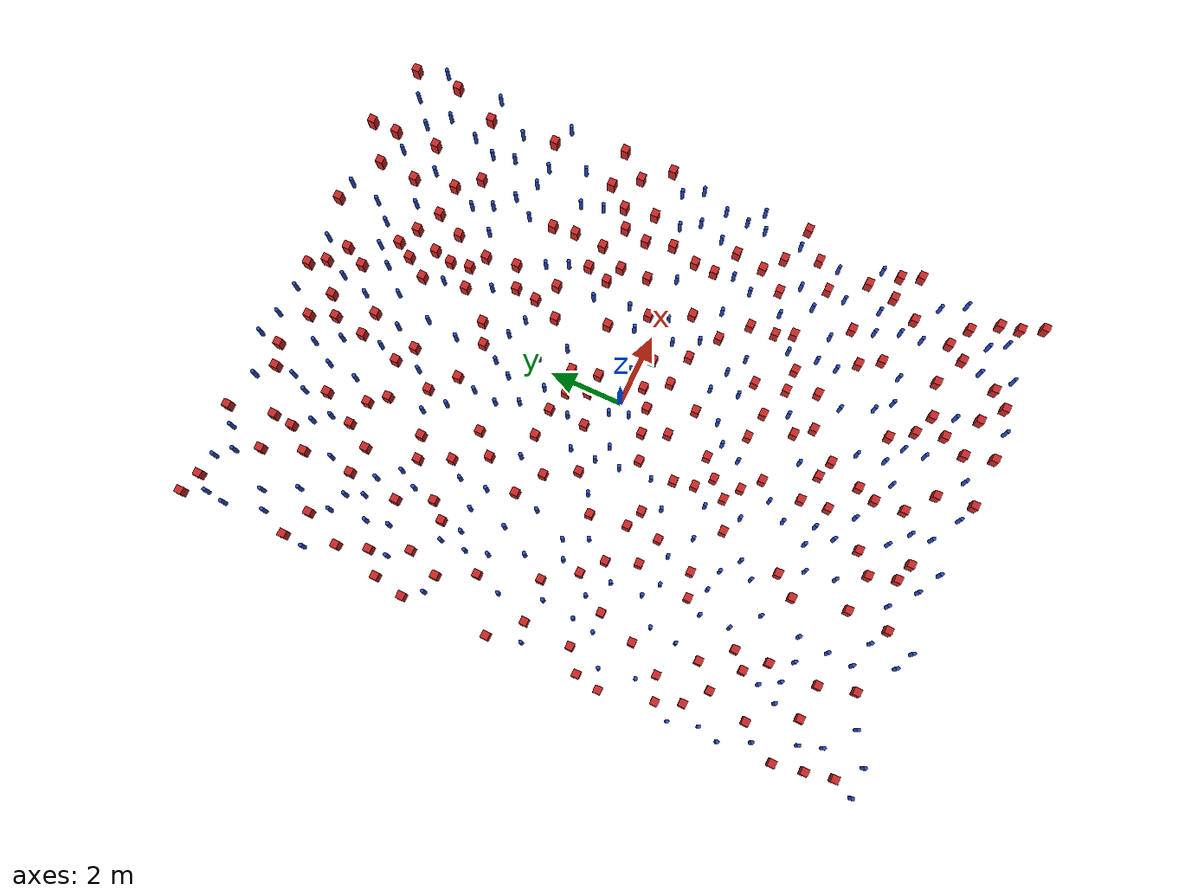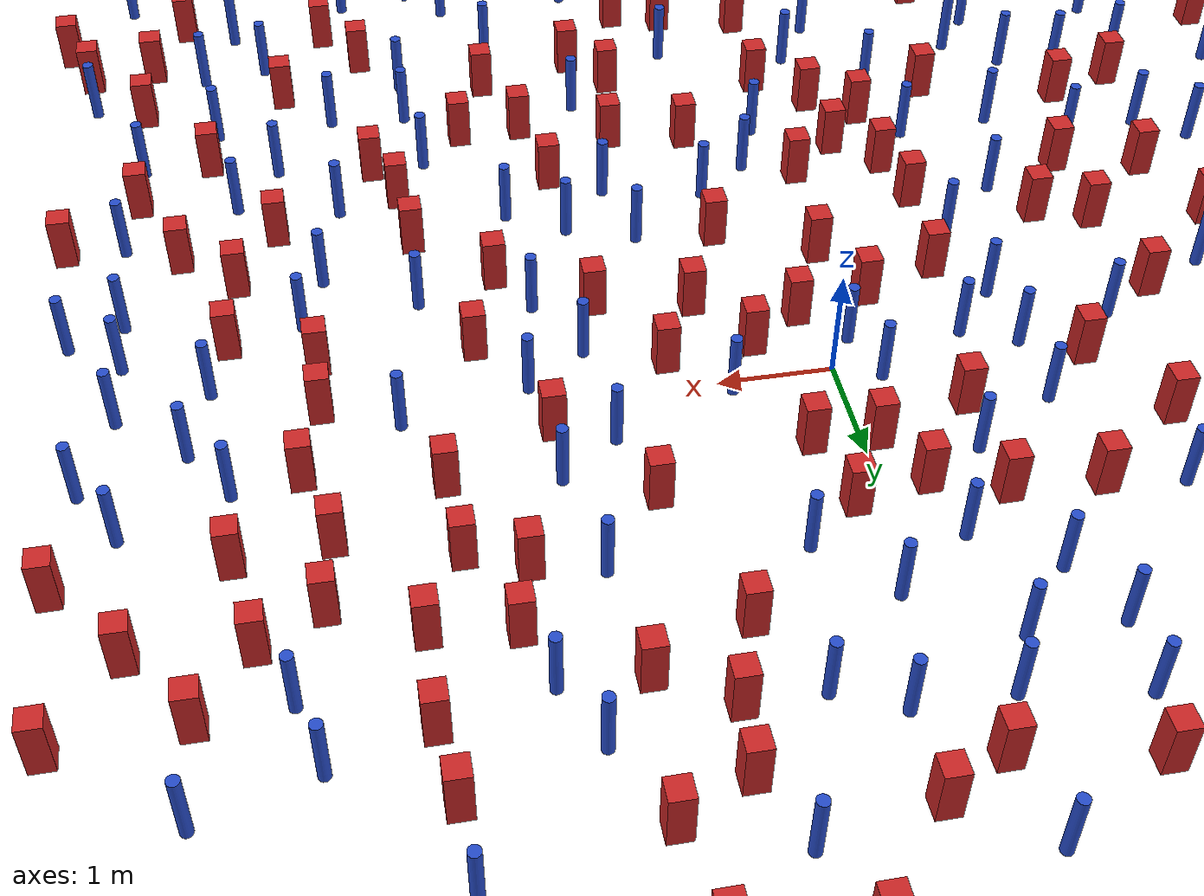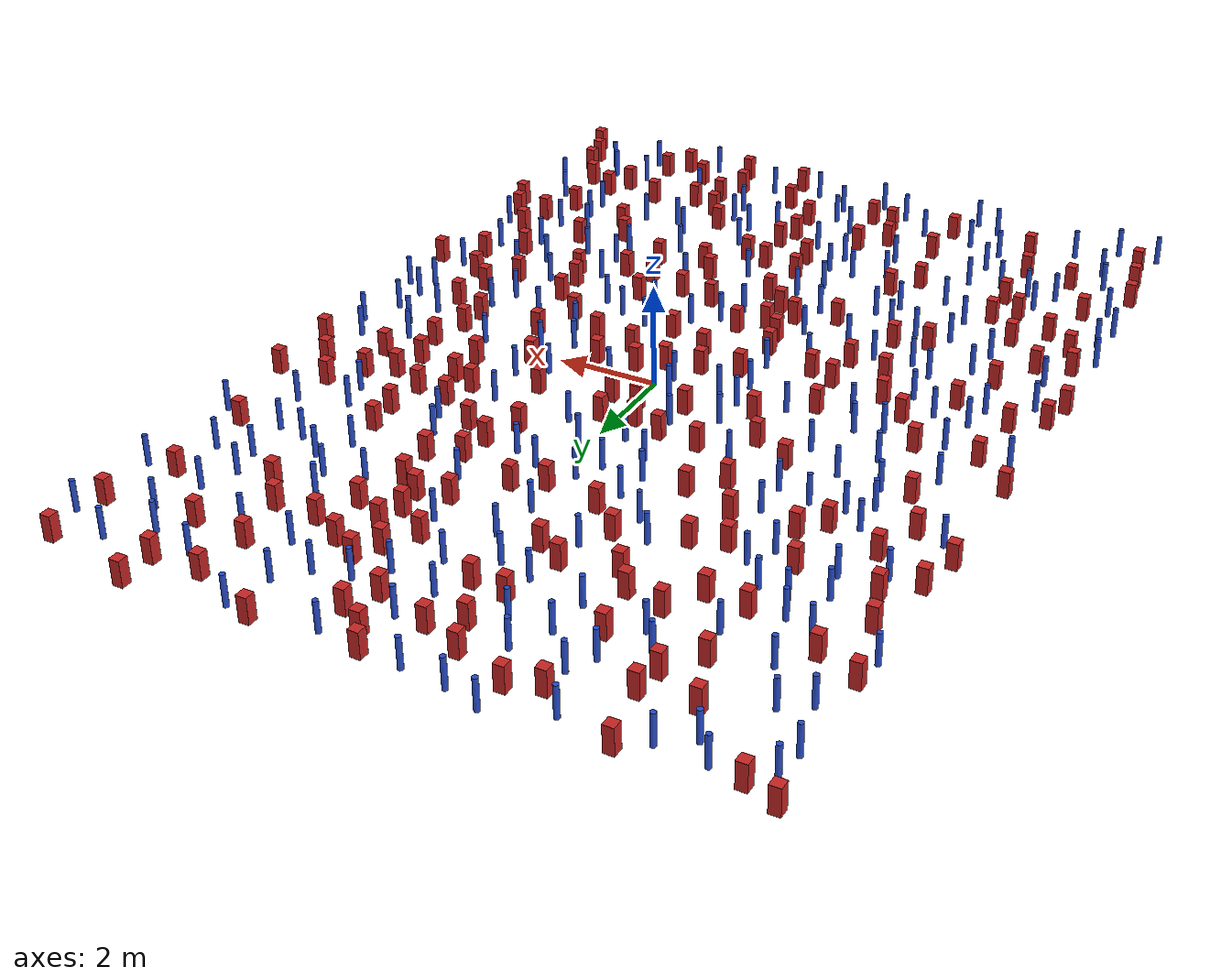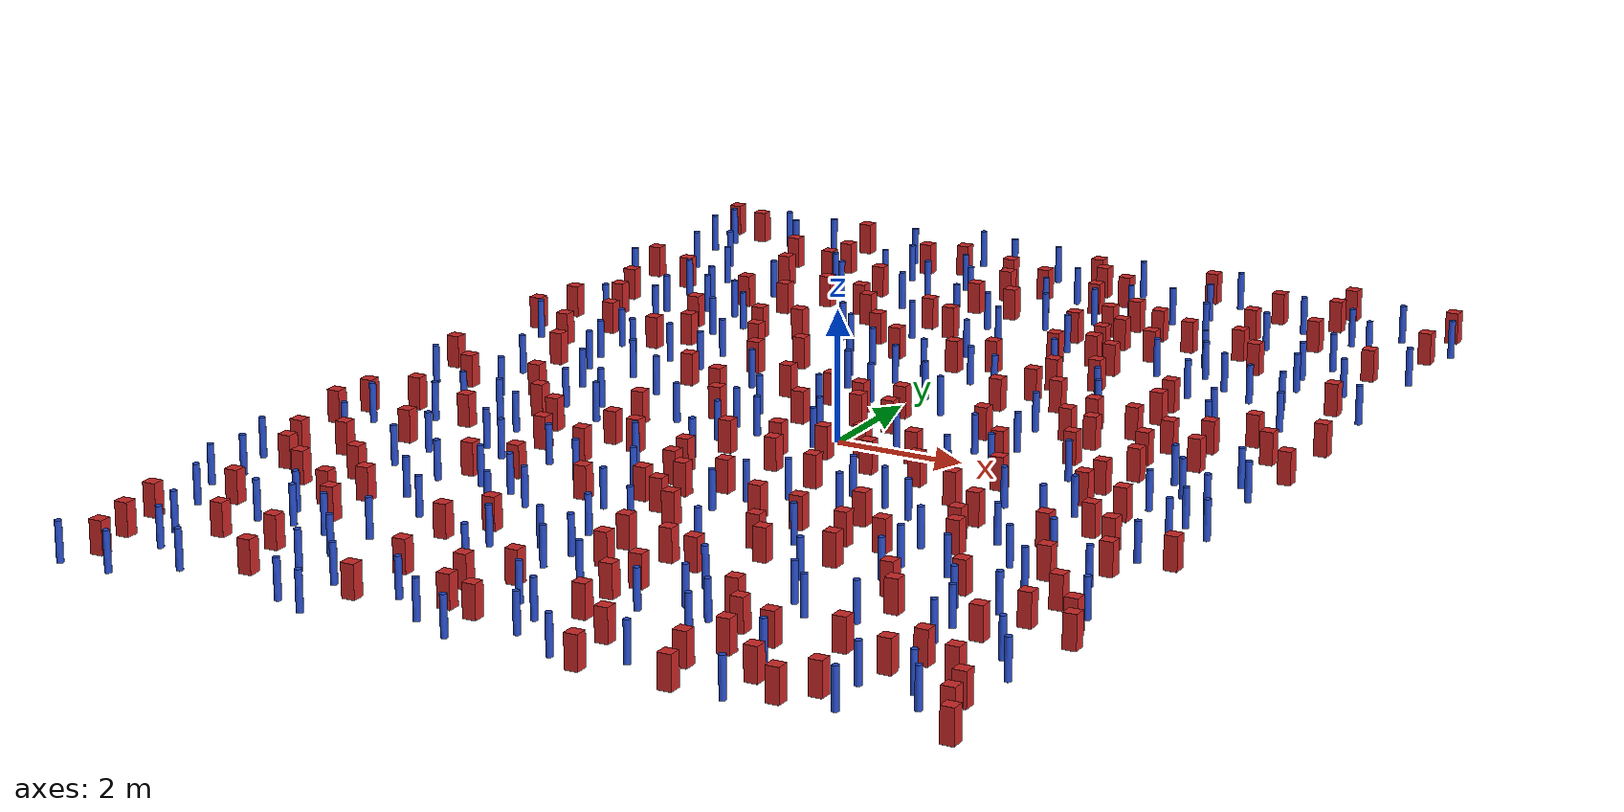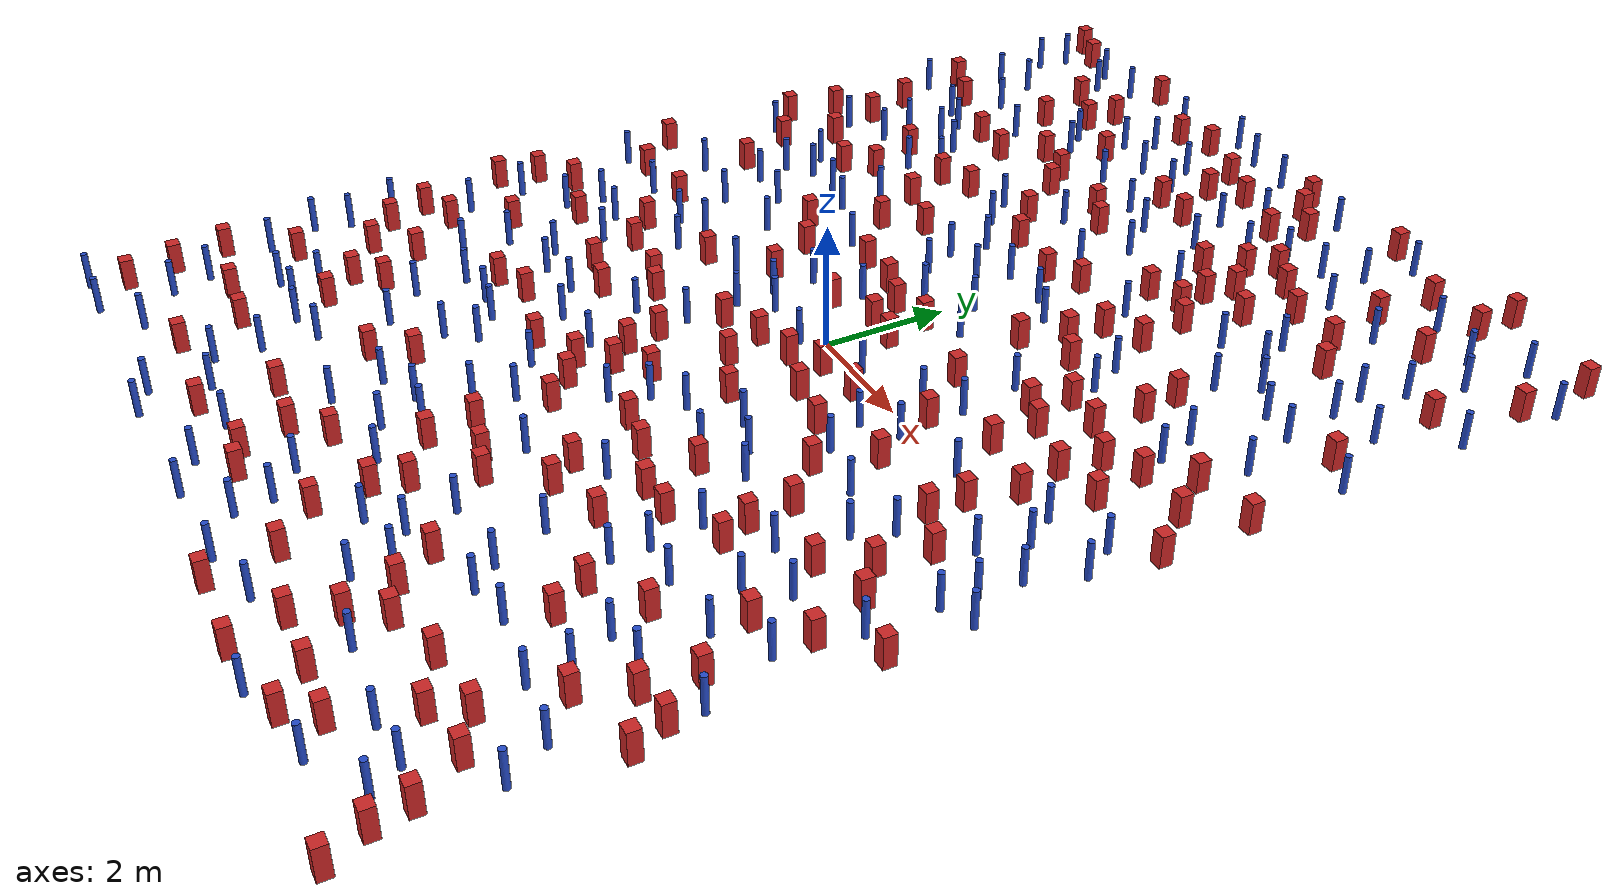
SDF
<sdf version="1.6">
  <model name="dense_4"><model name="square_post_obstacle0">
  <static>true</static>
  <pose frame="">-2.51508626237 -7.53984538496 8.22691968438e-08 7.2212513382e-06 -7.54495500217e-07 2.29674213826e-05</pose>
  <link name="link">
    <pose frame="">0 0 0.25 0 -0 0</pose>
    <inertial>
      <mass>100</mass>
      <inertia>
        <ixx>0.166667</ixx>
        <ixy>0</ixy>
        <ixz>0</ixz>
        <iyy>0.166667</iyy>
        <iyz>0</iyz>
        <izz>0.166667</izz>
      </inertia>
    </inertial>
    <collision name="collision">
      <geometry>
        <box>
          <size>.2 .2 .5</size>
        </box>
      </geometry>
      <max_contacts>10</max_contacts>
      <surface>
        <contact>
          <ode/>
        </contact>
        <bounce/>
        <friction>
          <torsional>
            <ode/>
          </torsional>
          <ode/>
        </friction>
      </surface>
    </collision>
    <visual name="visual">
      <geometry>
        <box>
          <size>.2 .2 .5</size>
        </box>
      </geometry>
      <material>
        <script>
          <name>Gazebo/Red</name>
          <uri>file://media/materials/scripts/gazebo.material</uri>
        </script>
      </material>
    </visual>
    <self_collide>0</self_collide>
    <kinematic>0</kinematic>
  </link>
</model>
<model name="square_post_obstacle1">
  <static>true</static>
  <pose frame="">0.525106642225 -6.55552689009 8.22691968438e-08 7.22125133819e-06 -7.54495500217e-07 2.29674213826e-05</pose>
  <link name="link">
    <pose frame="">0 0 0.25 0 -0 0</pose>
    <inertial>
      <mass>100</mass>
      <inertia>
        <ixx>0.166667</ixx>
        <ixy>0</ixy>
        <ixz>0</ixz>
        <iyy>0.166667</iyy>
        <iyz>0</iyz>
        <izz>0.166667</izz>
      </inertia>
    </inertial>
    <collision name="collision">
      <geometry>
        <box>
          <size>.2 .2 .5</size>
        </box>
      </geometry>
      <max_contacts>10</max_contacts>
      <surface>
        <contact>
          <ode/>
        </contact>
        <bounce/>
        <friction>
          <torsional>
            <ode/>
          </torsional>
          <ode/>
        </friction>
      </surface>
    </collision>
    <visual name="visual">
      <geometry>
        <box>
          <size>.2 .2 .5</size>
        </box>
      </geometry>
      <material>
        <script>
          <name>Gazebo/Red</name>
          <uri>file://media/materials/scripts/gazebo.material</uri>
        </script>
      </material>
    </visual>
    <self_collide>0</self_collide>
    <kinematic>0</kinematic>
  </link>
</model>
<model name="pole_obstacle0">
  <static>true</static>
  <pose frame="">-5.73621317295 -1.86977070437 2.88873142074e-08 -9.90536689445e-09 4.60219948999e-07 -1.20965994956e-07</pose>
  <link name="link">
  <pose frame="">0 0 0.3 0 -0 0</pose>
    <inertial>
      <mass>1</mass>
      <inertia>
        <ixx>0.145833</ixx>
        <ixy>0</ixy>
        <ixz>0</ixz>
        <iyy>0.145833</iyy>
        <iyz>0</iyz>
        <izz>0.125</izz>
      </inertia>
    </inertial>
    <collision name="collision">
      <geometry>
        <cylinder>
          <radius>0.05</radius>
          <length>.6</length>
        </cylinder>
      </geometry>
      <max_contacts>10</max_contacts>
      <surface>
        <contact>
          <ode/>
        </contact>
        <bounce/>
        <friction>
          <torsional>
            <ode/>
          </torsional>
          <ode/>
        </friction>
      </surface>
    </collision>
    <visual name="visual">
      <geometry>
        <cylinder>
          <radius>0.05</radius>
          <length>.6</length>
        </cylinder>
      </geometry>
      <material>
        <script>
          <name>Gazebo/Blue</name>
          <uri>file://media/materials/scripts/gazebo.material</uri>
        </script>
      </material>
    </visual>
    <self_collide>0</self_collide>
    <kinematic>0</kinematic>
  </link>
</model>
<model name="square_post_obstacle2">
  <static>true</static>
  <pose frame="">2.65907516394 -1.63502521584 8.22691968438e-08 7.2212513382e-06 -7.54495500217e-07 2.29674213826e-05</pose>
  <link name="link">
    <pose frame="">0 0 0.25 0 -0 0</pose>
    <inertial>
      <mass>100</mass>
      <inertia>
        <ixx>0.166667</ixx>
        <ixy>0</ixy>
        <ixz>0</ixz>
        <iyy>0.166667</iyy>
        <iyz>0</iyz>
        <izz>0.166667</izz>
      </inertia>
    </inertial>
    <collision name="collision">
      <geometry>
        <box>
          <size>.2 .2 .5</size>
        </box>
      </geometry>
      <max_contacts>10</max_contacts>
      <surface>
        <contact>
          <ode/>
        </contact>
        <bounce/>
        <friction>
          <torsional>
            <ode/>
          </torsional>
          <ode/>
        </friction>
      </surface>
    </collision>
    <visual name="visual">
      <geometry>
        <box>
          <size>.2 .2 .5</size>
        </box>
      </geometry>
      <material>
        <script>
          <name>Gazebo/Red</name>
          <uri>file://media/materials/scripts/gazebo.material</uri>
        </script>
      </material>
    </visual>
    <self_collide>0</self_collide>
    <kinematic>0</kinematic>
  </link>
</model>
<model name="pole_obstacle1">
  <static>true</static>
  <pose frame="">3.19692016445 -4.2430297542 2.88873142074e-08 -9.90536689859e-09 4.60219948989e-07 -1.20965994961e-07</pose>
  <link name="link">
  <pose frame="">0 0 0.3 0 -0 0</pose>
    <inertial>
      <mass>1</mass>
      <inertia>
        <ixx>0.145833</ixx>
        <ixy>0</ixy>
        <ixz>0</ixz>
        <iyy>0.145833</iyy>
        <iyz>0</iyz>
        <izz>0.125</izz>
      </inertia>
    </inertial>
    <collision name="collision">
      <geometry>
        <cylinder>
          <radius>0.05</radius>
          <length>.6</length>
        </cylinder>
      </geometry>
      <max_contacts>10</max_contacts>
      <surface>
        <contact>
          <ode/>
        </contact>
        <bounce/>
        <friction>
          <torsional>
            <ode/>
          </torsional>
          <ode/>
        </friction>
      </surface>
    </collision>
    <visual name="visual">
      <geometry>
        <cylinder>
          <radius>0.05</radius>
          <length>.6</length>
        </cylinder>
      </geometry>
      <material>
        <script>
          <name>Gazebo/Blue</name>
          <uri>file://media/materials/scripts/gazebo.material</uri>
        </script>
      </material>
    </visual>
    <self_collide>0</self_collide>
    <kinematic>0</kinematic>
  </link>
</model>
<model name="square_post_obstacle3">
  <static>true</static>
  <pose frame="">-3.93490845107 -3.70287970312 8.22691968438e-08 7.2212513382e-06 -7.54495500217e-07 2.29674213826e-05</pose>
  <link name="link">
    <pose frame="">0 0 0.25 0 -0 0</pose>
    <inertial>
      <mass>100</mass>
      <inertia>
        <ixx>0.166667</ixx>
        <ixy>0</ixy>
        <ixz>0</ixz>
        <iyy>0.166667</iyy>
        <iyz>0</iyz>
        <izz>0.166667</izz>
      </inertia>
    </inertial>
    <collision name="collision">
      <geometry>
        <box>
          <size>.2 .2 .5</size>
        </box>
      </geometry>
      <max_contacts>10</max_contacts>
      <surface>
        <contact>
          <ode/>
        </contact>
        <bounce/>
        <friction>
          <torsional>
            <ode/>
          </torsional>
          <ode/>
        </friction>
      </surface>
    </collision>
    <visual name="visual">
      <geometry>
        <box>
          <size>.2 .2 .5</size>
        </box>
      </geometry>
      <material>
        <script>
          <name>Gazebo/Red</name>
          <uri>file://media/materials/scripts/gazebo.material</uri>
        </script>
      </material>
    </visual>
    <self_collide>0</self_collide>
    <kinematic>0</kinematic>
  </link>
</model>
<model name="pole_obstacle2">
  <static>true</static>
  <pose frame="">-3.71937393445 -7.48251742339 2.88873142074e-08 -9.90536689859e-09 4.60219948989e-07 -1.20965994961e-07</pose>
  <link name="link">
  <pose frame="">0 0 0.3 0 -0 0</pose>
    <inertial>
      <mass>1</mass>
      <inertia>
        <ixx>0.145833</ixx>
        <ixy>0</ixy>
        <ixz>0</ixz>
        <iyy>0.145833</iyy>
        <iyz>0</iyz>
        <izz>0.125</izz>
      </inertia>
    </inertial>
    <collision name="collision">
      <geometry>
        <cylinder>
          <radius>0.05</radius>
          <length>.6</length>
        </cylinder>
      </geometry>
      <max_contacts>10</max_contacts>
      <surface>
        <contact>
          <ode/>
        </contact>
        <bounce/>
        <friction>
          <torsional>
            <ode/>
          </torsional>
          <ode/>
        </friction>
      </surface>
    </collision>
    <visual name="visual">
      <geometry>
        <cylinder>
          <radius>0.05</radius>
          <length>.6</length>
        </cylinder>
      </geometry>
      <material>
        <script>
          <name>Gazebo/Blue</name>
          <uri>file://media/materials/scripts/gazebo.material</uri>
        </script>
      </material>
    </visual>
    <self_collide>0</self_collide>
    <kinematic>0</kinematic>
  </link>
</model>
<model name="pole_obstacle3">
  <static>true</static>
  <pose frame="">-2.92639177187 8.12203701755 2.88873142074e-08 -9.90536692318e-09 4.6021994893e-07 -1.20965994988e-07</pose>
  <link name="link">
  <pose frame="">0 0 0.3 0 -0 0</pose>
    <inertial>
      <mass>1</mass>
      <inertia>
        <ixx>0.145833</ixx>
        <ixy>0</ixy>
        <ixz>0</ixz>
        <iyy>0.145833</iyy>
        <iyz>0</iyz>
        <izz>0.125</izz>
      </inertia>
    </inertial>
    <collision name="collision">
      <geometry>
        <cylinder>
          <radius>0.05</radius>
          <length>.6</length>
        </cylinder>
      </geometry>
      <max_contacts>10</max_contacts>
      <surface>
        <contact>
          <ode/>
        </contact>
        <bounce/>
        <friction>
          <torsional>
            <ode/>
          </torsional>
          <ode/>
        </friction>
      </surface>
    </collision>
    <visual name="visual">
      <geometry>
        <cylinder>
          <radius>0.05</radius>
          <length>.6</length>
        </cylinder>
      </geometry>
      <material>
        <script>
          <name>Gazebo/Blue</name>
          <uri>file://media/materials/scripts/gazebo.material</uri>
        </script>
      </material>
    </visual>
    <self_collide>0</self_collide>
    <kinematic>0</kinematic>
  </link>
</model>
<model name="square_post_obstacle4">
  <static>true</static>
  <pose frame="">-6.11988198631 2.40066412992 8.22691968438e-08 7.2212513382e-06 -7.54495500217e-07 2.29674213826e-05</pose>
  <link name="link">
    <pose frame="">0 0 0.25 0 -0 0</pose>
    <inertial>
      <mass>100</mass>
      <inertia>
        <ixx>0.166667</ixx>
        <ixy>0</ixy>
        <ixz>0</ixz>
        <iyy>0.166667</iyy>
        <iyz>0</iyz>
        <izz>0.166667</izz>
      </inertia>
    </inertial>
    <collision name="collision">
      <geometry>
        <box>
          <size>.2 .2 .5</size>
        </box>
      </geometry>
      <max_contacts>10</max_contacts>
      <surface>
        <contact>
          <ode/>
        </contact>
        <bounce/>
        <friction>
          <torsional>
            <ode/>
          </torsional>
          <ode/>
        </friction>
      </surface>
    </collision>
    <visual name="visual">
      <geometry>
        <box>
          <size>.2 .2 .5</size>
        </box>
      </geometry>
      <material>
        <script>
          <name>Gazebo/Red</name>
          <uri>file://media/materials/scripts/gazebo.material</uri>
        </script>
      </material>
    </visual>
    <self_collide>0</self_collide>
    <kinematic>0</kinematic>
  </link>
</model>
<model name="square_post_obstacle5">
  <static>true</static>
  <pose frame="">1.95356166881 -2.98597799232 8.22691968438e-08 7.2212513382e-06 -7.54495500217e-07 2.29674213826e-05</pose>
  <link name="link">
    <pose frame="">0 0 0.25 0 -0 0</pose>
    <inertial>
      <mass>100</mass>
      <inertia>
        <ixx>0.166667</ixx>
        <ixy>0</ixy>
        <ixz>0</ixz>
        <iyy>0.166667</iyy>
        <iyz>0</iyz>
        <izz>0.166667</izz>
      </inertia>
    </inertial>
    <collision name="collision">
      <geometry>
        <box>
          <size>.2 .2 .5</size>
        </box>
      </geometry>
      <max_contacts>10</max_contacts>
      <surface>
        <contact>
          <ode/>
        </contact>
        <bounce/>
        <friction>
          <torsional>
            <ode/>
          </torsional>
          <ode/>
        </friction>
      </surface>
    </collision>
    <visual name="visual">
      <geometry>
        <box>
          <size>.2 .2 .5</size>
        </box>
      </geometry>
      <material>
        <script>
          <name>Gazebo/Red</name>
          <uri>file://media/materials/scripts/gazebo.material</uri>
        </script>
      </material>
    </visual>
    <self_collide>0</self_collide>
    <kinematic>0</kinematic>
  </link>
</model>
<model name="square_post_obstacle6">
  <static>true</static>
  <pose frame="">0.843098504361 -5.64925832807 8.22691968438e-08 7.22125133819e-06 -7.54495500217e-07 2.29674213826e-05</pose>
  <link name="link">
    <pose frame="">0 0 0.25 0 -0 0</pose>
    <inertial>
      <mass>100</mass>
      <inertia>
        <ixx>0.166667</ixx>
        <ixy>0</ixy>
        <ixz>0</ixz>
        <iyy>0.166667</iyy>
        <iyz>0</iyz>
        <izz>0.166667</izz>
      </inertia>
    </inertial>
    <collision name="collision">
      <geometry>
        <box>
          <size>.2 .2 .5</size>
        </box>
      </geometry>
      <max_contacts>10</max_contacts>
      <surface>
        <contact>
          <ode/>
        </contact>
        <bounce/>
        <friction>
          <torsional>
            <ode/>
          </torsional>
          <ode/>
        </friction>
      </surface>
    </collision>
    <visual name="visual">
      <geometry>
        <box>
          <size>.2 .2 .5</size>
        </box>
      </geometry>
      <material>
        <script>
          <name>Gazebo/Red</name>
          <uri>file://media/materials/scripts/gazebo.material</uri>
        </script>
      </material>
    </visual>
    <self_collide>0</self_collide>
    <kinematic>0</kinematic>
  </link>
</model>
<model name="pole_obstacle4">
  <static>true</static>
  <pose frame="">-1.11285080218 2.41253646626 2.88873142074e-08 -9.90536689791e-09 4.6021994899e-07 -1.20965994959e-07</pose>
  <link name="link">
  <pose frame="">0 0 0.3 0 -0 0</pose>
    <inertial>
      <mass>1</mass>
      <inertia>
        <ixx>0.145833</ixx>
        <ixy>0</ixy>
        <ixz>0</ixz>
        <iyy>0.145833</iyy>
        <iyz>0</iyz>
        <izz>0.125</izz>
      </inertia>
    </inertial>
    <collision name="collision">
      <geometry>
        <cylinder>
          <radius>0.05</radius>
          <length>.6</length>
        </cylinder>
      </geometry>
      <max_contacts>10</max_contacts>
      <surface>
        <contact>
          <ode/>
        </contact>
        <bounce/>
        <friction>
          <torsional>
            <ode/>
          </torsional>
          <ode/>
        </friction>
      </surface>
    </collision>
    <visual name="visual">
      <geometry>
        <cylinder>
          <radius>0.05</radius>
          <length>.6</length>
        </cylinder>
      </geometry>
      <material>
        <script>
          <name>Gazebo/Blue</name>
          <uri>file://media/materials/scripts/gazebo.material</uri>
        </script>
      </material>
    </visual>
    <self_collide>0</self_collide>
    <kinematic>0</kinematic>
  </link>
</model>
<model name="pole_obstacle5">
  <static>true</static>
  <pose frame="">4.51118579981 3.26232769423 2.88873142074e-08 -9.90536690245e-09 4.6021994898e-07 -1.20965994966e-07</pose>
  <link name="link">
  <pose frame="">0 0 0.3 0 -0 0</pose>
    <inertial>
      <mass>1</mass>
      <inertia>
        <ixx>0.145833</ixx>
        <ixy>0</ixy>
        <ixz>0</ixz>
        <iyy>0.145833</iyy>
        <iyz>0</iyz>
        <izz>0.125</izz>
      </inertia>
    </inertial>
    <collision name="collision">
      <geometry>
        <cylinder>
          <radius>0.05</radius>
          <length>.6</length>
        </cylinder>
      </geometry>
      <max_contacts>10</max_contacts>
      <surface>
        <contact>
          <ode/>
        </contact>
        <bounce/>
        <friction>
          <torsional>
            <ode/>
          </torsional>
          <ode/>
        </friction>
      </surface>
    </collision>
    <visual name="visual">
      <geometry>
        <cylinder>
          <radius>0.05</radius>
          <length>.6</length>
        </cylinder>
      </geometry>
      <material>
        <script>
          <name>Gazebo/Blue</name>
          <uri>file://media/materials/scripts/gazebo.material</uri>
        </script>
      </material>
    </visual>
    <self_collide>0</self_collide>
    <kinematic>0</kinematic>
  </link>
</model>
<model name="square_post_obstacle7">
  <static>true</static>
  <pose frame="">-5.82940536862 -5.1514806708 8.22691968438e-08 7.2212513382e-06 -7.54495500217e-07 2.29674213826e-05</pose>
  <link name="link">
    <pose frame="">0 0 0.25 0 -0 0</pose>
    <inertial>
      <mass>100</mass>
      <inertia>
        <ixx>0.166667</ixx>
        <ixy>0</ixy>
        <ixz>0</ixz>
        <iyy>0.166667</iyy>
        <iyz>0</iyz>
        <izz>0.166667</izz>
      </inertia>
    </inertial>
    <collision name="collision">
      <geometry>
        <box>
          <size>.2 .2 .5</size>
        </box>
      </geometry>
      <max_contacts>10</max_contacts>
      <surface>
        <contact>
          <ode/>
        </contact>
        <bounce/>
        <friction>
          <torsional>
            <ode/>
          </torsional>
          <ode/>
        </friction>
      </surface>
    </collision>
    <visual name="visual">
      <geometry>
        <box>
          <size>.2 .2 .5</size>
        </box>
      </geometry>
      <material>
        <script>
          <name>Gazebo/Red</name>
          <uri>file://media/materials/scripts/gazebo.material</uri>
        </script>
      </material>
    </visual>
    <self_collide>0</self_collide>
    <kinematic>0</kinematic>
  </link>
</model>
<model name="square_post_obstacle8">
  <static>true</static>
  <pose frame="">-6.65443698681 -4.00906714522 8.22691968438e-08 7.2212513382e-06 -7.54495500217e-07 2.29674213826e-05</pose>
  <link name="link">
    <pose frame="">0 0 0.25 0 -0 0</pose>
    <inertial>
      <mass>100</mass>
      <inertia>
        <ixx>0.166667</ixx>
        <ixy>0</ixy>
        <ixz>0</ixz>
        <iyy>0.166667</iyy>
        <iyz>0</iyz>
        <izz>0.166667</izz>
      </inertia>
    </inertial>
    <collision name="collision">
      <geometry>
        <box>
          <size>.2 .2 .5</size>
        </box>
      </geometry>
      <max_contacts>10</max_contacts>
      <surface>
        <contact>
          <ode/>
        </contact>
        <bounce/>
        <friction>
          <torsional>
            <ode/>
          </torsional>
          <ode/>
        </friction>
      </surface>
    </collision>
    <visual name="visual">
      <geometry>
        <box>
          <size>.2 .2 .5</size>
        </box>
      </geometry>
      <material>
        <script>
          <name>Gazebo/Red</name>
          <uri>file://media/materials/scripts/gazebo.material</uri>
        </script>
      </material>
    </visual>
    <self_collide>0</self_collide>
    <kinematic>0</kinematic>
  </link>
</model>
<model name="pole_obstacle6">
  <static>true</static>
  <pose frame="">2.61312174763 -6.12198666901 2.88873142074e-08 -9.90536689859e-09 4.60219948989e-07 -1.20965994961e-07</pose>
  <link name="link">
  <pose frame="">0 0 0.3 0 -0 0</pose>
    <inertial>
      <mass>1</mass>
      <inertia>
        <ixx>0.145833</ixx>
        <ixy>0</ixy>
        <ixz>0</ixz>
        <iyy>0.145833</iyy>
        <iyz>0</iyz>
        <izz>0.125</izz>
      </inertia>
    </inertial>
    <collision name="collision">
      <geometry>
        <cylinder>
          <radius>0.05</radius>
          <length>.6</length>
        </cylinder>
      </geometry>
      <max_contacts>10</max_contacts>
      <surface>
        <contact>
          <ode/>
        </contact>
        <bounce/>
        <friction>
          <torsional>
            <ode/>
          </torsional>
          <ode/>
        </friction>
      </surface>
    </collision>
    <visual name="visual">
      <geometry>
        <cylinder>
          <radius>0.05</radius>
          <length>.6</length>
        </cylinder>
      </geometry>
      <material>
        <script>
          <name>Gazebo/Blue</name>
          <uri>file://media/materials/scripts/gazebo.material</uri>
        </script>
      </material>
    </visual>
    <self_collide>0</self_collide>
    <kinematic>0</kinematic>
  </link>
</model>
<model name="pole_obstacle7">
  <static>true</static>
  <pose frame="">1.99816987325 -7.80242204155 2.88873142074e-08 -9.9053668918e-09 4.60219949005e-07 -1.20965994951e-07</pose>
  <link name="link">
  <pose frame="">0 0 0.3 0 -0 0</pose>
    <inertial>
      <mass>1</mass>
      <inertia>
        <ixx>0.145833</ixx>
        <ixy>0</ixy>
        <ixz>0</ixz>
        <iyy>0.145833</iyy>
        <iyz>0</iyz>
        <izz>0.125</izz>
      </inertia>
    </inertial>
    <collision name="collision">
      <geometry>
        <cylinder>
          <radius>0.05</radius>
          <length>.6</length>
        </cylinder>
      </geometry>
      <max_contacts>10</max_contacts>
      <surface>
        <contact>
          <ode/>
        </contact>
        <bounce/>
        <friction>
          <torsional>
            <ode/>
          </torsional>
          <ode/>
        </friction>
      </surface>
    </collision>
    <visual name="visual">
      <geometry>
        <cylinder>
          <radius>0.05</radius>
          <length>.6</length>
        </cylinder>
      </geometry>
      <material>
        <script>
          <name>Gazebo/Blue</name>
          <uri>file://media/materials/scripts/gazebo.material</uri>
        </script>
      </material>
    </visual>
    <self_collide>0</self_collide>
    <kinematic>0</kinematic>
  </link>
</model>
<model name="square_post_obstacle9">
  <static>true</static>
  <pose frame="">0.79812597293 8.42285894437 8.22691968438e-08 7.22125133819e-06 -7.54495500217e-07 2.29674213826e-05</pose>
  <link name="link">
    <pose frame="">0 0 0.25 0 -0 0</pose>
    <inertial>
      <mass>100</mass>
      <inertia>
        <ixx>0.166667</ixx>
        <ixy>0</ixy>
        <ixz>0</ixz>
        <iyy>0.166667</iyy>
        <iyz>0</iyz>
        <izz>0.166667</izz>
      </inertia>
    </inertial>
    <collision name="collision">
      <geometry>
        <box>
          <size>.2 .2 .5</size>
        </box>
      </geometry>
      <max_contacts>10</max_contacts>
      <surface>
        <contact>
          <ode/>
        </contact>
        <bounce/>
        <friction>
          <torsional>
            <ode/>
          </torsional>
          <ode/>
        </friction>
      </surface>
    </collision>
    <visual name="visual">
      <geometry>
        <box>
          <size>.2 .2 .5</size>
        </box>
      </geometry>
      <material>
        <script>
          <name>Gazebo/Red</name>
          <uri>file://media/materials/scripts/gazebo.material</uri>
        </script>
      </material>
    </visual>
    <self_collide>0</self_collide>
    <kinematic>0</kinematic>
  </link>
</model>
<model name="square_post_obstacle10">
  <static>true</static>
  <pose frame="">0.251058092384 8.77445879039 8.22691968438e-08 7.22125133819e-06 -7.54495500217e-07 2.29674213826e-05</pose>
  <link name="link">
    <pose frame="">0 0 0.25 0 -0 0</pose>
    <inertial>
      <mass>100</mass>
      <inertia>
        <ixx>0.166667</ixx>
        <ixy>0</ixy>
        <ixz>0</ixz>
        <iyy>0.166667</iyy>
        <iyz>0</iyz>
        <izz>0.166667</izz>
      </inertia>
    </inertial>
    <collision name="collision">
      <geometry>
        <box>
          <size>.2 .2 .5</size>
        </box>
      </geometry>
      <max_contacts>10</max_contacts>
      <surface>
        <contact>
          <ode/>
        </contact>
        <bounce/>
        <friction>
          <torsional>
            <ode/>
          </torsional>
          <ode/>
        </friction>
      </surface>
    </collision>
    <visual name="visual">
      <geometry>
        <box>
          <size>.2 .2 .5</size>
        </box>
      </geometry>
      <material>
        <script>
          <name>Gazebo/Red</name>
          <uri>file://media/materials/scripts/gazebo.material</uri>
        </script>
      </material>
    </visual>
    <self_collide>0</self_collide>
    <kinematic>0</kinematic>
  </link>
</model>
<model name="square_post_obstacle11">
  <static>true</static>
  <pose frame="">-6.14885330186 -6.27822620276 8.22691968438e-08 7.2212513382e-06 -7.54495500217e-07 2.29674213826e-05</pose>
  <link name="link">
    <pose frame="">0 0 0.25 0 -0 0</pose>
    <inertial>
      <mass>100</mass>
      <inertia>
        <ixx>0.166667</ixx>
        <ixy>0</ixy>
        <ixz>0</ixz>
        <iyy>0.166667</iyy>
        <iyz>0</iyz>
        <izz>0.166667</izz>
      </inertia>
    </inertial>
    <collision name="collision">
      <geometry>
        <box>
          <size>.2 .2 .5</size>
        </box>
      </geometry>
      <max_contacts>10</max_contacts>
      <surface>
        <contact>
          <ode/>
        </contact>
        <bounce/>
        <friction>
          <torsional>
            <ode/>
          </torsional>
          <ode/>
        </friction>
      </surface>
    </collision>
    <visual name="visual">
      <geometry>
        <box>
          <size>.2 .2 .5</size>
        </box>
      </geometry>
      <material>
        <script>
          <name>Gazebo/Red</name>
          <uri>file://media/materials/scripts/gazebo.material</uri>
        </script>
      </material>
    </visual>
    <self_collide>0</self_collide>
    <kinematic>0</kinematic>
  </link>
</model>
<model name="square_post_obstacle12">
  <static>true</static>
  <pose frame="">-1.4836494756 -7.65505798456 8.22691968438e-08 7.2212513382e-06 -7.54495500217e-07 2.29674213826e-05</pose>
  <link name="link">
    <pose frame="">0 0 0.25 0 -0 0</pose>
    <inertial>
      <mass>100</mass>
      <inertia>
        <ixx>0.166667</ixx>
        <ixy>0</ixy>
        <ixz>0</ixz>
        <iyy>0.166667</iyy>
        <iyz>0</iyz>
        <izz>0.166667</izz>
      </inertia>
    </inertial>
    <collision name="collision">
      <geometry>
        <box>
          <size>.2 .2 .5</size>
        </box>
      </geometry>
      <max_contacts>10</max_contacts>
      <surface>
        <contact>
          <ode/>
        </contact>
        <bounce/>
        <friction>
          <torsional>
            <ode/>
          </torsional>
          <ode/>
        </friction>
      </surface>
    </collision>
    <visual name="visual">
      <geometry>
        <box>
          <size>.2 .2 .5</size>
        </box>
      </geometry>
      <material>
        <script>
          <name>Gazebo/Red</name>
          <uri>file://media/materials/scripts/gazebo.material</uri>
        </script>
      </material>
    </visual>
    <self_collide>0</self_collide>
    <kinematic>0</kinematic>
  </link>
</model>
<model name="square_post_obstacle13">
  <static>true</static>
  <pose frame="">-6.22304500076 -0.177315337008 8.22691968438e-08 7.2212513382e-06 -7.54495500217e-07 2.29674213826e-05</pose>
  <link name="link">
    <pose frame="">0 0 0.25 0 -0 0</pose>
    <inertial>
      <mass>100</mass>
      <inertia>
        <ixx>0.166667</ixx>
        <ixy>0</ixy>
        <ixz>0</ixz>
        <iyy>0.166667</iyy>
        <iyz>0</iyz>
        <izz>0.166667</izz>
      </inertia>
    </inertial>
    <collision name="collision">
      <geometry>
        <box>
          <size>.2 .2 .5</size>
        </box>
      </geometry>
      <max_contacts>10</max_contacts>
      <surface>
        <contact>
          <ode/>
        </contact>
        <bounce/>
        <friction>
          <torsional>
            <ode/>
          </torsional>
          <ode/>
        </friction>
      </surface>
    </collision>
    <visual name="visual">
      <geometry>
        <box>
          <size>.2 .2 .5</size>
        </box>
      </geometry>
      <material>
        <script>
          <name>Gazebo/Red</name>
          <uri>file://media/materials/scripts/gazebo.material</uri>
        </script>
      </material>
    </visual>
    <self_collide>0</self_collide>
    <kinematic>0</kinematic>
  </link>
</model>
<model name="pole_obstacle8">
  <static>true</static>
  <pose frame="">4.37933698074 -1.31018265101 2.88873142074e-08 -9.90536689445e-09 4.60219948999e-07 -1.20965994956e-07</pose>
  <link name="link">
  <pose frame="">0 0 0.3 0 -0 0</pose>
    <inertial>
      <mass>1</mass>
      <inertia>
        <ixx>0.145833</ixx>
        <ixy>0</ixy>
        <ixz>0</ixz>
        <iyy>0.145833</iyy>
        <iyz>0</iyz>
        <izz>0.125</izz>
      </inertia>
    </inertial>
    <collision name="collision">
      <geometry>
        <cylinder>
          <radius>0.05</radius>
          <length>.6</length>
        </cylinder>
      </geometry>
      <max_contacts>10</max_contacts>
      <surface>
        <contact>
          <ode/>
        </contact>
        <bounce/>
        <friction>
          <torsional>
            <ode/>
          </torsional>
          <ode/>
        </friction>
      </surface>
    </collision>
    <visual name="visual">
      <geometry>
        <cylinder>
          <radius>0.05</radius>
          <length>.6</length>
        </cylinder>
      </geometry>
      <material>
        <script>
          <name>Gazebo/Blue</name>
          <uri>file://media/materials/scripts/gazebo.material</uri>
        </script>
      </material>
    </visual>
    <self_collide>0</self_collide>
    <kinematic>0</kinematic>
  </link>
</model>
<model name="square_post_obstacle14">
  <static>true</static>
  <pose frame="">-2.40461880925 -1.69817275104 8.22691968438e-08 7.2212513382e-06 -7.54495500217e-07 2.29674213826e-05</pose>
  <link name="link">
    <pose frame="">0 0 0.25 0 -0 0</pose>
    <inertial>
      <mass>100</mass>
      <inertia>
        <ixx>0.166667</ixx>
        <ixy>0</ixy>
        <ixz>0</ixz>
        <iyy>0.166667</iyy>
        <iyz>0</iyz>
        <izz>0.166667</izz>
      </inertia>
    </inertial>
    <collision name="collision">
      <geometry>
        <box>
          <size>.2 .2 .5</size>
        </box>
      </geometry>
      <max_contacts>10</max_contacts>
      <surface>
        <contact>
          <ode/>
        </contact>
        <bounce/>
        <friction>
          <torsional>
            <ode/>
          </torsional>
          <ode/>
        </friction>
      </surface>
    </collision>
    <visual name="visual">
      <geometry>
        <box>
          <size>.2 .2 .5</size>
        </box>
      </geometry>
      <material>
        <script>
          <name>Gazebo/Red</name>
          <uri>file://media/materials/scripts/gazebo.material</uri>
        </script>
      </material>
    </visual>
    <self_collide>0</self_collide>
    <kinematic>0</kinematic>
  </link>
</model>
<model name="square_post_obstacle15">
  <static>true</static>
  <pose frame="">-6.2994854559 -1.49680176613 8.22691968438e-08 7.2212513382e-06 -7.54495500217e-07 2.29674213826e-05</pose>
  <link name="link">
    <pose frame="">0 0 0.25 0 -0 0</pose>
    <inertial>
      <mass>100</mass>
      <inertia>
        <ixx>0.166667</ixx>
        <ixy>0</ixy>
        <ixz>0</ixz>
        <iyy>0.166667</iyy>
        <iyz>0</iyz>
        <izz>0.166667</izz>
      </inertia>
    </inertial>
    <collision name="collision">
      <geometry>
        <box>
          <size>.2 .2 .5</size>
        </box>
      </geometry>
      <max_contacts>10</max_contacts>
      <surface>
        <contact>
          <ode/>
        </contact>
        <bounce/>
        <friction>
          <torsional>
            <ode/>
          </torsional>
          <ode/>
        </friction>
      </surface>
    </collision>
    <visual name="visual">
      <geometry>
        <box>
          <size>.2 .2 .5</size>
        </box>
      </geometry>
      <material>
        <script>
          <name>Gazebo/Red</name>
          <uri>file://media/materials/scripts/gazebo.material</uri>
        </script>
      </material>
    </visual>
    <self_collide>0</self_collide>
    <kinematic>0</kinematic>
  </link>
</model>
<model name="square_post_obstacle16">
  <static>true</static>
  <pose frame="">-6.39864318015 -4.66652046836 8.22691968438e-08 7.2212513382e-06 -7.54495500217e-07 2.29674213826e-05</pose>
  <link name="link">
    <pose frame="">0 0 0.25 0 -0 0</pose>
    <inertial>
      <mass>100</mass>
      <inertia>
        <ixx>0.166667</ixx>
        <ixy>0</ixy>
        <ixz>0</ixz>
        <iyy>0.166667</iyy>
        <iyz>0</iyz>
        <izz>0.166667</izz>
      </inertia>
    </inertial>
    <collision name="collision">
      <geometry>
        <box>
          <size>.2 .2 .5</size>
        </box>
      </geometry>
      <max_contacts>10</max_contacts>
      <surface>
        <contact>
          <ode/>
        </contact>
        <bounce/>
        <friction>
          <torsional>
            <ode/>
          </torsional>
          <ode/>
        </friction>
      </surface>
    </collision>
    <visual name="visual">
      <geometry>
        <box>
          <size>.2 .2 .5</size>
        </box>
      </geometry>
      <material>
        <script>
          <name>Gazebo/Red</name>
          <uri>file://media/materials/scripts/gazebo.material</uri>
        </script>
      </material>
    </visual>
    <self_collide>0</self_collide>
    <kinematic>0</kinematic>
  </link>
</model>
<model name="pole_obstacle9">
  <static>true</static>
  <pose frame="">-1.67176897016 0.657814123121 2.88873142074e-08 -9.90536689692e-09 4.60219948993e-07 -1.20965994958e-07</pose>
  <link name="link">
  <pose frame="">0 0 0.3 0 -0 0</pose>
    <inertial>
      <mass>1</mass>
      <inertia>
        <ixx>0.145833</ixx>
        <ixy>0</ixy>
        <ixz>0</ixz>
        <iyy>0.145833</iyy>
        <iyz>0</iyz>
        <izz>0.125</izz>
      </inertia>
    </inertial>
    <collision name="collision">
      <geometry>
        <cylinder>
          <radius>0.05</radius>
          <length>.6</length>
        </cylinder>
      </geometry>
      <max_contacts>10</max_contacts>
      <surface>
        <contact>
          <ode/>
        </contact>
        <bounce/>
        <friction>
          <torsional>
            <ode/>
          </torsional>
          <ode/>
        </friction>
      </surface>
    </collision>
    <visual name="visual">
      <geometry>
        <cylinder>
          <radius>0.05</radius>
          <length>.6</length>
        </cylinder>
      </geometry>
      <material>
        <script>
          <name>Gazebo/Blue</name>
          <uri>file://media/materials/scripts/gazebo.material</uri>
        </script>
      </material>
    </visual>
    <self_collide>0</self_collide>
    <kinematic>0</kinematic>
  </link>
</model>
<model name="square_post_obstacle17">
  <static>true</static>
  <pose frame="">-2.39460660989 -5.54675566457 8.22691968438e-08 7.2212513382e-06 -7.54495500217e-07 2.29674213826e-05</pose>
  <link name="link">
    <pose frame="">0 0 0.25 0 -0 0</pose>
    <inertial>
      <mass>100</mass>
      <inertia>
        <ixx>0.166667</ixx>
        <ixy>0</ixy>
        <ixz>0</ixz>
        <iyy>0.166667</iyy>
        <iyz>0</iyz>
        <izz>0.166667</izz>
      </inertia>
    </inertial>
    <collision name="collision">
      <geometry>
        <box>
          <size>.2 .2 .5</size>
        </box>
      </geometry>
      <max_contacts>10</max_contacts>
      <surface>
        <contact>
          <ode/>
        </contact>
        <bounce/>
        <friction>
          <torsional>
            <ode/>
          </torsional>
          <ode/>
        </friction>
      </surface>
    </collision>
    <visual name="visual">
      <geometry>
        <box>
          <size>.2 .2 .5</size>
        </box>
      </geometry>
      <material>
        <script>
          <name>Gazebo/Red</name>
          <uri>file://media/materials/scripts/gazebo.material</uri>
        </script>
      </material>
    </visual>
    <self_collide>0</self_collide>
    <kinematic>0</kinematic>
  </link>
</model>
<model name="square_post_obstacle18">
  <static>true</static>
  <pose frame="">-4.30766637956 -8.52579925816 8.22691968438e-08 7.22125133819e-06 -7.54495500217e-07 2.29674213826e-05</pose>
  <link name="link">
    <pose frame="">0 0 0.25 0 -0 0</pose>
    <inertial>
      <mass>100</mass>
      <inertia>
        <ixx>0.166667</ixx>
        <ixy>0</ixy>
        <ixz>0</ixz>
        <iyy>0.166667</iyy>
        <iyz>0</iyz>
        <izz>0.166667</izz>
      </inertia>
    </inertial>
    <collision name="collision">
      <geometry>
        <box>
          <size>.2 .2 .5</size>
        </box>
      </geometry>
      <max_contacts>10</max_contacts>
      <surface>
        <contact>
          <ode/>
        </contact>
        <bounce/>
        <friction>
          <torsional>
            <ode/>
          </torsional>
          <ode/>
        </friction>
      </surface>
    </collision>
    <visual name="visual">
      <geometry>
        <box>
          <size>.2 .2 .5</size>
        </box>
      </geometry>
      <material>
        <script>
          <name>Gazebo/Red</name>
          <uri>file://media/materials/scripts/gazebo.material</uri>
        </script>
      </material>
    </visual>
    <self_collide>0</self_collide>
    <kinematic>0</kinematic>
  </link>
</model>
<model name="pole_obstacle10">
  <static>true</static>
  <pose frame="">5.02063466316 -4.25020811535 2.88873142074e-08 -9.90536690842e-09 4.60219948965e-07 -1.20965994976e-07</pose>
  <link name="link">
  <pose frame="">0 0 0.3 0 -0 0</pose>
    <inertial>
      <mass>1</mass>
      <inertia>
        <ixx>0.145833</ixx>
        <ixy>0</ixy>
        <ixz>0</ixz>
        <iyy>0.145833</iyy>
        <iyz>0</iyz>
        <izz>0.125</izz>
      </inertia>
    </inertial>
    <collision name="collision">
      <geometry>
        <cylinder>
          <radius>0.05</radius>
          <length>.6</length>
        </cylinder>
      </geometry>
      <max_contacts>10</max_contacts>
      <surface>
        <contact>
          <ode/>
        </contact>
        <bounce/>
        <friction>
          <torsional>
            <ode/>
          </torsional>
          <ode/>
        </friction>
      </surface>
    </collision>
    <visual name="visual">
      <geometry>
        <cylinder>
          <radius>0.05</radius>
          <length>.6</length>
        </cylinder>
      </geometry>
      <material>
        <script>
          <name>Gazebo/Blue</name>
          <uri>file://media/materials/scripts/gazebo.material</uri>
        </script>
      </material>
    </visual>
    <self_collide>0</self_collide>
    <kinematic>0</kinematic>
  </link>
</model>
<model name="square_post_obstacle19">
  <static>true</static>
  <pose frame="">-2.99249537254 7.10231828787 8.22691968438e-08 7.2212513382e-06 -7.54495500217e-07 2.29674213826e-05</pose>
  <link name="link">
    <pose frame="">0 0 0.25 0 -0 0</pose>
    <inertial>
      <mass>100</mass>
      <inertia>
        <ixx>0.166667</ixx>
        <ixy>0</ixy>
        <ixz>0</ixz>
        <iyy>0.166667</iyy>
        <iyz>0</iyz>
        <izz>0.166667</izz>
      </inertia>
    </inertial>
    <collision name="collision">
      <geometry>
        <box>
          <size>.2 .2 .5</size>
        </box>
      </geometry>
      <max_contacts>10</max_contacts>
      <surface>
        <contact>
          <ode/>
        </contact>
        <bounce/>
        <friction>
          <torsional>
            <ode/>
          </torsional>
          <ode/>
        </friction>
      </surface>
    </collision>
    <visual name="visual">
      <geometry>
        <box>
          <size>.2 .2 .5</size>
        </box>
      </geometry>
      <material>
        <script>
          <name>Gazebo/Red</name>
          <uri>file://media/materials/scripts/gazebo.material</uri>
        </script>
      </material>
    </visual>
    <self_collide>0</self_collide>
    <kinematic>0</kinematic>
  </link>
</model>
<model name="pole_obstacle11">
  <static>true</static>
  <pose frame="">-0.239215653327 4.69191095923 2.88873142074e-08 -9.90536689703e-09 4.60219948992e-07 -1.20965994959e-07</pose>
  <link name="link">
  <pose frame="">0 0 0.3 0 -0 0</pose>
    <inertial>
      <mass>1</mass>
      <inertia>
        <ixx>0.145833</ixx>
        <ixy>0</ixy>
        <ixz>0</ixz>
        <iyy>0.145833</iyy>
        <iyz>0</iyz>
        <izz>0.125</izz>
      </inertia>
    </inertial>
    <collision name="collision">
      <geometry>
        <cylinder>
          <radius>0.05</radius>
          <length>.6</length>
        </cylinder>
      </geometry>
      <max_contacts>10</max_contacts>
      <surface>
        <contact>
          <ode/>
        </contact>
        <bounce/>
        <friction>
          <torsional>
            <ode/>
          </torsional>
          <ode/>
        </friction>
      </surface>
    </collision>
    <visual name="visual">
      <geometry>
        <cylinder>
          <radius>0.05</radius>
          <length>.6</length>
        </cylinder>
      </geometry>
      <material>
        <script>
          <name>Gazebo/Blue</name>
          <uri>file://media/materials/scripts/gazebo.material</uri>
        </script>
      </material>
    </visual>
    <self_collide>0</self_collide>
    <kinematic>0</kinematic>
  </link>
</model>
<model name="square_post_obstacle20">
  <static>true</static>
  <pose frame="">5.0686060429 1.31491274557 8.22691968438e-08 7.2212513382e-06 -7.54495500217e-07 2.29674213826e-05</pose>
  <link name="link">
    <pose frame="">0 0 0.25 0 -0 0</pose>
    <inertial>
      <mass>100</mass>
      <inertia>
        <ixx>0.166667</ixx>
        <ixy>0</ixy>
        <ixz>0</ixz>
        <iyy>0.166667</iyy>
        <iyz>0</iyz>
        <izz>0.166667</izz>
      </inertia>
    </inertial>
    <collision name="collision">
      <geometry>
        <box>
          <size>.2 .2 .5</size>
        </box>
      </geometry>
      <max_contacts>10</max_contacts>
      <surface>
        <contact>
          <ode/>
        </contact>
        <bounce/>
        <friction>
          <torsional>
            <ode/>
          </torsional>
          <ode/>
        </friction>
      </surface>
    </collision>
    <visual name="visual">
      <geometry>
        <box>
          <size>.2 .2 .5</size>
        </box>
      </geometry>
      <material>
        <script>
          <name>Gazebo/Red</name>
          <uri>file://media/materials/scripts/gazebo.material</uri>
        </script>
      </material>
    </visual>
    <self_collide>0</self_collide>
    <kinematic>0</kinematic>
  </link>
</model>
<model name="pole_obstacle12">
  <static>true</static>
  <pose frame="">-0.907290829122 1.1120507085 2.88873142074e-08 -9.90536689855e-09 4.60219948989e-07 -1.20965994962e-07</pose>
  <link name="link">
  <pose frame="">0 0 0.3 0 -0 0</pose>
    <inertial>
      <mass>1</mass>
      <inertia>
        <ixx>0.145833</ixx>
        <ixy>0</ixy>
        <ixz>0</ixz>
        <iyy>0.145833</iyy>
        <iyz>0</iyz>
        <izz>0.125</izz>
      </inertia>
    </inertial>
    <collision name="collision">
      <geometry>
        <cylinder>
          <radius>0.05</radius>
          <length>.6</length>
        </cylinder>
      </geometry>
      <max_contacts>10</max_contacts>
      <surface>
        <contact>
          <ode/>
        </contact>
        <bounce/>
        <friction>
          <torsional>
            <ode/>
          </torsional>
          <ode/>
        </friction>
      </surface>
    </collision>
    <visual name="visual">
      <geometry>
        <cylinder>
          <radius>0.05</radius>
          <length>.6</length>
        </cylinder>
      </geometry>
      <material>
        <script>
          <name>Gazebo/Blue</name>
          <uri>file://media/materials/scripts/gazebo.material</uri>
        </script>
      </material>
    </visual>
    <self_collide>0</self_collide>
    <kinematic>0</kinematic>
  </link>
</model>
<model name="square_post_obstacle21">
  <static>true</static>
  <pose frame="">5.75815409374 -3.21778082992 8.22691968438e-08 7.2212513382e-06 -7.54495500217e-07 2.29674213826e-05</pose>
  <link name="link">
    <pose frame="">0 0 0.25 0 -0 0</pose>
    <inertial>
      <mass>100</mass>
      <inertia>
        <ixx>0.166667</ixx>
        <ixy>0</ixy>
        <ixz>0</ixz>
        <iyy>0.166667</iyy>
        <iyz>0</iyz>
        <izz>0.166667</izz>
      </inertia>
    </inertial>
    <collision name="collision">
      <geometry>
        <box>
          <size>.2 .2 .5</size>
        </box>
      </geometry>
      <max_contacts>10</max_contacts>
      <surface>
        <contact>
          <ode/>
        </contact>
        <bounce/>
        <friction>
          <torsional>
            <ode/>
          </torsional>
          <ode/>
        </friction>
      </surface>
    </collision>
    <visual name="visual">
      <geometry>
        <box>
          <size>.2 .2 .5</size>
        </box>
      </geometry>
      <material>
        <script>
          <name>Gazebo/Red</name>
          <uri>file://media/materials/scripts/gazebo.material</uri>
        </script>
      </material>
    </visual>
    <self_collide>0</self_collide>
    <kinematic>0</kinematic>
  </link>
</model>
<model name="pole_obstacle13">
  <static>true</static>
  <pose frame="">-2.48907376419 -3.20972706752 2.88873142074e-08 -9.90536690232e-09 4.6021994898e-07 -1.20965994968e-07</pose>
  <link name="link">
  <pose frame="">0 0 0.3 0 -0 0</pose>
    <inertial>
      <mass>1</mass>
      <inertia>
        <ixx>0.145833</ixx>
        <ixy>0</ixy>
        <ixz>0</ixz>
        <iyy>0.145833</iyy>
        <iyz>0</iyz>
        <izz>0.125</izz>
      </inertia>
    </inertial>
    <collision name="collision">
      <geometry>
        <cylinder>
          <radius>0.05</radius>
          <length>.6</length>
        </cylinder>
      </geometry>
      <max_contacts>10</max_contacts>
      <surface>
        <contact>
          <ode/>
        </contact>
        <bounce/>
        <friction>
          <torsional>
            <ode/>
          </torsional>
          <ode/>
        </friction>
      </surface>
    </collision>
    <visual name="visual">
      <geometry>
        <cylinder>
          <radius>0.05</radius>
          <length>.6</length>
        </cylinder>
      </geometry>
      <material>
        <script>
          <name>Gazebo/Blue</name>
          <uri>file://media/materials/scripts/gazebo.material</uri>
        </script>
      </material>
    </visual>
    <self_collide>0</self_collide>
    <kinematic>0</kinematic>
  </link>
</model>
<model name="square_post_obstacle22">
  <static>true</static>
  <pose frame="">-6.4985242495 -8.85052019008 8.22691968438e-08 7.22125133819e-06 -7.54495500217e-07 2.29674213826e-05</pose>
  <link name="link">
    <pose frame="">0 0 0.25 0 -0 0</pose>
    <inertial>
      <mass>100</mass>
      <inertia>
        <ixx>0.166667</ixx>
        <ixy>0</ixy>
        <ixz>0</ixz>
        <iyy>0.166667</iyy>
        <iyz>0</iyz>
        <izz>0.166667</izz>
      </inertia>
    </inertial>
    <collision name="collision">
      <geometry>
        <box>
          <size>.2 .2 .5</size>
        </box>
      </geometry>
      <max_contacts>10</max_contacts>
      <surface>
        <contact>
          <ode/>
        </contact>
        <bounce/>
        <friction>
          <torsional>
            <ode/>
          </torsional>
          <ode/>
        </friction>
      </surface>
    </collision>
    <visual name="visual">
      <geometry>
        <box>
          <size>.2 .2 .5</size>
        </box>
      </geometry>
      <material>
        <script>
          <name>Gazebo/Red</name>
          <uri>file://media/materials/scripts/gazebo.material</uri>
        </script>
      </material>
    </visual>
    <self_collide>0</self_collide>
    <kinematic>0</kinematic>
  </link>
</model>
<model name="pole_obstacle14">
  <static>true</static>
  <pose frame="">-3.62674581443 -0.778643688354 2.88873142074e-08 -9.90536690901e-09 4.60219948964e-07 -1.20965994979e-07</pose>
  <link name="link">
  <pose frame="">0 0 0.3 0 -0 0</pose>
    <inertial>
      <mass>1</mass>
      <inertia>
        <ixx>0.145833</ixx>
        <ixy>0</ixy>
        <ixz>0</ixz>
        <iyy>0.145833</iyy>
        <iyz>0</iyz>
        <izz>0.125</izz>
      </inertia>
    </inertial>
    <collision name="collision">
      <geometry>
        <cylinder>
          <radius>0.05</radius>
          <length>.6</length>
        </cylinder>
      </geometry>
      <max_contacts>10</max_contacts>
      <surface>
        <contact>
          <ode/>
        </contact>
        <bounce/>
        <friction>
          <torsional>
            <ode/>
          </torsional>
          <ode/>
        </friction>
      </surface>
    </collision>
    <visual name="visual">
      <geometry>
        <cylinder>
          <radius>0.05</radius>
          <length>.6</length>
        </cylinder>
      </geometry>
      <material>
        <script>
          <name>Gazebo/Blue</name>
          <uri>file://media/materials/scripts/gazebo.material</uri>
        </script>
      </material>
    </visual>
    <self_collide>0</self_collide>
    <kinematic>0</kinematic>
  </link>
</model>
<model name="pole_obstacle15">
  <static>true</static>
  <pose frame="">-6.18658742301 3.74854576818 2.88873142074e-08 -9.90536690245e-09 4.6021994898e-07 -1.20965994966e-07</pose>
  <link name="link">
  <pose frame="">0 0 0.3 0 -0 0</pose>
    <inertial>
      <mass>1</mass>
      <inertia>
        <ixx>0.145833</ixx>
        <ixy>0</ixy>
        <ixz>0</ixz>
        <iyy>0.145833</iyy>
        <iyz>0</iyz>
        <izz>0.125</izz>
      </inertia>
    </inertial>
    <collision name="collision">
      <geometry>
        <cylinder>
          <radius>0.05</radius>
          <length>.6</length>
        </cylinder>
      </geometry>
      <max_contacts>10</max_contacts>
      <surface>
        <contact>
          <ode/>
        </contact>
        <bounce/>
        <friction>
          <torsional>
            <ode/>
          </torsional>
          <ode/>
        </friction>
      </surface>
    </collision>
    <visual name="visual">
      <geometry>
        <cylinder>
          <radius>0.05</radius>
          <length>.6</length>
        </cylinder>
      </geometry>
      <material>
        <script>
          <name>Gazebo/Blue</name>
          <uri>file://media/materials/scripts/gazebo.material</uri>
        </script>
      </material>
    </visual>
    <self_collide>0</self_collide>
    <kinematic>0</kinematic>
  </link>
</model>
<model name="pole_obstacle16">
  <static>true</static>
  <pose frame="">4.78969896694 6.04062823368 2.88873142074e-08 -9.90536690842e-09 4.60219948965e-07 -1.20965994976e-07</pose>
  <link name="link">
  <pose frame="">0 0 0.3 0 -0 0</pose>
    <inertial>
      <mass>1</mass>
      <inertia>
        <ixx>0.145833</ixx>
        <ixy>0</ixy>
        <ixz>0</ixz>
        <iyy>0.145833</iyy>
        <iyz>0</iyz>
        <izz>0.125</izz>
      </inertia>
    </inertial>
    <collision name="collision">
      <geometry>
        <cylinder>
          <radius>0.05</radius>
          <length>.6</length>
        </cylinder>
      </geometry>
      <max_contacts>10</max_contacts>
      <surface>
        <contact>
          <ode/>
        </contact>
        <bounce/>
        <friction>
          <torsional>
            <ode/>
          </torsional>
          <ode/>
        </friction>
      </surface>
    </collision>
    <visual name="visual">
      <geometry>
        <cylinder>
          <radius>0.05</radius>
          <length>.6</length>
        </cylinder>
      </geometry>
      <material>
        <script>
          <name>Gazebo/Blue</name>
          <uri>file://media/materials/scripts/gazebo.material</uri>
        </script>
      </material>
    </visual>
    <self_collide>0</self_collide>
    <kinematic>0</kinematic>
  </link>
</model>
<model name="square_post_obstacle23">
  <static>true</static>
  <pose frame="">4.29525000992 -0.212206736863 8.22691968438e-08 7.2212513382e-06 -7.54495500217e-07 2.29674213826e-05</pose>
  <link name="link">
    <pose frame="">0 0 0.25 0 -0 0</pose>
    <inertial>
      <mass>100</mass>
      <inertia>
        <ixx>0.166667</ixx>
        <ixy>0</ixy>
        <ixz>0</ixz>
        <iyy>0.166667</iyy>
        <iyz>0</iyz>
        <izz>0.166667</izz>
      </inertia>
    </inertial>
    <collision name="collision">
      <geometry>
        <box>
          <size>.2 .2 .5</size>
        </box>
      </geometry>
      <max_contacts>10</max_contacts>
      <surface>
        <contact>
          <ode/>
        </contact>
        <bounce/>
        <friction>
          <torsional>
            <ode/>
          </torsional>
          <ode/>
        </friction>
      </surface>
    </collision>
    <visual name="visual">
      <geometry>
        <box>
          <size>.2 .2 .5</size>
        </box>
      </geometry>
      <material>
        <script>
          <name>Gazebo/Red</name>
          <uri>file://media/materials/scripts/gazebo.material</uri>
        </script>
      </material>
    </visual>
    <self_collide>0</self_collide>
    <kinematic>0</kinematic>
  </link>
</model>
<model name="pole_obstacle17">
  <static>true</static>
  <pose frame="">-1.42520517139 -5.86311108822 2.88873142074e-08 -9.90536689852e-09 4.60219948989e-07 -1.2096599496e-07</pose>
  <link name="link">
  <pose frame="">0 0 0.3 0 -0 0</pose>
    <inertial>
      <mass>1</mass>
      <inertia>
        <ixx>0.145833</ixx>
        <ixy>0</ixy>
        <ixz>0</ixz>
        <iyy>0.145833</iyy>
        <iyz>0</iyz>
        <izz>0.125</izz>
      </inertia>
    </inertial>
    <collision name="collision">
      <geometry>
        <cylinder>
          <radius>0.05</radius>
          <length>.6</length>
        </cylinder>
      </geometry>
      <max_contacts>10</max_contacts>
      <surface>
        <contact>
          <ode/>
        </contact>
        <bounce/>
        <friction>
          <torsional>
            <ode/>
          </torsional>
          <ode/>
        </friction>
      </surface>
    </collision>
    <visual name="visual">
      <geometry>
        <cylinder>
          <radius>0.05</radius>
          <length>.6</length>
        </cylinder>
      </geometry>
      <material>
        <script>
          <name>Gazebo/Blue</name>
          <uri>file://media/materials/scripts/gazebo.material</uri>
        </script>
      </material>
    </visual>
    <self_collide>0</self_collide>
    <kinematic>0</kinematic>
  </link>
</model>
<model name="square_post_obstacle24">
  <static>true</static>
  <pose frame="">-6.79952586427 6.41609025633 8.22691968438e-08 7.2212513382e-06 -7.54495500217e-07 2.29674213826e-05</pose>
  <link name="link">
    <pose frame="">0 0 0.25 0 -0 0</pose>
    <inertial>
      <mass>100</mass>
      <inertia>
        <ixx>0.166667</ixx>
        <ixy>0</ixy>
        <ixz>0</ixz>
        <iyy>0.166667</iyy>
        <iyz>0</iyz>
        <izz>0.166667</izz>
      </inertia>
    </inertial>
    <collision name="collision">
      <geometry>
        <box>
          <size>.2 .2 .5</size>
        </box>
      </geometry>
      <max_contacts>10</max_contacts>
      <surface>
        <contact>
          <ode/>
        </contact>
        <bounce/>
        <friction>
          <torsional>
            <ode/>
          </torsional>
          <ode/>
        </friction>
      </surface>
    </collision>
    <visual name="visual">
      <geometry>
        <box>
          <size>.2 .2 .5</size>
        </box>
      </geometry>
      <material>
        <script>
          <name>Gazebo/Red</name>
          <uri>file://media/materials/scripts/gazebo.material</uri>
        </script>
      </material>
    </visual>
    <self_collide>0</self_collide>
    <kinematic>0</kinematic>
  </link>
</model>
<model name="square_post_obstacle25">
  <static>true</static>
  <pose frame="">3.32419489324 -2.25799754889 8.22691968438e-08 7.2212513382e-06 -7.54495500217e-07 2.29674213826e-05</pose>
  <link name="link">
    <pose frame="">0 0 0.25 0 -0 0</pose>
    <inertial>
      <mass>100</mass>
      <inertia>
        <ixx>0.166667</ixx>
        <ixy>0</ixy>
        <ixz>0</ixz>
        <iyy>0.166667</iyy>
        <iyz>0</iyz>
        <izz>0.166667</izz>
      </inertia>
    </inertial>
    <collision name="collision">
      <geometry>
        <box>
          <size>.2 .2 .5</size>
        </box>
      </geometry>
      <max_contacts>10</max_contacts>
      <surface>
        <contact>
          <ode/>
        </contact>
        <bounce/>
        <friction>
          <torsional>
            <ode/>
          </torsional>
          <ode/>
        </friction>
      </surface>
    </collision>
    <visual name="visual">
      <geometry>
        <box>
          <size>.2 .2 .5</size>
        </box>
      </geometry>
      <material>
        <script>
          <name>Gazebo/Red</name>
          <uri>file://media/materials/scripts/gazebo.material</uri>
        </script>
      </material>
    </visual>
    <self_collide>0</self_collide>
    <kinematic>0</kinematic>
  </link>
</model>
<model name="square_post_obstacle26">
  <static>true</static>
  <pose frame="">1.24511180282 6.79903512277 8.22691968438e-08 7.2212513382e-06 -7.54495500217e-07 2.29674213826e-05</pose>
  <link name="link">
    <pose frame="">0 0 0.25 0 -0 0</pose>
    <inertial>
      <mass>100</mass>
      <inertia>
        <ixx>0.166667</ixx>
        <ixy>0</ixy>
        <ixz>0</ixz>
        <iyy>0.166667</iyy>
        <iyz>0</iyz>
        <izz>0.166667</izz>
      </inertia>
    </inertial>
    <collision name="collision">
      <geometry>
        <box>
          <size>.2 .2 .5</size>
        </box>
      </geometry>
      <max_contacts>10</max_contacts>
      <surface>
        <contact>
          <ode/>
        </contact>
        <bounce/>
        <friction>
          <torsional>
            <ode/>
          </torsional>
          <ode/>
        </friction>
      </surface>
    </collision>
    <visual name="visual">
      <geometry>
        <box>
          <size>.2 .2 .5</size>
        </box>
      </geometry>
      <material>
        <script>
          <name>Gazebo/Red</name>
          <uri>file://media/materials/scripts/gazebo.material</uri>
        </script>
      </material>
    </visual>
    <self_collide>0</self_collide>
    <kinematic>0</kinematic>
  </link>
</model>
<model name="square_post_obstacle27">
  <static>true</static>
  <pose frame="">3.29539763093 7.67737436555 8.22691968438e-08 7.2212513382e-06 -7.54495500217e-07 2.29674213826e-05</pose>
  <link name="link">
    <pose frame="">0 0 0.25 0 -0 0</pose>
    <inertial>
      <mass>100</mass>
      <inertia>
        <ixx>0.166667</ixx>
        <ixy>0</ixy>
        <ixz>0</ixz>
        <iyy>0.166667</iyy>
        <iyz>0</iyz>
        <izz>0.166667</izz>
      </inertia>
    </inertial>
    <collision name="collision">
      <geometry>
        <box>
          <size>.2 .2 .5</size>
        </box>
      </geometry>
      <max_contacts>10</max_contacts>
      <surface>
        <contact>
          <ode/>
        </contact>
        <bounce/>
        <friction>
          <torsional>
            <ode/>
          </torsional>
          <ode/>
        </friction>
      </surface>
    </collision>
    <visual name="visual">
      <geometry>
        <box>
          <size>.2 .2 .5</size>
        </box>
      </geometry>
      <material>
        <script>
          <name>Gazebo/Red</name>
          <uri>file://media/materials/scripts/gazebo.material</uri>
        </script>
      </material>
    </visual>
    <self_collide>0</self_collide>
    <kinematic>0</kinematic>
  </link>
</model>
<model name="pole_obstacle18">
  <static>true</static>
  <pose frame="">1.43870255928 -6.90768507503 2.88873142074e-08 -9.90536689852e-09 4.60219948989e-07 -1.2096599496e-07</pose>
  <link name="link">
  <pose frame="">0 0 0.3 0 -0 0</pose>
    <inertial>
      <mass>1</mass>
      <inertia>
        <ixx>0.145833</ixx>
        <ixy>0</ixy>
        <ixz>0</ixz>
        <iyy>0.145833</iyy>
        <iyz>0</iyz>
        <izz>0.125</izz>
      </inertia>
    </inertial>
    <collision name="collision">
      <geometry>
        <cylinder>
          <radius>0.05</radius>
          <length>.6</length>
        </cylinder>
      </geometry>
      <max_contacts>10</max_contacts>
      <surface>
        <contact>
          <ode/>
        </contact>
        <bounce/>
        <friction>
          <torsional>
            <ode/>
          </torsional>
          <ode/>
        </friction>
      </surface>
    </collision>
    <visual name="visual">
      <geometry>
        <cylinder>
          <radius>0.05</radius>
          <length>.6</length>
        </cylinder>
      </geometry>
      <material>
        <script>
          <name>Gazebo/Blue</name>
          <uri>file://media/materials/scripts/gazebo.material</uri>
        </script>
      </material>
    </visual>
    <self_collide>0</self_collide>
    <kinematic>0</kinematic>
  </link>
</model>
<model name="square_post_obstacle28">
  <static>true</static>
  <pose frame="">6.49972248512 -9.39431967906 8.22691968438e-08 7.22125133819e-06 -7.54495500217e-07 2.29674213826e-05</pose>
  <link name="link">
    <pose frame="">0 0 0.25 0 -0 0</pose>
    <inertial>
      <mass>100</mass>
      <inertia>
        <ixx>0.166667</ixx>
        <ixy>0</ixy>
        <ixz>0</ixz>
        <iyy>0.166667</iyy>
        <iyz>0</iyz>
        <izz>0.166667</izz>
      </inertia>
    </inertial>
    <collision name="collision">
      <geometry>
        <box>
          <size>.2 .2 .5</size>
        </box>
      </geometry>
      <max_contacts>10</max_contacts>
      <surface>
        <contact>
          <ode/>
        </contact>
        <bounce/>
        <friction>
          <torsional>
            <ode/>
          </torsional>
          <ode/>
        </friction>
      </surface>
    </collision>
    <visual name="visual">
      <geometry>
        <box>
          <size>.2 .2 .5</size>
        </box>
      </geometry>
      <material>
        <script>
          <name>Gazebo/Red</name>
          <uri>file://media/materials/scripts/gazebo.material</uri>
        </script>
      </material>
    </visual>
    <self_collide>0</self_collide>
    <kinematic>0</kinematic>
  </link>
</model>
<model name="pole_obstacle19">
  <static>true</static>
  <pose frame="">-0.705162636083 -9.32146711914 2.88873142074e-08 -9.90536690779e-09 4.60219948967e-07 -1.20965994975e-07</pose>
  <link name="link">
  <pose frame="">0 0 0.3 0 -0 0</pose>
    <inertial>
      <mass>1</mass>
      <inertia>
        <ixx>0.145833</ixx>
        <ixy>0</ixy>
        <ixz>0</ixz>
        <iyy>0.145833</iyy>
        <iyz>0</iyz>
        <izz>0.125</izz>
      </inertia>
    </inertial>
    <collision name="collision">
      <geometry>
        <cylinder>
          <radius>0.05</radius>
          <length>.6</length>
        </cylinder>
      </geometry>
      <max_contacts>10</max_contacts>
      <surface>
        <contact>
          <ode/>
        </contact>
        <bounce/>
        <friction>
          <torsional>
            <ode/>
          </torsional>
          <ode/>
        </friction>
      </surface>
    </collision>
    <visual name="visual">
      <geometry>
        <cylinder>
          <radius>0.05</radius>
          <length>.6</length>
        </cylinder>
      </geometry>
      <material>
        <script>
          <name>Gazebo/Blue</name>
          <uri>file://media/materials/scripts/gazebo.material</uri>
        </script>
      </material>
    </visual>
    <self_collide>0</self_collide>
    <kinematic>0</kinematic>
  </link>
</model>
<model name="square_post_obstacle29">
  <static>true</static>
  <pose frame="">2.2436271706 4.09614649173 8.22691968438e-08 7.22125133819e-06 -7.54495500217e-07 2.29674213826e-05</pose>
  <link name="link">
    <pose frame="">0 0 0.25 0 -0 0</pose>
    <inertial>
      <mass>100</mass>
      <inertia>
        <ixx>0.166667</ixx>
        <ixy>0</ixy>
        <ixz>0</ixz>
        <iyy>0.166667</iyy>
        <iyz>0</iyz>
        <izz>0.166667</izz>
      </inertia>
    </inertial>
    <collision name="collision">
      <geometry>
        <box>
          <size>.2 .2 .5</size>
        </box>
      </geometry>
      <max_contacts>10</max_contacts>
      <surface>
        <contact>
          <ode/>
        </contact>
        <bounce/>
        <friction>
          <torsional>
            <ode/>
          </torsional>
          <ode/>
        </friction>
      </surface>
    </collision>
    <visual name="visual">
      <geometry>
        <box>
          <size>.2 .2 .5</size>
        </box>
      </geometry>
      <material>
        <script>
          <name>Gazebo/Red</name>
          <uri>file://media/materials/scripts/gazebo.material</uri>
        </script>
      </material>
    </visual>
    <self_collide>0</self_collide>
    <kinematic>0</kinematic>
  </link>
</model>
<model name="square_post_obstacle30">
  <static>true</static>
  <pose frame="">5.85793373275 2.08116270976 8.22691968438e-08 7.2212513382e-06 -7.54495500217e-07 2.29674213826e-05</pose>
  <link name="link">
    <pose frame="">0 0 0.25 0 -0 0</pose>
    <inertial>
      <mass>100</mass>
      <inertia>
        <ixx>0.166667</ixx>
        <ixy>0</ixy>
        <ixz>0</ixz>
        <iyy>0.166667</iyy>
        <iyz>0</iyz>
        <izz>0.166667</izz>
      </inertia>
    </inertial>
    <collision name="collision">
      <geometry>
        <box>
          <size>.2 .2 .5</size>
        </box>
      </geometry>
      <max_contacts>10</max_contacts>
      <surface>
        <contact>
          <ode/>
        </contact>
        <bounce/>
        <friction>
          <torsional>
            <ode/>
          </torsional>
          <ode/>
        </friction>
      </surface>
    </collision>
    <visual name="visual">
      <geometry>
        <box>
          <size>.2 .2 .5</size>
        </box>
      </geometry>
      <material>
        <script>
          <name>Gazebo/Red</name>
          <uri>file://media/materials/scripts/gazebo.material</uri>
        </script>
      </material>
    </visual>
    <self_collide>0</self_collide>
    <kinematic>0</kinematic>
  </link>
</model>
<model name="pole_obstacle20">
  <static>true</static>
  <pose frame="">-3.04957999748 -8.37254902779 2.88873142074e-08 -9.90536692318e-09 4.6021994893e-07 -1.20965994988e-07</pose>
  <link name="link">
  <pose frame="">0 0 0.3 0 -0 0</pose>
    <inertial>
      <mass>1</mass>
      <inertia>
        <ixx>0.145833</ixx>
        <ixy>0</ixy>
        <ixz>0</ixz>
        <iyy>0.145833</iyy>
        <iyz>0</iyz>
        <izz>0.125</izz>
      </inertia>
    </inertial>
    <collision name="collision">
      <geometry>
        <cylinder>
          <radius>0.05</radius>
          <length>.6</length>
        </cylinder>
      </geometry>
      <max_contacts>10</max_contacts>
      <surface>
        <contact>
          <ode/>
        </contact>
        <bounce/>
        <friction>
          <torsional>
            <ode/>
          </torsional>
          <ode/>
        </friction>
      </surface>
    </collision>
    <visual name="visual">
      <geometry>
        <cylinder>
          <radius>0.05</radius>
          <length>.6</length>
        </cylinder>
      </geometry>
      <material>
        <script>
          <name>Gazebo/Blue</name>
          <uri>file://media/materials/scripts/gazebo.material</uri>
        </script>
      </material>
    </visual>
    <self_collide>0</self_collide>
    <kinematic>0</kinematic>
  </link>
</model>
<model name="pole_obstacle21">
  <static>true</static>
  <pose frame="">5.85971524319 -6.65682981712 2.88873142074e-08 -9.90536690842e-09 4.60219948965e-07 -1.20965994976e-07</pose>
  <link name="link">
  <pose frame="">0 0 0.3 0 -0 0</pose>
    <inertial>
      <mass>1</mass>
      <inertia>
        <ixx>0.145833</ixx>
        <ixy>0</ixy>
        <ixz>0</ixz>
        <iyy>0.145833</iyy>
        <iyz>0</iyz>
        <izz>0.125</izz>
      </inertia>
    </inertial>
    <collision name="collision">
      <geometry>
        <cylinder>
          <radius>0.05</radius>
          <length>.6</length>
        </cylinder>
      </geometry>
      <max_contacts>10</max_contacts>
      <surface>
        <contact>
          <ode/>
        </contact>
        <bounce/>
        <friction>
          <torsional>
            <ode/>
          </torsional>
          <ode/>
        </friction>
      </surface>
    </collision>
    <visual name="visual">
      <geometry>
        <cylinder>
          <radius>0.05</radius>
          <length>.6</length>
        </cylinder>
      </geometry>
      <material>
        <script>
          <name>Gazebo/Blue</name>
          <uri>file://media/materials/scripts/gazebo.material</uri>
        </script>
      </material>
    </visual>
    <self_collide>0</self_collide>
    <kinematic>0</kinematic>
  </link>
</model>
<model name="square_post_obstacle31">
  <static>true</static>
  <pose frame="">-1.0478211439 7.84302001097 8.22691968438e-08 7.2212513382e-06 -7.54495500217e-07 2.29674213826e-05</pose>
  <link name="link">
    <pose frame="">0 0 0.25 0 -0 0</pose>
    <inertial>
      <mass>100</mass>
      <inertia>
        <ixx>0.166667</ixx>
        <ixy>0</ixy>
        <ixz>0</ixz>
        <iyy>0.166667</iyy>
        <iyz>0</iyz>
        <izz>0.166667</izz>
      </inertia>
    </inertial>
    <collision name="collision">
      <geometry>
        <box>
          <size>.2 .2 .5</size>
        </box>
      </geometry>
      <max_contacts>10</max_contacts>
      <surface>
        <contact>
          <ode/>
        </contact>
        <bounce/>
        <friction>
          <torsional>
            <ode/>
          </torsional>
          <ode/>
        </friction>
      </surface>
    </collision>
    <visual name="visual">
      <geometry>
        <box>
          <size>.2 .2 .5</size>
        </box>
      </geometry>
      <material>
        <script>
          <name>Gazebo/Red</name>
          <uri>file://media/materials/scripts/gazebo.material</uri>
        </script>
      </material>
    </visual>
    <self_collide>0</self_collide>
    <kinematic>0</kinematic>
  </link>
</model>
<model name="pole_obstacle22">
  <static>true</static>
  <pose frame="">-2.26788561543 9.45509403509 2.88873142074e-08 -9.90536692318e-09 4.6021994893e-07 -1.20965994988e-07</pose>
  <link name="link">
  <pose frame="">0 0 0.3 0 -0 0</pose>
    <inertial>
      <mass>1</mass>
      <inertia>
        <ixx>0.145833</ixx>
        <ixy>0</ixy>
        <ixz>0</ixz>
        <iyy>0.145833</iyy>
        <iyz>0</iyz>
        <izz>0.125</izz>
      </inertia>
    </inertial>
    <collision name="collision">
      <geometry>
        <cylinder>
          <radius>0.05</radius>
          <length>.6</length>
        </cylinder>
      </geometry>
      <max_contacts>10</max_contacts>
      <surface>
        <contact>
          <ode/>
        </contact>
        <bounce/>
        <friction>
          <torsional>
            <ode/>
          </torsional>
          <ode/>
        </friction>
      </surface>
    </collision>
    <visual name="visual">
      <geometry>
        <cylinder>
          <radius>0.05</radius>
          <length>.6</length>
        </cylinder>
      </geometry>
      <material>
        <script>
          <name>Gazebo/Blue</name>
          <uri>file://media/materials/scripts/gazebo.material</uri>
        </script>
      </material>
    </visual>
    <self_collide>0</self_collide>
    <kinematic>0</kinematic>
  </link>
</model>
<model name="pole_obstacle23">
  <static>true</static>
  <pose frame="">-4.67680809581 0.555590162463 2.88873142074e-08 -9.90536689837e-09 4.60219948989e-07 -1.2096599496e-07</pose>
  <link name="link">
  <pose frame="">0 0 0.3 0 -0 0</pose>
    <inertial>
      <mass>1</mass>
      <inertia>
        <ixx>0.145833</ixx>
        <ixy>0</ixy>
        <ixz>0</ixz>
        <iyy>0.145833</iyy>
        <iyz>0</iyz>
        <izz>0.125</izz>
      </inertia>
    </inertial>
    <collision name="collision">
      <geometry>
        <cylinder>
          <radius>0.05</radius>
          <length>.6</length>
        </cylinder>
      </geometry>
      <max_contacts>10</max_contacts>
      <surface>
        <contact>
          <ode/>
        </contact>
        <bounce/>
        <friction>
          <torsional>
            <ode/>
          </torsional>
          <ode/>
        </friction>
      </surface>
    </collision>
    <visual name="visual">
      <geometry>
        <cylinder>
          <radius>0.05</radius>
          <length>.6</length>
        </cylinder>
      </geometry>
      <material>
        <script>
          <name>Gazebo/Blue</name>
          <uri>file://media/materials/scripts/gazebo.material</uri>
        </script>
      </material>
    </visual>
    <self_collide>0</self_collide>
    <kinematic>0</kinematic>
  </link>
</model>
<model name="pole_obstacle24">
  <static>true</static>
  <pose frame="">-2.27686648423 7.39670793614 2.88873142074e-08 -9.90536689859e-09 4.60219948989e-07 -1.20965994961e-07</pose>
  <link name="link">
  <pose frame="">0 0 0.3 0 -0 0</pose>
    <inertial>
      <mass>1</mass>
      <inertia>
        <ixx>0.145833</ixx>
        <ixy>0</ixy>
        <ixz>0</ixz>
        <iyy>0.145833</iyy>
        <iyz>0</iyz>
        <izz>0.125</izz>
      </inertia>
    </inertial>
    <collision name="collision">
      <geometry>
        <cylinder>
          <radius>0.05</radius>
          <length>.6</length>
        </cylinder>
      </geometry>
      <max_contacts>10</max_contacts>
      <surface>
        <contact>
          <ode/>
        </contact>
        <bounce/>
        <friction>
          <torsional>
            <ode/>
          </torsional>
          <ode/>
        </friction>
      </surface>
    </collision>
    <visual name="visual">
      <geometry>
        <cylinder>
          <radius>0.05</radius>
          <length>.6</length>
        </cylinder>
      </geometry>
      <material>
        <script>
          <name>Gazebo/Blue</name>
          <uri>file://media/materials/scripts/gazebo.material</uri>
        </script>
      </material>
    </visual>
    <self_collide>0</self_collide>
    <kinematic>0</kinematic>
  </link>
</model>
<model name="pole_obstacle25">
  <static>true</static>
  <pose frame="">-0.604797885912 2.98127101878 2.88873142074e-08 -9.90536689636e-09 4.60219948994e-07 -1.20965994958e-07</pose>
  <link name="link">
  <pose frame="">0 0 0.3 0 -0 0</pose>
    <inertial>
      <mass>1</mass>
      <inertia>
        <ixx>0.145833</ixx>
        <ixy>0</ixy>
        <ixz>0</ixz>
        <iyy>0.145833</iyy>
        <iyz>0</iyz>
        <izz>0.125</izz>
      </inertia>
    </inertial>
    <collision name="collision">
      <geometry>
        <cylinder>
          <radius>0.05</radius>
          <length>.6</length>
        </cylinder>
      </geometry>
      <max_contacts>10</max_contacts>
      <surface>
        <contact>
          <ode/>
        </contact>
        <bounce/>
        <friction>
          <torsional>
            <ode/>
          </torsional>
          <ode/>
        </friction>
      </surface>
    </collision>
    <visual name="visual">
      <geometry>
        <cylinder>
          <radius>0.05</radius>
          <length>.6</length>
        </cylinder>
      </geometry>
      <material>
        <script>
          <name>Gazebo/Blue</name>
          <uri>file://media/materials/scripts/gazebo.material</uri>
        </script>
      </material>
    </visual>
    <self_collide>0</self_collide>
    <kinematic>0</kinematic>
  </link>
</model>
<model name="pole_obstacle26">
  <static>true</static>
  <pose frame="">5.4399115924 3.53323720366 2.88873142074e-08 -9.90536690245e-09 4.6021994898e-07 -1.20965994966e-07</pose>
  <link name="link">
  <pose frame="">0 0 0.3 0 -0 0</pose>
    <inertial>
      <mass>1</mass>
      <inertia>
        <ixx>0.145833</ixx>
        <ixy>0</ixy>
        <ixz>0</ixz>
        <iyy>0.145833</iyy>
        <iyz>0</iyz>
        <izz>0.125</izz>
      </inertia>
    </inertial>
    <collision name="collision">
      <geometry>
        <cylinder>
          <radius>0.05</radius>
          <length>.6</length>
        </cylinder>
      </geometry>
      <max_contacts>10</max_contacts>
      <surface>
        <contact>
          <ode/>
        </contact>
        <bounce/>
        <friction>
          <torsional>
            <ode/>
          </torsional>
          <ode/>
        </friction>
      </surface>
    </collision>
    <visual name="visual">
      <geometry>
        <cylinder>
          <radius>0.05</radius>
          <length>.6</length>
        </cylinder>
      </geometry>
      <material>
        <script>
          <name>Gazebo/Blue</name>
          <uri>file://media/materials/scripts/gazebo.material</uri>
        </script>
      </material>
    </visual>
    <self_collide>0</self_collide>
    <kinematic>0</kinematic>
  </link>
</model>
<model name="pole_obstacle27">
  <static>true</static>
  <pose frame="">-1.90231812255 8.03319931173 2.88873142074e-08 -9.90536689535e-09 4.60219948996e-07 -1.20965994956e-07</pose>
  <link name="link">
  <pose frame="">0 0 0.3 0 -0 0</pose>
    <inertial>
      <mass>1</mass>
      <inertia>
        <ixx>0.145833</ixx>
        <ixy>0</ixy>
        <ixz>0</ixz>
        <iyy>0.145833</iyy>
        <iyz>0</iyz>
        <izz>0.125</izz>
      </inertia>
    </inertial>
    <collision name="collision">
      <geometry>
        <cylinder>
          <radius>0.05</radius>
          <length>.6</length>
        </cylinder>
      </geometry>
      <max_contacts>10</max_contacts>
      <surface>
        <contact>
          <ode/>
        </contact>
        <bounce/>
        <friction>
          <torsional>
            <ode/>
          </torsional>
          <ode/>
        </friction>
      </surface>
    </collision>
    <visual name="visual">
      <geometry>
        <cylinder>
          <radius>0.05</radius>
          <length>.6</length>
        </cylinder>
      </geometry>
      <material>
        <script>
          <name>Gazebo/Blue</name>
          <uri>file://media/materials/scripts/gazebo.material</uri>
        </script>
      </material>
    </visual>
    <self_collide>0</self_collide>
    <kinematic>0</kinematic>
  </link>
</model>
<model name="square_post_obstacle32">
  <static>true</static>
  <pose frame="">-1.1926422702 6.98299563589 8.22691968438e-08 7.2212513382e-06 -7.54495500217e-07 2.29674213826e-05</pose>
  <link name="link">
    <pose frame="">0 0 0.25 0 -0 0</pose>
    <inertial>
      <mass>100</mass>
      <inertia>
        <ixx>0.166667</ixx>
        <ixy>0</ixy>
        <ixz>0</ixz>
        <iyy>0.166667</iyy>
        <iyz>0</iyz>
        <izz>0.166667</izz>
      </inertia>
    </inertial>
    <collision name="collision">
      <geometry>
        <box>
          <size>.2 .2 .5</size>
        </box>
      </geometry>
      <max_contacts>10</max_contacts>
      <surface>
        <contact>
          <ode/>
        </contact>
        <bounce/>
        <friction>
          <torsional>
            <ode/>
          </torsional>
          <ode/>
        </friction>
      </surface>
    </collision>
    <visual name="visual">
      <geometry>
        <box>
          <size>.2 .2 .5</size>
        </box>
      </geometry>
      <material>
        <script>
          <name>Gazebo/Red</name>
          <uri>file://media/materials/scripts/gazebo.material</uri>
        </script>
      </material>
    </visual>
    <self_collide>0</self_collide>
    <kinematic>0</kinematic>
  </link>
</model>
<model name="square_post_obstacle33">
  <static>true</static>
  <pose frame="">4.79577057183 -7.72412297338 8.22691968438e-08 7.2212513382e-06 -7.54495500217e-07 2.29674213826e-05</pose>
  <link name="link">
    <pose frame="">0 0 0.25 0 -0 0</pose>
    <inertial>
      <mass>100</mass>
      <inertia>
        <ixx>0.166667</ixx>
        <ixy>0</ixy>
        <ixz>0</ixz>
        <iyy>0.166667</iyy>
        <iyz>0</iyz>
        <izz>0.166667</izz>
      </inertia>
    </inertial>
    <collision name="collision">
      <geometry>
        <box>
          <size>.2 .2 .5</size>
        </box>
      </geometry>
      <max_contacts>10</max_contacts>
      <surface>
        <contact>
          <ode/>
        </contact>
        <bounce/>
        <friction>
          <torsional>
            <ode/>
          </torsional>
          <ode/>
        </friction>
      </surface>
    </collision>
    <visual name="visual">
      <geometry>
        <box>
          <size>.2 .2 .5</size>
        </box>
      </geometry>
      <material>
        <script>
          <name>Gazebo/Red</name>
          <uri>file://media/materials/scripts/gazebo.material</uri>
        </script>
      </material>
    </visual>
    <self_collide>0</self_collide>
    <kinematic>0</kinematic>
  </link>
</model>
<model name="pole_obstacle28">
  <static>true</static>
  <pose frame="">5.69868577912 -8.65366455733 2.88873142074e-08 -9.9053668967e-09 4.60219948993e-07 -1.20965994957e-07</pose>
  <link name="link">
  <pose frame="">0 0 0.3 0 -0 0</pose>
    <inertial>
      <mass>1</mass>
      <inertia>
        <ixx>0.145833</ixx>
        <ixy>0</ixy>
        <ixz>0</ixz>
        <iyy>0.145833</iyy>
        <iyz>0</iyz>
        <izz>0.125</izz>
      </inertia>
    </inertial>
    <collision name="collision">
      <geometry>
        <cylinder>
          <radius>0.05</radius>
          <length>.6</length>
        </cylinder>
      </geometry>
      <max_contacts>10</max_contacts>
      <surface>
        <contact>
          <ode/>
        </contact>
        <bounce/>
        <friction>
          <torsional>
            <ode/>
          </torsional>
          <ode/>
        </friction>
      </surface>
    </collision>
    <visual name="visual">
      <geometry>
        <cylinder>
          <radius>0.05</radius>
          <length>.6</length>
        </cylinder>
      </geometry>
      <material>
        <script>
          <name>Gazebo/Blue</name>
          <uri>file://media/materials/scripts/gazebo.material</uri>
        </script>
      </material>
    </visual>
    <self_collide>0</self_collide>
    <kinematic>0</kinematic>
  </link>
</model>
<model name="pole_obstacle29">
  <static>true</static>
  <pose frame="">-2.84771217117 -9.43781247174 2.88873142074e-08 -9.90536692318e-09 4.6021994893e-07 -1.20965994988e-07</pose>
  <link name="link">
  <pose frame="">0 0 0.3 0 -0 0</pose>
    <inertial>
      <mass>1</mass>
      <inertia>
        <ixx>0.145833</ixx>
        <ixy>0</ixy>
        <ixz>0</ixz>
        <iyy>0.145833</iyy>
        <iyz>0</iyz>
        <izz>0.125</izz>
      </inertia>
    </inertial>
    <collision name="collision">
      <geometry>
        <cylinder>
          <radius>0.05</radius>
          <length>.6</length>
        </cylinder>
      </geometry>
      <max_contacts>10</max_contacts>
      <surface>
        <contact>
          <ode/>
        </contact>
        <bounce/>
        <friction>
          <torsional>
            <ode/>
          </torsional>
          <ode/>
        </friction>
      </surface>
    </collision>
    <visual name="visual">
      <geometry>
        <cylinder>
          <radius>0.05</radius>
          <length>.6</length>
        </cylinder>
      </geometry>
      <material>
        <script>
          <name>Gazebo/Blue</name>
          <uri>file://media/materials/scripts/gazebo.material</uri>
        </script>
      </material>
    </visual>
    <self_collide>0</self_collide>
    <kinematic>0</kinematic>
  </link>
</model>
<model name="square_post_obstacle34">
  <static>true</static>
  <pose frame="">-0.793222124158 -3.78897731722 8.22691968438e-08 7.2212513382e-06 -7.54495500217e-07 2.29674213826e-05</pose>
  <link name="link">
    <pose frame="">0 0 0.25 0 -0 0</pose>
    <inertial>
      <mass>100</mass>
      <inertia>
        <ixx>0.166667</ixx>
        <ixy>0</ixy>
        <ixz>0</ixz>
        <iyy>0.166667</iyy>
        <iyz>0</iyz>
        <izz>0.166667</izz>
      </inertia>
    </inertial>
    <collision name="collision">
      <geometry>
        <box>
          <size>.2 .2 .5</size>
        </box>
      </geometry>
      <max_contacts>10</max_contacts>
      <surface>
        <contact>
          <ode/>
        </contact>
        <bounce/>
        <friction>
          <torsional>
            <ode/>
          </torsional>
          <ode/>
        </friction>
      </surface>
    </collision>
    <visual name="visual">
      <geometry>
        <box>
          <size>.2 .2 .5</size>
        </box>
      </geometry>
      <material>
        <script>
          <name>Gazebo/Red</name>
          <uri>file://media/materials/scripts/gazebo.material</uri>
        </script>
      </material>
    </visual>
    <self_collide>0</self_collide>
    <kinematic>0</kinematic>
  </link>
</model>
<model name="pole_obstacle30">
  <static>true</static>
  <pose frame="">1.95869227212 0.501764290727 2.88873142074e-08 -9.90536691009e-09 4.60219948961e-07 -1.2096599498e-07</pose>
  <link name="link">
  <pose frame="">0 0 0.3 0 -0 0</pose>
    <inertial>
      <mass>1</mass>
      <inertia>
        <ixx>0.145833</ixx>
        <ixy>0</ixy>
        <ixz>0</ixz>
        <iyy>0.145833</iyy>
        <iyz>0</iyz>
        <izz>0.125</izz>
      </inertia>
    </inertial>
    <collision name="collision">
      <geometry>
        <cylinder>
          <radius>0.05</radius>
          <length>.6</length>
        </cylinder>
      </geometry>
      <max_contacts>10</max_contacts>
      <surface>
        <contact>
          <ode/>
        </contact>
        <bounce/>
        <friction>
          <torsional>
            <ode/>
          </torsional>
          <ode/>
        </friction>
      </surface>
    </collision>
    <visual name="visual">
      <geometry>
        <cylinder>
          <radius>0.05</radius>
          <length>.6</length>
        </cylinder>
      </geometry>
      <material>
        <script>
          <name>Gazebo/Blue</name>
          <uri>file://media/materials/scripts/gazebo.material</uri>
        </script>
      </material>
    </visual>
    <self_collide>0</self_collide>
    <kinematic>0</kinematic>
  </link>
</model>
<model name="pole_obstacle31">
  <static>true</static>
  <pose frame="">-4.36352741709 -2.6111760046 2.88873142074e-08 -9.90536690245e-09 4.6021994898e-07 -1.20965994966e-07</pose>
  <link name="link">
  <pose frame="">0 0 0.3 0 -0 0</pose>
    <inertial>
      <mass>1</mass>
      <inertia>
        <ixx>0.145833</ixx>
        <ixy>0</ixy>
        <ixz>0</ixz>
        <iyy>0.145833</iyy>
        <iyz>0</iyz>
        <izz>0.125</izz>
      </inertia>
    </inertial>
    <collision name="collision">
      <geometry>
        <cylinder>
          <radius>0.05</radius>
          <length>.6</length>
        </cylinder>
      </geometry>
      <max_contacts>10</max_contacts>
      <surface>
        <contact>
          <ode/>
        </contact>
        <bounce/>
        <friction>
          <torsional>
            <ode/>
          </torsional>
          <ode/>
        </friction>
      </surface>
    </collision>
    <visual name="visual">
      <geometry>
        <cylinder>
          <radius>0.05</radius>
          <length>.6</length>
        </cylinder>
      </geometry>
      <material>
        <script>
          <name>Gazebo/Blue</name>
          <uri>file://media/materials/scripts/gazebo.material</uri>
        </script>
      </material>
    </visual>
    <self_collide>0</self_collide>
    <kinematic>0</kinematic>
  </link>
</model>
<model name="pole_obstacle32">
  <static>true</static>
  <pose frame="">-2.5596887049 -0.253611967014 2.88873142074e-08 -9.90536692022e-09 4.60219948938e-07 -1.20965994984e-07</pose>
  <link name="link">
  <pose frame="">0 0 0.3 0 -0 0</pose>
    <inertial>
      <mass>1</mass>
      <inertia>
        <ixx>0.145833</ixx>
        <ixy>0</ixy>
        <ixz>0</ixz>
        <iyy>0.145833</iyy>
        <iyz>0</iyz>
        <izz>0.125</izz>
      </inertia>
    </inertial>
    <collision name="collision">
      <geometry>
        <cylinder>
          <radius>0.05</radius>
          <length>.6</length>
        </cylinder>
      </geometry>
      <max_contacts>10</max_contacts>
      <surface>
        <contact>
          <ode/>
        </contact>
        <bounce/>
        <friction>
          <torsional>
            <ode/>
          </torsional>
          <ode/>
        </friction>
      </surface>
    </collision>
    <visual name="visual">
      <geometry>
        <cylinder>
          <radius>0.05</radius>
          <length>.6</length>
        </cylinder>
      </geometry>
      <material>
        <script>
          <name>Gazebo/Blue</name>
          <uri>file://media/materials/scripts/gazebo.material</uri>
        </script>
      </material>
    </visual>
    <self_collide>0</self_collide>
    <kinematic>0</kinematic>
  </link>
</model>
<model name="pole_obstacle33">
  <static>true</static>
  <pose frame="">-4.82542862277 2.29827292195 2.88873142074e-08 -9.90536690245e-09 4.6021994898e-07 -1.20965994966e-07</pose>
  <link name="link">
  <pose frame="">0 0 0.3 0 -0 0</pose>
    <inertial>
      <mass>1</mass>
      <inertia>
        <ixx>0.145833</ixx>
        <ixy>0</ixy>
        <ixz>0</ixz>
        <iyy>0.145833</iyy>
        <iyz>0</iyz>
        <izz>0.125</izz>
      </inertia>
    </inertial>
    <collision name="collision">
      <geometry>
        <cylinder>
          <radius>0.05</radius>
          <length>.6</length>
        </cylinder>
      </geometry>
      <max_contacts>10</max_contacts>
      <surface>
        <contact>
          <ode/>
        </contact>
        <bounce/>
        <friction>
          <torsional>
            <ode/>
          </torsional>
          <ode/>
        </friction>
      </surface>
    </collision>
    <visual name="visual">
      <geometry>
        <cylinder>
          <radius>0.05</radius>
          <length>.6</length>
        </cylinder>
      </geometry>
      <material>
        <script>
          <name>Gazebo/Blue</name>
          <uri>file://media/materials/scripts/gazebo.material</uri>
        </script>
      </material>
    </visual>
    <self_collide>0</self_collide>
    <kinematic>0</kinematic>
  </link>
</model>
<model name="square_post_obstacle35">
  <static>true</static>
  <pose frame="">-4.78033726926 2.87956530869 8.22691968438e-08 7.2212513382e-06 -7.54495500217e-07 2.29674213826e-05</pose>
  <link name="link">
    <pose frame="">0 0 0.25 0 -0 0</pose>
    <inertial>
      <mass>100</mass>
      <inertia>
        <ixx>0.166667</ixx>
        <ixy>0</ixy>
        <ixz>0</ixz>
        <iyy>0.166667</iyy>
        <iyz>0</iyz>
        <izz>0.166667</izz>
      </inertia>
    </inertial>
    <collision name="collision">
      <geometry>
        <box>
          <size>.2 .2 .5</size>
        </box>
      </geometry>
      <max_contacts>10</max_contacts>
      <surface>
        <contact>
          <ode/>
        </contact>
        <bounce/>
        <friction>
          <torsional>
            <ode/>
          </torsional>
          <ode/>
        </friction>
      </surface>
    </collision>
    <visual name="visual">
      <geometry>
        <box>
          <size>.2 .2 .5</size>
        </box>
      </geometry>
      <material>
        <script>
          <name>Gazebo/Red</name>
          <uri>file://media/materials/scripts/gazebo.material</uri>
        </script>
      </material>
    </visual>
    <self_collide>0</self_collide>
    <kinematic>0</kinematic>
  </link>
</model>
<model name="pole_obstacle34">
  <static>true</static>
  <pose frame="">-1.2561961197 6.39239754405 2.88873142074e-08 -9.90536689852e-09 4.60219948989e-07 -1.2096599496e-07</pose>
  <link name="link">
  <pose frame="">0 0 0.3 0 -0 0</pose>
    <inertial>
      <mass>1</mass>
      <inertia>
        <ixx>0.145833</ixx>
        <ixy>0</ixy>
        <ixz>0</ixz>
        <iyy>0.145833</iyy>
        <iyz>0</iyz>
        <izz>0.125</izz>
      </inertia>
    </inertial>
    <collision name="collision">
      <geometry>
        <cylinder>
          <radius>0.05</radius>
          <length>.6</length>
        </cylinder>
      </geometry>
      <max_contacts>10</max_contacts>
      <surface>
        <contact>
          <ode/>
        </contact>
        <bounce/>
        <friction>
          <torsional>
            <ode/>
          </torsional>
          <ode/>
        </friction>
      </surface>
    </collision>
    <visual name="visual">
      <geometry>
        <cylinder>
          <radius>0.05</radius>
          <length>.6</length>
        </cylinder>
      </geometry>
      <material>
        <script>
          <name>Gazebo/Blue</name>
          <uri>file://media/materials/scripts/gazebo.material</uri>
        </script>
      </material>
    </visual>
    <self_collide>0</self_collide>
    <kinematic>0</kinematic>
  </link>
</model>
<model name="pole_obstacle35">
  <static>true</static>
  <pose frame="">1.0268244853 5.6686285611 2.88873142074e-08 -9.90536689905e-09 4.60219948988e-07 -1.20965994961e-07</pose>
  <link name="link">
  <pose frame="">0 0 0.3 0 -0 0</pose>
    <inertial>
      <mass>1</mass>
      <inertia>
        <ixx>0.145833</ixx>
        <ixy>0</ixy>
        <ixz>0</ixz>
        <iyy>0.145833</iyy>
        <iyz>0</iyz>
        <izz>0.125</izz>
      </inertia>
    </inertial>
    <collision name="collision">
      <geometry>
        <cylinder>
          <radius>0.05</radius>
          <length>.6</length>
        </cylinder>
      </geometry>
      <max_contacts>10</max_contacts>
      <surface>
        <contact>
          <ode/>
        </contact>
        <bounce/>
        <friction>
          <torsional>
            <ode/>
          </torsional>
          <ode/>
        </friction>
      </surface>
    </collision>
    <visual name="visual">
      <geometry>
        <cylinder>
          <radius>0.05</radius>
          <length>.6</length>
        </cylinder>
      </geometry>
      <material>
        <script>
          <name>Gazebo/Blue</name>
          <uri>file://media/materials/scripts/gazebo.material</uri>
        </script>
      </material>
    </visual>
    <self_collide>0</self_collide>
    <kinematic>0</kinematic>
  </link>
</model>
<model name="pole_obstacle36">
  <static>true</static>
  <pose frame="">-3.81983759786 7.11145590867 2.88873142074e-08 -9.90536689859e-09 4.60219948989e-07 -1.20965994961e-07</pose>
  <link name="link">
  <pose frame="">0 0 0.3 0 -0 0</pose>
    <inertial>
      <mass>1</mass>
      <inertia>
        <ixx>0.145833</ixx>
        <ixy>0</ixy>
        <ixz>0</ixz>
        <iyy>0.145833</iyy>
        <iyz>0</iyz>
        <izz>0.125</izz>
      </inertia>
    </inertial>
    <collision name="collision">
      <geometry>
        <cylinder>
          <radius>0.05</radius>
          <length>.6</length>
        </cylinder>
      </geometry>
      <max_contacts>10</max_contacts>
      <surface>
        <contact>
          <ode/>
        </contact>
        <bounce/>
        <friction>
          <torsional>
            <ode/>
          </torsional>
          <ode/>
        </friction>
      </surface>
    </collision>
    <visual name="visual">
      <geometry>
        <cylinder>
          <radius>0.05</radius>
          <length>.6</length>
        </cylinder>
      </geometry>
      <material>
        <script>
          <name>Gazebo/Blue</name>
          <uri>file://media/materials/scripts/gazebo.material</uri>
        </script>
      </material>
    </visual>
    <self_collide>0</self_collide>
    <kinematic>0</kinematic>
  </link>
</model>
<model name="square_post_obstacle36">
  <static>true</static>
  <pose frame="">5.83253383799 4.65883186071 8.22691968438e-08 7.2212513382e-06 -7.54495500217e-07 2.29674213826e-05</pose>
  <link name="link">
    <pose frame="">0 0 0.25 0 -0 0</pose>
    <inertial>
      <mass>100</mass>
      <inertia>
        <ixx>0.166667</ixx>
        <ixy>0</ixy>
        <ixz>0</ixz>
        <iyy>0.166667</iyy>
        <iyz>0</iyz>
        <izz>0.166667</izz>
      </inertia>
    </inertial>
    <collision name="collision">
      <geometry>
        <box>
          <size>.2 .2 .5</size>
        </box>
      </geometry>
      <max_contacts>10</max_contacts>
      <surface>
        <contact>
          <ode/>
        </contact>
        <bounce/>
        <friction>
          <torsional>
            <ode/>
          </torsional>
          <ode/>
        </friction>
      </surface>
    </collision>
    <visual name="visual">
      <geometry>
        <box>
          <size>.2 .2 .5</size>
        </box>
      </geometry>
      <material>
        <script>
          <name>Gazebo/Red</name>
          <uri>file://media/materials/scripts/gazebo.material</uri>
        </script>
      </material>
    </visual>
    <self_collide>0</self_collide>
    <kinematic>0</kinematic>
  </link>
</model>
<model name="square_post_obstacle37">
  <static>true</static>
  <pose frame="">0.604121483846 -1.88745931776 8.22691968438e-08 7.2212513382e-06 -7.54495500217e-07 2.29674213826e-05</pose>
  <link name="link">
    <pose frame="">0 0 0.25 0 -0 0</pose>
    <inertial>
      <mass>100</mass>
      <inertia>
        <ixx>0.166667</ixx>
        <ixy>0</ixy>
        <ixz>0</ixz>
        <iyy>0.166667</iyy>
        <iyz>0</iyz>
        <izz>0.166667</izz>
      </inertia>
    </inertial>
    <collision name="collision">
      <geometry>
        <box>
          <size>.2 .2 .5</size>
        </box>
      </geometry>
      <max_contacts>10</max_contacts>
      <surface>
        <contact>
          <ode/>
        </contact>
        <bounce/>
        <friction>
          <torsional>
            <ode/>
          </torsional>
          <ode/>
        </friction>
      </surface>
    </collision>
    <visual name="visual">
      <geometry>
        <box>
          <size>.2 .2 .5</size>
        </box>
      </geometry>
      <material>
        <script>
          <name>Gazebo/Red</name>
          <uri>file://media/materials/scripts/gazebo.material</uri>
        </script>
      </material>
    </visual>
    <self_collide>0</self_collide>
    <kinematic>0</kinematic>
  </link>
</model>
<model name="pole_obstacle37">
  <static>true</static>
  <pose frame="">-3.64933210124 -6.66316768569 2.88873142074e-08 -9.90536692062e-09 4.60219948937e-07 -1.20965994985e-07</pose>
  <link name="link">
  <pose frame="">0 0 0.3 0 -0 0</pose>
    <inertial>
      <mass>1</mass>
      <inertia>
        <ixx>0.145833</ixx>
        <ixy>0</ixy>
        <ixz>0</ixz>
        <iyy>0.145833</iyy>
        <iyz>0</iyz>
        <izz>0.125</izz>
      </inertia>
    </inertial>
    <collision name="collision">
      <geometry>
        <cylinder>
          <radius>0.05</radius>
          <length>.6</length>
        </cylinder>
      </geometry>
      <max_contacts>10</max_contacts>
      <surface>
        <contact>
          <ode/>
        </contact>
        <bounce/>
        <friction>
          <torsional>
            <ode/>
          </torsional>
          <ode/>
        </friction>
      </surface>
    </collision>
    <visual name="visual">
      <geometry>
        <cylinder>
          <radius>0.05</radius>
          <length>.6</length>
        </cylinder>
      </geometry>
      <material>
        <script>
          <name>Gazebo/Blue</name>
          <uri>file://media/materials/scripts/gazebo.material</uri>
        </script>
      </material>
    </visual>
    <self_collide>0</self_collide>
    <kinematic>0</kinematic>
  </link>
</model>
<model name="pole_obstacle38">
  <static>true</static>
  <pose frame="">-2.33661758871 6.60383194175 2.88873142074e-08 -9.90536689859e-09 4.60219948989e-07 -1.20965994961e-07</pose>
  <link name="link">
  <pose frame="">0 0 0.3 0 -0 0</pose>
    <inertial>
      <mass>1</mass>
      <inertia>
        <ixx>0.145833</ixx>
        <ixy>0</ixy>
        <ixz>0</ixz>
        <iyy>0.145833</iyy>
        <iyz>0</iyz>
        <izz>0.125</izz>
      </inertia>
    </inertial>
    <collision name="collision">
      <geometry>
        <cylinder>
          <radius>0.05</radius>
          <length>.6</length>
        </cylinder>
      </geometry>
      <max_contacts>10</max_contacts>
      <surface>
        <contact>
          <ode/>
        </contact>
        <bounce/>
        <friction>
          <torsional>
            <ode/>
          </torsional>
          <ode/>
        </friction>
      </surface>
    </collision>
    <visual name="visual">
      <geometry>
        <cylinder>
          <radius>0.05</radius>
          <length>.6</length>
        </cylinder>
      </geometry>
      <material>
        <script>
          <name>Gazebo/Blue</name>
          <uri>file://media/materials/scripts/gazebo.material</uri>
        </script>
      </material>
    </visual>
    <self_collide>0</self_collide>
    <kinematic>0</kinematic>
  </link>
</model>
<model name="square_post_obstacle38">
  <static>true</static>
  <pose frame="">-5.26455278148 -4.59985325901 8.22691968438e-08 7.22125133819e-06 -7.54495500217e-07 2.29674213826e-05</pose>
  <link name="link">
    <pose frame="">0 0 0.25 0 -0 0</pose>
    <inertial>
      <mass>100</mass>
      <inertia>
        <ixx>0.166667</ixx>
        <ixy>0</ixy>
        <ixz>0</ixz>
        <iyy>0.166667</iyy>
        <iyz>0</iyz>
        <izz>0.166667</izz>
      </inertia>
    </inertial>
    <collision name="collision">
      <geometry>
        <box>
          <size>.2 .2 .5</size>
        </box>
      </geometry>
      <max_contacts>10</max_contacts>
      <surface>
        <contact>
          <ode/>
        </contact>
        <bounce/>
        <friction>
          <torsional>
            <ode/>
          </torsional>
          <ode/>
        </friction>
      </surface>
    </collision>
    <visual name="visual">
      <geometry>
        <box>
          <size>.2 .2 .5</size>
        </box>
      </geometry>
      <material>
        <script>
          <name>Gazebo/Red</name>
          <uri>file://media/materials/scripts/gazebo.material</uri>
        </script>
      </material>
    </visual>
    <self_collide>0</self_collide>
    <kinematic>0</kinematic>
  </link>
</model>
<model name="square_post_obstacle39">
  <static>true</static>
  <pose frame="">-1.31494191364 8.51063799223 8.22691968438e-08 7.22125133819e-06 -7.54495500217e-07 2.29674213826e-05</pose>
  <link name="link">
    <pose frame="">0 0 0.25 0 -0 0</pose>
    <inertial>
      <mass>100</mass>
      <inertia>
        <ixx>0.166667</ixx>
        <ixy>0</ixy>
        <ixz>0</ixz>
        <iyy>0.166667</iyy>
        <iyz>0</iyz>
        <izz>0.166667</izz>
      </inertia>
    </inertial>
    <collision name="collision">
      <geometry>
        <box>
          <size>.2 .2 .5</size>
        </box>
      </geometry>
      <max_contacts>10</max_contacts>
      <surface>
        <contact>
          <ode/>
        </contact>
        <bounce/>
        <friction>
          <torsional>
            <ode/>
          </torsional>
          <ode/>
        </friction>
      </surface>
    </collision>
    <visual name="visual">
      <geometry>
        <box>
          <size>.2 .2 .5</size>
        </box>
      </geometry>
      <material>
        <script>
          <name>Gazebo/Red</name>
          <uri>file://media/materials/scripts/gazebo.material</uri>
        </script>
      </material>
    </visual>
    <self_collide>0</self_collide>
    <kinematic>0</kinematic>
  </link>
</model>
<model name="pole_obstacle39">
  <static>true</static>
  <pose frame="">1.87355575034 7.8167545016 2.88873142074e-08 -9.90536689852e-09 4.60219948989e-07 -1.2096599496e-07</pose>
  <link name="link">
  <pose frame="">0 0 0.3 0 -0 0</pose>
    <inertial>
      <mass>1</mass>
      <inertia>
        <ixx>0.145833</ixx>
        <ixy>0</ixy>
        <ixz>0</ixz>
        <iyy>0.145833</iyy>
        <iyz>0</iyz>
        <izz>0.125</izz>
      </inertia>
    </inertial>
    <collision name="collision">
      <geometry>
        <cylinder>
          <radius>0.05</radius>
          <length>.6</length>
        </cylinder>
      </geometry>
      <max_contacts>10</max_contacts>
      <surface>
        <contact>
          <ode/>
        </contact>
        <bounce/>
        <friction>
          <torsional>
            <ode/>
          </torsional>
          <ode/>
        </friction>
      </surface>
    </collision>
    <visual name="visual">
      <geometry>
        <cylinder>
          <radius>0.05</radius>
          <length>.6</length>
        </cylinder>
      </geometry>
      <material>
        <script>
          <name>Gazebo/Blue</name>
          <uri>file://media/materials/scripts/gazebo.material</uri>
        </script>
      </material>
    </visual>
    <self_collide>0</self_collide>
    <kinematic>0</kinematic>
  </link>
</model>
<model name="pole_obstacle40">
  <static>true</static>
  <pose frame="">-5.43135787001 -6.7651728349 2.88873142074e-08 -9.90536690842e-09 4.60219948965e-07 -1.20965994976e-07</pose>
  <link name="link">
  <pose frame="">0 0 0.3 0 -0 0</pose>
    <inertial>
      <mass>1</mass>
      <inertia>
        <ixx>0.145833</ixx>
        <ixy>0</ixy>
        <ixz>0</ixz>
        <iyy>0.145833</iyy>
        <iyz>0</iyz>
        <izz>0.125</izz>
      </inertia>
    </inertial>
    <collision name="collision">
      <geometry>
        <cylinder>
          <radius>0.05</radius>
          <length>.6</length>
        </cylinder>
      </geometry>
      <max_contacts>10</max_contacts>
      <surface>
        <contact>
          <ode/>
        </contact>
        <bounce/>
        <friction>
          <torsional>
            <ode/>
          </torsional>
          <ode/>
        </friction>
      </surface>
    </collision>
    <visual name="visual">
      <geometry>
        <cylinder>
          <radius>0.05</radius>
          <length>.6</length>
        </cylinder>
      </geometry>
      <material>
        <script>
          <name>Gazebo/Blue</name>
          <uri>file://media/materials/scripts/gazebo.material</uri>
        </script>
      </material>
    </visual>
    <self_collide>0</self_collide>
    <kinematic>0</kinematic>
  </link>
</model>
<model name="pole_obstacle41">
  <static>true</static>
  <pose frame="">3.94366712354 -2.8416236895 2.88873142074e-08 -9.90536690232e-09 4.6021994898e-07 -1.20965994968e-07</pose>
  <link name="link">
  <pose frame="">0 0 0.3 0 -0 0</pose>
    <inertial>
      <mass>1</mass>
      <inertia>
        <ixx>0.145833</ixx>
        <ixy>0</ixy>
        <ixz>0</ixz>
        <iyy>0.145833</iyy>
        <iyz>0</iyz>
        <izz>0.125</izz>
      </inertia>
    </inertial>
    <collision name="collision">
      <geometry>
        <cylinder>
          <radius>0.05</radius>
          <length>.6</length>
        </cylinder>
      </geometry>
      <max_contacts>10</max_contacts>
      <surface>
        <contact>
          <ode/>
        </contact>
        <bounce/>
        <friction>
          <torsional>
            <ode/>
          </torsional>
          <ode/>
        </friction>
      </surface>
    </collision>
    <visual name="visual">
      <geometry>
        <cylinder>
          <radius>0.05</radius>
          <length>.6</length>
        </cylinder>
      </geometry>
      <material>
        <script>
          <name>Gazebo/Blue</name>
          <uri>file://media/materials/scripts/gazebo.material</uri>
        </script>
      </material>
    </visual>
    <self_collide>0</self_collide>
    <kinematic>0</kinematic>
  </link>
</model>
<model name="pole_obstacle42">
  <static>true</static>
  <pose frame="">-3.58616309249 2.93079925929 2.88873142074e-08 -9.90536689597e-09 4.60219948995e-07 -1.20965994957e-07</pose>
  <link name="link">
  <pose frame="">0 0 0.3 0 -0 0</pose>
    <inertial>
      <mass>1</mass>
      <inertia>
        <ixx>0.145833</ixx>
        <ixy>0</ixy>
        <ixz>0</ixz>
        <iyy>0.145833</iyy>
        <iyz>0</iyz>
        <izz>0.125</izz>
      </inertia>
    </inertial>
    <collision name="collision">
      <geometry>
        <cylinder>
          <radius>0.05</radius>
          <length>.6</length>
        </cylinder>
      </geometry>
      <max_contacts>10</max_contacts>
      <surface>
        <contact>
          <ode/>
        </contact>
        <bounce/>
        <friction>
          <torsional>
            <ode/>
          </torsional>
          <ode/>
        </friction>
      </surface>
    </collision>
    <visual name="visual">
      <geometry>
        <cylinder>
          <radius>0.05</radius>
          <length>.6</length>
        </cylinder>
      </geometry>
      <material>
        <script>
          <name>Gazebo/Blue</name>
          <uri>file://media/materials/scripts/gazebo.material</uri>
        </script>
      </material>
    </visual>
    <self_collide>0</self_collide>
    <kinematic>0</kinematic>
  </link>
</model>
<model name="pole_obstacle43">
  <static>true</static>
  <pose frame="">3.90342517259 8.32032028735 2.88873142074e-08 -9.90536692318e-09 4.6021994893e-07 -1.20965994988e-07</pose>
  <link name="link">
  <pose frame="">0 0 0.3 0 -0 0</pose>
    <inertial>
      <mass>1</mass>
      <inertia>
        <ixx>0.145833</ixx>
        <ixy>0</ixy>
        <ixz>0</ixz>
        <iyy>0.145833</iyy>
        <iyz>0</iyz>
        <izz>0.125</izz>
      </inertia>
    </inertial>
    <collision name="collision">
      <geometry>
        <cylinder>
          <radius>0.05</radius>
          <length>.6</length>
        </cylinder>
      </geometry>
      <max_contacts>10</max_contacts>
      <surface>
        <contact>
          <ode/>
        </contact>
        <bounce/>
        <friction>
          <torsional>
            <ode/>
          </torsional>
          <ode/>
        </friction>
      </surface>
    </collision>
    <visual name="visual">
      <geometry>
        <cylinder>
          <radius>0.05</radius>
          <length>.6</length>
        </cylinder>
      </geometry>
      <material>
        <script>
          <name>Gazebo/Blue</name>
          <uri>file://media/materials/scripts/gazebo.material</uri>
        </script>
      </material>
    </visual>
    <self_collide>0</self_collide>
    <kinematic>0</kinematic>
  </link>
</model>
<model name="square_post_obstacle40">
  <static>true</static>
  <pose frame="">-3.89692731992 5.51840479158 8.22691968438e-08 7.2212513382e-06 -7.54495500217e-07 2.29674213826e-05</pose>
  <link name="link">
    <pose frame="">0 0 0.25 0 -0 0</pose>
    <inertial>
      <mass>100</mass>
      <inertia>
        <ixx>0.166667</ixx>
        <ixy>0</ixy>
        <ixz>0</ixz>
        <iyy>0.166667</iyy>
        <iyz>0</iyz>
        <izz>0.166667</izz>
      </inertia>
    </inertial>
    <collision name="collision">
      <geometry>
        <box>
          <size>.2 .2 .5</size>
        </box>
      </geometry>
      <max_contacts>10</max_contacts>
      <surface>
        <contact>
          <ode/>
        </contact>
        <bounce/>
        <friction>
          <torsional>
            <ode/>
          </torsional>
          <ode/>
        </friction>
      </surface>
    </collision>
    <visual name="visual">
      <geometry>
        <box>
          <size>.2 .2 .5</size>
        </box>
      </geometry>
      <material>
        <script>
          <name>Gazebo/Red</name>
          <uri>file://media/materials/scripts/gazebo.material</uri>
        </script>
      </material>
    </visual>
    <self_collide>0</self_collide>
    <kinematic>0</kinematic>
  </link>
</model>
<model name="square_post_obstacle41">
  <static>true</static>
  <pose frame="">-0.986150712257 -7.18634603621 8.22691968438e-08 7.22125133819e-06 -7.54495500217e-07 2.29674213826e-05</pose>
  <link name="link">
    <pose frame="">0 0 0.25 0 -0 0</pose>
    <inertial>
      <mass>100</mass>
      <inertia>
        <ixx>0.166667</ixx>
        <ixy>0</ixy>
        <ixz>0</ixz>
        <iyy>0.166667</iyy>
        <iyz>0</iyz>
        <izz>0.166667</izz>
      </inertia>
    </inertial>
    <collision name="collision">
      <geometry>
        <box>
          <size>.2 .2 .5</size>
        </box>
      </geometry>
      <max_contacts>10</max_contacts>
      <surface>
        <contact>
          <ode/>
        </contact>
        <bounce/>
        <friction>
          <torsional>
            <ode/>
          </torsional>
          <ode/>
        </friction>
      </surface>
    </collision>
    <visual name="visual">
      <geometry>
        <box>
          <size>.2 .2 .5</size>
        </box>
      </geometry>
      <material>
        <script>
          <name>Gazebo/Red</name>
          <uri>file://media/materials/scripts/gazebo.material</uri>
        </script>
      </material>
    </visual>
    <self_collide>0</self_collide>
    <kinematic>0</kinematic>
  </link>
</model>
<model name="pole_obstacle44">
  <static>true</static>
  <pose frame="">0.716116815549 1.88164839335 2.88873142074e-08 -9.90536689855e-09 4.60219948989e-07 -1.20965994962e-07</pose>
  <link name="link">
  <pose frame="">0 0 0.3 0 -0 0</pose>
    <inertial>
      <mass>1</mass>
      <inertia>
        <ixx>0.145833</ixx>
        <ixy>0</ixy>
        <ixz>0</ixz>
        <iyy>0.145833</iyy>
        <iyz>0</iyz>
        <izz>0.125</izz>
      </inertia>
    </inertial>
    <collision name="collision">
      <geometry>
        <cylinder>
          <radius>0.05</radius>
          <length>.6</length>
        </cylinder>
      </geometry>
      <max_contacts>10</max_contacts>
      <surface>
        <contact>
          <ode/>
        </contact>
        <bounce/>
        <friction>
          <torsional>
            <ode/>
          </torsional>
          <ode/>
        </friction>
      </surface>
    </collision>
    <visual name="visual">
      <geometry>
        <cylinder>
          <radius>0.05</radius>
          <length>.6</length>
        </cylinder>
      </geometry>
      <material>
        <script>
          <name>Gazebo/Blue</name>
          <uri>file://media/materials/scripts/gazebo.material</uri>
        </script>
      </material>
    </visual>
    <self_collide>0</self_collide>
    <kinematic>0</kinematic>
  </link>
</model>
<model name="pole_obstacle45">
  <static>true</static>
  <pose frame="">-1.11614519946 -5.12299648741 2.88873142074e-08 -9.90536689852e-09 4.60219948989e-07 -1.2096599496e-07</pose>
  <link name="link">
  <pose frame="">0 0 0.3 0 -0 0</pose>
    <inertial>
      <mass>1</mass>
      <inertia>
        <ixx>0.145833</ixx>
        <ixy>0</ixy>
        <ixz>0</ixz>
        <iyy>0.145833</iyy>
        <iyz>0</iyz>
        <izz>0.125</izz>
      </inertia>
    </inertial>
    <collision name="collision">
      <geometry>
        <cylinder>
          <radius>0.05</radius>
          <length>.6</length>
        </cylinder>
      </geometry>
      <max_contacts>10</max_contacts>
      <surface>
        <contact>
          <ode/>
        </contact>
        <bounce/>
        <friction>
          <torsional>
            <ode/>
          </torsional>
          <ode/>
        </friction>
      </surface>
    </collision>
    <visual name="visual">
      <geometry>
        <cylinder>
          <radius>0.05</radius>
          <length>.6</length>
        </cylinder>
      </geometry>
      <material>
        <script>
          <name>Gazebo/Blue</name>
          <uri>file://media/materials/scripts/gazebo.material</uri>
        </script>
      </material>
    </visual>
    <self_collide>0</self_collide>
    <kinematic>0</kinematic>
  </link>
</model>
<model name="square_post_obstacle42">
  <static>true</static>
  <pose frame="">3.63920087591 3.68147634943 8.22691968438e-08 7.2212513382e-06 -7.54495500217e-07 2.29674213826e-05</pose>
  <link name="link">
    <pose frame="">0 0 0.25 0 -0 0</pose>
    <inertial>
      <mass>100</mass>
      <inertia>
        <ixx>0.166667</ixx>
        <ixy>0</ixy>
        <ixz>0</ixz>
        <iyy>0.166667</iyy>
        <iyz>0</iyz>
        <izz>0.166667</izz>
      </inertia>
    </inertial>
    <collision name="collision">
      <geometry>
        <box>
          <size>.2 .2 .5</size>
        </box>
      </geometry>
      <max_contacts>10</max_contacts>
      <surface>
        <contact>
          <ode/>
        </contact>
        <bounce/>
        <friction>
          <torsional>
            <ode/>
          </torsional>
          <ode/>
        </friction>
      </surface>
    </collision>
    <visual name="visual">
      <geometry>
        <box>
          <size>.2 .2 .5</size>
        </box>
      </geometry>
      <material>
        <script>
          <name>Gazebo/Red</name>
          <uri>file://media/materials/scripts/gazebo.material</uri>
        </script>
      </material>
    </visual>
    <self_collide>0</self_collide>
    <kinematic>0</kinematic>
  </link>
</model>
<model name="square_post_obstacle43">
  <static>true</static>
  <pose frame="">-2.59165380319 1.01698078528 8.22691968438e-08 7.2212513382e-06 -7.54495500217e-07 2.29674213826e-05</pose>
  <link name="link">
    <pose frame="">0 0 0.25 0 -0 0</pose>
    <inertial>
      <mass>100</mass>
      <inertia>
        <ixx>0.166667</ixx>
        <ixy>0</ixy>
        <ixz>0</ixz>
        <iyy>0.166667</iyy>
        <iyz>0</iyz>
        <izz>0.166667</izz>
      </inertia>
    </inertial>
    <collision name="collision">
      <geometry>
        <box>
          <size>.2 .2 .5</size>
        </box>
      </geometry>
      <max_contacts>10</max_contacts>
      <surface>
        <contact>
          <ode/>
        </contact>
        <bounce/>
        <friction>
          <torsional>
            <ode/>
          </torsional>
          <ode/>
        </friction>
      </surface>
    </collision>
    <visual name="visual">
      <geometry>
        <box>
          <size>.2 .2 .5</size>
        </box>
      </geometry>
      <material>
        <script>
          <name>Gazebo/Red</name>
          <uri>file://media/materials/scripts/gazebo.material</uri>
        </script>
      </material>
    </visual>
    <self_collide>0</self_collide>
    <kinematic>0</kinematic>
  </link>
</model>
<model name="square_post_obstacle44">
  <static>true</static>
  <pose frame="">-3.48319135456 6.18431395181 8.22691968438e-08 7.2212513382e-06 -7.54495500217e-07 2.29674213826e-05</pose>
  <link name="link">
    <pose frame="">0 0 0.25 0 -0 0</pose>
    <inertial>
      <mass>100</mass>
      <inertia>
        <ixx>0.166667</ixx>
        <ixy>0</ixy>
        <ixz>0</ixz>
        <iyy>0.166667</iyy>
        <iyz>0</iyz>
        <izz>0.166667</izz>
      </inertia>
    </inertial>
    <collision name="collision">
      <geometry>
        <box>
          <size>.2 .2 .5</size>
        </box>
      </geometry>
      <max_contacts>10</max_contacts>
      <surface>
        <contact>
          <ode/>
        </contact>
        <bounce/>
        <friction>
          <torsional>
            <ode/>
          </torsional>
          <ode/>
        </friction>
      </surface>
    </collision>
    <visual name="visual">
      <geometry>
        <box>
          <size>.2 .2 .5</size>
        </box>
      </geometry>
      <material>
        <script>
          <name>Gazebo/Red</name>
          <uri>file://media/materials/scripts/gazebo.material</uri>
        </script>
      </material>
    </visual>
    <self_collide>0</self_collide>
    <kinematic>0</kinematic>
  </link>
</model>
<model name="square_post_obstacle45">
  <static>true</static>
  <pose frame="">4.40191746803 -8.79270947836 8.22691968438e-08 7.2212513382e-06 -7.54495500217e-07 2.29674213826e-05</pose>
  <link name="link">
    <pose frame="">0 0 0.25 0 -0 0</pose>
    <inertial>
      <mass>100</mass>
      <inertia>
        <ixx>0.166667</ixx>
        <ixy>0</ixy>
        <ixz>0</ixz>
        <iyy>0.166667</iyy>
        <iyz>0</iyz>
        <izz>0.166667</izz>
      </inertia>
    </inertial>
    <collision name="collision">
      <geometry>
        <box>
          <size>.2 .2 .5</size>
        </box>
      </geometry>
      <max_contacts>10</max_contacts>
      <surface>
        <contact>
          <ode/>
        </contact>
        <bounce/>
        <friction>
          <torsional>
            <ode/>
          </torsional>
          <ode/>
        </friction>
      </surface>
    </collision>
    <visual name="visual">
      <geometry>
        <box>
          <size>.2 .2 .5</size>
        </box>
      </geometry>
      <material>
        <script>
          <name>Gazebo/Red</name>
          <uri>file://media/materials/scripts/gazebo.material</uri>
        </script>
      </material>
    </visual>
    <self_collide>0</self_collide>
    <kinematic>0</kinematic>
  </link>
</model>
<model name="square_post_obstacle46">
  <static>true</static>
  <pose frame="">4.48894644158 0.51475147384 8.22691968438e-08 7.2212513382e-06 -7.54495500217e-07 2.29674213826e-05</pose>
  <link name="link">
    <pose frame="">0 0 0.25 0 -0 0</pose>
    <inertial>
      <mass>100</mass>
      <inertia>
        <ixx>0.166667</ixx>
        <ixy>0</ixy>
        <ixz>0</ixz>
        <iyy>0.166667</iyy>
        <iyz>0</iyz>
        <izz>0.166667</izz>
      </inertia>
    </inertial>
    <collision name="collision">
      <geometry>
        <box>
          <size>.2 .2 .5</size>
        </box>
      </geometry>
      <max_contacts>10</max_contacts>
      <surface>
        <contact>
          <ode/>
        </contact>
        <bounce/>
        <friction>
          <torsional>
            <ode/>
          </torsional>
          <ode/>
        </friction>
      </surface>
    </collision>
    <visual name="visual">
      <geometry>
        <box>
          <size>.2 .2 .5</size>
        </box>
      </geometry>
      <material>
        <script>
          <name>Gazebo/Red</name>
          <uri>file://media/materials/scripts/gazebo.material</uri>
        </script>
      </material>
    </visual>
    <self_collide>0</self_collide>
    <kinematic>0</kinematic>
  </link>
</model>
<model name="square_post_obstacle47">
  <static>true</static>
  <pose frame="">4.35958236372 -4.75237599017 8.22691968438e-08 7.2212513382e-06 -7.54495500217e-07 2.29674213826e-05</pose>
  <link name="link">
    <pose frame="">0 0 0.25 0 -0 0</pose>
    <inertial>
      <mass>100</mass>
      <inertia>
        <ixx>0.166667</ixx>
        <ixy>0</ixy>
        <ixz>0</ixz>
        <iyy>0.166667</iyy>
        <iyz>0</iyz>
        <izz>0.166667</izz>
      </inertia>
    </inertial>
    <collision name="collision">
      <geometry>
        <box>
          <size>.2 .2 .5</size>
        </box>
      </geometry>
      <max_contacts>10</max_contacts>
      <surface>
        <contact>
          <ode/>
        </contact>
        <bounce/>
        <friction>
          <torsional>
            <ode/>
          </torsional>
          <ode/>
        </friction>
      </surface>
    </collision>
    <visual name="visual">
      <geometry>
        <box>
          <size>.2 .2 .5</size>
        </box>
      </geometry>
      <material>
        <script>
          <name>Gazebo/Red</name>
          <uri>file://media/materials/scripts/gazebo.material</uri>
        </script>
      </material>
    </visual>
    <self_collide>0</self_collide>
    <kinematic>0</kinematic>
  </link>
</model>
<model name="square_post_obstacle48">
  <static>true</static>
  <pose frame="">2.67671460895 -9.48287255604 8.22691968438e-08 7.22125133819e-06 -7.54495500217e-07 2.29674213826e-05</pose>
  <link name="link">
    <pose frame="">0 0 0.25 0 -0 0</pose>
    <inertial>
      <mass>100</mass>
      <inertia>
        <ixx>0.166667</ixx>
        <ixy>0</ixy>
        <ixz>0</ixz>
        <iyy>0.166667</iyy>
        <iyz>0</iyz>
        <izz>0.166667</izz>
      </inertia>
    </inertial>
    <collision name="collision">
      <geometry>
        <box>
          <size>.2 .2 .5</size>
        </box>
      </geometry>
      <max_contacts>10</max_contacts>
      <surface>
        <contact>
          <ode/>
        </contact>
        <bounce/>
        <friction>
          <torsional>
            <ode/>
          </torsional>
          <ode/>
        </friction>
      </surface>
    </collision>
    <visual name="visual">
      <geometry>
        <box>
          <size>.2 .2 .5</size>
        </box>
      </geometry>
      <material>
        <script>
          <name>Gazebo/Red</name>
          <uri>file://media/materials/scripts/gazebo.material</uri>
        </script>
      </material>
    </visual>
    <self_collide>0</self_collide>
    <kinematic>0</kinematic>
  </link>
</model>
<model name="pole_obstacle46">
  <static>true</static>
  <pose frame="">0.819724443557 -9.24951704208 2.88873142074e-08 -9.90536690779e-09 4.60219948967e-07 -1.20965994975e-07</pose>
  <link name="link">
  <pose frame="">0 0 0.3 0 -0 0</pose>
    <inertial>
      <mass>1</mass>
      <inertia>
        <ixx>0.145833</ixx>
        <ixy>0</ixy>
        <ixz>0</ixz>
        <iyy>0.145833</iyy>
        <iyz>0</iyz>
        <izz>0.125</izz>
      </inertia>
    </inertial>
    <collision name="collision">
      <geometry>
        <cylinder>
          <radius>0.05</radius>
          <length>.6</length>
        </cylinder>
      </geometry>
      <max_contacts>10</max_contacts>
      <surface>
        <contact>
          <ode/>
        </contact>
        <bounce/>
        <friction>
          <torsional>
            <ode/>
          </torsional>
          <ode/>
        </friction>
      </surface>
    </collision>
    <visual name="visual">
      <geometry>
        <cylinder>
          <radius>0.05</radius>
          <length>.6</length>
        </cylinder>
      </geometry>
      <material>
        <script>
          <name>Gazebo/Blue</name>
          <uri>file://media/materials/scripts/gazebo.material</uri>
        </script>
      </material>
    </visual>
    <self_collide>0</self_collide>
    <kinematic>0</kinematic>
  </link>
</model>
<model name="pole_obstacle47">
  <static>true</static>
  <pose frame="">-3.50604612175 0.763758230596 2.88873142074e-08 -9.90536689285e-09 4.60219949002e-07 -1.20965994953e-07</pose>
  <link name="link">
  <pose frame="">0 0 0.3 0 -0 0</pose>
    <inertial>
      <mass>1</mass>
      <inertia>
        <ixx>0.145833</ixx>
        <ixy>0</ixy>
        <ixz>0</ixz>
        <iyy>0.145833</iyy>
        <iyz>0</iyz>
        <izz>0.125</izz>
      </inertia>
    </inertial>
    <collision name="collision">
      <geometry>
        <cylinder>
          <radius>0.05</radius>
          <length>.6</length>
        </cylinder>
      </geometry>
      <max_contacts>10</max_contacts>
      <surface>
        <contact>
          <ode/>
        </contact>
        <bounce/>
        <friction>
          <torsional>
            <ode/>
          </torsional>
          <ode/>
        </friction>
      </surface>
    </collision>
    <visual name="visual">
      <geometry>
        <cylinder>
          <radius>0.05</radius>
          <length>.6</length>
        </cylinder>
      </geometry>
      <material>
        <script>
          <name>Gazebo/Blue</name>
          <uri>file://media/materials/scripts/gazebo.material</uri>
        </script>
      </material>
    </visual>
    <self_collide>0</self_collide>
    <kinematic>0</kinematic>
  </link>
</model>
<model name="pole_obstacle48">
  <static>true</static>
  <pose frame="">4.84135605213 -6.53500169922 2.88873142074e-08 -9.90536690842e-09 4.60219948965e-07 -1.20965994976e-07</pose>
  <link name="link">
  <pose frame="">0 0 0.3 0 -0 0</pose>
    <inertial>
      <mass>1</mass>
      <inertia>
        <ixx>0.145833</ixx>
        <ixy>0</ixy>
        <ixz>0</ixz>
        <iyy>0.145833</iyy>
        <iyz>0</iyz>
        <izz>0.125</izz>
      </inertia>
    </inertial>
    <collision name="collision">
      <geometry>
        <cylinder>
          <radius>0.05</radius>
          <length>.6</length>
        </cylinder>
      </geometry>
      <max_contacts>10</max_contacts>
      <surface>
        <contact>
          <ode/>
        </contact>
        <bounce/>
        <friction>
          <torsional>
            <ode/>
          </torsional>
          <ode/>
        </friction>
      </surface>
    </collision>
    <visual name="visual">
      <geometry>
        <cylinder>
          <radius>0.05</radius>
          <length>.6</length>
        </cylinder>
      </geometry>
      <material>
        <script>
          <name>Gazebo/Blue</name>
          <uri>file://media/materials/scripts/gazebo.material</uri>
        </script>
      </material>
    </visual>
    <self_collide>0</self_collide>
    <kinematic>0</kinematic>
  </link>
</model>
<model name="pole_obstacle49">
  <static>true</static>
  <pose frame="">-5.71338823489 9.00201095697 2.88873142074e-08 -9.9053668967e-09 4.60219948993e-07 -1.20965994957e-07</pose>
  <link name="link">
  <pose frame="">0 0 0.3 0 -0 0</pose>
    <inertial>
      <mass>1</mass>
      <inertia>
        <ixx>0.145833</ixx>
        <ixy>0</ixy>
        <ixz>0</ixz>
        <iyy>0.145833</iyy>
        <iyz>0</iyz>
        <izz>0.125</izz>
      </inertia>
    </inertial>
    <collision name="collision">
      <geometry>
        <cylinder>
          <radius>0.05</radius>
          <length>.6</length>
        </cylinder>
      </geometry>
      <max_contacts>10</max_contacts>
      <surface>
        <contact>
          <ode/>
        </contact>
        <bounce/>
        <friction>
          <torsional>
            <ode/>
          </torsional>
          <ode/>
        </friction>
      </surface>
    </collision>
    <visual name="visual">
      <geometry>
        <cylinder>
          <radius>0.05</radius>
          <length>.6</length>
        </cylinder>
      </geometry>
      <material>
        <script>
          <name>Gazebo/Blue</name>
          <uri>file://media/materials/scripts/gazebo.material</uri>
        </script>
      </material>
    </visual>
    <self_collide>0</self_collide>
    <kinematic>0</kinematic>
  </link>
</model>
<model name="pole_obstacle50">
  <static>true</static>
  <pose frame="">4.47226875539 -3.5674996448 2.88873142074e-08 -9.90536690245e-09 4.6021994898e-07 -1.20965994966e-07</pose>
  <link name="link">
  <pose frame="">0 0 0.3 0 -0 0</pose>
    <inertial>
      <mass>1</mass>
      <inertia>
        <ixx>0.145833</ixx>
        <ixy>0</ixy>
        <ixz>0</ixz>
        <iyy>0.145833</iyy>
        <iyz>0</iyz>
        <izz>0.125</izz>
      </inertia>
    </inertial>
    <collision name="collision">
      <geometry>
        <cylinder>
          <radius>0.05</radius>
          <length>.6</length>
        </cylinder>
      </geometry>
      <max_contacts>10</max_contacts>
      <surface>
        <contact>
          <ode/>
        </contact>
        <bounce/>
        <friction>
          <torsional>
            <ode/>
          </torsional>
          <ode/>
        </friction>
      </surface>
    </collision>
    <visual name="visual">
      <geometry>
        <cylinder>
          <radius>0.05</radius>
          <length>.6</length>
        </cylinder>
      </geometry>
      <material>
        <script>
          <name>Gazebo/Blue</name>
          <uri>file://media/materials/scripts/gazebo.material</uri>
        </script>
      </material>
    </visual>
    <self_collide>0</self_collide>
    <kinematic>0</kinematic>
  </link>
</model>
<model name="square_post_obstacle49">
  <static>true</static>
  <pose frame="">2.08355022694 -6.74759900342 8.22691968438e-08 7.22125133819e-06 -7.54495500217e-07 2.29674213826e-05</pose>
  <link name="link">
    <pose frame="">0 0 0.25 0 -0 0</pose>
    <inertial>
      <mass>100</mass>
      <inertia>
        <ixx>0.166667</ixx>
        <ixy>0</ixy>
        <ixz>0</ixz>
        <iyy>0.166667</iyy>
        <iyz>0</iyz>
        <izz>0.166667</izz>
      </inertia>
    </inertial>
    <collision name="collision">
      <geometry>
        <box>
          <size>.2 .2 .5</size>
        </box>
      </geometry>
      <max_contacts>10</max_contacts>
      <surface>
        <contact>
          <ode/>
        </contact>
        <bounce/>
        <friction>
          <torsional>
            <ode/>
          </torsional>
          <ode/>
        </friction>
      </surface>
    </collision>
    <visual name="visual">
      <geometry>
        <box>
          <size>.2 .2 .5</size>
        </box>
      </geometry>
      <material>
        <script>
          <name>Gazebo/Red</name>
          <uri>file://media/materials/scripts/gazebo.material</uri>
        </script>
      </material>
    </visual>
    <self_collide>0</self_collide>
    <kinematic>0</kinematic>
  </link>
</model>
<model name="square_post_obstacle50">
  <static>true</static>
  <pose frame="">-1.3356000954 -2.11925762692 8.22691968438e-08 7.2212513382e-06 -7.54495500217e-07 2.29674213826e-05</pose>
  <link name="link">
    <pose frame="">0 0 0.25 0 -0 0</pose>
    <inertial>
      <mass>100</mass>
      <inertia>
        <ixx>0.166667</ixx>
        <ixy>0</ixy>
        <ixz>0</ixz>
        <iyy>0.166667</iyy>
        <iyz>0</iyz>
        <izz>0.166667</izz>
      </inertia>
    </inertial>
    <collision name="collision">
      <geometry>
        <box>
          <size>.2 .2 .5</size>
        </box>
      </geometry>
      <max_contacts>10</max_contacts>
      <surface>
        <contact>
          <ode/>
        </contact>
        <bounce/>
        <friction>
          <torsional>
            <ode/>
          </torsional>
          <ode/>
        </friction>
      </surface>
    </collision>
    <visual name="visual">
      <geometry>
        <box>
          <size>.2 .2 .5</size>
        </box>
      </geometry>
      <material>
        <script>
          <name>Gazebo/Red</name>
          <uri>file://media/materials/scripts/gazebo.material</uri>
        </script>
      </material>
    </visual>
    <self_collide>0</self_collide>
    <kinematic>0</kinematic>
  </link>
</model>
<model name="square_post_obstacle51">
  <static>true</static>
  <pose frame="">-2.13622421256 0.21127868371 8.22691968438e-08 7.2212513382e-06 -7.54495500217e-07 2.29674213826e-05</pose>
  <link name="link">
    <pose frame="">0 0 0.25 0 -0 0</pose>
    <inertial>
      <mass>100</mass>
      <inertia>
        <ixx>0.166667</ixx>
        <ixy>0</ixy>
        <ixz>0</ixz>
        <iyy>0.166667</iyy>
        <iyz>0</iyz>
        <izz>0.166667</izz>
      </inertia>
    </inertial>
    <collision name="collision">
      <geometry>
        <box>
          <size>.2 .2 .5</size>
        </box>
      </geometry>
      <max_contacts>10</max_contacts>
      <surface>
        <contact>
          <ode/>
        </contact>
        <bounce/>
        <friction>
          <torsional>
            <ode/>
          </torsional>
          <ode/>
        </friction>
      </surface>
    </collision>
    <visual name="visual">
      <geometry>
        <box>
          <size>.2 .2 .5</size>
        </box>
      </geometry>
      <material>
        <script>
          <name>Gazebo/Red</name>
          <uri>file://media/materials/scripts/gazebo.material</uri>
        </script>
      </material>
    </visual>
    <self_collide>0</self_collide>
    <kinematic>0</kinematic>
  </link>
</model>
<model name="square_post_obstacle52">
  <static>true</static>
  <pose frame="">2.48559389934 -7.33358615994 8.22691968438e-08 7.2212513382e-06 -7.54495500217e-07 2.29674213826e-05</pose>
  <link name="link">
    <pose frame="">0 0 0.25 0 -0 0</pose>
    <inertial>
      <mass>100</mass>
      <inertia>
        <ixx>0.166667</ixx>
        <ixy>0</ixy>
        <ixz>0</ixz>
        <iyy>0.166667</iyy>
        <iyz>0</iyz>
        <izz>0.166667</izz>
      </inertia>
    </inertial>
    <collision name="collision">
      <geometry>
        <box>
          <size>.2 .2 .5</size>
        </box>
      </geometry>
      <max_contacts>10</max_contacts>
      <surface>
        <contact>
          <ode/>
        </contact>
        <bounce/>
        <friction>
          <torsional>
            <ode/>
          </torsional>
          <ode/>
        </friction>
      </surface>
    </collision>
    <visual name="visual">
      <geometry>
        <box>
          <size>.2 .2 .5</size>
        </box>
      </geometry>
      <material>
        <script>
          <name>Gazebo/Red</name>
          <uri>file://media/materials/scripts/gazebo.material</uri>
        </script>
      </material>
    </visual>
    <self_collide>0</self_collide>
    <kinematic>0</kinematic>
  </link>
</model>
<model name="square_post_obstacle53">
  <static>true</static>
  <pose frame="">-0.530552398193 -0.843113250374 8.22691968438e-08 7.2212513382e-06 -7.54495500217e-07 2.29674213826e-05</pose>
  <link name="link">
    <pose frame="">0 0 0.25 0 -0 0</pose>
    <inertial>
      <mass>100</mass>
      <inertia>
        <ixx>0.166667</ixx>
        <ixy>0</ixy>
        <ixz>0</ixz>
        <iyy>0.166667</iyy>
        <iyz>0</iyz>
        <izz>0.166667</izz>
      </inertia>
    </inertial>
    <collision name="collision">
      <geometry>
        <box>
          <size>.2 .2 .5</size>
        </box>
      </geometry>
      <max_contacts>10</max_contacts>
      <surface>
        <contact>
          <ode/>
        </contact>
        <bounce/>
        <friction>
          <torsional>
            <ode/>
          </torsional>
          <ode/>
        </friction>
      </surface>
    </collision>
    <visual name="visual">
      <geometry>
        <box>
          <size>.2 .2 .5</size>
        </box>
      </geometry>
      <material>
        <script>
          <name>Gazebo/Red</name>
          <uri>file://media/materials/scripts/gazebo.material</uri>
        </script>
      </material>
    </visual>
    <self_collide>0</self_collide>
    <kinematic>0</kinematic>
  </link>
</model>
<model name="pole_obstacle51">
  <static>true</static>
  <pose frame="">-4.17418615683 -4.97136022857 2.88873142074e-08 -9.90536690842e-09 4.60219948965e-07 -1.20965994976e-07</pose>
  <link name="link">
  <pose frame="">0 0 0.3 0 -0 0</pose>
    <inertial>
      <mass>1</mass>
      <inertia>
        <ixx>0.145833</ixx>
        <ixy>0</ixy>
        <ixz>0</ixz>
        <iyy>0.145833</iyy>
        <iyz>0</iyz>
        <izz>0.125</izz>
      </inertia>
    </inertial>
    <collision name="collision">
      <geometry>
        <cylinder>
          <radius>0.05</radius>
          <length>.6</length>
        </cylinder>
      </geometry>
      <max_contacts>10</max_contacts>
      <surface>
        <contact>
          <ode/>
        </contact>
        <bounce/>
        <friction>
          <torsional>
            <ode/>
          </torsional>
          <ode/>
        </friction>
      </surface>
    </collision>
    <visual name="visual">
      <geometry>
        <cylinder>
          <radius>0.05</radius>
          <length>.6</length>
        </cylinder>
      </geometry>
      <material>
        <script>
          <name>Gazebo/Blue</name>
          <uri>file://media/materials/scripts/gazebo.material</uri>
        </script>
      </material>
    </visual>
    <self_collide>0</self_collide>
    <kinematic>0</kinematic>
  </link>
</model>
<model name="square_post_obstacle54">
  <static>true</static>
  <pose frame="">-3.59385499015 4.14736343509 8.22691968438e-08 7.2212513382e-06 -7.54495500217e-07 2.29674213826e-05</pose>
  <link name="link">
    <pose frame="">0 0 0.25 0 -0 0</pose>
    <inertial>
      <mass>100</mass>
      <inertia>
        <ixx>0.166667</ixx>
        <ixy>0</ixy>
        <ixz>0</ixz>
        <iyy>0.166667</iyy>
        <iyz>0</iyz>
        <izz>0.166667</izz>
      </inertia>
    </inertial>
    <collision name="collision">
      <geometry>
        <box>
          <size>.2 .2 .5</size>
        </box>
      </geometry>
      <max_contacts>10</max_contacts>
      <surface>
        <contact>
          <ode/>
        </contact>
        <bounce/>
        <friction>
          <torsional>
            <ode/>
          </torsional>
          <ode/>
        </friction>
      </surface>
    </collision>
    <visual name="visual">
      <geometry>
        <box>
          <size>.2 .2 .5</size>
        </box>
      </geometry>
      <material>
        <script>
          <name>Gazebo/Red</name>
          <uri>file://media/materials/scripts/gazebo.material</uri>
        </script>
      </material>
    </visual>
    <self_collide>0</self_collide>
    <kinematic>0</kinematic>
  </link>
</model>
<model name="square_post_obstacle55">
  <static>true</static>
  <pose frame="">-6.482823195 5.06666474402 8.22691968438e-08 7.2212513382e-06 -7.54495500217e-07 2.29674213826e-05</pose>
  <link name="link">
    <pose frame="">0 0 0.25 0 -0 0</pose>
    <inertial>
      <mass>100</mass>
      <inertia>
        <ixx>0.166667</ixx>
        <ixy>0</ixy>
        <ixz>0</ixz>
        <iyy>0.166667</iyy>
        <iyz>0</iyz>
        <izz>0.166667</izz>
      </inertia>
    </inertial>
    <collision name="collision">
      <geometry>
        <box>
          <size>.2 .2 .5</size>
        </box>
      </geometry>
      <max_contacts>10</max_contacts>
      <surface>
        <contact>
          <ode/>
        </contact>
        <bounce/>
        <friction>
          <torsional>
            <ode/>
          </torsional>
          <ode/>
        </friction>
      </surface>
    </collision>
    <visual name="visual">
      <geometry>
        <box>
          <size>.2 .2 .5</size>
        </box>
      </geometry>
      <material>
        <script>
          <name>Gazebo/Red</name>
          <uri>file://media/materials/scripts/gazebo.material</uri>
        </script>
      </material>
    </visual>
    <self_collide>0</self_collide>
    <kinematic>0</kinematic>
  </link>
</model>
<model name="pole_obstacle52">
  <static>true</static>
  <pose frame="">5.93323095157 0.895569848175 2.88873142074e-08 -9.90536689837e-09 4.60219948989e-07 -1.2096599496e-07</pose>
  <link name="link">
  <pose frame="">0 0 0.3 0 -0 0</pose>
    <inertial>
      <mass>1</mass>
      <inertia>
        <ixx>0.145833</ixx>
        <ixy>0</ixy>
        <ixz>0</ixz>
        <iyy>0.145833</iyy>
        <iyz>0</iyz>
        <izz>0.125</izz>
      </inertia>
    </inertial>
    <collision name="collision">
      <geometry>
        <cylinder>
          <radius>0.05</radius>
          <length>.6</length>
        </cylinder>
      </geometry>
      <max_contacts>10</max_contacts>
      <surface>
        <contact>
          <ode/>
        </contact>
        <bounce/>
        <friction>
          <torsional>
            <ode/>
          </torsional>
          <ode/>
        </friction>
      </surface>
    </collision>
    <visual name="visual">
      <geometry>
        <cylinder>
          <radius>0.05</radius>
          <length>.6</length>
        </cylinder>
      </geometry>
      <material>
        <script>
          <name>Gazebo/Blue</name>
          <uri>file://media/materials/scripts/gazebo.material</uri>
        </script>
      </material>
    </visual>
    <self_collide>0</self_collide>
    <kinematic>0</kinematic>
  </link>
</model>
<model name="square_post_obstacle56">
  <static>true</static>
  <pose frame="">4.5292871625 -2.57862227413 8.22691968438e-08 7.2212513382e-06 -7.54495500217e-07 2.29674213826e-05</pose>
  <link name="link">
    <pose frame="">0 0 0.25 0 -0 0</pose>
    <inertial>
      <mass>100</mass>
      <inertia>
        <ixx>0.166667</ixx>
        <ixy>0</ixy>
        <ixz>0</ixz>
        <iyy>0.166667</iyy>
        <iyz>0</iyz>
        <izz>0.166667</izz>
      </inertia>
    </inertial>
    <collision name="collision">
      <geometry>
        <box>
          <size>.2 .2 .5</size>
        </box>
      </geometry>
      <max_contacts>10</max_contacts>
      <surface>
        <contact>
          <ode/>
        </contact>
        <bounce/>
        <friction>
          <torsional>
            <ode/>
          </torsional>
          <ode/>
        </friction>
      </surface>
    </collision>
    <visual name="visual">
      <geometry>
        <box>
          <size>.2 .2 .5</size>
        </box>
      </geometry>
      <material>
        <script>
          <name>Gazebo/Red</name>
          <uri>file://media/materials/scripts/gazebo.material</uri>
        </script>
      </material>
    </visual>
    <self_collide>0</self_collide>
    <kinematic>0</kinematic>
  </link>
</model>
<model name="pole_obstacle53">
  <static>true</static>
  <pose frame="">2.96297468907 -6.50713197876 2.88873142074e-08 -9.90536689859e-09 4.60219948989e-07 -1.20965994961e-07</pose>
  <link name="link">
  <pose frame="">0 0 0.3 0 -0 0</pose>
    <inertial>
      <mass>1</mass>
      <inertia>
        <ixx>0.145833</ixx>
        <ixy>0</ixy>
        <ixz>0</ixz>
        <iyy>0.145833</iyy>
        <iyz>0</iyz>
        <izz>0.125</izz>
      </inertia>
    </inertial>
    <collision name="collision">
      <geometry>
        <cylinder>
          <radius>0.05</radius>
          <length>.6</length>
        </cylinder>
      </geometry>
      <max_contacts>10</max_contacts>
      <surface>
        <contact>
          <ode/>
        </contact>
        <bounce/>
        <friction>
          <torsional>
            <ode/>
          </torsional>
          <ode/>
        </friction>
      </surface>
    </collision>
    <visual name="visual">
      <geometry>
        <cylinder>
          <radius>0.05</radius>
          <length>.6</length>
        </cylinder>
      </geometry>
      <material>
        <script>
          <name>Gazebo/Blue</name>
          <uri>file://media/materials/scripts/gazebo.material</uri>
        </script>
      </material>
    </visual>
    <self_collide>0</self_collide>
    <kinematic>0</kinematic>
  </link>
</model>
<model name="square_post_obstacle57">
  <static>true</static>
  <pose frame="">-2.91551149399 8.66568908298 8.22691968438e-08 7.22125133819e-06 -7.54495500217e-07 2.29674213826e-05</pose>
  <link name="link">
    <pose frame="">0 0 0.25 0 -0 0</pose>
    <inertial>
      <mass>100</mass>
      <inertia>
        <ixx>0.166667</ixx>
        <ixy>0</ixy>
        <ixz>0</ixz>
        <iyy>0.166667</iyy>
        <iyz>0</iyz>
        <izz>0.166667</izz>
      </inertia>
    </inertial>
    <collision name="collision">
      <geometry>
        <box>
          <size>.2 .2 .5</size>
        </box>
      </geometry>
      <max_contacts>10</max_contacts>
      <surface>
        <contact>
          <ode/>
        </contact>
        <bounce/>
        <friction>
          <torsional>
            <ode/>
          </torsional>
          <ode/>
        </friction>
      </surface>
    </collision>
    <visual name="visual">
      <geometry>
        <box>
          <size>.2 .2 .5</size>
        </box>
      </geometry>
      <material>
        <script>
          <name>Gazebo/Red</name>
          <uri>file://media/materials/scripts/gazebo.material</uri>
        </script>
      </material>
    </visual>
    <self_collide>0</self_collide>
    <kinematic>0</kinematic>
  </link>
</model>
<model name="pole_obstacle54">
  <static>true</static>
  <pose frame="">-5.16151074968 -8.89676865358 2.88873142074e-08 -9.9053668967e-09 4.60219948993e-07 -1.20965994957e-07</pose>
  <link name="link">
  <pose frame="">0 0 0.3 0 -0 0</pose>
    <inertial>
      <mass>1</mass>
      <inertia>
        <ixx>0.145833</ixx>
        <ixy>0</ixy>
        <ixz>0</ixz>
        <iyy>0.145833</iyy>
        <iyz>0</iyz>
        <izz>0.125</izz>
      </inertia>
    </inertial>
    <collision name="collision">
      <geometry>
        <cylinder>
          <radius>0.05</radius>
          <length>.6</length>
        </cylinder>
      </geometry>
      <max_contacts>10</max_contacts>
      <surface>
        <contact>
          <ode/>
        </contact>
        <bounce/>
        <friction>
          <torsional>
            <ode/>
          </torsional>
          <ode/>
        </friction>
      </surface>
    </collision>
    <visual name="visual">
      <geometry>
        <cylinder>
          <radius>0.05</radius>
          <length>.6</length>
        </cylinder>
      </geometry>
      <material>
        <script>
          <name>Gazebo/Blue</name>
          <uri>file://media/materials/scripts/gazebo.material</uri>
        </script>
      </material>
    </visual>
    <self_collide>0</self_collide>
    <kinematic>0</kinematic>
  </link>
</model>
<model name="pole_obstacle55">
  <static>true</static>
  <pose frame="">-1.50792607806 7.41440394326 2.88873142074e-08 -9.90536689852e-09 4.60219948989e-07 -1.2096599496e-07</pose>
  <link name="link">
  <pose frame="">0 0 0.3 0 -0 0</pose>
    <inertial>
      <mass>1</mass>
      <inertia>
        <ixx>0.145833</ixx>
        <ixy>0</ixy>
        <ixz>0</ixz>
        <iyy>0.145833</iyy>
        <iyz>0</iyz>
        <izz>0.125</izz>
      </inertia>
    </inertial>
    <collision name="collision">
      <geometry>
        <cylinder>
          <radius>0.05</radius>
          <length>.6</length>
        </cylinder>
      </geometry>
      <max_contacts>10</max_contacts>
      <surface>
        <contact>
          <ode/>
        </contact>
        <bounce/>
        <friction>
          <torsional>
            <ode/>
          </torsional>
          <ode/>
        </friction>
      </surface>
    </collision>
    <visual name="visual">
      <geometry>
        <cylinder>
          <radius>0.05</radius>
          <length>.6</length>
        </cylinder>
      </geometry>
      <material>
        <script>
          <name>Gazebo/Blue</name>
          <uri>file://media/materials/scripts/gazebo.material</uri>
        </script>
      </material>
    </visual>
    <self_collide>0</self_collide>
    <kinematic>0</kinematic>
  </link>
</model>
<model name="square_post_obstacle58">
  <static>true</static>
  <pose frame="">5.69348520127 6.51935282081 8.22691968438e-08 7.2212513382e-06 -7.54495500217e-07 2.29674213826e-05</pose>
  <link name="link">
    <pose frame="">0 0 0.25 0 -0 0</pose>
    <inertial>
      <mass>100</mass>
      <inertia>
        <ixx>0.166667</ixx>
        <ixy>0</ixy>
        <ixz>0</ixz>
        <iyy>0.166667</iyy>
        <iyz>0</iyz>
        <izz>0.166667</izz>
      </inertia>
    </inertial>
    <collision name="collision">
      <geometry>
        <box>
          <size>.2 .2 .5</size>
        </box>
      </geometry>
      <max_contacts>10</max_contacts>
      <surface>
        <contact>
          <ode/>
        </contact>
        <bounce/>
        <friction>
          <torsional>
            <ode/>
          </torsional>
          <ode/>
        </friction>
      </surface>
    </collision>
    <visual name="visual">
      <geometry>
        <box>
          <size>.2 .2 .5</size>
        </box>
      </geometry>
      <material>
        <script>
          <name>Gazebo/Red</name>
          <uri>file://media/materials/scripts/gazebo.material</uri>
        </script>
      </material>
    </visual>
    <self_collide>0</self_collide>
    <kinematic>0</kinematic>
  </link>
</model>
<model name="square_post_obstacle59">
  <static>true</static>
  <pose frame="">-5.01947749802 -5.70800457586 8.22691968438e-08 7.22125133819e-06 -7.54495500217e-07 2.29674213826e-05</pose>
  <link name="link">
    <pose frame="">0 0 0.25 0 -0 0</pose>
    <inertial>
      <mass>100</mass>
      <inertia>
        <ixx>0.166667</ixx>
        <ixy>0</ixy>
        <ixz>0</ixz>
        <iyy>0.166667</iyy>
        <iyz>0</iyz>
        <izz>0.166667</izz>
      </inertia>
    </inertial>
    <collision name="collision">
      <geometry>
        <box>
          <size>.2 .2 .5</size>
        </box>
      </geometry>
      <max_contacts>10</max_contacts>
      <surface>
        <contact>
          <ode/>
        </contact>
        <bounce/>
        <friction>
          <torsional>
            <ode/>
          </torsional>
          <ode/>
        </friction>
      </surface>
    </collision>
    <visual name="visual">
      <geometry>
        <box>
          <size>.2 .2 .5</size>
        </box>
      </geometry>
      <material>
        <script>
          <name>Gazebo/Red</name>
          <uri>file://media/materials/scripts/gazebo.material</uri>
        </script>
      </material>
    </visual>
    <self_collide>0</self_collide>
    <kinematic>0</kinematic>
  </link>
</model>
<model name="square_post_obstacle60">
  <static>true</static>
  <pose frame="">3.37698838711 0.771752956563 8.22691968438e-08 7.2212513382e-06 -7.54495500217e-07 2.29674213826e-05</pose>
  <link name="link">
    <pose frame="">0 0 0.25 0 -0 0</pose>
    <inertial>
      <mass>100</mass>
      <inertia>
        <ixx>0.166667</ixx>
        <ixy>0</ixy>
        <ixz>0</ixz>
        <iyy>0.166667</iyy>
        <iyz>0</iyz>
        <izz>0.166667</izz>
      </inertia>
    </inertial>
    <collision name="collision">
      <geometry>
        <box>
          <size>.2 .2 .5</size>
        </box>
      </geometry>
      <max_contacts>10</max_contacts>
      <surface>
        <contact>
          <ode/>
        </contact>
        <bounce/>
        <friction>
          <torsional>
            <ode/>
          </torsional>
          <ode/>
        </friction>
      </surface>
    </collision>
    <visual name="visual">
      <geometry>
        <box>
          <size>.2 .2 .5</size>
        </box>
      </geometry>
      <material>
        <script>
          <name>Gazebo/Red</name>
          <uri>file://media/materials/scripts/gazebo.material</uri>
        </script>
      </material>
    </visual>
    <self_collide>0</self_collide>
    <kinematic>0</kinematic>
  </link>
</model>
<model name="pole_obstacle56">
  <static>true</static>
  <pose frame="">6.33768137172 4.39520166497 2.88873142074e-08 -9.90536690842e-09 4.60219948965e-07 -1.20965994976e-07</pose>
  <link name="link">
  <pose frame="">0 0 0.3 0 -0 0</pose>
    <inertial>
      <mass>1</mass>
      <inertia>
        <ixx>0.145833</ixx>
        <ixy>0</ixy>
        <ixz>0</ixz>
        <iyy>0.145833</iyy>
        <iyz>0</iyz>
        <izz>0.125</izz>
      </inertia>
    </inertial>
    <collision name="collision">
      <geometry>
        <cylinder>
          <radius>0.05</radius>
          <length>.6</length>
        </cylinder>
      </geometry>
      <max_contacts>10</max_contacts>
      <surface>
        <contact>
          <ode/>
        </contact>
        <bounce/>
        <friction>
          <torsional>
            <ode/>
          </torsional>
          <ode/>
        </friction>
      </surface>
    </collision>
    <visual name="visual">
      <geometry>
        <cylinder>
          <radius>0.05</radius>
          <length>.6</length>
        </cylinder>
      </geometry>
      <material>
        <script>
          <name>Gazebo/Blue</name>
          <uri>file://media/materials/scripts/gazebo.material</uri>
        </script>
      </material>
    </visual>
    <self_collide>0</self_collide>
    <kinematic>0</kinematic>
  </link>
</model>
<model name="pole_obstacle57">
  <static>true</static>
  <pose frame="">5.44840788923 8.59964569069 2.88873142074e-08 -9.9053668967e-09 4.60219948993e-07 -1.20965994957e-07</pose>
  <link name="link">
  <pose frame="">0 0 0.3 0 -0 0</pose>
    <inertial>
      <mass>1</mass>
      <inertia>
        <ixx>0.145833</ixx>
        <ixy>0</ixy>
        <ixz>0</ixz>
        <iyy>0.145833</iyy>
        <iyz>0</iyz>
        <izz>0.125</izz>
      </inertia>
    </inertial>
    <collision name="collision">
      <geometry>
        <cylinder>
          <radius>0.05</radius>
          <length>.6</length>
        </cylinder>
      </geometry>
      <max_contacts>10</max_contacts>
      <surface>
        <contact>
          <ode/>
        </contact>
        <bounce/>
        <friction>
          <torsional>
            <ode/>
          </torsional>
          <ode/>
        </friction>
      </surface>
    </collision>
    <visual name="visual">
      <geometry>
        <cylinder>
          <radius>0.05</radius>
          <length>.6</length>
        </cylinder>
      </geometry>
      <material>
        <script>
          <name>Gazebo/Blue</name>
          <uri>file://media/materials/scripts/gazebo.material</uri>
        </script>
      </material>
    </visual>
    <self_collide>0</self_collide>
    <kinematic>0</kinematic>
  </link>
</model>
<model name="square_post_obstacle61">
  <static>true</static>
  <pose frame="">3.90253928913 -5.80376337395 8.22691968438e-08 7.2212513382e-06 -7.54495500217e-07 2.29674213826e-05</pose>
  <link name="link">
    <pose frame="">0 0 0.25 0 -0 0</pose>
    <inertial>
      <mass>100</mass>
      <inertia>
        <ixx>0.166667</ixx>
        <ixy>0</ixy>
        <ixz>0</ixz>
        <iyy>0.166667</iyy>
        <iyz>0</iyz>
        <izz>0.166667</izz>
      </inertia>
    </inertial>
    <collision name="collision">
      <geometry>
        <box>
          <size>.2 .2 .5</size>
        </box>
      </geometry>
      <max_contacts>10</max_contacts>
      <surface>
        <contact>
          <ode/>
        </contact>
        <bounce/>
        <friction>
          <torsional>
            <ode/>
          </torsional>
          <ode/>
        </friction>
      </surface>
    </collision>
    <visual name="visual">
      <geometry>
        <box>
          <size>.2 .2 .5</size>
        </box>
      </geometry>
      <material>
        <script>
          <name>Gazebo/Red</name>
          <uri>file://media/materials/scripts/gazebo.material</uri>
        </script>
      </material>
    </visual>
    <self_collide>0</self_collide>
    <kinematic>0</kinematic>
  </link>
</model>
<model name="pole_obstacle58">
  <static>true</static>
  <pose frame="">0.435146856572 3.46067337315 2.88873142074e-08 -9.90536689663e-09 4.60219948993e-07 -1.20965994959e-07</pose>
  <link name="link">
  <pose frame="">0 0 0.3 0 -0 0</pose>
    <inertial>
      <mass>1</mass>
      <inertia>
        <ixx>0.145833</ixx>
        <ixy>0</ixy>
        <ixz>0</ixz>
        <iyy>0.145833</iyy>
        <iyz>0</iyz>
        <izz>0.125</izz>
      </inertia>
    </inertial>
    <collision name="collision">
      <geometry>
        <cylinder>
          <radius>0.05</radius>
          <length>.6</length>
        </cylinder>
      </geometry>
      <max_contacts>10</max_contacts>
      <surface>
        <contact>
          <ode/>
        </contact>
        <bounce/>
        <friction>
          <torsional>
            <ode/>
          </torsional>
          <ode/>
        </friction>
      </surface>
    </collision>
    <visual name="visual">
      <geometry>
        <cylinder>
          <radius>0.05</radius>
          <length>.6</length>
        </cylinder>
      </geometry>
      <material>
        <script>
          <name>Gazebo/Blue</name>
          <uri>file://media/materials/scripts/gazebo.material</uri>
        </script>
      </material>
    </visual>
    <self_collide>0</self_collide>
    <kinematic>0</kinematic>
  </link>
</model>
<model name="pole_obstacle59">
  <static>true</static>
  <pose frame="">-6.46702280999 7.15638702801 2.88873142074e-08 -9.90536690842e-09 4.60219948965e-07 -1.20965994976e-07</pose>
  <link name="link">
  <pose frame="">0 0 0.3 0 -0 0</pose>
    <inertial>
      <mass>1</mass>
      <inertia>
        <ixx>0.145833</ixx>
        <ixy>0</ixy>
        <ixz>0</ixz>
        <iyy>0.145833</iyy>
        <iyz>0</iyz>
        <izz>0.125</izz>
      </inertia>
    </inertial>
    <collision name="collision">
      <geometry>
        <cylinder>
          <radius>0.05</radius>
          <length>.6</length>
        </cylinder>
      </geometry>
      <max_contacts>10</max_contacts>
      <surface>
        <contact>
          <ode/>
        </contact>
        <bounce/>
        <friction>
          <torsional>
            <ode/>
          </torsional>
          <ode/>
        </friction>
      </surface>
    </collision>
    <visual name="visual">
      <geometry>
        <cylinder>
          <radius>0.05</radius>
          <length>.6</length>
        </cylinder>
      </geometry>
      <material>
        <script>
          <name>Gazebo/Blue</name>
          <uri>file://media/materials/scripts/gazebo.material</uri>
        </script>
      </material>
    </visual>
    <self_collide>0</self_collide>
    <kinematic>0</kinematic>
  </link>
</model>
<model name="pole_obstacle60">
  <static>true</static>
  <pose frame="">-6.63900841771 8.74179401055 2.88873142074e-08 -9.9053668967e-09 4.60219948993e-07 -1.20965994957e-07</pose>
  <link name="link">
  <pose frame="">0 0 0.3 0 -0 0</pose>
    <inertial>
      <mass>1</mass>
      <inertia>
        <ixx>0.145833</ixx>
        <ixy>0</ixy>
        <ixz>0</ixz>
        <iyy>0.145833</iyy>
        <iyz>0</iyz>
        <izz>0.125</izz>
      </inertia>
    </inertial>
    <collision name="collision">
      <geometry>
        <cylinder>
          <radius>0.05</radius>
          <length>.6</length>
        </cylinder>
      </geometry>
      <max_contacts>10</max_contacts>
      <surface>
        <contact>
          <ode/>
        </contact>
        <bounce/>
        <friction>
          <torsional>
            <ode/>
          </torsional>
          <ode/>
        </friction>
      </surface>
    </collision>
    <visual name="visual">
      <geometry>
        <cylinder>
          <radius>0.05</radius>
          <length>.6</length>
        </cylinder>
      </geometry>
      <material>
        <script>
          <name>Gazebo/Blue</name>
          <uri>file://media/materials/scripts/gazebo.material</uri>
        </script>
      </material>
    </visual>
    <self_collide>0</self_collide>
    <kinematic>0</kinematic>
  </link>
</model>
<model name="square_post_obstacle62">
  <static>true</static>
  <pose frame="">-0.0900911200471 3.95353260176 8.22691968438e-08 7.2212513382e-06 -7.54495500217e-07 2.29674213826e-05</pose>
  <link name="link">
    <pose frame="">0 0 0.25 0 -0 0</pose>
    <inertial>
      <mass>100</mass>
      <inertia>
        <ixx>0.166667</ixx>
        <ixy>0</ixy>
        <ixz>0</ixz>
        <iyy>0.166667</iyy>
        <iyz>0</iyz>
        <izz>0.166667</izz>
      </inertia>
    </inertial>
    <collision name="collision">
      <geometry>
        <box>
          <size>.2 .2 .5</size>
        </box>
      </geometry>
      <max_contacts>10</max_contacts>
      <surface>
        <contact>
          <ode/>
        </contact>
        <bounce/>
        <friction>
          <torsional>
            <ode/>
          </torsional>
          <ode/>
        </friction>
      </surface>
    </collision>
    <visual name="visual">
      <geometry>
        <box>
          <size>.2 .2 .5</size>
        </box>
      </geometry>
      <material>
        <script>
          <name>Gazebo/Red</name>
          <uri>file://media/materials/scripts/gazebo.material</uri>
        </script>
      </material>
    </visual>
    <self_collide>0</self_collide>
    <kinematic>0</kinematic>
  </link>
</model>
<model name="square_post_obstacle63">
  <static>true</static>
  <pose frame="">2.44928904072 -8.71424911678 8.22691968438e-08 7.22125133819e-06 -7.54495500217e-07 2.29674213826e-05</pose>
  <link name="link">
    <pose frame="">0 0 0.25 0 -0 0</pose>
    <inertial>
      <mass>100</mass>
      <inertia>
        <ixx>0.166667</ixx>
        <ixy>0</ixy>
        <ixz>0</ixz>
        <iyy>0.166667</iyy>
        <iyz>0</iyz>
        <izz>0.166667</izz>
      </inertia>
    </inertial>
    <collision name="collision">
      <geometry>
        <box>
          <size>.2 .2 .5</size>
        </box>
      </geometry>
      <max_contacts>10</max_contacts>
      <surface>
        <contact>
          <ode/>
        </contact>
        <bounce/>
        <friction>
          <torsional>
            <ode/>
          </torsional>
          <ode/>
        </friction>
      </surface>
    </collision>
    <visual name="visual">
      <geometry>
        <box>
          <size>.2 .2 .5</size>
        </box>
      </geometry>
      <material>
        <script>
          <name>Gazebo/Red</name>
          <uri>file://media/materials/scripts/gazebo.material</uri>
        </script>
      </material>
    </visual>
    <self_collide>0</self_collide>
    <kinematic>0</kinematic>
  </link>
</model>
<model name="pole_obstacle61">
  <static>true</static>
  <pose frame="">0.209707912908 6.60264224573 2.88873142074e-08 -9.90536689491e-09 4.60219948997e-07 -1.20965994955e-07</pose>
  <link name="link">
  <pose frame="">0 0 0.3 0 -0 0</pose>
    <inertial>
      <mass>1</mass>
      <inertia>
        <ixx>0.145833</ixx>
        <ixy>0</ixy>
        <ixz>0</ixz>
        <iyy>0.145833</iyy>
        <iyz>0</iyz>
        <izz>0.125</izz>
      </inertia>
    </inertial>
    <collision name="collision">
      <geometry>
        <cylinder>
          <radius>0.05</radius>
          <length>.6</length>
        </cylinder>
      </geometry>
      <max_contacts>10</max_contacts>
      <surface>
        <contact>
          <ode/>
        </contact>
        <bounce/>
        <friction>
          <torsional>
            <ode/>
          </torsional>
          <ode/>
        </friction>
      </surface>
    </collision>
    <visual name="visual">
      <geometry>
        <cylinder>
          <radius>0.05</radius>
          <length>.6</length>
        </cylinder>
      </geometry>
      <material>
        <script>
          <name>Gazebo/Blue</name>
          <uri>file://media/materials/scripts/gazebo.material</uri>
        </script>
      </material>
    </visual>
    <self_collide>0</self_collide>
    <kinematic>0</kinematic>
  </link>
</model>
<model name="pole_obstacle62">
  <static>true</static>
  <pose frame="">5.29012162261 7.54608454998 2.88873142074e-08 -9.90536690842e-09 4.60219948965e-07 -1.20965994976e-07</pose>
  <link name="link">
  <pose frame="">0 0 0.3 0 -0 0</pose>
    <inertial>
      <mass>1</mass>
      <inertia>
        <ixx>0.145833</ixx>
        <ixy>0</ixy>
        <ixz>0</ixz>
        <iyy>0.145833</iyy>
        <iyz>0</iyz>
        <izz>0.125</izz>
      </inertia>
    </inertial>
    <collision name="collision">
      <geometry>
        <cylinder>
          <radius>0.05</radius>
          <length>.6</length>
        </cylinder>
      </geometry>
      <max_contacts>10</max_contacts>
      <surface>
        <contact>
          <ode/>
        </contact>
        <bounce/>
        <friction>
          <torsional>
            <ode/>
          </torsional>
          <ode/>
        </friction>
      </surface>
    </collision>
    <visual name="visual">
      <geometry>
        <cylinder>
          <radius>0.05</radius>
          <length>.6</length>
        </cylinder>
      </geometry>
      <material>
        <script>
          <name>Gazebo/Blue</name>
          <uri>file://media/materials/scripts/gazebo.material</uri>
        </script>
      </material>
    </visual>
    <self_collide>0</self_collide>
    <kinematic>0</kinematic>
  </link>
</model>
<model name="square_post_obstacle64">
  <static>true</static>
  <pose frame="">-1.18157547276 4.16491757704 8.22691968438e-08 7.2212513382e-06 -7.54495500217e-07 2.29674213826e-05</pose>
  <link name="link">
    <pose frame="">0 0 0.25 0 -0 0</pose>
    <inertial>
      <mass>100</mass>
      <inertia>
        <ixx>0.166667</ixx>
        <ixy>0</ixy>
        <ixz>0</ixz>
        <iyy>0.166667</iyy>
        <iyz>0</iyz>
        <izz>0.166667</izz>
      </inertia>
    </inertial>
    <collision name="collision">
      <geometry>
        <box>
          <size>.2 .2 .5</size>
        </box>
      </geometry>
      <max_contacts>10</max_contacts>
      <surface>
        <contact>
          <ode/>
        </contact>
        <bounce/>
        <friction>
          <torsional>
            <ode/>
          </torsional>
          <ode/>
        </friction>
      </surface>
    </collision>
    <visual name="visual">
      <geometry>
        <box>
          <size>.2 .2 .5</size>
        </box>
      </geometry>
      <material>
        <script>
          <name>Gazebo/Red</name>
          <uri>file://media/materials/scripts/gazebo.material</uri>
        </script>
      </material>
    </visual>
    <self_collide>0</self_collide>
    <kinematic>0</kinematic>
  </link>
</model>
<model name="square_post_obstacle65">
  <static>true</static>
  <pose frame="">0.138273590117 -0.688799583027 8.22691968438e-08 7.22125133819e-06 -7.54495500217e-07 2.29674213826e-05</pose>
  <link name="link">
    <pose frame="">0 0 0.25 0 -0 0</pose>
    <inertial>
      <mass>100</mass>
      <inertia>
        <ixx>0.166667</ixx>
        <ixy>0</ixy>
        <ixz>0</ixz>
        <iyy>0.166667</iyy>
        <iyz>0</iyz>
        <izz>0.166667</izz>
      </inertia>
    </inertial>
    <collision name="collision">
      <geometry>
        <box>
          <size>.2 .2 .5</size>
        </box>
      </geometry>
      <max_contacts>10</max_contacts>
      <surface>
        <contact>
          <ode/>
        </contact>
        <bounce/>
        <friction>
          <torsional>
            <ode/>
          </torsional>
          <ode/>
        </friction>
      </surface>
    </collision>
    <visual name="visual">
      <geometry>
        <box>
          <size>.2 .2 .5</size>
        </box>
      </geometry>
      <material>
        <script>
          <name>Gazebo/Red</name>
          <uri>file://media/materials/scripts/gazebo.material</uri>
        </script>
      </material>
    </visual>
    <self_collide>0</self_collide>
    <kinematic>0</kinematic>
  </link>
</model>
<model name="pole_obstacle63">
  <static>true</static>
  <pose frame="">4.87603295644 -3.05621292383 2.88873142074e-08 -9.90536690245e-09 4.6021994898e-07 -1.20965994966e-07</pose>
  <link name="link">
  <pose frame="">0 0 0.3 0 -0 0</pose>
    <inertial>
      <mass>1</mass>
      <inertia>
        <ixx>0.145833</ixx>
        <ixy>0</ixy>
        <ixz>0</ixz>
        <iyy>0.145833</iyy>
        <iyz>0</iyz>
        <izz>0.125</izz>
      </inertia>
    </inertial>
    <collision name="collision">
      <geometry>
        <cylinder>
          <radius>0.05</radius>
          <length>.6</length>
        </cylinder>
      </geometry>
      <max_contacts>10</max_contacts>
      <surface>
        <contact>
          <ode/>
        </contact>
        <bounce/>
        <friction>
          <torsional>
            <ode/>
          </torsional>
          <ode/>
        </friction>
      </surface>
    </collision>
    <visual name="visual">
      <geometry>
        <cylinder>
          <radius>0.05</radius>
          <length>.6</length>
        </cylinder>
      </geometry>
      <material>
        <script>
          <name>Gazebo/Blue</name>
          <uri>file://media/materials/scripts/gazebo.material</uri>
        </script>
      </material>
    </visual>
    <self_collide>0</self_collide>
    <kinematic>0</kinematic>
  </link>
</model>
<model name="square_post_obstacle66">
  <static>true</static>
  <pose frame="">4.40175291672 1.88520417831 8.22691968438e-08 7.2212513382e-06 -7.54495500217e-07 2.29674213826e-05</pose>
  <link name="link">
    <pose frame="">0 0 0.25 0 -0 0</pose>
    <inertial>
      <mass>100</mass>
      <inertia>
        <ixx>0.166667</ixx>
        <ixy>0</ixy>
        <ixz>0</ixz>
        <iyy>0.166667</iyy>
        <iyz>0</iyz>
        <izz>0.166667</izz>
      </inertia>
    </inertial>
    <collision name="collision">
      <geometry>
        <box>
          <size>.2 .2 .5</size>
        </box>
      </geometry>
      <max_contacts>10</max_contacts>
      <surface>
        <contact>
          <ode/>
        </contact>
        <bounce/>
        <friction>
          <torsional>
            <ode/>
          </torsional>
          <ode/>
        </friction>
      </surface>
    </collision>
    <visual name="visual">
      <geometry>
        <box>
          <size>.2 .2 .5</size>
        </box>
      </geometry>
      <material>
        <script>
          <name>Gazebo/Red</name>
          <uri>file://media/materials/scripts/gazebo.material</uri>
        </script>
      </material>
    </visual>
    <self_collide>0</self_collide>
    <kinematic>0</kinematic>
  </link>
</model>
<model name="pole_obstacle64">
  <static>true</static>
  <pose frame="">-5.45129892534 4.05668576479 2.88873142074e-08 -9.90536690842e-09 4.60219948965e-07 -1.20965994976e-07</pose>
  <link name="link">
  <pose frame="">0 0 0.3 0 -0 0</pose>
    <inertial>
      <mass>1</mass>
      <inertia>
        <ixx>0.145833</ixx>
        <ixy>0</ixy>
        <ixz>0</ixz>
        <iyy>0.145833</iyy>
        <iyz>0</iyz>
        <izz>0.125</izz>
      </inertia>
    </inertial>
    <collision name="collision">
      <geometry>
        <cylinder>
          <radius>0.05</radius>
          <length>.6</length>
        </cylinder>
      </geometry>
      <max_contacts>10</max_contacts>
      <surface>
        <contact>
          <ode/>
        </contact>
        <bounce/>
        <friction>
          <torsional>
            <ode/>
          </torsional>
          <ode/>
        </friction>
      </surface>
    </collision>
    <visual name="visual">
      <geometry>
        <cylinder>
          <radius>0.05</radius>
          <length>.6</length>
        </cylinder>
      </geometry>
      <material>
        <script>
          <name>Gazebo/Blue</name>
          <uri>file://media/materials/scripts/gazebo.material</uri>
        </script>
      </material>
    </visual>
    <self_collide>0</self_collide>
    <kinematic>0</kinematic>
  </link>
</model>
<model name="square_post_obstacle67">
  <static>true</static>
  <pose frame="">1.2677827063 -3.52688391108 8.22691968438e-08 7.2212513382e-06 -7.54495500217e-07 2.29674213826e-05</pose>
  <link name="link">
    <pose frame="">0 0 0.25 0 -0 0</pose>
    <inertial>
      <mass>100</mass>
      <inertia>
        <ixx>0.166667</ixx>
        <ixy>0</ixy>
        <ixz>0</ixz>
        <iyy>0.166667</iyy>
        <iyz>0</iyz>
        <izz>0.166667</izz>
      </inertia>
    </inertial>
    <collision name="collision">
      <geometry>
        <box>
          <size>.2 .2 .5</size>
        </box>
      </geometry>
      <max_contacts>10</max_contacts>
      <surface>
        <contact>
          <ode/>
        </contact>
        <bounce/>
        <friction>
          <torsional>
            <ode/>
          </torsional>
          <ode/>
        </friction>
      </surface>
    </collision>
    <visual name="visual">
      <geometry>
        <box>
          <size>.2 .2 .5</size>
        </box>
      </geometry>
      <material>
        <script>
          <name>Gazebo/Red</name>
          <uri>file://media/materials/scripts/gazebo.material</uri>
        </script>
      </material>
    </visual>
    <self_collide>0</self_collide>
    <kinematic>0</kinematic>
  </link>
</model>
<model name="pole_obstacle65">
  <static>true</static>
  <pose frame="">2.46362555093 0.867232318638 2.88873142074e-08 -9.90536689285e-09 4.60219949002e-07 -1.20965994953e-07</pose>
  <link name="link">
  <pose frame="">0 0 0.3 0 -0 0</pose>
    <inertial>
      <mass>1</mass>
      <inertia>
        <ixx>0.145833</ixx>
        <ixy>0</ixy>
        <ixz>0</ixz>
        <iyy>0.145833</iyy>
        <iyz>0</iyz>
        <izz>0.125</izz>
      </inertia>
    </inertial>
    <collision name="collision">
      <geometry>
        <cylinder>
          <radius>0.05</radius>
          <length>.6</length>
        </cylinder>
      </geometry>
      <max_contacts>10</max_contacts>
      <surface>
        <contact>
          <ode/>
        </contact>
        <bounce/>
        <friction>
          <torsional>
            <ode/>
          </torsional>
          <ode/>
        </friction>
      </surface>
    </collision>
    <visual name="visual">
      <geometry>
        <cylinder>
          <radius>0.05</radius>
          <length>.6</length>
        </cylinder>
      </geometry>
      <material>
        <script>
          <name>Gazebo/Blue</name>
          <uri>file://media/materials/scripts/gazebo.material</uri>
        </script>
      </material>
    </visual>
    <self_collide>0</self_collide>
    <kinematic>0</kinematic>
  </link>
</model>
<model name="square_post_obstacle68">
  <static>true</static>
  <pose frame="">3.3425456204 8.71548466484 8.22691968438e-08 7.22125133819e-06 -7.54495500217e-07 2.29674213826e-05</pose>
  <link name="link">
    <pose frame="">0 0 0.25 0 -0 0</pose>
    <inertial>
      <mass>100</mass>
      <inertia>
        <ixx>0.166667</ixx>
        <ixy>0</ixy>
        <ixz>0</ixz>
        <iyy>0.166667</iyy>
        <iyz>0</iyz>
        <izz>0.166667</izz>
      </inertia>
    </inertial>
    <collision name="collision">
      <geometry>
        <box>
          <size>.2 .2 .5</size>
        </box>
      </geometry>
      <max_contacts>10</max_contacts>
      <surface>
        <contact>
          <ode/>
        </contact>
        <bounce/>
        <friction>
          <torsional>
            <ode/>
          </torsional>
          <ode/>
        </friction>
      </surface>
    </collision>
    <visual name="visual">
      <geometry>
        <box>
          <size>.2 .2 .5</size>
        </box>
      </geometry>
      <material>
        <script>
          <name>Gazebo/Red</name>
          <uri>file://media/materials/scripts/gazebo.material</uri>
        </script>
      </material>
    </visual>
    <self_collide>0</self_collide>
    <kinematic>0</kinematic>
  </link>
</model>
<model name="pole_obstacle66">
  <static>true</static>
  <pose frame="">6.23749779976 -7.28116338415 2.88873142074e-08 -9.90536690842e-09 4.60219948965e-07 -1.20965994976e-07</pose>
  <link name="link">
  <pose frame="">0 0 0.3 0 -0 0</pose>
    <inertial>
      <mass>1</mass>
      <inertia>
        <ixx>0.145833</ixx>
        <ixy>0</ixy>
        <ixz>0</ixz>
        <iyy>0.145833</iyy>
        <iyz>0</iyz>
        <izz>0.125</izz>
      </inertia>
    </inertial>
    <collision name="collision">
      <geometry>
        <cylinder>
          <radius>0.05</radius>
          <length>.6</length>
        </cylinder>
      </geometry>
      <max_contacts>10</max_contacts>
      <surface>
        <contact>
          <ode/>
        </contact>
        <bounce/>
        <friction>
          <torsional>
            <ode/>
          </torsional>
          <ode/>
        </friction>
      </surface>
    </collision>
    <visual name="visual">
      <geometry>
        <cylinder>
          <radius>0.05</radius>
          <length>.6</length>
        </cylinder>
      </geometry>
      <material>
        <script>
          <name>Gazebo/Blue</name>
          <uri>file://media/materials/scripts/gazebo.material</uri>
        </script>
      </material>
    </visual>
    <self_collide>0</self_collide>
    <kinematic>0</kinematic>
  </link>
</model>
<model name="square_post_obstacle69">
  <static>true</static>
  <pose frame="">-6.02272241105 6.08075807865 8.22691968438e-08 7.22125133819e-06 -7.54495500217e-07 2.29674213826e-05</pose>
  <link name="link">
    <pose frame="">0 0 0.25 0 -0 0</pose>
    <inertial>
      <mass>100</mass>
      <inertia>
        <ixx>0.166667</ixx>
        <ixy>0</ixy>
        <ixz>0</ixz>
        <iyy>0.166667</iyy>
        <iyz>0</iyz>
        <izz>0.166667</izz>
      </inertia>
    </inertial>
    <collision name="collision">
      <geometry>
        <box>
          <size>.2 .2 .5</size>
        </box>
      </geometry>
      <max_contacts>10</max_contacts>
      <surface>
        <contact>
          <ode/>
        </contact>
        <bounce/>
        <friction>
          <torsional>
            <ode/>
          </torsional>
          <ode/>
        </friction>
      </surface>
    </collision>
    <visual name="visual">
      <geometry>
        <box>
          <size>.2 .2 .5</size>
        </box>
      </geometry>
      <material>
        <script>
          <name>Gazebo/Red</name>
          <uri>file://media/materials/scripts/gazebo.material</uri>
        </script>
      </material>
    </visual>
    <self_collide>0</self_collide>
    <kinematic>0</kinematic>
  </link>
</model>
<model name="square_post_obstacle70">
  <static>true</static>
  <pose frame="">2.03378178287 6.95299372518 8.22691968438e-08 7.22125133819e-06 -7.54495500217e-07 2.29674213826e-05</pose>
  <link name="link">
    <pose frame="">0 0 0.25 0 -0 0</pose>
    <inertial>
      <mass>100</mass>
      <inertia>
        <ixx>0.166667</ixx>
        <ixy>0</ixy>
        <ixz>0</ixz>
        <iyy>0.166667</iyy>
        <iyz>0</iyz>
        <izz>0.166667</izz>
      </inertia>
    </inertial>
    <collision name="collision">
      <geometry>
        <box>
          <size>.2 .2 .5</size>
        </box>
      </geometry>
      <max_contacts>10</max_contacts>
      <surface>
        <contact>
          <ode/>
        </contact>
        <bounce/>
        <friction>
          <torsional>
            <ode/>
          </torsional>
          <ode/>
        </friction>
      </surface>
    </collision>
    <visual name="visual">
      <geometry>
        <box>
          <size>.2 .2 .5</size>
        </box>
      </geometry>
      <material>
        <script>
          <name>Gazebo/Red</name>
          <uri>file://media/materials/scripts/gazebo.material</uri>
        </script>
      </material>
    </visual>
    <self_collide>0</self_collide>
    <kinematic>0</kinematic>
  </link>
</model>
<model name="pole_obstacle67">
  <static>true</static>
  <pose frame="">4.82284806937 -9.15295095249 2.88873142074e-08 -9.9053668967e-09 4.60219948993e-07 -1.20965994957e-07</pose>
  <link name="link">
  <pose frame="">0 0 0.3 0 -0 0</pose>
    <inertial>
      <mass>1</mass>
      <inertia>
        <ixx>0.145833</ixx>
        <ixy>0</ixy>
        <ixz>0</ixz>
        <iyy>0.145833</iyy>
        <iyz>0</iyz>
        <izz>0.125</izz>
      </inertia>
    </inertial>
    <collision name="collision">
      <geometry>
        <cylinder>
          <radius>0.05</radius>
          <length>.6</length>
        </cylinder>
      </geometry>
      <max_contacts>10</max_contacts>
      <surface>
        <contact>
          <ode/>
        </contact>
        <bounce/>
        <friction>
          <torsional>
            <ode/>
          </torsional>
          <ode/>
        </friction>
      </surface>
    </collision>
    <visual name="visual">
      <geometry>
        <cylinder>
          <radius>0.05</radius>
          <length>.6</length>
        </cylinder>
      </geometry>
      <material>
        <script>
          <name>Gazebo/Blue</name>
          <uri>file://media/materials/scripts/gazebo.material</uri>
        </script>
      </material>
    </visual>
    <self_collide>0</self_collide>
    <kinematic>0</kinematic>
  </link>
</model>
<model name="square_post_obstacle71">
  <static>true</static>
  <pose frame="">-3.02695674756 -0.522819640471 8.22691968438e-08 7.2212513382e-06 -7.54495500217e-07 2.29674213826e-05</pose>
  <link name="link">
    <pose frame="">0 0 0.25 0 -0 0</pose>
    <inertial>
      <mass>100</mass>
      <inertia>
        <ixx>0.166667</ixx>
        <ixy>0</ixy>
        <ixz>0</ixz>
        <iyy>0.166667</iyy>
        <iyz>0</iyz>
        <izz>0.166667</izz>
      </inertia>
    </inertial>
    <collision name="collision">
      <geometry>
        <box>
          <size>.2 .2 .5</size>
        </box>
      </geometry>
      <max_contacts>10</max_contacts>
      <surface>
        <contact>
          <ode/>
        </contact>
        <bounce/>
        <friction>
          <torsional>
            <ode/>
          </torsional>
          <ode/>
        </friction>
      </surface>
    </collision>
    <visual name="visual">
      <geometry>
        <box>
          <size>.2 .2 .5</size>
        </box>
      </geometry>
      <material>
        <script>
          <name>Gazebo/Red</name>
          <uri>file://media/materials/scripts/gazebo.material</uri>
        </script>
      </material>
    </visual>
    <self_collide>0</self_collide>
    <kinematic>0</kinematic>
  </link>
</model>
<model name="pole_obstacle68">
  <static>true</static>
  <pose frame="">-0.163141914004 7.41308531739 2.88873142074e-08 -9.90536689816e-09 4.6021994899e-07 -1.20965994961e-07</pose>
  <link name="link">
  <pose frame="">0 0 0.3 0 -0 0</pose>
    <inertial>
      <mass>1</mass>
      <inertia>
        <ixx>0.145833</ixx>
        <ixy>0</ixy>
        <ixz>0</ixz>
        <iyy>0.145833</iyy>
        <iyz>0</iyz>
        <izz>0.125</izz>
      </inertia>
    </inertial>
    <collision name="collision">
      <geometry>
        <cylinder>
          <radius>0.05</radius>
          <length>.6</length>
        </cylinder>
      </geometry>
      <max_contacts>10</max_contacts>
      <surface>
        <contact>
          <ode/>
        </contact>
        <bounce/>
        <friction>
          <torsional>
            <ode/>
          </torsional>
          <ode/>
        </friction>
      </surface>
    </collision>
    <visual name="visual">
      <geometry>
        <cylinder>
          <radius>0.05</radius>
          <length>.6</length>
        </cylinder>
      </geometry>
      <material>
        <script>
          <name>Gazebo/Blue</name>
          <uri>file://media/materials/scripts/gazebo.material</uri>
        </script>
      </material>
    </visual>
    <self_collide>0</self_collide>
    <kinematic>0</kinematic>
  </link>
</model>
<model name="square_post_obstacle72">
  <static>true</static>
  <pose frame="">-6.94956865934 0.557874662591 8.22691968438e-08 7.2212513382e-06 -7.54495500217e-07 2.29674213826e-05</pose>
  <link name="link">
    <pose frame="">0 0 0.25 0 -0 0</pose>
    <inertial>
      <mass>100</mass>
      <inertia>
        <ixx>0.166667</ixx>
        <ixy>0</ixy>
        <ixz>0</ixz>
        <iyy>0.166667</iyy>
        <iyz>0</iyz>
        <izz>0.166667</izz>
      </inertia>
    </inertial>
    <collision name="collision">
      <geometry>
        <box>
          <size>.2 .2 .5</size>
        </box>
      </geometry>
      <max_contacts>10</max_contacts>
      <surface>
        <contact>
          <ode/>
        </contact>
        <bounce/>
        <friction>
          <torsional>
            <ode/>
          </torsional>
          <ode/>
        </friction>
      </surface>
    </collision>
    <visual name="visual">
      <geometry>
        <box>
          <size>.2 .2 .5</size>
        </box>
      </geometry>
      <material>
        <script>
          <name>Gazebo/Red</name>
          <uri>file://media/materials/scripts/gazebo.material</uri>
        </script>
      </material>
    </visual>
    <self_collide>0</self_collide>
    <kinematic>0</kinematic>
  </link>
</model>
<model name="square_post_obstacle73">
  <static>true</static>
  <pose frame="">6.10598362654 -8.2753170289 8.22691968438e-08 7.22125133819e-06 -7.54495500217e-07 2.29674213826e-05</pose>
  <link name="link">
    <pose frame="">0 0 0.25 0 -0 0</pose>
    <inertial>
      <mass>100</mass>
      <inertia>
        <ixx>0.166667</ixx>
        <ixy>0</ixy>
        <ixz>0</ixz>
        <iyy>0.166667</iyy>
        <iyz>0</iyz>
        <izz>0.166667</izz>
      </inertia>
    </inertial>
    <collision name="collision">
      <geometry>
        <box>
          <size>.2 .2 .5</size>
        </box>
      </geometry>
      <max_contacts>10</max_contacts>
      <surface>
        <contact>
          <ode/>
        </contact>
        <bounce/>
        <friction>
          <torsional>
            <ode/>
          </torsional>
          <ode/>
        </friction>
      </surface>
    </collision>
    <visual name="visual">
      <geometry>
        <box>
          <size>.2 .2 .5</size>
        </box>
      </geometry>
      <material>
        <script>
          <name>Gazebo/Red</name>
          <uri>file://media/materials/scripts/gazebo.material</uri>
        </script>
      </material>
    </visual>
    <self_collide>0</self_collide>
    <kinematic>0</kinematic>
  </link>
</model>
<model name="square_post_obstacle74">
  <static>true</static>
  <pose frame="">-0.837840556071 -3.05200155905 8.22691968438e-08 7.2212513382e-06 -7.54495500217e-07 2.29674213826e-05</pose>
  <link name="link">
    <pose frame="">0 0 0.25 0 -0 0</pose>
    <inertial>
      <mass>100</mass>
      <inertia>
        <ixx>0.166667</ixx>
        <ixy>0</ixy>
        <ixz>0</ixz>
        <iyy>0.166667</iyy>
        <iyz>0</iyz>
        <izz>0.166667</izz>
      </inertia>
    </inertial>
    <collision name="collision">
      <geometry>
        <box>
          <size>.2 .2 .5</size>
        </box>
      </geometry>
      <max_contacts>10</max_contacts>
      <surface>
        <contact>
          <ode/>
        </contact>
        <bounce/>
        <friction>
          <torsional>
            <ode/>
          </torsional>
          <ode/>
        </friction>
      </surface>
    </collision>
    <visual name="visual">
      <geometry>
        <box>
          <size>.2 .2 .5</size>
        </box>
      </geometry>
      <material>
        <script>
          <name>Gazebo/Red</name>
          <uri>file://media/materials/scripts/gazebo.material</uri>
        </script>
      </material>
    </visual>
    <self_collide>0</self_collide>
    <kinematic>0</kinematic>
  </link>
</model>
<model name="square_post_obstacle75">
  <static>true</static>
  <pose frame="">-1.73539912772 1.65769515468 8.22691968438e-08 7.2212513382e-06 -7.54495500217e-07 2.29674213826e-05</pose>
  <link name="link">
    <pose frame="">0 0 0.25 0 -0 0</pose>
    <inertial>
      <mass>100</mass>
      <inertia>
        <ixx>0.166667</ixx>
        <ixy>0</ixy>
        <ixz>0</ixz>
        <iyy>0.166667</iyy>
        <iyz>0</iyz>
        <izz>0.166667</izz>
      </inertia>
    </inertial>
    <collision name="collision">
      <geometry>
        <box>
          <size>.2 .2 .5</size>
        </box>
      </geometry>
      <max_contacts>10</max_contacts>
      <surface>
        <contact>
          <ode/>
        </contact>
        <bounce/>
        <friction>
          <torsional>
            <ode/>
          </torsional>
          <ode/>
        </friction>
      </surface>
    </collision>
    <visual name="visual">
      <geometry>
        <box>
          <size>.2 .2 .5</size>
        </box>
      </geometry>
      <material>
        <script>
          <name>Gazebo/Red</name>
          <uri>file://media/materials/scripts/gazebo.material</uri>
        </script>
      </material>
    </visual>
    <self_collide>0</self_collide>
    <kinematic>0</kinematic>
  </link>
</model>
<model name="pole_obstacle69">
  <static>true</static>
  <pose frame="">0.83364002113 9.02285271849 2.88873142074e-08 -9.90536690779e-09 4.60219948967e-07 -1.20965994975e-07</pose>
  <link name="link">
  <pose frame="">0 0 0.3 0 -0 0</pose>
    <inertial>
      <mass>1</mass>
      <inertia>
        <ixx>0.145833</ixx>
        <ixy>0</ixy>
        <ixz>0</ixz>
        <iyy>0.145833</iyy>
        <iyz>0</iyz>
        <izz>0.125</izz>
      </inertia>
    </inertial>
    <collision name="collision">
      <geometry>
        <cylinder>
          <radius>0.05</radius>
          <length>.6</length>
        </cylinder>
      </geometry>
      <max_contacts>10</max_contacts>
      <surface>
        <contact>
          <ode/>
        </contact>
        <bounce/>
        <friction>
          <torsional>
            <ode/>
          </torsional>
          <ode/>
        </friction>
      </surface>
    </collision>
    <visual name="visual">
      <geometry>
        <cylinder>
          <radius>0.05</radius>
          <length>.6</length>
        </cylinder>
      </geometry>
      <material>
        <script>
          <name>Gazebo/Blue</name>
          <uri>file://media/materials/scripts/gazebo.material</uri>
        </script>
      </material>
    </visual>
    <self_collide>0</self_collide>
    <kinematic>0</kinematic>
  </link>
</model>
<model name="pole_obstacle70">
  <static>true</static>
  <pose frame="">-1.32333191586 3.62391716327 2.88873142074e-08 -9.90536689791e-09 4.6021994899e-07 -1.20965994959e-07</pose>
  <link name="link">
  <pose frame="">0 0 0.3 0 -0 0</pose>
    <inertial>
      <mass>1</mass>
      <inertia>
        <ixx>0.145833</ixx>
        <ixy>0</ixy>
        <ixz>0</ixz>
        <iyy>0.145833</iyy>
        <iyz>0</iyz>
        <izz>0.125</izz>
      </inertia>
    </inertial>
    <collision name="collision">
      <geometry>
        <cylinder>
          <radius>0.05</radius>
          <length>.6</length>
        </cylinder>
      </geometry>
      <max_contacts>10</max_contacts>
      <surface>
        <contact>
          <ode/>
        </contact>
        <bounce/>
        <friction>
          <torsional>
            <ode/>
          </torsional>
          <ode/>
        </friction>
      </surface>
    </collision>
    <visual name="visual">
      <geometry>
        <cylinder>
          <radius>0.05</radius>
          <length>.6</length>
        </cylinder>
      </geometry>
      <material>
        <script>
          <name>Gazebo/Blue</name>
          <uri>file://media/materials/scripts/gazebo.material</uri>
        </script>
      </material>
    </visual>
    <self_collide>0</self_collide>
    <kinematic>0</kinematic>
  </link>
</model>
<model name="pole_obstacle71">
  <static>true</static>
  <pose frame="">1.31063923494 -6.1774848266 2.88873142074e-08 -9.90536689852e-09 4.60219948989e-07 -1.2096599496e-07</pose>
  <link name="link">
  <pose frame="">0 0 0.3 0 -0 0</pose>
    <inertial>
      <mass>1</mass>
      <inertia>
        <ixx>0.145833</ixx>
        <ixy>0</ixy>
        <ixz>0</ixz>
        <iyy>0.145833</iyy>
        <iyz>0</iyz>
        <izz>0.125</izz>
      </inertia>
    </inertial>
    <collision name="collision">
      <geometry>
        <cylinder>
          <radius>0.05</radius>
          <length>.6</length>
        </cylinder>
      </geometry>
      <max_contacts>10</max_contacts>
      <surface>
        <contact>
          <ode/>
        </contact>
        <bounce/>
        <friction>
          <torsional>
            <ode/>
          </torsional>
          <ode/>
        </friction>
      </surface>
    </collision>
    <visual name="visual">
      <geometry>
        <cylinder>
          <radius>0.05</radius>
          <length>.6</length>
        </cylinder>
      </geometry>
      <material>
        <script>
          <name>Gazebo/Blue</name>
          <uri>file://media/materials/scripts/gazebo.material</uri>
        </script>
      </material>
    </visual>
    <self_collide>0</self_collide>
    <kinematic>0</kinematic>
  </link>
</model>
<model name="square_post_obstacle76">
  <static>true</static>
  <pose frame="">-1.21968288241 -2.67342159476 8.22691968438e-08 7.2212513382e-06 -7.54495500217e-07 2.29674213826e-05</pose>
  <link name="link">
    <pose frame="">0 0 0.25 0 -0 0</pose>
    <inertial>
      <mass>100</mass>
      <inertia>
        <ixx>0.166667</ixx>
        <ixy>0</ixy>
        <ixz>0</ixz>
        <iyy>0.166667</iyy>
        <iyz>0</iyz>
        <izz>0.166667</izz>
      </inertia>
    </inertial>
    <collision name="collision">
      <geometry>
        <box>
          <size>.2 .2 .5</size>
        </box>
      </geometry>
      <max_contacts>10</max_contacts>
      <surface>
        <contact>
          <ode/>
        </contact>
        <bounce/>
        <friction>
          <torsional>
            <ode/>
          </torsional>
          <ode/>
        </friction>
      </surface>
    </collision>
    <visual name="visual">
      <geometry>
        <box>
          <size>.2 .2 .5</size>
        </box>
      </geometry>
      <material>
        <script>
          <name>Gazebo/Red</name>
          <uri>file://media/materials/scripts/gazebo.material</uri>
        </script>
      </material>
    </visual>
    <self_collide>0</self_collide>
    <kinematic>0</kinematic>
  </link>
</model>
<model name="pole_obstacle72">
  <static>true</static>
  <pose frame="">-4.48437091059 4.90729772808 2.88873142074e-08 -9.90536690842e-09 4.60219948965e-07 -1.20965994976e-07</pose>
  <link name="link">
  <pose frame="">0 0 0.3 0 -0 0</pose>
    <inertial>
      <mass>1</mass>
      <inertia>
        <ixx>0.145833</ixx>
        <ixy>0</ixy>
        <ixz>0</ixz>
        <iyy>0.145833</iyy>
        <iyz>0</iyz>
        <izz>0.125</izz>
      </inertia>
    </inertial>
    <collision name="collision">
      <geometry>
        <cylinder>
          <radius>0.05</radius>
          <length>.6</length>
        </cylinder>
      </geometry>
      <max_contacts>10</max_contacts>
      <surface>
        <contact>
          <ode/>
        </contact>
        <bounce/>
        <friction>
          <torsional>
            <ode/>
          </torsional>
          <ode/>
        </friction>
      </surface>
    </collision>
    <visual name="visual">
      <geometry>
        <cylinder>
          <radius>0.05</radius>
          <length>.6</length>
        </cylinder>
      </geometry>
      <material>
        <script>
          <name>Gazebo/Blue</name>
          <uri>file://media/materials/scripts/gazebo.material</uri>
        </script>
      </material>
    </visual>
    <self_collide>0</self_collide>
    <kinematic>0</kinematic>
  </link>
</model>
<model name="pole_obstacle73">
  <static>true</static>
  <pose frame="">-4.83392286763 8.95649630387 2.88873142074e-08 -9.9053668967e-09 4.60219948993e-07 -1.20965994957e-07</pose>
  <link name="link">
  <pose frame="">0 0 0.3 0 -0 0</pose>
    <inertial>
      <mass>1</mass>
      <inertia>
        <ixx>0.145833</ixx>
        <ixy>0</ixy>
        <ixz>0</ixz>
        <iyy>0.145833</iyy>
        <iyz>0</iyz>
        <izz>0.125</izz>
      </inertia>
    </inertial>
    <collision name="collision">
      <geometry>
        <cylinder>
          <radius>0.05</radius>
          <length>.6</length>
        </cylinder>
      </geometry>
      <max_contacts>10</max_contacts>
      <surface>
        <contact>
          <ode/>
        </contact>
        <bounce/>
        <friction>
          <torsional>
            <ode/>
          </torsional>
          <ode/>
        </friction>
      </surface>
    </collision>
    <visual name="visual">
      <geometry>
        <cylinder>
          <radius>0.05</radius>
          <length>.6</length>
        </cylinder>
      </geometry>
      <material>
        <script>
          <name>Gazebo/Blue</name>
          <uri>file://media/materials/scripts/gazebo.material</uri>
        </script>
      </material>
    </visual>
    <self_collide>0</self_collide>
    <kinematic>0</kinematic>
  </link>
</model>
<model name="pole_obstacle74">
  <static>true</static>
  <pose frame="">-5.5614784971 6.58900507999 2.88873142074e-08 -9.90536690842e-09 4.60219948965e-07 -1.20965994976e-07</pose>
  <link name="link">
  <pose frame="">0 0 0.3 0 -0 0</pose>
    <inertial>
      <mass>1</mass>
      <inertia>
        <ixx>0.145833</ixx>
        <ixy>0</ixy>
        <ixz>0</ixz>
        <iyy>0.145833</iyy>
        <iyz>0</iyz>
        <izz>0.125</izz>
      </inertia>
    </inertial>
    <collision name="collision">
      <geometry>
        <cylinder>
          <radius>0.05</radius>
          <length>.6</length>
        </cylinder>
      </geometry>
      <max_contacts>10</max_contacts>
      <surface>
        <contact>
          <ode/>
        </contact>
        <bounce/>
        <friction>
          <torsional>
            <ode/>
          </torsional>
          <ode/>
        </friction>
      </surface>
    </collision>
    <visual name="visual">
      <geometry>
        <cylinder>
          <radius>0.05</radius>
          <length>.6</length>
        </cylinder>
      </geometry>
      <material>
        <script>
          <name>Gazebo/Blue</name>
          <uri>file://media/materials/scripts/gazebo.material</uri>
        </script>
      </material>
    </visual>
    <self_collide>0</self_collide>
    <kinematic>0</kinematic>
  </link>
</model>
<model name="pole_obstacle75">
  <static>true</static>
  <pose frame="">-3.55947425901 -5.58299445558 2.88873142074e-08 -9.90536689859e-09 4.60219948989e-07 -1.20965994961e-07</pose>
  <link name="link">
  <pose frame="">0 0 0.3 0 -0 0</pose>
    <inertial>
      <mass>1</mass>
      <inertia>
        <ixx>0.145833</ixx>
        <ixy>0</ixy>
        <ixz>0</ixz>
        <iyy>0.145833</iyy>
        <iyz>0</iyz>
        <izz>0.125</izz>
      </inertia>
    </inertial>
    <collision name="collision">
      <geometry>
        <cylinder>
          <radius>0.05</radius>
          <length>.6</length>
        </cylinder>
      </geometry>
      <max_contacts>10</max_contacts>
      <surface>
        <contact>
          <ode/>
        </contact>
        <bounce/>
        <friction>
          <torsional>
            <ode/>
          </torsional>
          <ode/>
        </friction>
      </surface>
    </collision>
    <visual name="visual">
      <geometry>
        <cylinder>
          <radius>0.05</radius>
          <length>.6</length>
        </cylinder>
      </geometry>
      <material>
        <script>
          <name>Gazebo/Blue</name>
          <uri>file://media/materials/scripts/gazebo.material</uri>
        </script>
      </material>
    </visual>
    <self_collide>0</self_collide>
    <kinematic>0</kinematic>
  </link>
</model>
<model name="pole_obstacle76">
  <static>true</static>
  <pose frame="">-6.33775262903 -3.33607033092 2.88873142074e-08 -9.90536690245e-09 4.6021994898e-07 -1.20965994966e-07</pose>
  <link name="link">
  <pose frame="">0 0 0.3 0 -0 0</pose>
    <inertial>
      <mass>1</mass>
      <inertia>
        <ixx>0.145833</ixx>
        <ixy>0</ixy>
        <ixz>0</ixz>
        <iyy>0.145833</iyy>
        <iyz>0</iyz>
        <izz>0.125</izz>
      </inertia>
    </inertial>
    <collision name="collision">
      <geometry>
        <cylinder>
          <radius>0.05</radius>
          <length>.6</length>
        </cylinder>
      </geometry>
      <max_contacts>10</max_contacts>
      <surface>
        <contact>
          <ode/>
        </contact>
        <bounce/>
        <friction>
          <torsional>
            <ode/>
          </torsional>
          <ode/>
        </friction>
      </surface>
    </collision>
    <visual name="visual">
      <geometry>
        <cylinder>
          <radius>0.05</radius>
          <length>.6</length>
        </cylinder>
      </geometry>
      <material>
        <script>
          <name>Gazebo/Blue</name>
          <uri>file://media/materials/scripts/gazebo.material</uri>
        </script>
      </material>
    </visual>
    <self_collide>0</self_collide>
    <kinematic>0</kinematic>
  </link>
</model>
<model name="pole_obstacle77">
  <static>true</static>
  <pose frame="">-0.765326476031 9.17554351963 2.88873142074e-08 -9.90536690779e-09 4.60219948967e-07 -1.20965994975e-07</pose>
  <link name="link">
  <pose frame="">0 0 0.3 0 -0 0</pose>
    <inertial>
      <mass>1</mass>
      <inertia>
        <ixx>0.145833</ixx>
        <ixy>0</ixy>
        <ixz>0</ixz>
        <iyy>0.145833</iyy>
        <iyz>0</iyz>
        <izz>0.125</izz>
      </inertia>
    </inertial>
    <collision name="collision">
      <geometry>
        <cylinder>
          <radius>0.05</radius>
          <length>.6</length>
        </cylinder>
      </geometry>
      <max_contacts>10</max_contacts>
      <surface>
        <contact>
          <ode/>
        </contact>
        <bounce/>
        <friction>
          <torsional>
            <ode/>
          </torsional>
          <ode/>
        </friction>
      </surface>
    </collision>
    <visual name="visual">
      <geometry>
        <cylinder>
          <radius>0.05</radius>
          <length>.6</length>
        </cylinder>
      </geometry>
      <material>
        <script>
          <name>Gazebo/Blue</name>
          <uri>file://media/materials/scripts/gazebo.material</uri>
        </script>
      </material>
    </visual>
    <self_collide>0</self_collide>
    <kinematic>0</kinematic>
  </link>
</model>
<model name="pole_obstacle78">
  <static>true</static>
  <pose frame="">-4.38180615247 -0.403295523184 2.88873142074e-08 -9.90536689981e-09 4.60219948986e-07 -1.20965994962e-07</pose>
  <link name="link">
  <pose frame="">0 0 0.3 0 -0 0</pose>
    <inertial>
      <mass>1</mass>
      <inertia>
        <ixx>0.145833</ixx>
        <ixy>0</ixy>
        <ixz>0</ixz>
        <iyy>0.145833</iyy>
        <iyz>0</iyz>
        <izz>0.125</izz>
      </inertia>
    </inertial>
    <collision name="collision">
      <geometry>
        <cylinder>
          <radius>0.05</radius>
          <length>.6</length>
        </cylinder>
      </geometry>
      <max_contacts>10</max_contacts>
      <surface>
        <contact>
          <ode/>
        </contact>
        <bounce/>
        <friction>
          <torsional>
            <ode/>
          </torsional>
          <ode/>
        </friction>
      </surface>
    </collision>
    <visual name="visual">
      <geometry>
        <cylinder>
          <radius>0.05</radius>
          <length>.6</length>
        </cylinder>
      </geometry>
      <material>
        <script>
          <name>Gazebo/Blue</name>
          <uri>file://media/materials/scripts/gazebo.material</uri>
        </script>
      </material>
    </visual>
    <self_collide>0</self_collide>
    <kinematic>0</kinematic>
  </link>
</model>
<model name="square_post_obstacle77">
  <static>true</static>
  <pose frame="">2.16669444252 2.87737409979 8.22691968438e-08 7.2212513382e-06 -7.54495500217e-07 2.29674213826e-05</pose>
  <link name="link">
    <pose frame="">0 0 0.25 0 -0 0</pose>
    <inertial>
      <mass>100</mass>
      <inertia>
        <ixx>0.166667</ixx>
        <ixy>0</ixy>
        <ixz>0</ixz>
        <iyy>0.166667</iyy>
        <iyz>0</iyz>
        <izz>0.166667</izz>
      </inertia>
    </inertial>
    <collision name="collision">
      <geometry>
        <box>
          <size>.2 .2 .5</size>
        </box>
      </geometry>
      <max_contacts>10</max_contacts>
      <surface>
        <contact>
          <ode/>
        </contact>
        <bounce/>
        <friction>
          <torsional>
            <ode/>
          </torsional>
          <ode/>
        </friction>
      </surface>
    </collision>
    <visual name="visual">
      <geometry>
        <box>
          <size>.2 .2 .5</size>
        </box>
      </geometry>
      <material>
        <script>
          <name>Gazebo/Red</name>
          <uri>file://media/materials/scripts/gazebo.material</uri>
        </script>
      </material>
    </visual>
    <self_collide>0</self_collide>
    <kinematic>0</kinematic>
  </link>
</model>
<model name="pole_obstacle79">
  <static>true</static>
  <pose frame="">-2.83426054669 -4.97281316929 2.88873142074e-08 -9.90536689859e-09 4.60219948989e-07 -1.20965994961e-07</pose>
  <link name="link">
  <pose frame="">0 0 0.3 0 -0 0</pose>
    <inertial>
      <mass>1</mass>
      <inertia>
        <ixx>0.145833</ixx>
        <ixy>0</ixy>
        <ixz>0</ixz>
        <iyy>0.145833</iyy>
        <iyz>0</iyz>
        <izz>0.125</izz>
      </inertia>
    </inertial>
    <collision name="collision">
      <geometry>
        <cylinder>
          <radius>0.05</radius>
          <length>.6</length>
        </cylinder>
      </geometry>
      <max_contacts>10</max_contacts>
      <surface>
        <contact>
          <ode/>
        </contact>
        <bounce/>
        <friction>
          <torsional>
            <ode/>
          </torsional>
          <ode/>
        </friction>
      </surface>
    </collision>
    <visual name="visual">
      <geometry>
        <cylinder>
          <radius>0.05</radius>
          <length>.6</length>
        </cylinder>
      </geometry>
      <material>
        <script>
          <name>Gazebo/Blue</name>
          <uri>file://media/materials/scripts/gazebo.material</uri>
        </script>
      </material>
    </visual>
    <self_collide>0</self_collide>
    <kinematic>0</kinematic>
  </link>
</model>
<model name="square_post_obstacle78">
  <static>true</static>
  <pose frame="">3.33992693477 1.53138632967 8.22691968438e-08 7.2212513382e-06 -7.54495500217e-07 2.29674213826e-05</pose>
  <link name="link">
    <pose frame="">0 0 0.25 0 -0 0</pose>
    <inertial>
      <mass>100</mass>
      <inertia>
        <ixx>0.166667</ixx>
        <ixy>0</ixy>
        <ixz>0</ixz>
        <iyy>0.166667</iyy>
        <iyz>0</iyz>
        <izz>0.166667</izz>
      </inertia>
    </inertial>
    <collision name="collision">
      <geometry>
        <box>
          <size>.2 .2 .5</size>
        </box>
      </geometry>
      <max_contacts>10</max_contacts>
      <surface>
        <contact>
          <ode/>
        </contact>
        <bounce/>
        <friction>
          <torsional>
            <ode/>
          </torsional>
          <ode/>
        </friction>
      </surface>
    </collision>
    <visual name="visual">
      <geometry>
        <box>
          <size>.2 .2 .5</size>
        </box>
      </geometry>
      <material>
        <script>
          <name>Gazebo/Red</name>
          <uri>file://media/materials/scripts/gazebo.material</uri>
        </script>
      </material>
    </visual>
    <self_collide>0</self_collide>
    <kinematic>0</kinematic>
  </link>
</model>
<model name="square_post_obstacle79">
  <static>true</static>
  <pose frame="">-1.22335206399 -3.49086152424 8.22691968438e-08 7.2212513382e-06 -7.54495500217e-07 2.29674213826e-05</pose>
  <link name="link">
    <pose frame="">0 0 0.25 0 -0 0</pose>
    <inertial>
      <mass>100</mass>
      <inertia>
        <ixx>0.166667</ixx>
        <ixy>0</ixy>
        <ixz>0</ixz>
        <iyy>0.166667</iyy>
        <iyz>0</iyz>
        <izz>0.166667</izz>
      </inertia>
    </inertial>
    <collision name="collision">
      <geometry>
        <box>
          <size>.2 .2 .5</size>
        </box>
      </geometry>
      <max_contacts>10</max_contacts>
      <surface>
        <contact>
          <ode/>
        </contact>
        <bounce/>
        <friction>
          <torsional>
            <ode/>
          </torsional>
          <ode/>
        </friction>
      </surface>
    </collision>
    <visual name="visual">
      <geometry>
        <box>
          <size>.2 .2 .5</size>
        </box>
      </geometry>
      <material>
        <script>
          <name>Gazebo/Red</name>
          <uri>file://media/materials/scripts/gazebo.material</uri>
        </script>
      </material>
    </visual>
    <self_collide>0</self_collide>
    <kinematic>0</kinematic>
  </link>
</model>
<model name="pole_obstacle80">
  <static>true</static>
  <pose frame="">0.949963794975 -7.31686127916 2.88873142074e-08 -9.90536689661e-09 4.60219948993e-07 -1.20965994957e-07</pose>
  <link name="link">
  <pose frame="">0 0 0.3 0 -0 0</pose>
    <inertial>
      <mass>1</mass>
      <inertia>
        <ixx>0.145833</ixx>
        <ixy>0</ixy>
        <ixz>0</ixz>
        <iyy>0.145833</iyy>
        <iyz>0</iyz>
        <izz>0.125</izz>
      </inertia>
    </inertial>
    <collision name="collision">
      <geometry>
        <cylinder>
          <radius>0.05</radius>
          <length>.6</length>
        </cylinder>
      </geometry>
      <max_contacts>10</max_contacts>
      <surface>
        <contact>
          <ode/>
        </contact>
        <bounce/>
        <friction>
          <torsional>
            <ode/>
          </torsional>
          <ode/>
        </friction>
      </surface>
    </collision>
    <visual name="visual">
      <geometry>
        <cylinder>
          <radius>0.05</radius>
          <length>.6</length>
        </cylinder>
      </geometry>
      <material>
        <script>
          <name>Gazebo/Blue</name>
          <uri>file://media/materials/scripts/gazebo.material</uri>
        </script>
      </material>
    </visual>
    <self_collide>0</self_collide>
    <kinematic>0</kinematic>
  </link>
</model>
<model name="pole_obstacle81">
  <static>true</static>
  <pose frame="">-3.55907121232 2.18631689489 2.88873142074e-08 -9.90536689597e-09 4.60219948995e-07 -1.20965994957e-07</pose>
  <link name="link">
  <pose frame="">0 0 0.3 0 -0 0</pose>
    <inertial>
      <mass>1</mass>
      <inertia>
        <ixx>0.145833</ixx>
        <ixy>0</ixy>
        <ixz>0</ixz>
        <iyy>0.145833</iyy>
        <iyz>0</iyz>
        <izz>0.125</izz>
      </inertia>
    </inertial>
    <collision name="collision">
      <geometry>
        <cylinder>
          <radius>0.05</radius>
          <length>.6</length>
        </cylinder>
      </geometry>
      <max_contacts>10</max_contacts>
      <surface>
        <contact>
          <ode/>
        </contact>
        <bounce/>
        <friction>
          <torsional>
            <ode/>
          </torsional>
          <ode/>
        </friction>
      </surface>
    </collision>
    <visual name="visual">
      <geometry>
        <cylinder>
          <radius>0.05</radius>
          <length>.6</length>
        </cylinder>
      </geometry>
      <material>
        <script>
          <name>Gazebo/Blue</name>
          <uri>file://media/materials/scripts/gazebo.material</uri>
        </script>
      </material>
    </visual>
    <self_collide>0</self_collide>
    <kinematic>0</kinematic>
  </link>
</model>
<model name="pole_obstacle82">
  <static>true</static>
  <pose frame="">-3.52373916862 -4.07436821478 2.88873142074e-08 -9.90536689859e-09 4.60219948989e-07 -1.20965994961e-07</pose>
  <link name="link">
  <pose frame="">0 0 0.3 0 -0 0</pose>
    <inertial>
      <mass>1</mass>
      <inertia>
        <ixx>0.145833</ixx>
        <ixy>0</ixy>
        <ixz>0</ixz>
        <iyy>0.145833</iyy>
        <iyz>0</iyz>
        <izz>0.125</izz>
      </inertia>
    </inertial>
    <collision name="collision">
      <geometry>
        <cylinder>
          <radius>0.05</radius>
          <length>.6</length>
        </cylinder>
      </geometry>
      <max_contacts>10</max_contacts>
      <surface>
        <contact>
          <ode/>
        </contact>
        <bounce/>
        <friction>
          <torsional>
            <ode/>
          </torsional>
          <ode/>
        </friction>
      </surface>
    </collision>
    <visual name="visual">
      <geometry>
        <cylinder>
          <radius>0.05</radius>
          <length>.6</length>
        </cylinder>
      </geometry>
      <material>
        <script>
          <name>Gazebo/Blue</name>
          <uri>file://media/materials/scripts/gazebo.material</uri>
        </script>
      </material>
    </visual>
    <self_collide>0</self_collide>
    <kinematic>0</kinematic>
  </link>
</model>
<model name="pole_obstacle83">
  <static>true</static>
  <pose frame="">1.95238953807 -7.23096137386 2.88873142074e-08 -9.9053668918e-09 4.60219949005e-07 -1.20965994951e-07</pose>
  <link name="link">
  <pose frame="">0 0 0.3 0 -0 0</pose>
    <inertial>
      <mass>1</mass>
      <inertia>
        <ixx>0.145833</ixx>
        <ixy>0</ixy>
        <ixz>0</ixz>
        <iyy>0.145833</iyy>
        <iyz>0</iyz>
        <izz>0.125</izz>
      </inertia>
    </inertial>
    <collision name="collision">
      <geometry>
        <cylinder>
          <radius>0.05</radius>
          <length>.6</length>
        </cylinder>
      </geometry>
      <max_contacts>10</max_contacts>
      <surface>
        <contact>
          <ode/>
        </contact>
        <bounce/>
        <friction>
          <torsional>
            <ode/>
          </torsional>
          <ode/>
        </friction>
      </surface>
    </collision>
    <visual name="visual">
      <geometry>
        <cylinder>
          <radius>0.05</radius>
          <length>.6</length>
        </cylinder>
      </geometry>
      <material>
        <script>
          <name>Gazebo/Blue</name>
          <uri>file://media/materials/scripts/gazebo.material</uri>
        </script>
      </material>
    </visual>
    <self_collide>0</self_collide>
    <kinematic>0</kinematic>
  </link>
</model>
<model name="pole_obstacle84">
  <static>true</static>
  <pose frame="">-2.00017908142 -8.41172841677 2.88873142074e-08 -9.9053669068e-09 4.60219948969e-07 -1.20965994974e-07</pose>
  <link name="link">
  <pose frame="">0 0 0.3 0 -0 0</pose>
    <inertial>
      <mass>1</mass>
      <inertia>
        <ixx>0.145833</ixx>
        <ixy>0</ixy>
        <ixz>0</ixz>
        <iyy>0.145833</iyy>
        <iyz>0</iyz>
        <izz>0.125</izz>
      </inertia>
    </inertial>
    <collision name="collision">
      <geometry>
        <cylinder>
          <radius>0.05</radius>
          <length>.6</length>
        </cylinder>
      </geometry>
      <max_contacts>10</max_contacts>
      <surface>
        <contact>
          <ode/>
        </contact>
        <bounce/>
        <friction>
          <torsional>
            <ode/>
          </torsional>
          <ode/>
        </friction>
      </surface>
    </collision>
    <visual name="visual">
      <geometry>
        <cylinder>
          <radius>0.05</radius>
          <length>.6</length>
        </cylinder>
      </geometry>
      <material>
        <script>
          <name>Gazebo/Blue</name>
          <uri>file://media/materials/scripts/gazebo.material</uri>
        </script>
      </material>
    </visual>
    <self_collide>0</self_collide>
    <kinematic>0</kinematic>
  </link>
</model>
<model name="pole_obstacle85">
  <static>true</static>
  <pose frame="">-1.53095376728 -1.57754676346 2.88873142074e-08 -9.90536689672e-09 4.60219948993e-07 -1.20965994959e-07</pose>
  <link name="link">
  <pose frame="">0 0 0.3 0 -0 0</pose>
    <inertial>
      <mass>1</mass>
      <inertia>
        <ixx>0.145833</ixx>
        <ixy>0</ixy>
        <ixz>0</ixz>
        <iyy>0.145833</iyy>
        <iyz>0</iyz>
        <izz>0.125</izz>
      </inertia>
    </inertial>
    <collision name="collision">
      <geometry>
        <cylinder>
          <radius>0.05</radius>
          <length>.6</length>
        </cylinder>
      </geometry>
      <max_contacts>10</max_contacts>
      <surface>
        <contact>
          <ode/>
        </contact>
        <bounce/>
        <friction>
          <torsional>
            <ode/>
          </torsional>
          <ode/>
        </friction>
      </surface>
    </collision>
    <visual name="visual">
      <geometry>
        <cylinder>
          <radius>0.05</radius>
          <length>.6</length>
        </cylinder>
      </geometry>
      <material>
        <script>
          <name>Gazebo/Blue</name>
          <uri>file://media/materials/scripts/gazebo.material</uri>
        </script>
      </material>
    </visual>
    <self_collide>0</self_collide>
    <kinematic>0</kinematic>
  </link>
</model>
<model name="square_post_obstacle80">
  <static>true</static>
  <pose frame="">-6.95029578338 2.94776816849 8.22691968438e-08 7.2212513382e-06 -7.54495500217e-07 2.29674213826e-05</pose>
  <link name="link">
    <pose frame="">0 0 0.25 0 -0 0</pose>
    <inertial>
      <mass>100</mass>
      <inertia>
        <ixx>0.166667</ixx>
        <ixy>0</ixy>
        <ixz>0</ixz>
        <iyy>0.166667</iyy>
        <iyz>0</iyz>
        <izz>0.166667</izz>
      </inertia>
    </inertial>
    <collision name="collision">
      <geometry>
        <box>
          <size>.2 .2 .5</size>
        </box>
      </geometry>
      <max_contacts>10</max_contacts>
      <surface>
        <contact>
          <ode/>
        </contact>
        <bounce/>
        <friction>
          <torsional>
            <ode/>
          </torsional>
          <ode/>
        </friction>
      </surface>
    </collision>
    <visual name="visual">
      <geometry>
        <box>
          <size>.2 .2 .5</size>
        </box>
      </geometry>
      <material>
        <script>
          <name>Gazebo/Red</name>
          <uri>file://media/materials/scripts/gazebo.material</uri>
        </script>
      </material>
    </visual>
    <self_collide>0</self_collide>
    <kinematic>0</kinematic>
  </link>
</model>
<model name="pole_obstacle86">
  <static>true</static>
  <pose frame="">-5.63110705443 -1.26578327563 2.88873142074e-08 -9.90536689445e-09 4.60219948999e-07 -1.20965994956e-07</pose>
  <link name="link">
  <pose frame="">0 0 0.3 0 -0 0</pose>
    <inertial>
      <mass>1</mass>
      <inertia>
        <ixx>0.145833</ixx>
        <ixy>0</ixy>
        <ixz>0</ixz>
        <iyy>0.145833</iyy>
        <iyz>0</iyz>
        <izz>0.125</izz>
      </inertia>
    </inertial>
    <collision name="collision">
      <geometry>
        <cylinder>
          <radius>0.05</radius>
          <length>.6</length>
        </cylinder>
      </geometry>
      <max_contacts>10</max_contacts>
      <surface>
        <contact>
          <ode/>
        </contact>
        <bounce/>
        <friction>
          <torsional>
            <ode/>
          </torsional>
          <ode/>
        </friction>
      </surface>
    </collision>
    <visual name="visual">
      <geometry>
        <cylinder>
          <radius>0.05</radius>
          <length>.6</length>
        </cylinder>
      </geometry>
      <material>
        <script>
          <name>Gazebo/Blue</name>
          <uri>file://media/materials/scripts/gazebo.material</uri>
        </script>
      </material>
    </visual>
    <self_collide>0</self_collide>
    <kinematic>0</kinematic>
  </link>
</model>
<model name="pole_obstacle87">
  <static>true</static>
  <pose frame="">-5.24283808344 2.66956436762 2.88873142074e-08 -9.90536690245e-09 4.6021994898e-07 -1.20965994966e-07</pose>
  <link name="link">
  <pose frame="">0 0 0.3 0 -0 0</pose>
    <inertial>
      <mass>1</mass>
      <inertia>
        <ixx>0.145833</ixx>
        <ixy>0</ixy>
        <ixz>0</ixz>
        <iyy>0.145833</iyy>
        <iyz>0</iyz>
        <izz>0.125</izz>
      </inertia>
    </inertial>
    <collision name="collision">
      <geometry>
        <cylinder>
          <radius>0.05</radius>
          <length>.6</length>
        </cylinder>
      </geometry>
      <max_contacts>10</max_contacts>
      <surface>
        <contact>
          <ode/>
        </contact>
        <bounce/>
        <friction>
          <torsional>
            <ode/>
          </torsional>
          <ode/>
        </friction>
      </surface>
    </collision>
    <visual name="visual">
      <geometry>
        <cylinder>
          <radius>0.05</radius>
          <length>.6</length>
        </cylinder>
      </geometry>
      <material>
        <script>
          <name>Gazebo/Blue</name>
          <uri>file://media/materials/scripts/gazebo.material</uri>
        </script>
      </material>
    </visual>
    <self_collide>0</self_collide>
    <kinematic>0</kinematic>
  </link>
</model>
<model name="square_post_obstacle81">
  <static>true</static>
  <pose frame="">3.56062485106 -5.26579493517 8.22691968438e-08 7.2212513382e-06 -7.54495500217e-07 2.29674213826e-05</pose>
  <link name="link">
    <pose frame="">0 0 0.25 0 -0 0</pose>
    <inertial>
      <mass>100</mass>
      <inertia>
        <ixx>0.166667</ixx>
        <ixy>0</ixy>
        <ixz>0</ixz>
        <iyy>0.166667</iyy>
        <iyz>0</iyz>
        <izz>0.166667</izz>
      </inertia>
    </inertial>
    <collision name="collision">
      <geometry>
        <box>
          <size>.2 .2 .5</size>
        </box>
      </geometry>
      <max_contacts>10</max_contacts>
      <surface>
        <contact>
          <ode/>
        </contact>
        <bounce/>
        <friction>
          <torsional>
            <ode/>
          </torsional>
          <ode/>
        </friction>
      </surface>
    </collision>
    <visual name="visual">
      <geometry>
        <box>
          <size>.2 .2 .5</size>
        </box>
      </geometry>
      <material>
        <script>
          <name>Gazebo/Red</name>
          <uri>file://media/materials/scripts/gazebo.material</uri>
        </script>
      </material>
    </visual>
    <self_collide>0</self_collide>
    <kinematic>0</kinematic>
  </link>
</model>
<model name="pole_obstacle88">
  <static>true</static>
  <pose frame="">-5.0236219871 4.97803948495 2.88873142074e-08 -9.90536690842e-09 4.60219948965e-07 -1.20965994976e-07</pose>
  <link name="link">
  <pose frame="">0 0 0.3 0 -0 0</pose>
    <inertial>
      <mass>1</mass>
      <inertia>
        <ixx>0.145833</ixx>
        <ixy>0</ixy>
        <ixz>0</ixz>
        <iyy>0.145833</iyy>
        <iyz>0</iyz>
        <izz>0.125</izz>
      </inertia>
    </inertial>
    <collision name="collision">
      <geometry>
        <cylinder>
          <radius>0.05</radius>
          <length>.6</length>
        </cylinder>
      </geometry>
      <max_contacts>10</max_contacts>
      <surface>
        <contact>
          <ode/>
        </contact>
        <bounce/>
        <friction>
          <torsional>
            <ode/>
          </torsional>
          <ode/>
        </friction>
      </surface>
    </collision>
    <visual name="visual">
      <geometry>
        <cylinder>
          <radius>0.05</radius>
          <length>.6</length>
        </cylinder>
      </geometry>
      <material>
        <script>
          <name>Gazebo/Blue</name>
          <uri>file://media/materials/scripts/gazebo.material</uri>
        </script>
      </material>
    </visual>
    <self_collide>0</self_collide>
    <kinematic>0</kinematic>
  </link>
</model>
<model name="pole_obstacle89">
  <static>true</static>
  <pose frame="">3.35976422919 -1.42641567848 2.88873142074e-08 -9.90536689395e-09 4.60219949e-07 -1.20965994953e-07</pose>
  <link name="link">
  <pose frame="">0 0 0.3 0 -0 0</pose>
    <inertial>
      <mass>1</mass>
      <inertia>
        <ixx>0.145833</ixx>
        <ixy>0</ixy>
        <ixz>0</ixz>
        <iyy>0.145833</iyy>
        <iyz>0</iyz>
        <izz>0.125</izz>
      </inertia>
    </inertial>
    <collision name="collision">
      <geometry>
        <cylinder>
          <radius>0.05</radius>
          <length>.6</length>
        </cylinder>
      </geometry>
      <max_contacts>10</max_contacts>
      <surface>
        <contact>
          <ode/>
        </contact>
        <bounce/>
        <friction>
          <torsional>
            <ode/>
          </torsional>
          <ode/>
        </friction>
      </surface>
    </collision>
    <visual name="visual">
      <geometry>
        <cylinder>
          <radius>0.05</radius>
          <length>.6</length>
        </cylinder>
      </geometry>
      <material>
        <script>
          <name>Gazebo/Blue</name>
          <uri>file://media/materials/scripts/gazebo.material</uri>
        </script>
      </material>
    </visual>
    <self_collide>0</self_collide>
    <kinematic>0</kinematic>
  </link>
</model>
<model name="square_post_obstacle82">
  <static>true</static>
  <pose frame="">-2.33531535072 8.87639058758 8.22691968438e-08 7.22125133819e-06 -7.54495500217e-07 2.29674213826e-05</pose>
  <link name="link">
    <pose frame="">0 0 0.25 0 -0 0</pose>
    <inertial>
      <mass>100</mass>
      <inertia>
        <ixx>0.166667</ixx>
        <ixy>0</ixy>
        <ixz>0</ixz>
        <iyy>0.166667</iyy>
        <iyz>0</iyz>
        <izz>0.166667</izz>
      </inertia>
    </inertial>
    <collision name="collision">
      <geometry>
        <box>
          <size>.2 .2 .5</size>
        </box>
      </geometry>
      <max_contacts>10</max_contacts>
      <surface>
        <contact>
          <ode/>
        </contact>
        <bounce/>
        <friction>
          <torsional>
            <ode/>
          </torsional>
          <ode/>
        </friction>
      </surface>
    </collision>
    <visual name="visual">
      <geometry>
        <box>
          <size>.2 .2 .5</size>
        </box>
      </geometry>
      <material>
        <script>
          <name>Gazebo/Red</name>
          <uri>file://media/materials/scripts/gazebo.material</uri>
        </script>
      </material>
    </visual>
    <self_collide>0</self_collide>
    <kinematic>0</kinematic>
  </link>
</model>
<model name="pole_obstacle90">
  <static>true</static>
  <pose frame="">3.19130147926 -4.79603308093 2.88873142074e-08 -9.90536689859e-09 4.60219948989e-07 -1.20965994961e-07</pose>
  <link name="link">
  <pose frame="">0 0 0.3 0 -0 0</pose>
    <inertial>
      <mass>1</mass>
      <inertia>
        <ixx>0.145833</ixx>
        <ixy>0</ixy>
        <ixz>0</ixz>
        <iyy>0.145833</iyy>
        <iyz>0</iyz>
        <izz>0.125</izz>
      </inertia>
    </inertial>
    <collision name="collision">
      <geometry>
        <cylinder>
          <radius>0.05</radius>
          <length>.6</length>
        </cylinder>
      </geometry>
      <max_contacts>10</max_contacts>
      <surface>
        <contact>
          <ode/>
        </contact>
        <bounce/>
        <friction>
          <torsional>
            <ode/>
          </torsional>
          <ode/>
        </friction>
      </surface>
    </collision>
    <visual name="visual">
      <geometry>
        <cylinder>
          <radius>0.05</radius>
          <length>.6</length>
        </cylinder>
      </geometry>
      <material>
        <script>
          <name>Gazebo/Blue</name>
          <uri>file://media/materials/scripts/gazebo.material</uri>
        </script>
      </material>
    </visual>
    <self_collide>0</self_collide>
    <kinematic>0</kinematic>
  </link>
</model>
<model name="pole_obstacle91">
  <static>true</static>
  <pose frame="">0.47568651712 -4.90584952564 2.88873142074e-08 -9.90536689616e-09 4.60219948994e-07 -1.20965994955e-07</pose>
  <link name="link">
  <pose frame="">0 0 0.3 0 -0 0</pose>
    <inertial>
      <mass>1</mass>
      <inertia>
        <ixx>0.145833</ixx>
        <ixy>0</ixy>
        <ixz>0</ixz>
        <iyy>0.145833</iyy>
        <iyz>0</iyz>
        <izz>0.125</izz>
      </inertia>
    </inertial>
    <collision name="collision">
      <geometry>
        <cylinder>
          <radius>0.05</radius>
          <length>.6</length>
        </cylinder>
      </geometry>
      <max_contacts>10</max_contacts>
      <surface>
        <contact>
          <ode/>
        </contact>
        <bounce/>
        <friction>
          <torsional>
            <ode/>
          </torsional>
          <ode/>
        </friction>
      </surface>
    </collision>
    <visual name="visual">
      <geometry>
        <cylinder>
          <radius>0.05</radius>
          <length>.6</length>
        </cylinder>
      </geometry>
      <material>
        <script>
          <name>Gazebo/Blue</name>
          <uri>file://media/materials/scripts/gazebo.material</uri>
        </script>
      </material>
    </visual>
    <self_collide>0</self_collide>
    <kinematic>0</kinematic>
  </link>
</model>
<model name="pole_obstacle92">
  <static>true</static>
  <pose frame="">1.38772694952 4.41125062074 2.88873142074e-08 -9.90536689852e-09 4.60219948989e-07 -1.2096599496e-07</pose>
  <link name="link">
  <pose frame="">0 0 0.3 0 -0 0</pose>
    <inertial>
      <mass>1</mass>
      <inertia>
        <ixx>0.145833</ixx>
        <ixy>0</ixy>
        <ixz>0</ixz>
        <iyy>0.145833</iyy>
        <iyz>0</iyz>
        <izz>0.125</izz>
      </inertia>
    </inertial>
    <collision name="collision">
      <geometry>
        <cylinder>
          <radius>0.05</radius>
          <length>.6</length>
        </cylinder>
      </geometry>
      <max_contacts>10</max_contacts>
      <surface>
        <contact>
          <ode/>
        </contact>
        <bounce/>
        <friction>
          <torsional>
            <ode/>
          </torsional>
          <ode/>
        </friction>
      </surface>
    </collision>
    <visual name="visual">
      <geometry>
        <cylinder>
          <radius>0.05</radius>
          <length>.6</length>
        </cylinder>
      </geometry>
      <material>
        <script>
          <name>Gazebo/Blue</name>
          <uri>file://media/materials/scripts/gazebo.material</uri>
        </script>
      </material>
    </visual>
    <self_collide>0</self_collide>
    <kinematic>0</kinematic>
  </link>
</model>
<model name="pole_obstacle93">
  <static>true</static>
  <pose frame="">-5.94739089201 -9.41054566803 2.88873142074e-08 -9.9053668967e-09 4.60219948993e-07 -1.20965994957e-07</pose>
  <link name="link">
  <pose frame="">0 0 0.3 0 -0 0</pose>
    <inertial>
      <mass>1</mass>
      <inertia>
        <ixx>0.145833</ixx>
        <ixy>0</ixy>
        <ixz>0</ixz>
        <iyy>0.145833</iyy>
        <iyz>0</iyz>
        <izz>0.125</izz>
      </inertia>
    </inertial>
    <collision name="collision">
      <geometry>
        <cylinder>
          <radius>0.05</radius>
          <length>.6</length>
        </cylinder>
      </geometry>
      <max_contacts>10</max_contacts>
      <surface>
        <contact>
          <ode/>
        </contact>
        <bounce/>
        <friction>
          <torsional>
            <ode/>
          </torsional>
          <ode/>
        </friction>
      </surface>
    </collision>
    <visual name="visual">
      <geometry>
        <cylinder>
          <radius>0.05</radius>
          <length>.6</length>
        </cylinder>
      </geometry>
      <material>
        <script>
          <name>Gazebo/Blue</name>
          <uri>file://media/materials/scripts/gazebo.material</uri>
        </script>
      </material>
    </visual>
    <self_collide>0</self_collide>
    <kinematic>0</kinematic>
  </link>
</model>
<model name="pole_obstacle94">
  <static>true</static>
  <pose frame="">-0.360778436701 3.46122472927 2.88873142074e-08 -9.90536689663e-09 4.60219948993e-07 -1.20965994959e-07</pose>
  <link name="link">
  <pose frame="">0 0 0.3 0 -0 0</pose>
    <inertial>
      <mass>1</mass>
      <inertia>
        <ixx>0.145833</ixx>
        <ixy>0</ixy>
        <ixz>0</ixz>
        <iyy>0.145833</iyy>
        <iyz>0</iyz>
        <izz>0.125</izz>
      </inertia>
    </inertial>
    <collision name="collision">
      <geometry>
        <cylinder>
          <radius>0.05</radius>
          <length>.6</length>
        </cylinder>
      </geometry>
      <max_contacts>10</max_contacts>
      <surface>
        <contact>
          <ode/>
        </contact>
        <bounce/>
        <friction>
          <torsional>
            <ode/>
          </torsional>
          <ode/>
        </friction>
      </surface>
    </collision>
    <visual name="visual">
      <geometry>
        <cylinder>
          <radius>0.05</radius>
          <length>.6</length>
        </cylinder>
      </geometry>
      <material>
        <script>
          <name>Gazebo/Blue</name>
          <uri>file://media/materials/scripts/gazebo.material</uri>
        </script>
      </material>
    </visual>
    <self_collide>0</self_collide>
    <kinematic>0</kinematic>
  </link>
</model>
<model name="square_post_obstacle83">
  <static>true</static>
  <pose frame="">-6.98923689157 -2.59152795305 8.22691968438e-08 7.2212513382e-06 -7.54495500217e-07 2.29674213826e-05</pose>
  <link name="link">
    <pose frame="">0 0 0.25 0 -0 0</pose>
    <inertial>
      <mass>100</mass>
      <inertia>
        <ixx>0.166667</ixx>
        <ixy>0</ixy>
        <ixz>0</ixz>
        <iyy>0.166667</iyy>
        <iyz>0</iyz>
        <izz>0.166667</izz>
      </inertia>
    </inertial>
    <collision name="collision">
      <geometry>
        <box>
          <size>.2 .2 .5</size>
        </box>
      </geometry>
      <max_contacts>10</max_contacts>
      <surface>
        <contact>
          <ode/>
        </contact>
        <bounce/>
        <friction>
          <torsional>
            <ode/>
          </torsional>
          <ode/>
        </friction>
      </surface>
    </collision>
    <visual name="visual">
      <geometry>
        <box>
          <size>.2 .2 .5</size>
        </box>
      </geometry>
      <material>
        <script>
          <name>Gazebo/Red</name>
          <uri>file://media/materials/scripts/gazebo.material</uri>
        </script>
      </material>
    </visual>
    <self_collide>0</self_collide>
    <kinematic>0</kinematic>
  </link>
</model>
<model name="pole_obstacle95">
  <static>true</static>
  <pose frame="">2.30860232496 8.30001144588 2.88873142074e-08 -9.90536692318e-09 4.6021994893e-07 -1.20965994988e-07</pose>
  <link name="link">
  <pose frame="">0 0 0.3 0 -0 0</pose>
    <inertial>
      <mass>1</mass>
      <inertia>
        <ixx>0.145833</ixx>
        <ixy>0</ixy>
        <ixz>0</ixz>
        <iyy>0.145833</iyy>
        <iyz>0</iyz>
        <izz>0.125</izz>
      </inertia>
    </inertial>
    <collision name="collision">
      <geometry>
        <cylinder>
          <radius>0.05</radius>
          <length>.6</length>
        </cylinder>
      </geometry>
      <max_contacts>10</max_contacts>
      <surface>
        <contact>
          <ode/>
        </contact>
        <bounce/>
        <friction>
          <torsional>
            <ode/>
          </torsional>
          <ode/>
        </friction>
      </surface>
    </collision>
    <visual name="visual">
      <geometry>
        <cylinder>
          <radius>0.05</radius>
          <length>.6</length>
        </cylinder>
      </geometry>
      <material>
        <script>
          <name>Gazebo/Blue</name>
          <uri>file://media/materials/scripts/gazebo.material</uri>
        </script>
      </material>
    </visual>
    <self_collide>0</self_collide>
    <kinematic>0</kinematic>
  </link>
</model>
<model name="pole_obstacle96">
  <static>true</static>
  <pose frame="">4.81303296486 8.06237787654 2.88873142074e-08 -9.9053668967e-09 4.60219948993e-07 -1.20965994957e-07</pose>
  <link name="link">
  <pose frame="">0 0 0.3 0 -0 0</pose>
    <inertial>
      <mass>1</mass>
      <inertia>
        <ixx>0.145833</ixx>
        <ixy>0</ixy>
        <ixz>0</ixz>
        <iyy>0.145833</iyy>
        <iyz>0</iyz>
        <izz>0.125</izz>
      </inertia>
    </inertial>
    <collision name="collision">
      <geometry>
        <cylinder>
          <radius>0.05</radius>
          <length>.6</length>
        </cylinder>
      </geometry>
      <max_contacts>10</max_contacts>
      <surface>
        <contact>
          <ode/>
        </contact>
        <bounce/>
        <friction>
          <torsional>
            <ode/>
          </torsional>
          <ode/>
        </friction>
      </surface>
    </collision>
    <visual name="visual">
      <geometry>
        <cylinder>
          <radius>0.05</radius>
          <length>.6</length>
        </cylinder>
      </geometry>
      <material>
        <script>
          <name>Gazebo/Blue</name>
          <uri>file://media/materials/scripts/gazebo.material</uri>
        </script>
      </material>
    </visual>
    <self_collide>0</self_collide>
    <kinematic>0</kinematic>
  </link>
</model>
<model name="square_post_obstacle84">
  <static>true</static>
  <pose frame="">0.456005419598 -7.85784118782 8.22691968438e-08 7.2212513382e-06 -7.54495500217e-07 2.29674213826e-05</pose>
  <link name="link">
    <pose frame="">0 0 0.25 0 -0 0</pose>
    <inertial>
      <mass>100</mass>
      <inertia>
        <ixx>0.166667</ixx>
        <ixy>0</ixy>
        <ixz>0</ixz>
        <iyy>0.166667</iyy>
        <iyz>0</iyz>
        <izz>0.166667</izz>
      </inertia>
    </inertial>
    <collision name="collision">
      <geometry>
        <box>
          <size>.2 .2 .5</size>
        </box>
      </geometry>
      <max_contacts>10</max_contacts>
      <surface>
        <contact>
          <ode/>
        </contact>
        <bounce/>
        <friction>
          <torsional>
            <ode/>
          </torsional>
          <ode/>
        </friction>
      </surface>
    </collision>
    <visual name="visual">
      <geometry>
        <box>
          <size>.2 .2 .5</size>
        </box>
      </geometry>
      <material>
        <script>
          <name>Gazebo/Red</name>
          <uri>file://media/materials/scripts/gazebo.material</uri>
        </script>
      </material>
    </visual>
    <self_collide>0</self_collide>
    <kinematic>0</kinematic>
  </link>
</model>
<model name="square_post_obstacle85">
  <static>true</static>
  <pose frame="">0.364005806691 -5.49626707636 8.22691968438e-08 7.22125133819e-06 -7.54495500217e-07 2.29674213826e-05</pose>
  <link name="link">
    <pose frame="">0 0 0.25 0 -0 0</pose>
    <inertial>
      <mass>100</mass>
      <inertia>
        <ixx>0.166667</ixx>
        <ixy>0</ixy>
        <ixz>0</ixz>
        <iyy>0.166667</iyy>
        <iyz>0</iyz>
        <izz>0.166667</izz>
      </inertia>
    </inertial>
    <collision name="collision">
      <geometry>
        <box>
          <size>.2 .2 .5</size>
        </box>
      </geometry>
      <max_contacts>10</max_contacts>
      <surface>
        <contact>
          <ode/>
        </contact>
        <bounce/>
        <friction>
          <torsional>
            <ode/>
          </torsional>
          <ode/>
        </friction>
      </surface>
    </collision>
    <visual name="visual">
      <geometry>
        <box>
          <size>.2 .2 .5</size>
        </box>
      </geometry>
      <material>
        <script>
          <name>Gazebo/Red</name>
          <uri>file://media/materials/scripts/gazebo.material</uri>
        </script>
      </material>
    </visual>
    <self_collide>0</self_collide>
    <kinematic>0</kinematic>
  </link>
</model>
<model name="square_post_obstacle86">
  <static>true</static>
  <pose frame="">0.521981741621 7.85996087711 8.22691968438e-08 7.2212513382e-06 -7.54495500217e-07 2.29674213826e-05</pose>
  <link name="link">
    <pose frame="">0 0 0.25 0 -0 0</pose>
    <inertial>
      <mass>100</mass>
      <inertia>
        <ixx>0.166667</ixx>
        <ixy>0</ixy>
        <ixz>0</ixz>
        <iyy>0.166667</iyy>
        <iyz>0</iyz>
        <izz>0.166667</izz>
      </inertia>
    </inertial>
    <collision name="collision">
      <geometry>
        <box>
          <size>.2 .2 .5</size>
        </box>
      </geometry>
      <max_contacts>10</max_contacts>
      <surface>
        <contact>
          <ode/>
        </contact>
        <bounce/>
        <friction>
          <torsional>
            <ode/>
          </torsional>
          <ode/>
        </friction>
      </surface>
    </collision>
    <visual name="visual">
      <geometry>
        <box>
          <size>.2 .2 .5</size>
        </box>
      </geometry>
      <material>
        <script>
          <name>Gazebo/Red</name>
          <uri>file://media/materials/scripts/gazebo.material</uri>
        </script>
      </material>
    </visual>
    <self_collide>0</self_collide>
    <kinematic>0</kinematic>
  </link>
</model>
<model name="square_post_obstacle87">
  <static>true</static>
  <pose frame="">-5.04467069698 7.99555109241 8.22691968438e-08 7.22125133819e-06 -7.54495500217e-07 2.29674213826e-05</pose>
  <link name="link">
    <pose frame="">0 0 0.25 0 -0 0</pose>
    <inertial>
      <mass>100</mass>
      <inertia>
        <ixx>0.166667</ixx>
        <ixy>0</ixy>
        <ixz>0</ixz>
        <iyy>0.166667</iyy>
        <iyz>0</iyz>
        <izz>0.166667</izz>
      </inertia>
    </inertial>
    <collision name="collision">
      <geometry>
        <box>
          <size>.2 .2 .5</size>
        </box>
      </geometry>
      <max_contacts>10</max_contacts>
      <surface>
        <contact>
          <ode/>
        </contact>
        <bounce/>
        <friction>
          <torsional>
            <ode/>
          </torsional>
          <ode/>
        </friction>
      </surface>
    </collision>
    <visual name="visual">
      <geometry>
        <box>
          <size>.2 .2 .5</size>
        </box>
      </geometry>
      <material>
        <script>
          <name>Gazebo/Red</name>
          <uri>file://media/materials/scripts/gazebo.material</uri>
        </script>
      </material>
    </visual>
    <self_collide>0</self_collide>
    <kinematic>0</kinematic>
  </link>
</model>
<model name="pole_obstacle97">
  <static>true</static>
  <pose frame="">-1.59131819325 -3.13100942302 2.88873142074e-08 -9.90536689791e-09 4.6021994899e-07 -1.20965994959e-07</pose>
  <link name="link">
  <pose frame="">0 0 0.3 0 -0 0</pose>
    <inertial>
      <mass>1</mass>
      <inertia>
        <ixx>0.145833</ixx>
        <ixy>0</ixy>
        <ixz>0</ixz>
        <iyy>0.145833</iyy>
        <iyz>0</iyz>
        <izz>0.125</izz>
      </inertia>
    </inertial>
    <collision name="collision">
      <geometry>
        <cylinder>
          <radius>0.05</radius>
          <length>.6</length>
        </cylinder>
      </geometry>
      <max_contacts>10</max_contacts>
      <surface>
        <contact>
          <ode/>
        </contact>
        <bounce/>
        <friction>
          <torsional>
            <ode/>
          </torsional>
          <ode/>
        </friction>
      </surface>
    </collision>
    <visual name="visual">
      <geometry>
        <cylinder>
          <radius>0.05</radius>
          <length>.6</length>
        </cylinder>
      </geometry>
      <material>
        <script>
          <name>Gazebo/Blue</name>
          <uri>file://media/materials/scripts/gazebo.material</uri>
        </script>
      </material>
    </visual>
    <self_collide>0</self_collide>
    <kinematic>0</kinematic>
  </link>
</model>
<model name="pole_obstacle98">
  <static>true</static>
  <pose frame="">-1.96305457123 4.12169609784 2.88873142074e-08 -9.90536689721e-09 4.60219948992e-07 -1.20965994958e-07</pose>
  <link name="link">
  <pose frame="">0 0 0.3 0 -0 0</pose>
    <inertial>
      <mass>1</mass>
      <inertia>
        <ixx>0.145833</ixx>
        <ixy>0</ixy>
        <ixz>0</ixz>
        <iyy>0.145833</iyy>
        <iyz>0</iyz>
        <izz>0.125</izz>
      </inertia>
    </inertial>
    <collision name="collision">
      <geometry>
        <cylinder>
          <radius>0.05</radius>
          <length>.6</length>
        </cylinder>
      </geometry>
      <max_contacts>10</max_contacts>
      <surface>
        <contact>
          <ode/>
        </contact>
        <bounce/>
        <friction>
          <torsional>
            <ode/>
          </torsional>
          <ode/>
        </friction>
      </surface>
    </collision>
    <visual name="visual">
      <geometry>
        <cylinder>
          <radius>0.05</radius>
          <length>.6</length>
        </cylinder>
      </geometry>
      <material>
        <script>
          <name>Gazebo/Blue</name>
          <uri>file://media/materials/scripts/gazebo.material</uri>
        </script>
      </material>
    </visual>
    <self_collide>0</self_collide>
    <kinematic>0</kinematic>
  </link>
</model>
<model name="pole_obstacle99">
  <static>true</static>
  <pose frame="">-0.391172334253 0.158182697802 2.88873142074e-08 -9.90536690071e-09 4.60219948984e-07 -1.20965994964e-07</pose>
  <link name="link">
  <pose frame="">0 0 0.3 0 -0 0</pose>
    <inertial>
      <mass>1</mass>
      <inertia>
        <ixx>0.145833</ixx>
        <ixy>0</ixy>
        <ixz>0</ixz>
        <iyy>0.145833</iyy>
        <iyz>0</iyz>
        <izz>0.125</izz>
      </inertia>
    </inertial>
    <collision name="collision">
      <geometry>
        <cylinder>
          <radius>0.05</radius>
          <length>.6</length>
        </cylinder>
      </geometry>
      <max_contacts>10</max_contacts>
      <surface>
        <contact>
          <ode/>
        </contact>
        <bounce/>
        <friction>
          <torsional>
            <ode/>
          </torsional>
          <ode/>
        </friction>
      </surface>
    </collision>
    <visual name="visual">
      <geometry>
        <cylinder>
          <radius>0.05</radius>
          <length>.6</length>
        </cylinder>
      </geometry>
      <material>
        <script>
          <name>Gazebo/Blue</name>
          <uri>file://media/materials/scripts/gazebo.material</uri>
        </script>
      </material>
    </visual>
    <self_collide>0</self_collide>
    <kinematic>0</kinematic>
  </link>
</model>
<model name="pole_obstacle100">
  <static>true</static>
  <pose frame="">4.80972914708 -5.94815869247 2.88873142074e-08 -9.90536690842e-09 4.60219948965e-07 -1.20965994976e-07</pose>
  <link name="link">
  <pose frame="">0 0 0.3 0 -0 0</pose>
    <inertial>
      <mass>1</mass>
      <inertia>
        <ixx>0.145833</ixx>
        <ixy>0</ixy>
        <ixz>0</ixz>
        <iyy>0.145833</iyy>
        <iyz>0</iyz>
        <izz>0.125</izz>
      </inertia>
    </inertial>
    <collision name="collision">
      <geometry>
        <cylinder>
          <radius>0.05</radius>
          <length>.6</length>
        </cylinder>
      </geometry>
      <max_contacts>10</max_contacts>
      <surface>
        <contact>
          <ode/>
        </contact>
        <bounce/>
        <friction>
          <torsional>
            <ode/>
          </torsional>
          <ode/>
        </friction>
      </surface>
    </collision>
    <visual name="visual">
      <geometry>
        <cylinder>
          <radius>0.05</radius>
          <length>.6</length>
        </cylinder>
      </geometry>
      <material>
        <script>
          <name>Gazebo/Blue</name>
          <uri>file://media/materials/scripts/gazebo.material</uri>
        </script>
      </material>
    </visual>
    <self_collide>0</self_collide>
    <kinematic>0</kinematic>
  </link>
</model>
<model name="square_post_obstacle88">
  <static>true</static>
  <pose frame="">-0.260927767086 -1.48294449888 8.22691968438e-08 7.2212513382e-06 -7.54495500217e-07 2.29674213826e-05</pose>
  <link name="link">
    <pose frame="">0 0 0.25 0 -0 0</pose>
    <inertial>
      <mass>100</mass>
      <inertia>
        <ixx>0.166667</ixx>
        <ixy>0</ixy>
        <ixz>0</ixz>
        <iyy>0.166667</iyy>
        <iyz>0</iyz>
        <izz>0.166667</izz>
      </inertia>
    </inertial>
    <collision name="collision">
      <geometry>
        <box>
          <size>.2 .2 .5</size>
        </box>
      </geometry>
      <max_contacts>10</max_contacts>
      <surface>
        <contact>
          <ode/>
        </contact>
        <bounce/>
        <friction>
          <torsional>
            <ode/>
          </torsional>
          <ode/>
        </friction>
      </surface>
    </collision>
    <visual name="visual">
      <geometry>
        <box>
          <size>.2 .2 .5</size>
        </box>
      </geometry>
      <material>
        <script>
          <name>Gazebo/Red</name>
          <uri>file://media/materials/scripts/gazebo.material</uri>
        </script>
      </material>
    </visual>
    <self_collide>0</self_collide>
    <kinematic>0</kinematic>
  </link>
</model>
<model name="pole_obstacle101">
  <static>true</static>
  <pose frame="">3.91275337046 -4.29644837357 2.88873142074e-08 -9.90536689859e-09 4.60219948989e-07 -1.20965994961e-07</pose>
  <link name="link">
  <pose frame="">0 0 0.3 0 -0 0</pose>
    <inertial>
      <mass>1</mass>
      <inertia>
        <ixx>0.145833</ixx>
        <ixy>0</ixy>
        <ixz>0</ixz>
        <iyy>0.145833</iyy>
        <iyz>0</iyz>
        <izz>0.125</izz>
      </inertia>
    </inertial>
    <collision name="collision">
      <geometry>
        <cylinder>
          <radius>0.05</radius>
          <length>.6</length>
        </cylinder>
      </geometry>
      <max_contacts>10</max_contacts>
      <surface>
        <contact>
          <ode/>
        </contact>
        <bounce/>
        <friction>
          <torsional>
            <ode/>
          </torsional>
          <ode/>
        </friction>
      </surface>
    </collision>
    <visual name="visual">
      <geometry>
        <cylinder>
          <radius>0.05</radius>
          <length>.6</length>
        </cylinder>
      </geometry>
      <material>
        <script>
          <name>Gazebo/Blue</name>
          <uri>file://media/materials/scripts/gazebo.material</uri>
        </script>
      </material>
    </visual>
    <self_collide>0</self_collide>
    <kinematic>0</kinematic>
  </link>
</model>
<model name="square_post_obstacle89">
  <static>true</static>
  <pose frame="">-4.64549269695 6.94663192449 8.22691968438e-08 7.2212513382e-06 -7.54495500217e-07 2.29674213826e-05</pose>
  <link name="link">
    <pose frame="">0 0 0.25 0 -0 0</pose>
    <inertial>
      <mass>100</mass>
      <inertia>
        <ixx>0.166667</ixx>
        <ixy>0</ixy>
        <ixz>0</ixz>
        <iyy>0.166667</iyy>
        <iyz>0</iyz>
        <izz>0.166667</izz>
      </inertia>
    </inertial>
    <collision name="collision">
      <geometry>
        <box>
          <size>.2 .2 .5</size>
        </box>
      </geometry>
      <max_contacts>10</max_contacts>
      <surface>
        <contact>
          <ode/>
        </contact>
        <bounce/>
        <friction>
          <torsional>
            <ode/>
          </torsional>
          <ode/>
        </friction>
      </surface>
    </collision>
    <visual name="visual">
      <geometry>
        <box>
          <size>.2 .2 .5</size>
        </box>
      </geometry>
      <material>
        <script>
          <name>Gazebo/Red</name>
          <uri>file://media/materials/scripts/gazebo.material</uri>
        </script>
      </material>
    </visual>
    <self_collide>0</self_collide>
    <kinematic>0</kinematic>
  </link>
</model>
<model name="square_post_obstacle90">
  <static>true</static>
  <pose frame="">-6.77682605143 3.78342824016 8.22691968438e-08 7.2212513382e-06 -7.54495500217e-07 2.29674213826e-05</pose>
  <link name="link">
    <pose frame="">0 0 0.25 0 -0 0</pose>
    <inertial>
      <mass>100</mass>
      <inertia>
        <ixx>0.166667</ixx>
        <ixy>0</ixy>
        <ixz>0</ixz>
        <iyy>0.166667</iyy>
        <iyz>0</iyz>
        <izz>0.166667</izz>
      </inertia>
    </inertial>
    <collision name="collision">
      <geometry>
        <box>
          <size>.2 .2 .5</size>
        </box>
      </geometry>
      <max_contacts>10</max_contacts>
      <surface>
        <contact>
          <ode/>
        </contact>
        <bounce/>
        <friction>
          <torsional>
            <ode/>
          </torsional>
          <ode/>
        </friction>
      </surface>
    </collision>
    <visual name="visual">
      <geometry>
        <box>
          <size>.2 .2 .5</size>
        </box>
      </geometry>
      <material>
        <script>
          <name>Gazebo/Red</name>
          <uri>file://media/materials/scripts/gazebo.material</uri>
        </script>
      </material>
    </visual>
    <self_collide>0</self_collide>
    <kinematic>0</kinematic>
  </link>
</model>
<model name="pole_obstacle102">
  <static>true</static>
  <pose frame="">-5.92750450284 -8.29512477355 2.88873142074e-08 -9.9053668967e-09 4.60219948993e-07 -1.20965994957e-07</pose>
  <link name="link">
  <pose frame="">0 0 0.3 0 -0 0</pose>
    <inertial>
      <mass>1</mass>
      <inertia>
        <ixx>0.145833</ixx>
        <ixy>0</ixy>
        <ixz>0</ixz>
        <iyy>0.145833</iyy>
        <iyz>0</iyz>
        <izz>0.125</izz>
      </inertia>
    </inertial>
    <collision name="collision">
      <geometry>
        <cylinder>
          <radius>0.05</radius>
          <length>.6</length>
        </cylinder>
      </geometry>
      <max_contacts>10</max_contacts>
      <surface>
        <contact>
          <ode/>
        </contact>
        <bounce/>
        <friction>
          <torsional>
            <ode/>
          </torsional>
          <ode/>
        </friction>
      </surface>
    </collision>
    <visual name="visual">
      <geometry>
        <cylinder>
          <radius>0.05</radius>
          <length>.6</length>
        </cylinder>
      </geometry>
      <material>
        <script>
          <name>Gazebo/Blue</name>
          <uri>file://media/materials/scripts/gazebo.material</uri>
        </script>
      </material>
    </visual>
    <self_collide>0</self_collide>
    <kinematic>0</kinematic>
  </link>
</model>
<model name="square_post_obstacle91">
  <static>true</static>
  <pose frame="">3.71915476604 3.05379048572 8.22691968438e-08 7.2212513382e-06 -7.54495500217e-07 2.29674213826e-05</pose>
  <link name="link">
    <pose frame="">0 0 0.25 0 -0 0</pose>
    <inertial>
      <mass>100</mass>
      <inertia>
        <ixx>0.166667</ixx>
        <ixy>0</ixy>
        <ixz>0</ixz>
        <iyy>0.166667</iyy>
        <iyz>0</iyz>
        <izz>0.166667</izz>
      </inertia>
    </inertial>
    <collision name="collision">
      <geometry>
        <box>
          <size>.2 .2 .5</size>
        </box>
      </geometry>
      <max_contacts>10</max_contacts>
      <surface>
        <contact>
          <ode/>
        </contact>
        <bounce/>
        <friction>
          <torsional>
            <ode/>
          </torsional>
          <ode/>
        </friction>
      </surface>
    </collision>
    <visual name="visual">
      <geometry>
        <box>
          <size>.2 .2 .5</size>
        </box>
      </geometry>
      <material>
        <script>
          <name>Gazebo/Red</name>
          <uri>file://media/materials/scripts/gazebo.material</uri>
        </script>
      </material>
    </visual>
    <self_collide>0</self_collide>
    <kinematic>0</kinematic>
  </link>
</model>
<model name="pole_obstacle103">
  <static>true</static>
  <pose frame="">5.12659915417 -5.22898595982 2.88873142074e-08 -9.90536690842e-09 4.60219948965e-07 -1.20965994976e-07</pose>
  <link name="link">
  <pose frame="">0 0 0.3 0 -0 0</pose>
    <inertial>
      <mass>1</mass>
      <inertia>
        <ixx>0.145833</ixx>
        <ixy>0</ixy>
        <ixz>0</ixz>
        <iyy>0.145833</iyy>
        <iyz>0</iyz>
        <izz>0.125</izz>
      </inertia>
    </inertial>
    <collision name="collision">
      <geometry>
        <cylinder>
          <radius>0.05</radius>
          <length>.6</length>
        </cylinder>
      </geometry>
      <max_contacts>10</max_contacts>
      <surface>
        <contact>
          <ode/>
        </contact>
        <bounce/>
        <friction>
          <torsional>
            <ode/>
          </torsional>
          <ode/>
        </friction>
      </surface>
    </collision>
    <visual name="visual">
      <geometry>
        <cylinder>
          <radius>0.05</radius>
          <length>.6</length>
        </cylinder>
      </geometry>
      <material>
        <script>
          <name>Gazebo/Blue</name>
          <uri>file://media/materials/scripts/gazebo.material</uri>
        </script>
      </material>
    </visual>
    <self_collide>0</self_collide>
    <kinematic>0</kinematic>
  </link>
</model>
<model name="pole_obstacle104">
  <static>true</static>
  <pose frame="">-6.89681617584 -5.8217436113 2.88873142074e-08 -9.90536690842e-09 4.60219948965e-07 -1.20965994976e-07</pose>
  <link name="link">
  <pose frame="">0 0 0.3 0 -0 0</pose>
    <inertial>
      <mass>1</mass>
      <inertia>
        <ixx>0.145833</ixx>
        <ixy>0</ixy>
        <ixz>0</ixz>
        <iyy>0.145833</iyy>
        <iyz>0</iyz>
        <izz>0.125</izz>
      </inertia>
    </inertial>
    <collision name="collision">
      <geometry>
        <cylinder>
          <radius>0.05</radius>
          <length>.6</length>
        </cylinder>
      </geometry>
      <max_contacts>10</max_contacts>
      <surface>
        <contact>
          <ode/>
        </contact>
        <bounce/>
        <friction>
          <torsional>
            <ode/>
          </torsional>
          <ode/>
        </friction>
      </surface>
    </collision>
    <visual name="visual">
      <geometry>
        <cylinder>
          <radius>0.05</radius>
          <length>.6</length>
        </cylinder>
      </geometry>
      <material>
        <script>
          <name>Gazebo/Blue</name>
          <uri>file://media/materials/scripts/gazebo.material</uri>
        </script>
      </material>
    </visual>
    <self_collide>0</self_collide>
    <kinematic>0</kinematic>
  </link>
</model>
<model name="square_post_obstacle92">
  <static>true</static>
  <pose frame="">5.70820086182 -4.66755593937 8.22691968438e-08 7.22125133819e-06 -7.54495500217e-07 2.29674213826e-05</pose>
  <link name="link">
    <pose frame="">0 0 0.25 0 -0 0</pose>
    <inertial>
      <mass>100</mass>
      <inertia>
        <ixx>0.166667</ixx>
        <ixy>0</ixy>
        <ixz>0</ixz>
        <iyy>0.166667</iyy>
        <iyz>0</iyz>
        <izz>0.166667</izz>
      </inertia>
    </inertial>
    <collision name="collision">
      <geometry>
        <box>
          <size>.2 .2 .5</size>
        </box>
      </geometry>
      <max_contacts>10</max_contacts>
      <surface>
        <contact>
          <ode/>
        </contact>
        <bounce/>
        <friction>
          <torsional>
            <ode/>
          </torsional>
          <ode/>
        </friction>
      </surface>
    </collision>
    <visual name="visual">
      <geometry>
        <box>
          <size>.2 .2 .5</size>
        </box>
      </geometry>
      <material>
        <script>
          <name>Gazebo/Red</name>
          <uri>file://media/materials/scripts/gazebo.material</uri>
        </script>
      </material>
    </visual>
    <self_collide>0</self_collide>
    <kinematic>0</kinematic>
  </link>
</model>
<model name="square_post_obstacle93">
  <static>true</static>
  <pose frame="">5.29263643594 -6.1553915044 8.22691968438e-08 7.2212513382e-06 -7.54495500217e-07 2.29674213826e-05</pose>
  <link name="link">
    <pose frame="">0 0 0.25 0 -0 0</pose>
    <inertial>
      <mass>100</mass>
      <inertia>
        <ixx>0.166667</ixx>
        <ixy>0</ixy>
        <ixz>0</ixz>
        <iyy>0.166667</iyy>
        <iyz>0</iyz>
        <izz>0.166667</izz>
      </inertia>
    </inertial>
    <collision name="collision">
      <geometry>
        <box>
          <size>.2 .2 .5</size>
        </box>
      </geometry>
      <max_contacts>10</max_contacts>
      <surface>
        <contact>
          <ode/>
        </contact>
        <bounce/>
        <friction>
          <torsional>
            <ode/>
          </torsional>
          <ode/>
        </friction>
      </surface>
    </collision>
    <visual name="visual">
      <geometry>
        <box>
          <size>.2 .2 .5</size>
        </box>
      </geometry>
      <material>
        <script>
          <name>Gazebo/Red</name>
          <uri>file://media/materials/scripts/gazebo.material</uri>
        </script>
      </material>
    </visual>
    <self_collide>0</self_collide>
    <kinematic>0</kinematic>
  </link>
</model>
<model name="pole_obstacle105">
  <static>true</static>
  <pose frame="">-6.73304356078 -0.330908894897 2.88873142074e-08 -9.90536689981e-09 4.60219948986e-07 -1.20965994962e-07</pose>
  <link name="link">
  <pose frame="">0 0 0.3 0 -0 0</pose>
    <inertial>
      <mass>1</mass>
      <inertia>
        <ixx>0.145833</ixx>
        <ixy>0</ixy>
        <ixz>0</ixz>
        <iyy>0.145833</iyy>
        <iyz>0</iyz>
        <izz>0.125</izz>
      </inertia>
    </inertial>
    <collision name="collision">
      <geometry>
        <cylinder>
          <radius>0.05</radius>
          <length>.6</length>
        </cylinder>
      </geometry>
      <max_contacts>10</max_contacts>
      <surface>
        <contact>
          <ode/>
        </contact>
        <bounce/>
        <friction>
          <torsional>
            <ode/>
          </torsional>
          <ode/>
        </friction>
      </surface>
    </collision>
    <visual name="visual">
      <geometry>
        <cylinder>
          <radius>0.05</radius>
          <length>.6</length>
        </cylinder>
      </geometry>
      <material>
        <script>
          <name>Gazebo/Blue</name>
          <uri>file://media/materials/scripts/gazebo.material</uri>
        </script>
      </material>
    </visual>
    <self_collide>0</self_collide>
    <kinematic>0</kinematic>
  </link>
</model>
<model name="pole_obstacle106">
  <static>true</static>
  <pose frame="">6.37298606447 -1.36751825747 2.88873142074e-08 -9.90536689445e-09 4.60219948999e-07 -1.20965994956e-07</pose>
  <link name="link">
  <pose frame="">0 0 0.3 0 -0 0</pose>
    <inertial>
      <mass>1</mass>
      <inertia>
        <ixx>0.145833</ixx>
        <ixy>0</ixy>
        <ixz>0</ixz>
        <iyy>0.145833</iyy>
        <iyz>0</iyz>
        <izz>0.125</izz>
      </inertia>
    </inertial>
    <collision name="collision">
      <geometry>
        <cylinder>
          <radius>0.05</radius>
          <length>.6</length>
        </cylinder>
      </geometry>
      <max_contacts>10</max_contacts>
      <surface>
        <contact>
          <ode/>
        </contact>
        <bounce/>
        <friction>
          <torsional>
            <ode/>
          </torsional>
          <ode/>
        </friction>
      </surface>
    </collision>
    <visual name="visual">
      <geometry>
        <cylinder>
          <radius>0.05</radius>
          <length>.6</length>
        </cylinder>
      </geometry>
      <material>
        <script>
          <name>Gazebo/Blue</name>
          <uri>file://media/materials/scripts/gazebo.material</uri>
        </script>
      </material>
    </visual>
    <self_collide>0</self_collide>
    <kinematic>0</kinematic>
  </link>
</model>
<model name="square_post_obstacle94">
  <static>true</static>
  <pose frame="">-0.368737485868 1.40508767938 8.22691968438e-08 7.2212513382e-06 -7.54495500217e-07 2.29674213826e-05</pose>
  <link name="link">
    <pose frame="">0 0 0.25 0 -0 0</pose>
    <inertial>
      <mass>100</mass>
      <inertia>
        <ixx>0.166667</ixx>
        <ixy>0</ixy>
        <ixz>0</ixz>
        <iyy>0.166667</iyy>
        <iyz>0</iyz>
        <izz>0.166667</izz>
      </inertia>
    </inertial>
    <collision name="collision">
      <geometry>
        <box>
          <size>.2 .2 .5</size>
        </box>
      </geometry>
      <max_contacts>10</max_contacts>
      <surface>
        <contact>
          <ode/>
        </contact>
        <bounce/>
        <friction>
          <torsional>
            <ode/>
          </torsional>
          <ode/>
        </friction>
      </surface>
    </collision>
    <visual name="visual">
      <geometry>
        <box>
          <size>.2 .2 .5</size>
        </box>
      </geometry>
      <material>
        <script>
          <name>Gazebo/Red</name>
          <uri>file://media/materials/scripts/gazebo.material</uri>
        </script>
      </material>
    </visual>
    <self_collide>0</self_collide>
    <kinematic>0</kinematic>
  </link>
</model>
<model name="pole_obstacle107">
  <static>true</static>
  <pose frame="">3.70903686833 7.24186696153 2.88873142074e-08 -9.90536689859e-09 4.60219948989e-07 -1.20965994961e-07</pose>
  <link name="link">
  <pose frame="">0 0 0.3 0 -0 0</pose>
    <inertial>
      <mass>1</mass>
      <inertia>
        <ixx>0.145833</ixx>
        <ixy>0</ixy>
        <ixz>0</ixz>
        <iyy>0.145833</iyy>
        <iyz>0</iyz>
        <izz>0.125</izz>
      </inertia>
    </inertial>
    <collision name="collision">
      <geometry>
        <cylinder>
          <radius>0.05</radius>
          <length>.6</length>
        </cylinder>
      </geometry>
      <max_contacts>10</max_contacts>
      <surface>
        <contact>
          <ode/>
        </contact>
        <bounce/>
        <friction>
          <torsional>
            <ode/>
          </torsional>
          <ode/>
        </friction>
      </surface>
    </collision>
    <visual name="visual">
      <geometry>
        <cylinder>
          <radius>0.05</radius>
          <length>.6</length>
        </cylinder>
      </geometry>
      <material>
        <script>
          <name>Gazebo/Blue</name>
          <uri>file://media/materials/scripts/gazebo.material</uri>
        </script>
      </material>
    </visual>
    <self_collide>0</self_collide>
    <kinematic>0</kinematic>
  </link>
</model>
<model name="square_post_obstacle95">
  <static>true</static>
  <pose frame="">5.06491770346 -7.24724469354 8.22691968438e-08 7.22125133819e-06 -7.54495500217e-07 2.29674213826e-05</pose>
  <link name="link">
    <pose frame="">0 0 0.25 0 -0 0</pose>
    <inertial>
      <mass>100</mass>
      <inertia>
        <ixx>0.166667</ixx>
        <ixy>0</ixy>
        <ixz>0</ixz>
        <iyy>0.166667</iyy>
        <iyz>0</iyz>
        <izz>0.166667</izz>
      </inertia>
    </inertial>
    <collision name="collision">
      <geometry>
        <box>
          <size>.2 .2 .5</size>
        </box>
      </geometry>
      <max_contacts>10</max_contacts>
      <surface>
        <contact>
          <ode/>
        </contact>
        <bounce/>
        <friction>
          <torsional>
            <ode/>
          </torsional>
          <ode/>
        </friction>
      </surface>
    </collision>
    <visual name="visual">
      <geometry>
        <box>
          <size>.2 .2 .5</size>
        </box>
      </geometry>
      <material>
        <script>
          <name>Gazebo/Red</name>
          <uri>file://media/materials/scripts/gazebo.material</uri>
        </script>
      </material>
    </visual>
    <self_collide>0</self_collide>
    <kinematic>0</kinematic>
  </link>
</model>
<model name="pole_obstacle108">
  <static>true</static>
  <pose frame="">3.27401010949 -8.14530524495 2.88873142074e-08 -9.90536692318e-09 4.6021994893e-07 -1.20965994988e-07</pose>
  <link name="link">
  <pose frame="">0 0 0.3 0 -0 0</pose>
    <inertial>
      <mass>1</mass>
      <inertia>
        <ixx>0.145833</ixx>
        <ixy>0</ixy>
        <ixz>0</ixz>
        <iyy>0.145833</iyy>
        <iyz>0</iyz>
        <izz>0.125</izz>
      </inertia>
    </inertial>
    <collision name="collision">
      <geometry>
        <cylinder>
          <radius>0.05</radius>
          <length>.6</length>
        </cylinder>
      </geometry>
      <max_contacts>10</max_contacts>
      <surface>
        <contact>
          <ode/>
        </contact>
        <bounce/>
        <friction>
          <torsional>
            <ode/>
          </torsional>
          <ode/>
        </friction>
      </surface>
    </collision>
    <visual name="visual">
      <geometry>
        <cylinder>
          <radius>0.05</radius>
          <length>.6</length>
        </cylinder>
      </geometry>
      <material>
        <script>
          <name>Gazebo/Blue</name>
          <uri>file://media/materials/scripts/gazebo.material</uri>
        </script>
      </material>
    </visual>
    <self_collide>0</self_collide>
    <kinematic>0</kinematic>
  </link>
</model>
<model name="square_post_obstacle96">
  <static>true</static>
  <pose frame="">-6.85889684813 -1.93279088022 8.22691968438e-08 7.2212513382e-06 -7.54495500217e-07 2.29674213826e-05</pose>
  <link name="link">
    <pose frame="">0 0 0.25 0 -0 0</pose>
    <inertial>
      <mass>100</mass>
      <inertia>
        <ixx>0.166667</ixx>
        <ixy>0</ixy>
        <ixz>0</ixz>
        <iyy>0.166667</iyy>
        <iyz>0</iyz>
        <izz>0.166667</izz>
      </inertia>
    </inertial>
    <collision name="collision">
      <geometry>
        <box>
          <size>.2 .2 .5</size>
        </box>
      </geometry>
      <max_contacts>10</max_contacts>
      <surface>
        <contact>
          <ode/>
        </contact>
        <bounce/>
        <friction>
          <torsional>
            <ode/>
          </torsional>
          <ode/>
        </friction>
      </surface>
    </collision>
    <visual name="visual">
      <geometry>
        <box>
          <size>.2 .2 .5</size>
        </box>
      </geometry>
      <material>
        <script>
          <name>Gazebo/Red</name>
          <uri>file://media/materials/scripts/gazebo.material</uri>
        </script>
      </material>
    </visual>
    <self_collide>0</self_collide>
    <kinematic>0</kinematic>
  </link>
</model>
<model name="pole_obstacle109">
  <static>true</static>
  <pose frame="">-3.90983992658 -0.162694855327 2.88873142074e-08 -9.90536689156e-09 4.60219949005e-07 -1.20965994951e-07</pose>
  <link name="link">
  <pose frame="">0 0 0.3 0 -0 0</pose>
    <inertial>
      <mass>1</mass>
      <inertia>
        <ixx>0.145833</ixx>
        <ixy>0</ixy>
        <ixz>0</ixz>
        <iyy>0.145833</iyy>
        <iyz>0</iyz>
        <izz>0.125</izz>
      </inertia>
    </inertial>
    <collision name="collision">
      <geometry>
        <cylinder>
          <radius>0.05</radius>
          <length>.6</length>
        </cylinder>
      </geometry>
      <max_contacts>10</max_contacts>
      <surface>
        <contact>
          <ode/>
        </contact>
        <bounce/>
        <friction>
          <torsional>
            <ode/>
          </torsional>
          <ode/>
        </friction>
      </surface>
    </collision>
    <visual name="visual">
      <geometry>
        <cylinder>
          <radius>0.05</radius>
          <length>.6</length>
        </cylinder>
      </geometry>
      <material>
        <script>
          <name>Gazebo/Blue</name>
          <uri>file://media/materials/scripts/gazebo.material</uri>
        </script>
      </material>
    </visual>
    <self_collide>0</self_collide>
    <kinematic>0</kinematic>
  </link>
</model>
<model name="square_post_obstacle97">
  <static>true</static>
  <pose frame="">0.417339086161 0.831775372555 8.22691968438e-08 7.2212513382e-06 -7.54495500217e-07 2.29674213826e-05</pose>
  <link name="link">
    <pose frame="">0 0 0.25 0 -0 0</pose>
    <inertial>
      <mass>100</mass>
      <inertia>
        <ixx>0.166667</ixx>
        <ixy>0</ixy>
        <ixz>0</ixz>
        <iyy>0.166667</iyy>
        <iyz>0</iyz>
        <izz>0.166667</izz>
      </inertia>
    </inertial>
    <collision name="collision">
      <geometry>
        <box>
          <size>.2 .2 .5</size>
        </box>
      </geometry>
      <max_contacts>10</max_contacts>
      <surface>
        <contact>
          <ode/>
        </contact>
        <bounce/>
        <friction>
          <torsional>
            <ode/>
          </torsional>
          <ode/>
        </friction>
      </surface>
    </collision>
    <visual name="visual">
      <geometry>
        <box>
          <size>.2 .2 .5</size>
        </box>
      </geometry>
      <material>
        <script>
          <name>Gazebo/Red</name>
          <uri>file://media/materials/scripts/gazebo.material</uri>
        </script>
      </material>
    </visual>
    <self_collide>0</self_collide>
    <kinematic>0</kinematic>
  </link>
</model>
<model name="square_post_obstacle98">
  <static>true</static>
  <pose frame="">6.46445348556 -5.88337702753 8.22691968438e-08 7.2212513382e-06 -7.54495500217e-07 2.29674213826e-05</pose>
  <link name="link">
    <pose frame="">0 0 0.25 0 -0 0</pose>
    <inertial>
      <mass>100</mass>
      <inertia>
        <ixx>0.166667</ixx>
        <ixy>0</ixy>
        <ixz>0</ixz>
        <iyy>0.166667</iyy>
        <iyz>0</iyz>
        <izz>0.166667</izz>
      </inertia>
    </inertial>
    <collision name="collision">
      <geometry>
        <box>
          <size>.2 .2 .5</size>
        </box>
      </geometry>
      <max_contacts>10</max_contacts>
      <surface>
        <contact>
          <ode/>
        </contact>
        <bounce/>
        <friction>
          <torsional>
            <ode/>
          </torsional>
          <ode/>
        </friction>
      </surface>
    </collision>
    <visual name="visual">
      <geometry>
        <box>
          <size>.2 .2 .5</size>
        </box>
      </geometry>
      <material>
        <script>
          <name>Gazebo/Red</name>
          <uri>file://media/materials/scripts/gazebo.material</uri>
        </script>
      </material>
    </visual>
    <self_collide>0</self_collide>
    <kinematic>0</kinematic>
  </link>
</model>
<model name="pole_obstacle110">
  <static>true</static>
  <pose frame="">2.56881631653 -0.211027741568 2.88873142074e-08 -9.90536692243e-09 4.60219948932e-07 -1.20965994987e-07</pose>
  <link name="link">
  <pose frame="">0 0 0.3 0 -0 0</pose>
    <inertial>
      <mass>1</mass>
      <inertia>
        <ixx>0.145833</ixx>
        <ixy>0</ixy>
        <ixz>0</ixz>
        <iyy>0.145833</iyy>
        <iyz>0</iyz>
        <izz>0.125</izz>
      </inertia>
    </inertial>
    <collision name="collision">
      <geometry>
        <cylinder>
          <radius>0.05</radius>
          <length>.6</length>
        </cylinder>
      </geometry>
      <max_contacts>10</max_contacts>
      <surface>
        <contact>
          <ode/>
        </contact>
        <bounce/>
        <friction>
          <torsional>
            <ode/>
          </torsional>
          <ode/>
        </friction>
      </surface>
    </collision>
    <visual name="visual">
      <geometry>
        <cylinder>
          <radius>0.05</radius>
          <length>.6</length>
        </cylinder>
      </geometry>
      <material>
        <script>
          <name>Gazebo/Blue</name>
          <uri>file://media/materials/scripts/gazebo.material</uri>
        </script>
      </material>
    </visual>
    <self_collide>0</self_collide>
    <kinematic>0</kinematic>
  </link>
</model>
<model name="pole_obstacle111">
  <static>true</static>
  <pose frame="">5.72882076305 -3.77597693275 2.88873142074e-08 -9.90536690245e-09 4.6021994898e-07 -1.20965994966e-07</pose>
  <link name="link">
  <pose frame="">0 0 0.3 0 -0 0</pose>
    <inertial>
      <mass>1</mass>
      <inertia>
        <ixx>0.145833</ixx>
        <ixy>0</ixy>
        <ixz>0</ixz>
        <iyy>0.145833</iyy>
        <iyz>0</iyz>
        <izz>0.125</izz>
      </inertia>
    </inertial>
    <collision name="collision">
      <geometry>
        <cylinder>
          <radius>0.05</radius>
          <length>.6</length>
        </cylinder>
      </geometry>
      <max_contacts>10</max_contacts>
      <surface>
        <contact>
          <ode/>
        </contact>
        <bounce/>
        <friction>
          <torsional>
            <ode/>
          </torsional>
          <ode/>
        </friction>
      </surface>
    </collision>
    <visual name="visual">
      <geometry>
        <cylinder>
          <radius>0.05</radius>
          <length>.6</length>
        </cylinder>
      </geometry>
      <material>
        <script>
          <name>Gazebo/Blue</name>
          <uri>file://media/materials/scripts/gazebo.material</uri>
        </script>
      </material>
    </visual>
    <self_collide>0</self_collide>
    <kinematic>0</kinematic>
  </link>
</model>
<model name="pole_obstacle112">
  <static>true</static>
  <pose frame="">0.0824759599332 -2.87984123777 2.88873142074e-08 -9.90536689907e-09 4.60219948988e-07 -1.20965994961e-07</pose>
  <link name="link">
  <pose frame="">0 0 0.3 0 -0 0</pose>
    <inertial>
      <mass>1</mass>
      <inertia>
        <ixx>0.145833</ixx>
        <ixy>0</ixy>
        <ixz>0</ixz>
        <iyy>0.145833</iyy>
        <iyz>0</iyz>
        <izz>0.125</izz>
      </inertia>
    </inertial>
    <collision name="collision">
      <geometry>
        <cylinder>
          <radius>0.05</radius>
          <length>.6</length>
        </cylinder>
      </geometry>
      <max_contacts>10</max_contacts>
      <surface>
        <contact>
          <ode/>
        </contact>
        <bounce/>
        <friction>
          <torsional>
            <ode/>
          </torsional>
          <ode/>
        </friction>
      </surface>
    </collision>
    <visual name="visual">
      <geometry>
        <cylinder>
          <radius>0.05</radius>
          <length>.6</length>
        </cylinder>
      </geometry>
      <material>
        <script>
          <name>Gazebo/Blue</name>
          <uri>file://media/materials/scripts/gazebo.material</uri>
        </script>
      </material>
    </visual>
    <self_collide>0</self_collide>
    <kinematic>0</kinematic>
  </link>
</model>
<model name="square_post_obstacle99">
  <static>true</static>
  <pose frame="">-2.99242653724 4.34742113566 8.22691968438e-08 7.2212513382e-06 -7.54495500217e-07 2.29674213826e-05</pose>
  <link name="link">
    <pose frame="">0 0 0.25 0 -0 0</pose>
    <inertial>
      <mass>100</mass>
      <inertia>
        <ixx>0.166667</ixx>
        <ixy>0</ixy>
        <ixz>0</ixz>
        <iyy>0.166667</iyy>
        <iyz>0</iyz>
        <izz>0.166667</izz>
      </inertia>
    </inertial>
    <collision name="collision">
      <geometry>
        <box>
          <size>.2 .2 .5</size>
        </box>
      </geometry>
      <max_contacts>10</max_contacts>
      <surface>
        <contact>
          <ode/>
        </contact>
        <bounce/>
        <friction>
          <torsional>
            <ode/>
          </torsional>
          <ode/>
        </friction>
      </surface>
    </collision>
    <visual name="visual">
      <geometry>
        <box>
          <size>.2 .2 .5</size>
        </box>
      </geometry>
      <material>
        <script>
          <name>Gazebo/Red</name>
          <uri>file://media/materials/scripts/gazebo.material</uri>
        </script>
      </material>
    </visual>
    <self_collide>0</self_collide>
    <kinematic>0</kinematic>
  </link>
</model>
<model name="pole_obstacle113">
  <static>true</static>
  <pose frame="">-0.11661772274 5.56395635343 2.88873142074e-08 -9.90536689911e-09 4.60219948987e-07 -1.20965994962e-07</pose>
  <link name="link">
  <pose frame="">0 0 0.3 0 -0 0</pose>
    <inertial>
      <mass>1</mass>
      <inertia>
        <ixx>0.145833</ixx>
        <ixy>0</ixy>
        <ixz>0</ixz>
        <iyy>0.145833</iyy>
        <iyz>0</iyz>
        <izz>0.125</izz>
      </inertia>
    </inertial>
    <collision name="collision">
      <geometry>
        <cylinder>
          <radius>0.05</radius>
          <length>.6</length>
        </cylinder>
      </geometry>
      <max_contacts>10</max_contacts>
      <surface>
        <contact>
          <ode/>
        </contact>
        <bounce/>
        <friction>
          <torsional>
            <ode/>
          </torsional>
          <ode/>
        </friction>
      </surface>
    </collision>
    <visual name="visual">
      <geometry>
        <cylinder>
          <radius>0.05</radius>
          <length>.6</length>
        </cylinder>
      </geometry>
      <material>
        <script>
          <name>Gazebo/Blue</name>
          <uri>file://media/materials/scripts/gazebo.material</uri>
        </script>
      </material>
    </visual>
    <self_collide>0</self_collide>
    <kinematic>0</kinematic>
  </link>
</model>
<model name="square_post_obstacle100">
  <static>true</static>
  <pose frame="">-4.57000115543 -6.23770089648 8.22691968438e-08 7.2212513382e-06 -7.54495500217e-07 2.29674213826e-05</pose>
  <link name="link">
    <pose frame="">0 0 0.25 0 -0 0</pose>
    <inertial>
      <mass>100</mass>
      <inertia>
        <ixx>0.166667</ixx>
        <ixy>0</ixy>
        <ixz>0</ixz>
        <iyy>0.166667</iyy>
        <iyz>0</iyz>
        <izz>0.166667</izz>
      </inertia>
    </inertial>
    <collision name="collision">
      <geometry>
        <box>
          <size>.2 .2 .5</size>
        </box>
      </geometry>
      <max_contacts>10</max_contacts>
      <surface>
        <contact>
          <ode/>
        </contact>
        <bounce/>
        <friction>
          <torsional>
            <ode/>
          </torsional>
          <ode/>
        </friction>
      </surface>
    </collision>
    <visual name="visual">
      <geometry>
        <box>
          <size>.2 .2 .5</size>
        </box>
      </geometry>
      <material>
        <script>
          <name>Gazebo/Red</name>
          <uri>file://media/materials/scripts/gazebo.material</uri>
        </script>
      </material>
    </visual>
    <self_collide>0</self_collide>
    <kinematic>0</kinematic>
  </link>
</model>
<model name="square_post_obstacle101">
  <static>true</static>
  <pose frame="">-3.65767526462 -2.20529674431 8.22691968438e-08 7.2212513382e-06 -7.54495500217e-07 2.29674213826e-05</pose>
  <link name="link">
    <pose frame="">0 0 0.25 0 -0 0</pose>
    <inertial>
      <mass>100</mass>
      <inertia>
        <ixx>0.166667</ixx>
        <ixy>0</ixy>
        <ixz>0</ixz>
        <iyy>0.166667</iyy>
        <iyz>0</iyz>
        <izz>0.166667</izz>
      </inertia>
    </inertial>
    <collision name="collision">
      <geometry>
        <box>
          <size>.2 .2 .5</size>
        </box>
      </geometry>
      <max_contacts>10</max_contacts>
      <surface>
        <contact>
          <ode/>
        </contact>
        <bounce/>
        <friction>
          <torsional>
            <ode/>
          </torsional>
          <ode/>
        </friction>
      </surface>
    </collision>
    <visual name="visual">
      <geometry>
        <box>
          <size>.2 .2 .5</size>
        </box>
      </geometry>
      <material>
        <script>
          <name>Gazebo/Red</name>
          <uri>file://media/materials/scripts/gazebo.material</uri>
        </script>
      </material>
    </visual>
    <self_collide>0</self_collide>
    <kinematic>0</kinematic>
  </link>
</model>
<model name="pole_obstacle114">
  <static>true</static>
  <pose frame="">-4.18609464159 2.34292907376 2.88873142074e-08 -9.90536690245e-09 4.6021994898e-07 -1.20965994966e-07</pose>
  <link name="link">
  <pose frame="">0 0 0.3 0 -0 0</pose>
    <inertial>
      <mass>1</mass>
      <inertia>
        <ixx>0.145833</ixx>
        <ixy>0</ixy>
        <ixz>0</ixz>
        <iyy>0.145833</iyy>
        <iyz>0</iyz>
        <izz>0.125</izz>
      </inertia>
    </inertial>
    <collision name="collision">
      <geometry>
        <cylinder>
          <radius>0.05</radius>
          <length>.6</length>
        </cylinder>
      </geometry>
      <max_contacts>10</max_contacts>
      <surface>
        <contact>
          <ode/>
        </contact>
        <bounce/>
        <friction>
          <torsional>
            <ode/>
          </torsional>
          <ode/>
        </friction>
      </surface>
    </collision>
    <visual name="visual">
      <geometry>
        <cylinder>
          <radius>0.05</radius>
          <length>.6</length>
        </cylinder>
      </geometry>
      <material>
        <script>
          <name>Gazebo/Blue</name>
          <uri>file://media/materials/scripts/gazebo.material</uri>
        </script>
      </material>
    </visual>
    <self_collide>0</self_collide>
    <kinematic>0</kinematic>
  </link>
</model>
<model name="pole_obstacle115">
  <static>true</static>
  <pose frame="">2.76299600901 5.16536318248 2.88873142074e-08 -9.90536689859e-09 4.60219948989e-07 -1.20965994961e-07</pose>
  <link name="link">
  <pose frame="">0 0 0.3 0 -0 0</pose>
    <inertial>
      <mass>1</mass>
      <inertia>
        <ixx>0.145833</ixx>
        <ixy>0</ixy>
        <ixz>0</ixz>
        <iyy>0.145833</iyy>
        <iyz>0</iyz>
        <izz>0.125</izz>
      </inertia>
    </inertial>
    <collision name="collision">
      <geometry>
        <cylinder>
          <radius>0.05</radius>
          <length>.6</length>
        </cylinder>
      </geometry>
      <max_contacts>10</max_contacts>
      <surface>
        <contact>
          <ode/>
        </contact>
        <bounce/>
        <friction>
          <torsional>
            <ode/>
          </torsional>
          <ode/>
        </friction>
      </surface>
    </collision>
    <visual name="visual">
      <geometry>
        <cylinder>
          <radius>0.05</radius>
          <length>.6</length>
        </cylinder>
      </geometry>
      <material>
        <script>
          <name>Gazebo/Blue</name>
          <uri>file://media/materials/scripts/gazebo.material</uri>
        </script>
      </material>
    </visual>
    <self_collide>0</self_collide>
    <kinematic>0</kinematic>
  </link>
</model>
<model name="square_post_obstacle102">
  <static>true</static>
  <pose frame="">4.91128329174 -1.9215703504 8.22691968438e-08 7.2212513382e-06 -7.54495500217e-07 2.29674213826e-05</pose>
  <link name="link">
    <pose frame="">0 0 0.25 0 -0 0</pose>
    <inertial>
      <mass>100</mass>
      <inertia>
        <ixx>0.166667</ixx>
        <ixy>0</ixy>
        <ixz>0</ixz>
        <iyy>0.166667</iyy>
        <iyz>0</iyz>
        <izz>0.166667</izz>
      </inertia>
    </inertial>
    <collision name="collision">
      <geometry>
        <box>
          <size>.2 .2 .5</size>
        </box>
      </geometry>
      <max_contacts>10</max_contacts>
      <surface>
        <contact>
          <ode/>
        </contact>
        <bounce/>
        <friction>
          <torsional>
            <ode/>
          </torsional>
          <ode/>
        </friction>
      </surface>
    </collision>
    <visual name="visual">
      <geometry>
        <box>
          <size>.2 .2 .5</size>
        </box>
      </geometry>
      <material>
        <script>
          <name>Gazebo/Red</name>
          <uri>file://media/materials/scripts/gazebo.material</uri>
        </script>
      </material>
    </visual>
    <self_collide>0</self_collide>
    <kinematic>0</kinematic>
  </link>
</model>
<model name="pole_obstacle116">
  <static>true</static>
  <pose frame="">2.48748603758 9.14354563905 2.88873142074e-08 -9.90536692318e-09 4.6021994893e-07 -1.20965994988e-07</pose>
  <link name="link">
  <pose frame="">0 0 0.3 0 -0 0</pose>
    <inertial>
      <mass>1</mass>
      <inertia>
        <ixx>0.145833</ixx>
        <ixy>0</ixy>
        <ixz>0</ixz>
        <iyy>0.145833</iyy>
        <iyz>0</iyz>
        <izz>0.125</izz>
      </inertia>
    </inertial>
    <collision name="collision">
      <geometry>
        <cylinder>
          <radius>0.05</radius>
          <length>.6</length>
        </cylinder>
      </geometry>
      <max_contacts>10</max_contacts>
      <surface>
        <contact>
          <ode/>
        </contact>
        <bounce/>
        <friction>
          <torsional>
            <ode/>
          </torsional>
          <ode/>
        </friction>
      </surface>
    </collision>
    <visual name="visual">
      <geometry>
        <cylinder>
          <radius>0.05</radius>
          <length>.6</length>
        </cylinder>
      </geometry>
      <material>
        <script>
          <name>Gazebo/Blue</name>
          <uri>file://media/materials/scripts/gazebo.material</uri>
        </script>
      </material>
    </visual>
    <self_collide>0</self_collide>
    <kinematic>0</kinematic>
  </link>
</model>
<model name="pole_obstacle117">
  <static>true</static>
  <pose frame="">-4.4074099381 -1.75474437956 2.88873142074e-08 -9.90536689445e-09 4.60219948999e-07 -1.20965994956e-07</pose>
  <link name="link">
  <pose frame="">0 0 0.3 0 -0 0</pose>
    <inertial>
      <mass>1</mass>
      <inertia>
        <ixx>0.145833</ixx>
        <ixy>0</ixy>
        <ixz>0</ixz>
        <iyy>0.145833</iyy>
        <iyz>0</iyz>
        <izz>0.125</izz>
      </inertia>
    </inertial>
    <collision name="collision">
      <geometry>
        <cylinder>
          <radius>0.05</radius>
          <length>.6</length>
        </cylinder>
      </geometry>
      <max_contacts>10</max_contacts>
      <surface>
        <contact>
          <ode/>
        </contact>
        <bounce/>
        <friction>
          <torsional>
            <ode/>
          </torsional>
          <ode/>
        </friction>
      </surface>
    </collision>
    <visual name="visual">
      <geometry>
        <cylinder>
          <radius>0.05</radius>
          <length>.6</length>
        </cylinder>
      </geometry>
      <material>
        <script>
          <name>Gazebo/Blue</name>
          <uri>file://media/materials/scripts/gazebo.material</uri>
        </script>
      </material>
    </visual>
    <self_collide>0</self_collide>
    <kinematic>0</kinematic>
  </link>
</model>
<model name="pole_obstacle118">
  <static>true</static>
  <pose frame="">-2.13870665297 -2.14572301328 2.88873142074e-08 -9.90536690232e-09 4.6021994898e-07 -1.20965994968e-07</pose>
  <link name="link">
  <pose frame="">0 0 0.3 0 -0 0</pose>
    <inertial>
      <mass>1</mass>
      <inertia>
        <ixx>0.145833</ixx>
        <ixy>0</ixy>
        <ixz>0</ixz>
        <iyy>0.145833</iyy>
        <iyz>0</iyz>
        <izz>0.125</izz>
      </inertia>
    </inertial>
    <collision name="collision">
      <geometry>
        <cylinder>
          <radius>0.05</radius>
          <length>.6</length>
        </cylinder>
      </geometry>
      <max_contacts>10</max_contacts>
      <surface>
        <contact>
          <ode/>
        </contact>
        <bounce/>
        <friction>
          <torsional>
            <ode/>
          </torsional>
          <ode/>
        </friction>
      </surface>
    </collision>
    <visual name="visual">
      <geometry>
        <cylinder>
          <radius>0.05</radius>
          <length>.6</length>
        </cylinder>
      </geometry>
      <material>
        <script>
          <name>Gazebo/Blue</name>
          <uri>file://media/materials/scripts/gazebo.material</uri>
        </script>
      </material>
    </visual>
    <self_collide>0</self_collide>
    <kinematic>0</kinematic>
  </link>
</model>
<model name="square_post_obstacle103">
  <static>true</static>
  <pose frame="">6.21743768204 -8.80868946574 8.22691968438e-08 7.2212513382e-06 -7.54495500217e-07 2.29674213826e-05</pose>
  <link name="link">
    <pose frame="">0 0 0.25 0 -0 0</pose>
    <inertial>
      <mass>100</mass>
      <inertia>
        <ixx>0.166667</ixx>
        <ixy>0</ixy>
        <ixz>0</ixz>
        <iyy>0.166667</iyy>
        <iyz>0</iyz>
        <izz>0.166667</izz>
      </inertia>
    </inertial>
    <collision name="collision">
      <geometry>
        <box>
          <size>.2 .2 .5</size>
        </box>
      </geometry>
      <max_contacts>10</max_contacts>
      <surface>
        <contact>
          <ode/>
        </contact>
        <bounce/>
        <friction>
          <torsional>
            <ode/>
          </torsional>
          <ode/>
        </friction>
      </surface>
    </collision>
    <visual name="visual">
      <geometry>
        <box>
          <size>.2 .2 .5</size>
        </box>
      </geometry>
      <material>
        <script>
          <name>Gazebo/Red</name>
          <uri>file://media/materials/scripts/gazebo.material</uri>
        </script>
      </material>
    </visual>
    <self_collide>0</self_collide>
    <kinematic>0</kinematic>
  </link>
</model>
<model name="square_post_obstacle104">
  <static>true</static>
  <pose frame="">2.37287855687 -4.61966893306 8.22691968438e-08 7.22125133819e-06 -7.54495500217e-07 2.29674213826e-05</pose>
  <link name="link">
    <pose frame="">0 0 0.25 0 -0 0</pose>
    <inertial>
      <mass>100</mass>
      <inertia>
        <ixx>0.166667</ixx>
        <ixy>0</ixy>
        <ixz>0</ixz>
        <iyy>0.166667</iyy>
        <iyz>0</iyz>
        <izz>0.166667</izz>
      </inertia>
    </inertial>
    <collision name="collision">
      <geometry>
        <box>
          <size>.2 .2 .5</size>
        </box>
      </geometry>
      <max_contacts>10</max_contacts>
      <surface>
        <contact>
          <ode/>
        </contact>
        <bounce/>
        <friction>
          <torsional>
            <ode/>
          </torsional>
          <ode/>
        </friction>
      </surface>
    </collision>
    <visual name="visual">
      <geometry>
        <box>
          <size>.2 .2 .5</size>
        </box>
      </geometry>
      <material>
        <script>
          <name>Gazebo/Red</name>
          <uri>file://media/materials/scripts/gazebo.material</uri>
        </script>
      </material>
    </visual>
    <self_collide>0</self_collide>
    <kinematic>0</kinematic>
  </link>
</model>
<model name="square_post_obstacle105">
  <static>true</static>
  <pose frame="">0.376080285025 -7.05154102384 8.22691968438e-08 7.22125133819e-06 -7.54495500217e-07 2.29674213826e-05</pose>
  <link name="link">
    <pose frame="">0 0 0.25 0 -0 0</pose>
    <inertial>
      <mass>100</mass>
      <inertia>
        <ixx>0.166667</ixx>
        <ixy>0</ixy>
        <ixz>0</ixz>
        <iyy>0.166667</iyy>
        <iyz>0</iyz>
        <izz>0.166667</izz>
      </inertia>
    </inertial>
    <collision name="collision">
      <geometry>
        <box>
          <size>.2 .2 .5</size>
        </box>
      </geometry>
      <max_contacts>10</max_contacts>
      <surface>
        <contact>
          <ode/>
        </contact>
        <bounce/>
        <friction>
          <torsional>
            <ode/>
          </torsional>
          <ode/>
        </friction>
      </surface>
    </collision>
    <visual name="visual">
      <geometry>
        <box>
          <size>.2 .2 .5</size>
        </box>
      </geometry>
      <material>
        <script>
          <name>Gazebo/Red</name>
          <uri>file://media/materials/scripts/gazebo.material</uri>
        </script>
      </material>
    </visual>
    <self_collide>0</self_collide>
    <kinematic>0</kinematic>
  </link>
</model>
<model name="square_post_obstacle106">
  <static>true</static>
  <pose frame="">1.95758309299 9.28133959343 8.22691968438e-08 7.22125133819e-06 -7.54495500217e-07 2.29674213826e-05</pose>
  <link name="link">
    <pose frame="">0 0 0.25 0 -0 0</pose>
    <inertial>
      <mass>100</mass>
      <inertia>
        <ixx>0.166667</ixx>
        <ixy>0</ixy>
        <ixz>0</ixz>
        <iyy>0.166667</iyy>
        <iyz>0</iyz>
        <izz>0.166667</izz>
      </inertia>
    </inertial>
    <collision name="collision">
      <geometry>
        <box>
          <size>.2 .2 .5</size>
        </box>
      </geometry>
      <max_contacts>10</max_contacts>
      <surface>
        <contact>
          <ode/>
        </contact>
        <bounce/>
        <friction>
          <torsional>
            <ode/>
          </torsional>
          <ode/>
        </friction>
      </surface>
    </collision>
    <visual name="visual">
      <geometry>
        <box>
          <size>.2 .2 .5</size>
        </box>
      </geometry>
      <material>
        <script>
          <name>Gazebo/Red</name>
          <uri>file://media/materials/scripts/gazebo.material</uri>
        </script>
      </material>
    </visual>
    <self_collide>0</self_collide>
    <kinematic>0</kinematic>
  </link>
</model>
<model name="square_post_obstacle107">
  <static>true</static>
  <pose frame="">-5.80575239101 3.25947990049 8.22691968438e-08 7.2212513382e-06 -7.54495500217e-07 2.29674213826e-05</pose>
  <link name="link">
    <pose frame="">0 0 0.25 0 -0 0</pose>
    <inertial>
      <mass>100</mass>
      <inertia>
        <ixx>0.166667</ixx>
        <ixy>0</ixy>
        <ixz>0</ixz>
        <iyy>0.166667</iyy>
        <iyz>0</iyz>
        <izz>0.166667</izz>
      </inertia>
    </inertial>
    <collision name="collision">
      <geometry>
        <box>
          <size>.2 .2 .5</size>
        </box>
      </geometry>
      <max_contacts>10</max_contacts>
      <surface>
        <contact>
          <ode/>
        </contact>
        <bounce/>
        <friction>
          <torsional>
            <ode/>
          </torsional>
          <ode/>
        </friction>
      </surface>
    </collision>
    <visual name="visual">
      <geometry>
        <box>
          <size>.2 .2 .5</size>
        </box>
      </geometry>
      <material>
        <script>
          <name>Gazebo/Red</name>
          <uri>file://media/materials/scripts/gazebo.material</uri>
        </script>
      </material>
    </visual>
    <self_collide>0</self_collide>
    <kinematic>0</kinematic>
  </link>
</model>
<model name="pole_obstacle119">
  <static>true</static>
  <pose frame="">-5.07123430272 1.40794113802 2.88873142074e-08 -9.90536689445e-09 4.60219948999e-07 -1.20965994956e-07</pose>
  <link name="link">
  <pose frame="">0 0 0.3 0 -0 0</pose>
    <inertial>
      <mass>1</mass>
      <inertia>
        <ixx>0.145833</ixx>
        <ixy>0</ixy>
        <ixz>0</ixz>
        <iyy>0.145833</iyy>
        <iyz>0</iyz>
        <izz>0.125</izz>
      </inertia>
    </inertial>
    <collision name="collision">
      <geometry>
        <cylinder>
          <radius>0.05</radius>
          <length>.6</length>
        </cylinder>
      </geometry>
      <max_contacts>10</max_contacts>
      <surface>
        <contact>
          <ode/>
        </contact>
        <bounce/>
        <friction>
          <torsional>
            <ode/>
          </torsional>
          <ode/>
        </friction>
      </surface>
    </collision>
    <visual name="visual">
      <geometry>
        <cylinder>
          <radius>0.05</radius>
          <length>.6</length>
        </cylinder>
      </geometry>
      <material>
        <script>
          <name>Gazebo/Blue</name>
          <uri>file://media/materials/scripts/gazebo.material</uri>
        </script>
      </material>
    </visual>
    <self_collide>0</self_collide>
    <kinematic>0</kinematic>
  </link>
</model>
<model name="square_post_obstacle108">
  <static>true</static>
  <pose frame="">1.11962990205 -4.46311704099 8.22691968438e-08 7.2212513382e-06 -7.54495500217e-07 2.29674213826e-05</pose>
  <link name="link">
    <pose frame="">0 0 0.25 0 -0 0</pose>
    <inertial>
      <mass>100</mass>
      <inertia>
        <ixx>0.166667</ixx>
        <ixy>0</ixy>
        <ixz>0</ixz>
        <iyy>0.166667</iyy>
        <iyz>0</iyz>
        <izz>0.166667</izz>
      </inertia>
    </inertial>
    <collision name="collision">
      <geometry>
        <box>
          <size>.2 .2 .5</size>
        </box>
      </geometry>
      <max_contacts>10</max_contacts>
      <surface>
        <contact>
          <ode/>
        </contact>
        <bounce/>
        <friction>
          <torsional>
            <ode/>
          </torsional>
          <ode/>
        </friction>
      </surface>
    </collision>
    <visual name="visual">
      <geometry>
        <box>
          <size>.2 .2 .5</size>
        </box>
      </geometry>
      <material>
        <script>
          <name>Gazebo/Red</name>
          <uri>file://media/materials/scripts/gazebo.material</uri>
        </script>
      </material>
    </visual>
    <self_collide>0</self_collide>
    <kinematic>0</kinematic>
  </link>
</model>
<model name="square_post_obstacle109">
  <static>true</static>
  <pose frame="">1.50791520874 7.23883484397 8.22691968438e-08 7.2212513382e-06 -7.54495500217e-07 2.29674213826e-05</pose>
  <link name="link">
    <pose frame="">0 0 0.25 0 -0 0</pose>
    <inertial>
      <mass>100</mass>
      <inertia>
        <ixx>0.166667</ixx>
        <ixy>0</ixy>
        <ixz>0</ixz>
        <iyy>0.166667</iyy>
        <iyz>0</iyz>
        <izz>0.166667</izz>
      </inertia>
    </inertial>
    <collision name="collision">
      <geometry>
        <box>
          <size>.2 .2 .5</size>
        </box>
      </geometry>
      <max_contacts>10</max_contacts>
      <surface>
        <contact>
          <ode/>
        </contact>
        <bounce/>
        <friction>
          <torsional>
            <ode/>
          </torsional>
          <ode/>
        </friction>
      </surface>
    </collision>
    <visual name="visual">
      <geometry>
        <box>
          <size>.2 .2 .5</size>
        </box>
      </geometry>
      <material>
        <script>
          <name>Gazebo/Red</name>
          <uri>file://media/materials/scripts/gazebo.material</uri>
        </script>
      </material>
    </visual>
    <self_collide>0</self_collide>
    <kinematic>0</kinematic>
  </link>
</model>
<model name="square_post_obstacle110">
  <static>true</static>
  <pose frame="">-0.351326808303 -4.20900478111 8.22691968438e-08 7.22125133819e-06 -7.54495500217e-07 2.29674213826e-05</pose>
  <link name="link">
    <pose frame="">0 0 0.25 0 -0 0</pose>
    <inertial>
      <mass>100</mass>
      <inertia>
        <ixx>0.166667</ixx>
        <ixy>0</ixy>
        <ixz>0</ixz>
        <iyy>0.166667</iyy>
        <iyz>0</iyz>
        <izz>0.166667</izz>
      </inertia>
    </inertial>
    <collision name="collision">
      <geometry>
        <box>
          <size>.2 .2 .5</size>
        </box>
      </geometry>
      <max_contacts>10</max_contacts>
      <surface>
        <contact>
          <ode/>
        </contact>
        <bounce/>
        <friction>
          <torsional>
            <ode/>
          </torsional>
          <ode/>
        </friction>
      </surface>
    </collision>
    <visual name="visual">
      <geometry>
        <box>
          <size>.2 .2 .5</size>
        </box>
      </geometry>
      <material>
        <script>
          <name>Gazebo/Red</name>
          <uri>file://media/materials/scripts/gazebo.material</uri>
        </script>
      </material>
    </visual>
    <self_collide>0</self_collide>
    <kinematic>0</kinematic>
  </link>
</model>
<model name="square_post_obstacle111">
  <static>true</static>
  <pose frame="">5.01823998776 -1.12566041722 8.22691968438e-08 7.2212513382e-06 -7.54495500217e-07 2.29674213826e-05</pose>
  <link name="link">
    <pose frame="">0 0 0.25 0 -0 0</pose>
    <inertial>
      <mass>100</mass>
      <inertia>
        <ixx>0.166667</ixx>
        <ixy>0</ixy>
        <ixz>0</ixz>
        <iyy>0.166667</iyy>
        <iyz>0</iyz>
        <izz>0.166667</izz>
      </inertia>
    </inertial>
    <collision name="collision">
      <geometry>
        <box>
          <size>.2 .2 .5</size>
        </box>
      </geometry>
      <max_contacts>10</max_contacts>
      <surface>
        <contact>
          <ode/>
        </contact>
        <bounce/>
        <friction>
          <torsional>
            <ode/>
          </torsional>
          <ode/>
        </friction>
      </surface>
    </collision>
    <visual name="visual">
      <geometry>
        <box>
          <size>.2 .2 .5</size>
        </box>
      </geometry>
      <material>
        <script>
          <name>Gazebo/Red</name>
          <uri>file://media/materials/scripts/gazebo.material</uri>
        </script>
      </material>
    </visual>
    <self_collide>0</self_collide>
    <kinematic>0</kinematic>
  </link>
</model>
<model name="pole_obstacle120">
  <static>true</static>
  <pose frame="">2.84354620878 2.83544422388 2.88873142074e-08 -9.90536690232e-09 4.6021994898e-07 -1.20965994968e-07</pose>
  <link name="link">
  <pose frame="">0 0 0.3 0 -0 0</pose>
    <inertial>
      <mass>1</mass>
      <inertia>
        <ixx>0.145833</ixx>
        <ixy>0</ixy>
        <ixz>0</ixz>
        <iyy>0.145833</iyy>
        <iyz>0</iyz>
        <izz>0.125</izz>
      </inertia>
    </inertial>
    <collision name="collision">
      <geometry>
        <cylinder>
          <radius>0.05</radius>
          <length>.6</length>
        </cylinder>
      </geometry>
      <max_contacts>10</max_contacts>
      <surface>
        <contact>
          <ode/>
        </contact>
        <bounce/>
        <friction>
          <torsional>
            <ode/>
          </torsional>
          <ode/>
        </friction>
      </surface>
    </collision>
    <visual name="visual">
      <geometry>
        <cylinder>
          <radius>0.05</radius>
          <length>.6</length>
        </cylinder>
      </geometry>
      <material>
        <script>
          <name>Gazebo/Blue</name>
          <uri>file://media/materials/scripts/gazebo.material</uri>
        </script>
      </material>
    </visual>
    <self_collide>0</self_collide>
    <kinematic>0</kinematic>
  </link>
</model>
<model name="square_post_obstacle112">
  <static>true</static>
  <pose frame="">6.15282921125 7.75479533746 8.22691968438e-08 7.2212513382e-06 -7.54495500217e-07 2.29674213826e-05</pose>
  <link name="link">
    <pose frame="">0 0 0.25 0 -0 0</pose>
    <inertial>
      <mass>100</mass>
      <inertia>
        <ixx>0.166667</ixx>
        <ixy>0</ixy>
        <ixz>0</ixz>
        <iyy>0.166667</iyy>
        <iyz>0</iyz>
        <izz>0.166667</izz>
      </inertia>
    </inertial>
    <collision name="collision">
      <geometry>
        <box>
          <size>.2 .2 .5</size>
        </box>
      </geometry>
      <max_contacts>10</max_contacts>
      <surface>
        <contact>
          <ode/>
        </contact>
        <bounce/>
        <friction>
          <torsional>
            <ode/>
          </torsional>
          <ode/>
        </friction>
      </surface>
    </collision>
    <visual name="visual">
      <geometry>
        <box>
          <size>.2 .2 .5</size>
        </box>
      </geometry>
      <material>
        <script>
          <name>Gazebo/Red</name>
          <uri>file://media/materials/scripts/gazebo.material</uri>
        </script>
      </material>
    </visual>
    <self_collide>0</self_collide>
    <kinematic>0</kinematic>
  </link>
</model>
<model name="pole_obstacle121">
  <static>true</static>
  <pose frame="">5.38386186313 0.0893494037501 2.88873142074e-08 -9.90536689727e-09 4.60219948992e-07 -1.20965994958e-07</pose>
  <link name="link">
  <pose frame="">0 0 0.3 0 -0 0</pose>
    <inertial>
      <mass>1</mass>
      <inertia>
        <ixx>0.145833</ixx>
        <ixy>0</ixy>
        <ixz>0</ixz>
        <iyy>0.145833</iyy>
        <iyz>0</iyz>
        <izz>0.125</izz>
      </inertia>
    </inertial>
    <collision name="collision">
      <geometry>
        <cylinder>
          <radius>0.05</radius>
          <length>.6</length>
        </cylinder>
      </geometry>
      <max_contacts>10</max_contacts>
      <surface>
        <contact>
          <ode/>
        </contact>
        <bounce/>
        <friction>
          <torsional>
            <ode/>
          </torsional>
          <ode/>
        </friction>
      </surface>
    </collision>
    <visual name="visual">
      <geometry>
        <cylinder>
          <radius>0.05</radius>
          <length>.6</length>
        </cylinder>
      </geometry>
      <material>
        <script>
          <name>Gazebo/Blue</name>
          <uri>file://media/materials/scripts/gazebo.material</uri>
        </script>
      </material>
    </visual>
    <self_collide>0</self_collide>
    <kinematic>0</kinematic>
  </link>
</model>
<model name="pole_obstacle122">
  <static>true</static>
  <pose frame="">4.16465223404 -1.8752729449 2.88873142074e-08 -9.90536689445e-09 4.60219948999e-07 -1.20965994956e-07</pose>
  <link name="link">
  <pose frame="">0 0 0.3 0 -0 0</pose>
    <inertial>
      <mass>1</mass>
      <inertia>
        <ixx>0.145833</ixx>
        <ixy>0</ixy>
        <ixz>0</ixz>
        <iyy>0.145833</iyy>
        <iyz>0</iyz>
        <izz>0.125</izz>
      </inertia>
    </inertial>
    <collision name="collision">
      <geometry>
        <cylinder>
          <radius>0.05</radius>
          <length>.6</length>
        </cylinder>
      </geometry>
      <max_contacts>10</max_contacts>
      <surface>
        <contact>
          <ode/>
        </contact>
        <bounce/>
        <friction>
          <torsional>
            <ode/>
          </torsional>
          <ode/>
        </friction>
      </surface>
    </collision>
    <visual name="visual">
      <geometry>
        <cylinder>
          <radius>0.05</radius>
          <length>.6</length>
        </cylinder>
      </geometry>
      <material>
        <script>
          <name>Gazebo/Blue</name>
          <uri>file://media/materials/scripts/gazebo.material</uri>
        </script>
      </material>
    </visual>
    <self_collide>0</self_collide>
    <kinematic>0</kinematic>
  </link>
</model>
<model name="pole_obstacle123">
  <static>true</static>
  <pose frame="">0.557690832557 -2.53465240469 2.88873142074e-08 -9.90536689636e-09 4.60219948994e-07 -1.20965994958e-07</pose>
  <link name="link">
  <pose frame="">0 0 0.3 0 -0 0</pose>
    <inertial>
      <mass>1</mass>
      <inertia>
        <ixx>0.145833</ixx>
        <ixy>0</ixy>
        <ixz>0</ixz>
        <iyy>0.145833</iyy>
        <iyz>0</iyz>
        <izz>0.125</izz>
      </inertia>
    </inertial>
    <collision name="collision">
      <geometry>
        <cylinder>
          <radius>0.05</radius>
          <length>.6</length>
        </cylinder>
      </geometry>
      <max_contacts>10</max_contacts>
      <surface>
        <contact>
          <ode/>
        </contact>
        <bounce/>
        <friction>
          <torsional>
            <ode/>
          </torsional>
          <ode/>
        </friction>
      </surface>
    </collision>
    <visual name="visual">
      <geometry>
        <cylinder>
          <radius>0.05</radius>
          <length>.6</length>
        </cylinder>
      </geometry>
      <material>
        <script>
          <name>Gazebo/Blue</name>
          <uri>file://media/materials/scripts/gazebo.material</uri>
        </script>
      </material>
    </visual>
    <self_collide>0</self_collide>
    <kinematic>0</kinematic>
  </link>
</model>
<model name="pole_obstacle124">
  <static>true</static>
  <pose frame="">-3.92080524633 -2.91569860323 2.88873142074e-08 -9.90536690232e-09 4.6021994898e-07 -1.20965994968e-07</pose>
  <link name="link">
  <pose frame="">0 0 0.3 0 -0 0</pose>
    <inertial>
      <mass>1</mass>
      <inertia>
        <ixx>0.145833</ixx>
        <ixy>0</ixy>
        <ixz>0</ixz>
        <iyy>0.145833</iyy>
        <iyz>0</iyz>
        <izz>0.125</izz>
      </inertia>
    </inertial>
    <collision name="collision">
      <geometry>
        <cylinder>
          <radius>0.05</radius>
          <length>.6</length>
        </cylinder>
      </geometry>
      <max_contacts>10</max_contacts>
      <surface>
        <contact>
          <ode/>
        </contact>
        <bounce/>
        <friction>
          <torsional>
            <ode/>
          </torsional>
          <ode/>
        </friction>
      </surface>
    </collision>
    <visual name="visual">
      <geometry>
        <cylinder>
          <radius>0.05</radius>
          <length>.6</length>
        </cylinder>
      </geometry>
      <material>
        <script>
          <name>Gazebo/Blue</name>
          <uri>file://media/materials/scripts/gazebo.material</uri>
        </script>
      </material>
    </visual>
    <self_collide>0</self_collide>
    <kinematic>0</kinematic>
  </link>
</model>
<model name="pole_obstacle125">
  <static>true</static>
  <pose frame="">-3.75189294065 -8.17088663704 2.88873142074e-08 -9.90536692318e-09 4.6021994893e-07 -1.20965994988e-07</pose>
  <link name="link">
  <pose frame="">0 0 0.3 0 -0 0</pose>
    <inertial>
      <mass>1</mass>
      <inertia>
        <ixx>0.145833</ixx>
        <ixy>0</ixy>
        <ixz>0</ixz>
        <iyy>0.145833</iyy>
        <iyz>0</iyz>
        <izz>0.125</izz>
      </inertia>
    </inertial>
    <collision name="collision">
      <geometry>
        <cylinder>
          <radius>0.05</radius>
          <length>.6</length>
        </cylinder>
      </geometry>
      <max_contacts>10</max_contacts>
      <surface>
        <contact>
          <ode/>
        </contact>
        <bounce/>
        <friction>
          <torsional>
            <ode/>
          </torsional>
          <ode/>
        </friction>
      </surface>
    </collision>
    <visual name="visual">
      <geometry>
        <cylinder>
          <radius>0.05</radius>
          <length>.6</length>
        </cylinder>
      </geometry>
      <material>
        <script>
          <name>Gazebo/Blue</name>
          <uri>file://media/materials/scripts/gazebo.material</uri>
        </script>
      </material>
    </visual>
    <self_collide>0</self_collide>
    <kinematic>0</kinematic>
  </link>
</model>
<model name="pole_obstacle126">
  <static>true</static>
  <pose frame="">5.18425724967 -0.602037603185 2.88873142074e-08 -9.90536689837e-09 4.60219948989e-07 -1.2096599496e-07</pose>
  <link name="link">
  <pose frame="">0 0 0.3 0 -0 0</pose>
    <inertial>
      <mass>1</mass>
      <inertia>
        <ixx>0.145833</ixx>
        <ixy>0</ixy>
        <ixz>0</ixz>
        <iyy>0.145833</iyy>
        <iyz>0</iyz>
        <izz>0.125</izz>
      </inertia>
    </inertial>
    <collision name="collision">
      <geometry>
        <cylinder>
          <radius>0.05</radius>
          <length>.6</length>
        </cylinder>
      </geometry>
      <max_contacts>10</max_contacts>
      <surface>
        <contact>
          <ode/>
        </contact>
        <bounce/>
        <friction>
          <torsional>
            <ode/>
          </torsional>
          <ode/>
        </friction>
      </surface>
    </collision>
    <visual name="visual">
      <geometry>
        <cylinder>
          <radius>0.05</radius>
          <length>.6</length>
        </cylinder>
      </geometry>
      <material>
        <script>
          <name>Gazebo/Blue</name>
          <uri>file://media/materials/scripts/gazebo.material</uri>
        </script>
      </material>
    </visual>
    <self_collide>0</self_collide>
    <kinematic>0</kinematic>
  </link>
</model>
<model name="pole_obstacle127">
  <static>true</static>
  <pose frame="">5.65480937162 5.53690778286 2.88873142074e-08 -9.90536690842e-09 4.60219948965e-07 -1.20965994976e-07</pose>
  <link name="link">
  <pose frame="">0 0 0.3 0 -0 0</pose>
    <inertial>
      <mass>1</mass>
      <inertia>
        <ixx>0.145833</ixx>
        <ixy>0</ixy>
        <ixz>0</ixz>
        <iyy>0.145833</iyy>
        <iyz>0</iyz>
        <izz>0.125</izz>
      </inertia>
    </inertial>
    <collision name="collision">
      <geometry>
        <cylinder>
          <radius>0.05</radius>
          <length>.6</length>
        </cylinder>
      </geometry>
      <max_contacts>10</max_contacts>
      <surface>
        <contact>
          <ode/>
        </contact>
        <bounce/>
        <friction>
          <torsional>
            <ode/>
          </torsional>
          <ode/>
        </friction>
      </surface>
    </collision>
    <visual name="visual">
      <geometry>
        <cylinder>
          <radius>0.05</radius>
          <length>.6</length>
        </cylinder>
      </geometry>
      <material>
        <script>
          <name>Gazebo/Blue</name>
          <uri>file://media/materials/scripts/gazebo.material</uri>
        </script>
      </material>
    </visual>
    <self_collide>0</self_collide>
    <kinematic>0</kinematic>
  </link>
</model>
<model name="square_post_obstacle113">
  <static>true</static>
  <pose frame="">-0.403657920133 -5.31574201073 8.22691968438e-08 7.22125133819e-06 -7.54495500217e-07 2.29674213826e-05</pose>
  <link name="link">
    <pose frame="">0 0 0.25 0 -0 0</pose>
    <inertial>
      <mass>100</mass>
      <inertia>
        <ixx>0.166667</ixx>
        <ixy>0</ixy>
        <ixz>0</ixz>
        <iyy>0.166667</iyy>
        <iyz>0</iyz>
        <izz>0.166667</izz>
      </inertia>
    </inertial>
    <collision name="collision">
      <geometry>
        <box>
          <size>.2 .2 .5</size>
        </box>
      </geometry>
      <max_contacts>10</max_contacts>
      <surface>
        <contact>
          <ode/>
        </contact>
        <bounce/>
        <friction>
          <torsional>
            <ode/>
          </torsional>
          <ode/>
        </friction>
      </surface>
    </collision>
    <visual name="visual">
      <geometry>
        <box>
          <size>.2 .2 .5</size>
        </box>
      </geometry>
      <material>
        <script>
          <name>Gazebo/Red</name>
          <uri>file://media/materials/scripts/gazebo.material</uri>
        </script>
      </material>
    </visual>
    <self_collide>0</self_collide>
    <kinematic>0</kinematic>
  </link>
</model>
<model name="pole_obstacle128">
  <static>true</static>
  <pose frame="">-5.85625923293 0.738898884176 2.88873142074e-08 -9.90536689837e-09 4.60219948989e-07 -1.2096599496e-07</pose>
  <link name="link">
  <pose frame="">0 0 0.3 0 -0 0</pose>
    <inertial>
      <mass>1</mass>
      <inertia>
        <ixx>0.145833</ixx>
        <ixy>0</ixy>
        <ixz>0</ixz>
        <iyy>0.145833</iyy>
        <iyz>0</iyz>
        <izz>0.125</izz>
      </inertia>
    </inertial>
    <collision name="collision">
      <geometry>
        <cylinder>
          <radius>0.05</radius>
          <length>.6</length>
        </cylinder>
      </geometry>
      <max_contacts>10</max_contacts>
      <surface>
        <contact>
          <ode/>
        </contact>
        <bounce/>
        <friction>
          <torsional>
            <ode/>
          </torsional>
          <ode/>
        </friction>
      </surface>
    </collision>
    <visual name="visual">
      <geometry>
        <cylinder>
          <radius>0.05</radius>
          <length>.6</length>
        </cylinder>
      </geometry>
      <material>
        <script>
          <name>Gazebo/Blue</name>
          <uri>file://media/materials/scripts/gazebo.material</uri>
        </script>
      </material>
    </visual>
    <self_collide>0</self_collide>
    <kinematic>0</kinematic>
  </link>
</model>
<model name="pole_obstacle129">
  <static>true</static>
  <pose frame="">0.891008049981 0.110860070266 2.88873142074e-08 -9.90536689567e-09 4.60219948996e-07 -1.20965994956e-07</pose>
  <link name="link">
  <pose frame="">0 0 0.3 0 -0 0</pose>
    <inertial>
      <mass>1</mass>
      <inertia>
        <ixx>0.145833</ixx>
        <ixy>0</ixy>
        <ixz>0</ixz>
        <iyy>0.145833</iyy>
        <iyz>0</iyz>
        <izz>0.125</izz>
      </inertia>
    </inertial>
    <collision name="collision">
      <geometry>
        <cylinder>
          <radius>0.05</radius>
          <length>.6</length>
        </cylinder>
      </geometry>
      <max_contacts>10</max_contacts>
      <surface>
        <contact>
          <ode/>
        </contact>
        <bounce/>
        <friction>
          <torsional>
            <ode/>
          </torsional>
          <ode/>
        </friction>
      </surface>
    </collision>
    <visual name="visual">
      <geometry>
        <cylinder>
          <radius>0.05</radius>
          <length>.6</length>
        </cylinder>
      </geometry>
      <material>
        <script>
          <name>Gazebo/Blue</name>
          <uri>file://media/materials/scripts/gazebo.material</uri>
        </script>
      </material>
    </visual>
    <self_collide>0</self_collide>
    <kinematic>0</kinematic>
  </link>
</model>
<model name="square_post_obstacle114">
  <static>true</static>
  <pose frame="">1.00811604806 -0.976347984818 8.22691968438e-08 7.2212513382e-06 -7.54495500217e-07 2.29674213826e-05</pose>
  <link name="link">
    <pose frame="">0 0 0.25 0 -0 0</pose>
    <inertial>
      <mass>100</mass>
      <inertia>
        <ixx>0.166667</ixx>
        <ixy>0</ixy>
        <ixz>0</ixz>
        <iyy>0.166667</iyy>
        <iyz>0</iyz>
        <izz>0.166667</izz>
      </inertia>
    </inertial>
    <collision name="collision">
      <geometry>
        <box>
          <size>.2 .2 .5</size>
        </box>
      </geometry>
      <max_contacts>10</max_contacts>
      <surface>
        <contact>
          <ode/>
        </contact>
        <bounce/>
        <friction>
          <torsional>
            <ode/>
          </torsional>
          <ode/>
        </friction>
      </surface>
    </collision>
    <visual name="visual">
      <geometry>
        <box>
          <size>.2 .2 .5</size>
        </box>
      </geometry>
      <material>
        <script>
          <name>Gazebo/Red</name>
          <uri>file://media/materials/scripts/gazebo.material</uri>
        </script>
      </material>
    </visual>
    <self_collide>0</self_collide>
    <kinematic>0</kinematic>
  </link>
</model>
<model name="pole_obstacle130">
  <static>true</static>
  <pose frame="">-2.37272539577 4.62248504066 2.88873142074e-08 -9.90536689859e-09 4.60219948989e-07 -1.20965994961e-07</pose>
  <link name="link">
  <pose frame="">0 0 0.3 0 -0 0</pose>
    <inertial>
      <mass>1</mass>
      <inertia>
        <ixx>0.145833</ixx>
        <ixy>0</ixy>
        <ixz>0</ixz>
        <iyy>0.145833</iyy>
        <iyz>0</iyz>
        <izz>0.125</izz>
      </inertia>
    </inertial>
    <collision name="collision">
      <geometry>
        <cylinder>
          <radius>0.05</radius>
          <length>.6</length>
        </cylinder>
      </geometry>
      <max_contacts>10</max_contacts>
      <surface>
        <contact>
          <ode/>
        </contact>
        <bounce/>
        <friction>
          <torsional>
            <ode/>
          </torsional>
          <ode/>
        </friction>
      </surface>
    </collision>
    <visual name="visual">
      <geometry>
        <cylinder>
          <radius>0.05</radius>
          <length>.6</length>
        </cylinder>
      </geometry>
      <material>
        <script>
          <name>Gazebo/Blue</name>
          <uri>file://media/materials/scripts/gazebo.material</uri>
        </script>
      </material>
    </visual>
    <self_collide>0</self_collide>
    <kinematic>0</kinematic>
  </link>
</model>
<model name="pole_obstacle131">
  <static>true</static>
  <pose frame="">-5.53843773097 -0.373888443508 2.88873142074e-08 -9.90536689981e-09 4.60219948986e-07 -1.20965994962e-07</pose>
  <link name="link">
  <pose frame="">0 0 0.3 0 -0 0</pose>
    <inertial>
      <mass>1</mass>
      <inertia>
        <ixx>0.145833</ixx>
        <ixy>0</ixy>
        <ixz>0</ixz>
        <iyy>0.145833</iyy>
        <iyz>0</iyz>
        <izz>0.125</izz>
      </inertia>
    </inertial>
    <collision name="collision">
      <geometry>
        <cylinder>
          <radius>0.05</radius>
          <length>.6</length>
        </cylinder>
      </geometry>
      <max_contacts>10</max_contacts>
      <surface>
        <contact>
          <ode/>
        </contact>
        <bounce/>
        <friction>
          <torsional>
            <ode/>
          </torsional>
          <ode/>
        </friction>
      </surface>
    </collision>
    <visual name="visual">
      <geometry>
        <cylinder>
          <radius>0.05</radius>
          <length>.6</length>
        </cylinder>
      </geometry>
      <material>
        <script>
          <name>Gazebo/Blue</name>
          <uri>file://media/materials/scripts/gazebo.material</uri>
        </script>
      </material>
    </visual>
    <self_collide>0</self_collide>
    <kinematic>0</kinematic>
  </link>
</model>
<model name="pole_obstacle132">
  <static>true</static>
  <pose frame="">-4.25071412401 1.33288958389 2.88873142074e-08 -9.90536689445e-09 4.60219948999e-07 -1.20965994956e-07</pose>
  <link name="link">
  <pose frame="">0 0 0.3 0 -0 0</pose>
    <inertial>
      <mass>1</mass>
      <inertia>
        <ixx>0.145833</ixx>
        <ixy>0</ixy>
        <ixz>0</ixz>
        <iyy>0.145833</iyy>
        <iyz>0</iyz>
        <izz>0.125</izz>
      </inertia>
    </inertial>
    <collision name="collision">
      <geometry>
        <cylinder>
          <radius>0.05</radius>
          <length>.6</length>
        </cylinder>
      </geometry>
      <max_contacts>10</max_contacts>
      <surface>
        <contact>
          <ode/>
        </contact>
        <bounce/>
        <friction>
          <torsional>
            <ode/>
          </torsional>
          <ode/>
        </friction>
      </surface>
    </collision>
    <visual name="visual">
      <geometry>
        <cylinder>
          <radius>0.05</radius>
          <length>.6</length>
        </cylinder>
      </geometry>
      <material>
        <script>
          <name>Gazebo/Blue</name>
          <uri>file://media/materials/scripts/gazebo.material</uri>
        </script>
      </material>
    </visual>
    <self_collide>0</self_collide>
    <kinematic>0</kinematic>
  </link>
</model>
<model name="pole_obstacle133">
  <static>true</static>
  <pose frame="">3.65744207087 -6.38120777932 2.88873142074e-08 -9.90536689859e-09 4.60219948989e-07 -1.20965994961e-07</pose>
  <link name="link">
  <pose frame="">0 0 0.3 0 -0 0</pose>
    <inertial>
      <mass>1</mass>
      <inertia>
        <ixx>0.145833</ixx>
        <ixy>0</ixy>
        <ixz>0</ixz>
        <iyy>0.145833</iyy>
        <iyz>0</iyz>
        <izz>0.125</izz>
      </inertia>
    </inertial>
    <collision name="collision">
      <geometry>
        <cylinder>
          <radius>0.05</radius>
          <length>.6</length>
        </cylinder>
      </geometry>
      <max_contacts>10</max_contacts>
      <surface>
        <contact>
          <ode/>
        </contact>
        <bounce/>
        <friction>
          <torsional>
            <ode/>
          </torsional>
          <ode/>
        </friction>
      </surface>
    </collision>
    <visual name="visual">
      <geometry>
        <cylinder>
          <radius>0.05</radius>
          <length>.6</length>
        </cylinder>
      </geometry>
      <material>
        <script>
          <name>Gazebo/Blue</name>
          <uri>file://media/materials/scripts/gazebo.material</uri>
        </script>
      </material>
    </visual>
    <self_collide>0</self_collide>
    <kinematic>0</kinematic>
  </link>
</model>
<model name="square_post_obstacle115">
  <static>true</static>
  <pose frame="">-5.07705959941 -0.0966190359859 8.22691968438e-08 7.2212513382e-06 -7.54495500217e-07 2.29674213826e-05</pose>
  <link name="link">
    <pose frame="">0 0 0.25 0 -0 0</pose>
    <inertial>
      <mass>100</mass>
      <inertia>
        <ixx>0.166667</ixx>
        <ixy>0</ixy>
        <ixz>0</ixz>
        <iyy>0.166667</iyy>
        <iyz>0</iyz>
        <izz>0.166667</izz>
      </inertia>
    </inertial>
    <collision name="collision">
      <geometry>
        <box>
          <size>.2 .2 .5</size>
        </box>
      </geometry>
      <max_contacts>10</max_contacts>
      <surface>
        <contact>
          <ode/>
        </contact>
        <bounce/>
        <friction>
          <torsional>
            <ode/>
          </torsional>
          <ode/>
        </friction>
      </surface>
    </collision>
    <visual name="visual">
      <geometry>
        <box>
          <size>.2 .2 .5</size>
        </box>
      </geometry>
      <material>
        <script>
          <name>Gazebo/Red</name>
          <uri>file://media/materials/scripts/gazebo.material</uri>
        </script>
      </material>
    </visual>
    <self_collide>0</self_collide>
    <kinematic>0</kinematic>
  </link>
</model>
<model name="pole_obstacle134">
  <static>true</static>
  <pose frame="">4.93724563345 5.44152983648 2.88873142074e-08 -9.90536690842e-09 4.60219948965e-07 -1.20965994976e-07</pose>
  <link name="link">
  <pose frame="">0 0 0.3 0 -0 0</pose>
    <inertial>
      <mass>1</mass>
      <inertia>
        <ixx>0.145833</ixx>
        <ixy>0</ixy>
        <ixz>0</ixz>
        <iyy>0.145833</iyy>
        <iyz>0</iyz>
        <izz>0.125</izz>
      </inertia>
    </inertial>
    <collision name="collision">
      <geometry>
        <cylinder>
          <radius>0.05</radius>
          <length>.6</length>
        </cylinder>
      </geometry>
      <max_contacts>10</max_contacts>
      <surface>
        <contact>
          <ode/>
        </contact>
        <bounce/>
        <friction>
          <torsional>
            <ode/>
          </torsional>
          <ode/>
        </friction>
      </surface>
    </collision>
    <visual name="visual">
      <geometry>
        <cylinder>
          <radius>0.05</radius>
          <length>.6</length>
        </cylinder>
      </geometry>
      <material>
        <script>
          <name>Gazebo/Blue</name>
          <uri>file://media/materials/scripts/gazebo.material</uri>
        </script>
      </material>
    </visual>
    <self_collide>0</self_collide>
    <kinematic>0</kinematic>
  </link>
</model>
<model name="pole_obstacle135">
  <static>true</static>
  <pose frame="">-6.55104731265 -6.61959034885 2.88873142074e-08 -9.90536690842e-09 4.60219948965e-07 -1.20965994976e-07</pose>
  <link name="link">
  <pose frame="">0 0 0.3 0 -0 0</pose>
    <inertial>
      <mass>1</mass>
      <inertia>
        <ixx>0.145833</ixx>
        <ixy>0</ixy>
        <ixz>0</ixz>
        <iyy>0.145833</iyy>
        <iyz>0</iyz>
        <izz>0.125</izz>
      </inertia>
    </inertial>
    <collision name="collision">
      <geometry>
        <cylinder>
          <radius>0.05</radius>
          <length>.6</length>
        </cylinder>
      </geometry>
      <max_contacts>10</max_contacts>
      <surface>
        <contact>
          <ode/>
        </contact>
        <bounce/>
        <friction>
          <torsional>
            <ode/>
          </torsional>
          <ode/>
        </friction>
      </surface>
    </collision>
    <visual name="visual">
      <geometry>
        <cylinder>
          <radius>0.05</radius>
          <length>.6</length>
        </cylinder>
      </geometry>
      <material>
        <script>
          <name>Gazebo/Blue</name>
          <uri>file://media/materials/scripts/gazebo.material</uri>
        </script>
      </material>
    </visual>
    <self_collide>0</self_collide>
    <kinematic>0</kinematic>
  </link>
</model>
<model name="square_post_obstacle116">
  <static>true</static>
  <pose frame="">1.85654422721 -1.13252176522 8.22691968438e-08 7.2212513382e-06 -7.54495500217e-07 2.29674213826e-05</pose>
  <link name="link">
    <pose frame="">0 0 0.25 0 -0 0</pose>
    <inertial>
      <mass>100</mass>
      <inertia>
        <ixx>0.166667</ixx>
        <ixy>0</ixy>
        <ixz>0</ixz>
        <iyy>0.166667</iyy>
        <iyz>0</iyz>
        <izz>0.166667</izz>
      </inertia>
    </inertial>
    <collision name="collision">
      <geometry>
        <box>
          <size>.2 .2 .5</size>
        </box>
      </geometry>
      <max_contacts>10</max_contacts>
      <surface>
        <contact>
          <ode/>
        </contact>
        <bounce/>
        <friction>
          <torsional>
            <ode/>
          </torsional>
          <ode/>
        </friction>
      </surface>
    </collision>
    <visual name="visual">
      <geometry>
        <box>
          <size>.2 .2 .5</size>
        </box>
      </geometry>
      <material>
        <script>
          <name>Gazebo/Red</name>
          <uri>file://media/materials/scripts/gazebo.material</uri>
        </script>
      </material>
    </visual>
    <self_collide>0</self_collide>
    <kinematic>0</kinematic>
  </link>
</model>
<model name="square_post_obstacle117">
  <static>true</static>
  <pose frame="">1.33909130834 2.53308561445 8.22691968438e-08 7.2212513382e-06 -7.54495500217e-07 2.29674213826e-05</pose>
  <link name="link">
    <pose frame="">0 0 0.25 0 -0 0</pose>
    <inertial>
      <mass>100</mass>
      <inertia>
        <ixx>0.166667</ixx>
        <ixy>0</ixy>
        <ixz>0</ixz>
        <iyy>0.166667</iyy>
        <iyz>0</iyz>
        <izz>0.166667</izz>
      </inertia>
    </inertial>
    <collision name="collision">
      <geometry>
        <box>
          <size>.2 .2 .5</size>
        </box>
      </geometry>
      <max_contacts>10</max_contacts>
      <surface>
        <contact>
          <ode/>
        </contact>
        <bounce/>
        <friction>
          <torsional>
            <ode/>
          </torsional>
          <ode/>
        </friction>
      </surface>
    </collision>
    <visual name="visual">
      <geometry>
        <box>
          <size>.2 .2 .5</size>
        </box>
      </geometry>
      <material>
        <script>
          <name>Gazebo/Red</name>
          <uri>file://media/materials/scripts/gazebo.material</uri>
        </script>
      </material>
    </visual>
    <self_collide>0</self_collide>
    <kinematic>0</kinematic>
  </link>
</model>
<model name="pole_obstacle136">
  <static>true</static>
  <pose frame="">5.05675831988 0.576966402563 2.88873142074e-08 -9.90536689837e-09 4.60219948989e-07 -1.2096599496e-07</pose>
  <link name="link">
  <pose frame="">0 0 0.3 0 -0 0</pose>
    <inertial>
      <mass>1</mass>
      <inertia>
        <ixx>0.145833</ixx>
        <ixy>0</ixy>
        <ixz>0</ixz>
        <iyy>0.145833</iyy>
        <iyz>0</iyz>
        <izz>0.125</izz>
      </inertia>
    </inertial>
    <collision name="collision">
      <geometry>
        <cylinder>
          <radius>0.05</radius>
          <length>.6</length>
        </cylinder>
      </geometry>
      <max_contacts>10</max_contacts>
      <surface>
        <contact>
          <ode/>
        </contact>
        <bounce/>
        <friction>
          <torsional>
            <ode/>
          </torsional>
          <ode/>
        </friction>
      </surface>
    </collision>
    <visual name="visual">
      <geometry>
        <cylinder>
          <radius>0.05</radius>
          <length>.6</length>
        </cylinder>
      </geometry>
      <material>
        <script>
          <name>Gazebo/Blue</name>
          <uri>file://media/materials/scripts/gazebo.material</uri>
        </script>
      </material>
    </visual>
    <self_collide>0</self_collide>
    <kinematic>0</kinematic>
  </link>
</model>
<model name="square_post_obstacle118">
  <static>true</static>
  <pose frame="">-2.43553967947 5.59801089489 8.22691968438e-08 7.2212513382e-06 -7.54495500217e-07 2.29674213826e-05</pose>
  <link name="link">
    <pose frame="">0 0 0.25 0 -0 0</pose>
    <inertial>
      <mass>100</mass>
      <inertia>
        <ixx>0.166667</ixx>
        <ixy>0</ixy>
        <ixz>0</ixz>
        <iyy>0.166667</iyy>
        <iyz>0</iyz>
        <izz>0.166667</izz>
      </inertia>
    </inertial>
    <collision name="collision">
      <geometry>
        <box>
          <size>.2 .2 .5</size>
        </box>
      </geometry>
      <max_contacts>10</max_contacts>
      <surface>
        <contact>
          <ode/>
        </contact>
        <bounce/>
        <friction>
          <torsional>
            <ode/>
          </torsional>
          <ode/>
        </friction>
      </surface>
    </collision>
    <visual name="visual">
      <geometry>
        <box>
          <size>.2 .2 .5</size>
        </box>
      </geometry>
      <material>
        <script>
          <name>Gazebo/Red</name>
          <uri>file://media/materials/scripts/gazebo.material</uri>
        </script>
      </material>
    </visual>
    <self_collide>0</self_collide>
    <kinematic>0</kinematic>
  </link>
</model>
<model name="pole_obstacle137">
  <static>true</static>
  <pose frame="">-2.49778996372 -4.5484734979 2.88873142074e-08 -9.90536689859e-09 4.60219948989e-07 -1.20965994961e-07</pose>
  <link name="link">
  <pose frame="">0 0 0.3 0 -0 0</pose>
    <inertial>
      <mass>1</mass>
      <inertia>
        <ixx>0.145833</ixx>
        <ixy>0</ixy>
        <ixz>0</ixz>
        <iyy>0.145833</iyy>
        <iyz>0</iyz>
        <izz>0.125</izz>
      </inertia>
    </inertial>
    <collision name="collision">
      <geometry>
        <cylinder>
          <radius>0.05</radius>
          <length>.6</length>
        </cylinder>
      </geometry>
      <max_contacts>10</max_contacts>
      <surface>
        <contact>
          <ode/>
        </contact>
        <bounce/>
        <friction>
          <torsional>
            <ode/>
          </torsional>
          <ode/>
        </friction>
      </surface>
    </collision>
    <visual name="visual">
      <geometry>
        <cylinder>
          <radius>0.05</radius>
          <length>.6</length>
        </cylinder>
      </geometry>
      <material>
        <script>
          <name>Gazebo/Blue</name>
          <uri>file://media/materials/scripts/gazebo.material</uri>
        </script>
      </material>
    </visual>
    <self_collide>0</self_collide>
    <kinematic>0</kinematic>
  </link>
</model>
<model name="pole_obstacle138">
  <static>true</static>
  <pose frame="">4.52243807341 -5.32516594797 2.88873142074e-08 -9.90536690842e-09 4.60219948965e-07 -1.20965994976e-07</pose>
  <link name="link">
  <pose frame="">0 0 0.3 0 -0 0</pose>
    <inertial>
      <mass>1</mass>
      <inertia>
        <ixx>0.145833</ixx>
        <ixy>0</ixy>
        <ixz>0</ixz>
        <iyy>0.145833</iyy>
        <iyz>0</iyz>
        <izz>0.125</izz>
      </inertia>
    </inertial>
    <collision name="collision">
      <geometry>
        <cylinder>
          <radius>0.05</radius>
          <length>.6</length>
        </cylinder>
      </geometry>
      <max_contacts>10</max_contacts>
      <surface>
        <contact>
          <ode/>
        </contact>
        <bounce/>
        <friction>
          <torsional>
            <ode/>
          </torsional>
          <ode/>
        </friction>
      </surface>
    </collision>
    <visual name="visual">
      <geometry>
        <cylinder>
          <radius>0.05</radius>
          <length>.6</length>
        </cylinder>
      </geometry>
      <material>
        <script>
          <name>Gazebo/Blue</name>
          <uri>file://media/materials/scripts/gazebo.material</uri>
        </script>
      </material>
    </visual>
    <self_collide>0</self_collide>
    <kinematic>0</kinematic>
  </link>
</model>
<model name="square_post_obstacle119">
  <static>true</static>
  <pose frame="">2.69940785559 -3.81656030204 8.22691968438e-08 7.2212513382e-06 -7.54495500217e-07 2.29674213826e-05</pose>
  <link name="link">
    <pose frame="">0 0 0.25 0 -0 0</pose>
    <inertial>
      <mass>100</mass>
      <inertia>
        <ixx>0.166667</ixx>
        <ixy>0</ixy>
        <ixz>0</ixz>
        <iyy>0.166667</iyy>
        <iyz>0</iyz>
        <izz>0.166667</izz>
      </inertia>
    </inertial>
    <collision name="collision">
      <geometry>
        <box>
          <size>.2 .2 .5</size>
        </box>
      </geometry>
      <max_contacts>10</max_contacts>
      <surface>
        <contact>
          <ode/>
        </contact>
        <bounce/>
        <friction>
          <torsional>
            <ode/>
          </torsional>
          <ode/>
        </friction>
      </surface>
    </collision>
    <visual name="visual">
      <geometry>
        <box>
          <size>.2 .2 .5</size>
        </box>
      </geometry>
      <material>
        <script>
          <name>Gazebo/Red</name>
          <uri>file://media/materials/scripts/gazebo.material</uri>
        </script>
      </material>
    </visual>
    <self_collide>0</self_collide>
    <kinematic>0</kinematic>
  </link>
</model>
<model name="square_post_obstacle120">
  <static>true</static>
  <pose frame="">-4.38305367459 9.31447458652 8.22691968438e-08 7.22125133819e-06 -7.54495500217e-07 2.29674213826e-05</pose>
  <link name="link">
    <pose frame="">0 0 0.25 0 -0 0</pose>
    <inertial>
      <mass>100</mass>
      <inertia>
        <ixx>0.166667</ixx>
        <ixy>0</ixy>
        <ixz>0</ixz>
        <iyy>0.166667</iyy>
        <iyz>0</iyz>
        <izz>0.166667</izz>
      </inertia>
    </inertial>
    <collision name="collision">
      <geometry>
        <box>
          <size>.2 .2 .5</size>
        </box>
      </geometry>
      <max_contacts>10</max_contacts>
      <surface>
        <contact>
          <ode/>
        </contact>
        <bounce/>
        <friction>
          <torsional>
            <ode/>
          </torsional>
          <ode/>
        </friction>
      </surface>
    </collision>
    <visual name="visual">
      <geometry>
        <box>
          <size>.2 .2 .5</size>
        </box>
      </geometry>
      <material>
        <script>
          <name>Gazebo/Red</name>
          <uri>file://media/materials/scripts/gazebo.material</uri>
        </script>
      </material>
    </visual>
    <self_collide>0</self_collide>
    <kinematic>0</kinematic>
  </link>
</model>
<model name="square_post_obstacle121">
  <static>true</static>
  <pose frame="">-5.64417071089 1.43953596998 8.22691968438e-08 7.2212513382e-06 -7.54495500217e-07 2.29674213826e-05</pose>
  <link name="link">
    <pose frame="">0 0 0.25 0 -0 0</pose>
    <inertial>
      <mass>100</mass>
      <inertia>
        <ixx>0.166667</ixx>
        <ixy>0</ixy>
        <ixz>0</ixz>
        <iyy>0.166667</iyy>
        <iyz>0</iyz>
        <izz>0.166667</izz>
      </inertia>
    </inertial>
    <collision name="collision">
      <geometry>
        <box>
          <size>.2 .2 .5</size>
        </box>
      </geometry>
      <max_contacts>10</max_contacts>
      <surface>
        <contact>
          <ode/>
        </contact>
        <bounce/>
        <friction>
          <torsional>
            <ode/>
          </torsional>
          <ode/>
        </friction>
      </surface>
    </collision>
    <visual name="visual">
      <geometry>
        <box>
          <size>.2 .2 .5</size>
        </box>
      </geometry>
      <material>
        <script>
          <name>Gazebo/Red</name>
          <uri>file://media/materials/scripts/gazebo.material</uri>
        </script>
      </material>
    </visual>
    <self_collide>0</self_collide>
    <kinematic>0</kinematic>
  </link>
</model>
<model name="square_post_obstacle122">
  <static>true</static>
  <pose frame="">-4.16580970984 7.54714332797 8.22691968438e-08 7.2212513382e-06 -7.54495500217e-07 2.29674213826e-05</pose>
  <link name="link">
    <pose frame="">0 0 0.25 0 -0 0</pose>
    <inertial>
      <mass>100</mass>
      <inertia>
        <ixx>0.166667</ixx>
        <ixy>0</ixy>
        <ixz>0</ixz>
        <iyy>0.166667</iyy>
        <iyz>0</iyz>
        <izz>0.166667</izz>
      </inertia>
    </inertial>
    <collision name="collision">
      <geometry>
        <box>
          <size>.2 .2 .5</size>
        </box>
      </geometry>
      <max_contacts>10</max_contacts>
      <surface>
        <contact>
          <ode/>
        </contact>
        <bounce/>
        <friction>
          <torsional>
            <ode/>
          </torsional>
          <ode/>
        </friction>
      </surface>
    </collision>
    <visual name="visual">
      <geometry>
        <box>
          <size>.2 .2 .5</size>
        </box>
      </geometry>
      <material>
        <script>
          <name>Gazebo/Red</name>
          <uri>file://media/materials/scripts/gazebo.material</uri>
        </script>
      </material>
    </visual>
    <self_collide>0</self_collide>
    <kinematic>0</kinematic>
  </link>
</model>
<model name="pole_obstacle139">
  <static>true</static>
  <pose frame="">-1.92684742799 -6.93922897534 2.88873142074e-08 -9.90536689852e-09 4.60219948989e-07 -1.2096599496e-07</pose>
  <link name="link">
  <pose frame="">0 0 0.3 0 -0 0</pose>
    <inertial>
      <mass>1</mass>
      <inertia>
        <ixx>0.145833</ixx>
        <ixy>0</ixy>
        <ixz>0</ixz>
        <iyy>0.145833</iyy>
        <iyz>0</iyz>
        <izz>0.125</izz>
      </inertia>
    </inertial>
    <collision name="collision">
      <geometry>
        <cylinder>
          <radius>0.05</radius>
          <length>.6</length>
        </cylinder>
      </geometry>
      <max_contacts>10</max_contacts>
      <surface>
        <contact>
          <ode/>
        </contact>
        <bounce/>
        <friction>
          <torsional>
            <ode/>
          </torsional>
          <ode/>
        </friction>
      </surface>
    </collision>
    <visual name="visual">
      <geometry>
        <cylinder>
          <radius>0.05</radius>
          <length>.6</length>
        </cylinder>
      </geometry>
      <material>
        <script>
          <name>Gazebo/Blue</name>
          <uri>file://media/materials/scripts/gazebo.material</uri>
        </script>
      </material>
    </visual>
    <self_collide>0</self_collide>
    <kinematic>0</kinematic>
  </link>
</model>
<model name="square_post_obstacle123">
  <static>true</static>
  <pose frame="">4.3101409762 8.73049269429 8.22691968438e-08 7.22125133819e-06 -7.54495500217e-07 2.29674213826e-05</pose>
  <link name="link">
    <pose frame="">0 0 0.25 0 -0 0</pose>
    <inertial>
      <mass>100</mass>
      <inertia>
        <ixx>0.166667</ixx>
        <ixy>0</ixy>
        <ixz>0</ixz>
        <iyy>0.166667</iyy>
        <iyz>0</iyz>
        <izz>0.166667</izz>
      </inertia>
    </inertial>
    <collision name="collision">
      <geometry>
        <box>
          <size>.2 .2 .5</size>
        </box>
      </geometry>
      <max_contacts>10</max_contacts>
      <surface>
        <contact>
          <ode/>
        </contact>
        <bounce/>
        <friction>
          <torsional>
            <ode/>
          </torsional>
          <ode/>
        </friction>
      </surface>
    </collision>
    <visual name="visual">
      <geometry>
        <box>
          <size>.2 .2 .5</size>
        </box>
      </geometry>
      <material>
        <script>
          <name>Gazebo/Red</name>
          <uri>file://media/materials/scripts/gazebo.material</uri>
        </script>
      </material>
    </visual>
    <self_collide>0</self_collide>
    <kinematic>0</kinematic>
  </link>
</model>
<model name="square_post_obstacle124">
  <static>true</static>
  <pose frame="">-6.91262573354 9.35030546557 8.22691968438e-08 7.22125133819e-06 -7.54495500217e-07 2.29674213826e-05</pose>
  <link name="link">
    <pose frame="">0 0 0.25 0 -0 0</pose>
    <inertial>
      <mass>100</mass>
      <inertia>
        <ixx>0.166667</ixx>
        <ixy>0</ixy>
        <ixz>0</ixz>
        <iyy>0.166667</iyy>
        <iyz>0</iyz>
        <izz>0.166667</izz>
      </inertia>
    </inertial>
    <collision name="collision">
      <geometry>
        <box>
          <size>.2 .2 .5</size>
        </box>
      </geometry>
      <max_contacts>10</max_contacts>
      <surface>
        <contact>
          <ode/>
        </contact>
        <bounce/>
        <friction>
          <torsional>
            <ode/>
          </torsional>
          <ode/>
        </friction>
      </surface>
    </collision>
    <visual name="visual">
      <geometry>
        <box>
          <size>.2 .2 .5</size>
        </box>
      </geometry>
      <material>
        <script>
          <name>Gazebo/Red</name>
          <uri>file://media/materials/scripts/gazebo.material</uri>
        </script>
      </material>
    </visual>
    <self_collide>0</self_collide>
    <kinematic>0</kinematic>
  </link>
</model>
<model name="square_post_obstacle125">
  <static>true</static>
  <pose frame="">6.39974700157 2.79981422828 8.22691968438e-08 7.2212513382e-06 -7.54495500217e-07 2.29674213826e-05</pose>
  <link name="link">
    <pose frame="">0 0 0.25 0 -0 0</pose>
    <inertial>
      <mass>100</mass>
      <inertia>
        <ixx>0.166667</ixx>
        <ixy>0</ixy>
        <ixz>0</ixz>
        <iyy>0.166667</iyy>
        <iyz>0</iyz>
        <izz>0.166667</izz>
      </inertia>
    </inertial>
    <collision name="collision">
      <geometry>
        <box>
          <size>.2 .2 .5</size>
        </box>
      </geometry>
      <max_contacts>10</max_contacts>
      <surface>
        <contact>
          <ode/>
        </contact>
        <bounce/>
        <friction>
          <torsional>
            <ode/>
          </torsional>
          <ode/>
        </friction>
      </surface>
    </collision>
    <visual name="visual">
      <geometry>
        <box>
          <size>.2 .2 .5</size>
        </box>
      </geometry>
      <material>
        <script>
          <name>Gazebo/Red</name>
          <uri>file://media/materials/scripts/gazebo.material</uri>
        </script>
      </material>
    </visual>
    <self_collide>0</self_collide>
    <kinematic>0</kinematic>
  </link>
</model>
<model name="pole_obstacle140">
  <static>true</static>
  <pose frame="">4.52779403499 4.57926630098 2.88873142074e-08 -9.90536690842e-09 4.60219948965e-07 -1.20965994976e-07</pose>
  <link name="link">
  <pose frame="">0 0 0.3 0 -0 0</pose>
    <inertial>
      <mass>1</mass>
      <inertia>
        <ixx>0.145833</ixx>
        <ixy>0</ixy>
        <ixz>0</ixz>
        <iyy>0.145833</iyy>
        <iyz>0</iyz>
        <izz>0.125</izz>
      </inertia>
    </inertial>
    <collision name="collision">
      <geometry>
        <cylinder>
          <radius>0.05</radius>
          <length>.6</length>
        </cylinder>
      </geometry>
      <max_contacts>10</max_contacts>
      <surface>
        <contact>
          <ode/>
        </contact>
        <bounce/>
        <friction>
          <torsional>
            <ode/>
          </torsional>
          <ode/>
        </friction>
      </surface>
    </collision>
    <visual name="visual">
      <geometry>
        <cylinder>
          <radius>0.05</radius>
          <length>.6</length>
        </cylinder>
      </geometry>
      <material>
        <script>
          <name>Gazebo/Blue</name>
          <uri>file://media/materials/scripts/gazebo.material</uri>
        </script>
      </material>
    </visual>
    <self_collide>0</self_collide>
    <kinematic>0</kinematic>
  </link>
</model>
<model name="pole_obstacle141">
  <static>true</static>
  <pose frame="">-5.21324696391 5.44830748278 2.88873142074e-08 -9.90536690842e-09 4.60219948965e-07 -1.20965994976e-07</pose>
  <link name="link">
  <pose frame="">0 0 0.3 0 -0 0</pose>
    <inertial>
      <mass>1</mass>
      <inertia>
        <ixx>0.145833</ixx>
        <ixy>0</ixy>
        <ixz>0</ixz>
        <iyy>0.145833</iyy>
        <iyz>0</iyz>
        <izz>0.125</izz>
      </inertia>
    </inertial>
    <collision name="collision">
      <geometry>
        <cylinder>
          <radius>0.05</radius>
          <length>.6</length>
        </cylinder>
      </geometry>
      <max_contacts>10</max_contacts>
      <surface>
        <contact>
          <ode/>
        </contact>
        <bounce/>
        <friction>
          <torsional>
            <ode/>
          </torsional>
          <ode/>
        </friction>
      </surface>
    </collision>
    <visual name="visual">
      <geometry>
        <cylinder>
          <radius>0.05</radius>
          <length>.6</length>
        </cylinder>
      </geometry>
      <material>
        <script>
          <name>Gazebo/Blue</name>
          <uri>file://media/materials/scripts/gazebo.material</uri>
        </script>
      </material>
    </visual>
    <self_collide>0</self_collide>
    <kinematic>0</kinematic>
  </link>
</model>
<model name="square_post_obstacle126">
  <static>true</static>
  <pose frame="">3.54843229613 6.57551719626 8.22691968438e-08 7.2212513382e-06 -7.54495500217e-07 2.29674213826e-05</pose>
  <link name="link">
    <pose frame="">0 0 0.25 0 -0 0</pose>
    <inertial>
      <mass>100</mass>
      <inertia>
        <ixx>0.166667</ixx>
        <ixy>0</ixy>
        <ixz>0</ixz>
        <iyy>0.166667</iyy>
        <iyz>0</iyz>
        <izz>0.166667</izz>
      </inertia>
    </inertial>
    <collision name="collision">
      <geometry>
        <box>
          <size>.2 .2 .5</size>
        </box>
      </geometry>
      <max_contacts>10</max_contacts>
      <surface>
        <contact>
          <ode/>
        </contact>
        <bounce/>
        <friction>
          <torsional>
            <ode/>
          </torsional>
          <ode/>
        </friction>
      </surface>
    </collision>
    <visual name="visual">
      <geometry>
        <box>
          <size>.2 .2 .5</size>
        </box>
      </geometry>
      <material>
        <script>
          <name>Gazebo/Red</name>
          <uri>file://media/materials/scripts/gazebo.material</uri>
        </script>
      </material>
    </visual>
    <self_collide>0</self_collide>
    <kinematic>0</kinematic>
  </link>
</model>
<model name="square_post_obstacle127">
  <static>true</static>
  <pose frame="">-2.89201172745 -1.5203794054 8.22691968438e-08 7.2212513382e-06 -7.54495500217e-07 2.29674213826e-05</pose>
  <link name="link">
    <pose frame="">0 0 0.25 0 -0 0</pose>
    <inertial>
      <mass>100</mass>
      <inertia>
        <ixx>0.166667</ixx>
        <ixy>0</ixy>
        <ixz>0</ixz>
        <iyy>0.166667</iyy>
        <iyz>0</iyz>
        <izz>0.166667</izz>
      </inertia>
    </inertial>
    <collision name="collision">
      <geometry>
        <box>
          <size>.2 .2 .5</size>
        </box>
      </geometry>
      <max_contacts>10</max_contacts>
      <surface>
        <contact>
          <ode/>
        </contact>
        <bounce/>
        <friction>
          <torsional>
            <ode/>
          </torsional>
          <ode/>
        </friction>
      </surface>
    </collision>
    <visual name="visual">
      <geometry>
        <box>
          <size>.2 .2 .5</size>
        </box>
      </geometry>
      <material>
        <script>
          <name>Gazebo/Red</name>
          <uri>file://media/materials/scripts/gazebo.material</uri>
        </script>
      </material>
    </visual>
    <self_collide>0</self_collide>
    <kinematic>0</kinematic>
  </link>
</model>
<model name="square_post_obstacle128">
  <static>true</static>
  <pose frame="">-4.78860691084 4.20008047524 8.22691968438e-08 7.22125133819e-06 -7.54495500217e-07 2.29674213826e-05</pose>
  <link name="link">
    <pose frame="">0 0 0.25 0 -0 0</pose>
    <inertial>
      <mass>100</mass>
      <inertia>
        <ixx>0.166667</ixx>
        <ixy>0</ixy>
        <ixz>0</ixz>
        <iyy>0.166667</iyy>
        <iyz>0</iyz>
        <izz>0.166667</izz>
      </inertia>
    </inertial>
    <collision name="collision">
      <geometry>
        <box>
          <size>.2 .2 .5</size>
        </box>
      </geometry>
      <max_contacts>10</max_contacts>
      <surface>
        <contact>
          <ode/>
        </contact>
        <bounce/>
        <friction>
          <torsional>
            <ode/>
          </torsional>
          <ode/>
        </friction>
      </surface>
    </collision>
    <visual name="visual">
      <geometry>
        <box>
          <size>.2 .2 .5</size>
        </box>
      </geometry>
      <material>
        <script>
          <name>Gazebo/Red</name>
          <uri>file://media/materials/scripts/gazebo.material</uri>
        </script>
      </material>
    </visual>
    <self_collide>0</self_collide>
    <kinematic>0</kinematic>
  </link>
</model>
<model name="square_post_obstacle129">
  <static>true</static>
  <pose frame="">-1.98834079182 -3.82836310725 8.22691968438e-08 7.2212513382e-06 -7.54495500217e-07 2.29674213826e-05</pose>
  <link name="link">
    <pose frame="">0 0 0.25 0 -0 0</pose>
    <inertial>
      <mass>100</mass>
      <inertia>
        <ixx>0.166667</ixx>
        <ixy>0</ixy>
        <ixz>0</ixz>
        <iyy>0.166667</iyy>
        <iyz>0</iyz>
        <izz>0.166667</izz>
      </inertia>
    </inertial>
    <collision name="collision">
      <geometry>
        <box>
          <size>.2 .2 .5</size>
        </box>
      </geometry>
      <max_contacts>10</max_contacts>
      <surface>
        <contact>
          <ode/>
        </contact>
        <bounce/>
        <friction>
          <torsional>
            <ode/>
          </torsional>
          <ode/>
        </friction>
      </surface>
    </collision>
    <visual name="visual">
      <geometry>
        <box>
          <size>.2 .2 .5</size>
        </box>
      </geometry>
      <material>
        <script>
          <name>Gazebo/Red</name>
          <uri>file://media/materials/scripts/gazebo.material</uri>
        </script>
      </material>
    </visual>
    <self_collide>0</self_collide>
    <kinematic>0</kinematic>
  </link>
</model>
<model name="pole_obstacle142">
  <static>true</static>
  <pose frame="">0.0445889074295 8.16920913541 2.88873142074e-08 -9.90536690996e-09 4.60219948962e-07 -1.20965994979e-07</pose>
  <link name="link">
  <pose frame="">0 0 0.3 0 -0 0</pose>
    <inertial>
      <mass>1</mass>
      <inertia>
        <ixx>0.145833</ixx>
        <ixy>0</ixy>
        <ixz>0</ixz>
        <iyy>0.145833</iyy>
        <iyz>0</iyz>
        <izz>0.125</izz>
      </inertia>
    </inertial>
    <collision name="collision">
      <geometry>
        <cylinder>
          <radius>0.05</radius>
          <length>.6</length>
        </cylinder>
      </geometry>
      <max_contacts>10</max_contacts>
      <surface>
        <contact>
          <ode/>
        </contact>
        <bounce/>
        <friction>
          <torsional>
            <ode/>
          </torsional>
          <ode/>
        </friction>
      </surface>
    </collision>
    <visual name="visual">
      <geometry>
        <cylinder>
          <radius>0.05</radius>
          <length>.6</length>
        </cylinder>
      </geometry>
      <material>
        <script>
          <name>Gazebo/Blue</name>
          <uri>file://media/materials/scripts/gazebo.material</uri>
        </script>
      </material>
    </visual>
    <self_collide>0</self_collide>
    <kinematic>0</kinematic>
  </link>
</model>
<model name="square_post_obstacle130">
  <static>true</static>
  <pose frame="">2.36157744031 5.87240471841 8.22691968438e-08 7.2212513382e-06 -7.54495500217e-07 2.29674213826e-05</pose>
  <link name="link">
    <pose frame="">0 0 0.25 0 -0 0</pose>
    <inertial>
      <mass>100</mass>
      <inertia>
        <ixx>0.166667</ixx>
        <ixy>0</ixy>
        <ixz>0</ixz>
        <iyy>0.166667</iyy>
        <iyz>0</iyz>
        <izz>0.166667</izz>
      </inertia>
    </inertial>
    <collision name="collision">
      <geometry>
        <box>
          <size>.2 .2 .5</size>
        </box>
      </geometry>
      <max_contacts>10</max_contacts>
      <surface>
        <contact>
          <ode/>
        </contact>
        <bounce/>
        <friction>
          <torsional>
            <ode/>
          </torsional>
          <ode/>
        </friction>
      </surface>
    </collision>
    <visual name="visual">
      <geometry>
        <box>
          <size>.2 .2 .5</size>
        </box>
      </geometry>
      <material>
        <script>
          <name>Gazebo/Red</name>
          <uri>file://media/materials/scripts/gazebo.material</uri>
        </script>
      </material>
    </visual>
    <self_collide>0</self_collide>
    <kinematic>0</kinematic>
  </link>
</model>
<model name="square_post_obstacle131">
  <static>true</static>
  <pose frame="">3.01463073073 2.3261112437 8.22691968438e-08 7.2212513382e-06 -7.54495500217e-07 2.29674213826e-05</pose>
  <link name="link">
    <pose frame="">0 0 0.25 0 -0 0</pose>
    <inertial>
      <mass>100</mass>
      <inertia>
        <ixx>0.166667</ixx>
        <ixy>0</ixy>
        <ixz>0</ixz>
        <iyy>0.166667</iyy>
        <iyz>0</iyz>
        <izz>0.166667</izz>
      </inertia>
    </inertial>
    <collision name="collision">
      <geometry>
        <box>
          <size>.2 .2 .5</size>
        </box>
      </geometry>
      <max_contacts>10</max_contacts>
      <surface>
        <contact>
          <ode/>
        </contact>
        <bounce/>
        <friction>
          <torsional>
            <ode/>
          </torsional>
          <ode/>
        </friction>
      </surface>
    </collision>
    <visual name="visual">
      <geometry>
        <box>
          <size>.2 .2 .5</size>
        </box>
      </geometry>
      <material>
        <script>
          <name>Gazebo/Red</name>
          <uri>file://media/materials/scripts/gazebo.material</uri>
        </script>
      </material>
    </visual>
    <self_collide>0</self_collide>
    <kinematic>0</kinematic>
  </link>
</model>
<model name="square_post_obstacle132">
  <static>true</static>
  <pose frame="">0.446692911825 4.23693979107 8.22691968438e-08 7.2212513382e-06 -7.54495500217e-07 2.29674213826e-05</pose>
  <link name="link">
    <pose frame="">0 0 0.25 0 -0 0</pose>
    <inertial>
      <mass>100</mass>
      <inertia>
        <ixx>0.166667</ixx>
        <ixy>0</ixy>
        <ixz>0</ixz>
        <iyy>0.166667</iyy>
        <iyz>0</iyz>
        <izz>0.166667</izz>
      </inertia>
    </inertial>
    <collision name="collision">
      <geometry>
        <box>
          <size>.2 .2 .5</size>
        </box>
      </geometry>
      <max_contacts>10</max_contacts>
      <surface>
        <contact>
          <ode/>
        </contact>
        <bounce/>
        <friction>
          <torsional>
            <ode/>
          </torsional>
          <ode/>
        </friction>
      </surface>
    </collision>
    <visual name="visual">
      <geometry>
        <box>
          <size>.2 .2 .5</size>
        </box>
      </geometry>
      <material>
        <script>
          <name>Gazebo/Red</name>
          <uri>file://media/materials/scripts/gazebo.material</uri>
        </script>
      </material>
    </visual>
    <self_collide>0</self_collide>
    <kinematic>0</kinematic>
  </link>
</model>
<model name="pole_obstacle143">
  <static>true</static>
  <pose frame="">-6.75058081614 -5.25832002856 2.88873142074e-08 -9.90536690842e-09 4.60219948965e-07 -1.20965994976e-07</pose>
  <link name="link">
  <pose frame="">0 0 0.3 0 -0 0</pose>
    <inertial>
      <mass>1</mass>
      <inertia>
        <ixx>0.145833</ixx>
        <ixy>0</ixy>
        <ixz>0</ixz>
        <iyy>0.145833</iyy>
        <iyz>0</iyz>
        <izz>0.125</izz>
      </inertia>
    </inertial>
    <collision name="collision">
      <geometry>
        <cylinder>
          <radius>0.05</radius>
          <length>.6</length>
        </cylinder>
      </geometry>
      <max_contacts>10</max_contacts>
      <surface>
        <contact>
          <ode/>
        </contact>
        <bounce/>
        <friction>
          <torsional>
            <ode/>
          </torsional>
          <ode/>
        </friction>
      </surface>
    </collision>
    <visual name="visual">
      <geometry>
        <cylinder>
          <radius>0.05</radius>
          <length>.6</length>
        </cylinder>
      </geometry>
      <material>
        <script>
          <name>Gazebo/Blue</name>
          <uri>file://media/materials/scripts/gazebo.material</uri>
        </script>
      </material>
    </visual>
    <self_collide>0</self_collide>
    <kinematic>0</kinematic>
  </link>
</model>
<model name="square_post_obstacle133">
  <static>true</static>
  <pose frame="">-3.29880835186 -3.49312695787 8.22691968438e-08 7.2212513382e-06 -7.54495500217e-07 2.29674213826e-05</pose>
  <link name="link">
    <pose frame="">0 0 0.25 0 -0 0</pose>
    <inertial>
      <mass>100</mass>
      <inertia>
        <ixx>0.166667</ixx>
        <ixy>0</ixy>
        <ixz>0</ixz>
        <iyy>0.166667</iyy>
        <iyz>0</iyz>
        <izz>0.166667</izz>
      </inertia>
    </inertial>
    <collision name="collision">
      <geometry>
        <box>
          <size>.2 .2 .5</size>
        </box>
      </geometry>
      <max_contacts>10</max_contacts>
      <surface>
        <contact>
          <ode/>
        </contact>
        <bounce/>
        <friction>
          <torsional>
            <ode/>
          </torsional>
          <ode/>
        </friction>
      </surface>
    </collision>
    <visual name="visual">
      <geometry>
        <box>
          <size>.2 .2 .5</size>
        </box>
      </geometry>
      <material>
        <script>
          <name>Gazebo/Red</name>
          <uri>file://media/materials/scripts/gazebo.material</uri>
        </script>
      </material>
    </visual>
    <self_collide>0</self_collide>
    <kinematic>0</kinematic>
  </link>
</model>
<model name="pole_obstacle144">
  <static>true</static>
  <pose frame="">3.96986511498 4.94523314222 2.88873142074e-08 -9.90536690327e-09 4.60219948978e-07 -1.20965994969e-07</pose>
  <link name="link">
  <pose frame="">0 0 0.3 0 -0 0</pose>
    <inertial>
      <mass>1</mass>
      <inertia>
        <ixx>0.145833</ixx>
        <ixy>0</ixy>
        <ixz>0</ixz>
        <iyy>0.145833</iyy>
        <iyz>0</iyz>
        <izz>0.125</izz>
      </inertia>
    </inertial>
    <collision name="collision">
      <geometry>
        <cylinder>
          <radius>0.05</radius>
          <length>.6</length>
        </cylinder>
      </geometry>
      <max_contacts>10</max_contacts>
      <surface>
        <contact>
          <ode/>
        </contact>
        <bounce/>
        <friction>
          <torsional>
            <ode/>
          </torsional>
          <ode/>
        </friction>
      </surface>
    </collision>
    <visual name="visual">
      <geometry>
        <cylinder>
          <radius>0.05</radius>
          <length>.6</length>
        </cylinder>
      </geometry>
      <material>
        <script>
          <name>Gazebo/Blue</name>
          <uri>file://media/materials/scripts/gazebo.material</uri>
        </script>
      </material>
    </visual>
    <self_collide>0</self_collide>
    <kinematic>0</kinematic>
  </link>
</model>
<model name="square_post_obstacle134">
  <static>true</static>
  <pose frame="">4.3945964964 7.56681731541 8.22691968438e-08 7.2212513382e-06 -7.54495500217e-07 2.29674213826e-05</pose>
  <link name="link">
    <pose frame="">0 0 0.25 0 -0 0</pose>
    <inertial>
      <mass>100</mass>
      <inertia>
        <ixx>0.166667</ixx>
        <ixy>0</ixy>
        <ixz>0</ixz>
        <iyy>0.166667</iyy>
        <iyz>0</iyz>
        <izz>0.166667</izz>
      </inertia>
    </inertial>
    <collision name="collision">
      <geometry>
        <box>
          <size>.2 .2 .5</size>
        </box>
      </geometry>
      <max_contacts>10</max_contacts>
      <surface>
        <contact>
          <ode/>
        </contact>
        <bounce/>
        <friction>
          <torsional>
            <ode/>
          </torsional>
          <ode/>
        </friction>
      </surface>
    </collision>
    <visual name="visual">
      <geometry>
        <box>
          <size>.2 .2 .5</size>
        </box>
      </geometry>
      <material>
        <script>
          <name>Gazebo/Red</name>
          <uri>file://media/materials/scripts/gazebo.material</uri>
        </script>
      </material>
    </visual>
    <self_collide>0</self_collide>
    <kinematic>0</kinematic>
  </link>
</model>
<model name="square_post_obstacle135">
  <static>true</static>
  <pose frame="">-0.129718024208 0.877156262457 8.22691968438e-08 7.2212513382e-06 -7.54495500217e-07 2.29674213826e-05</pose>
  <link name="link">
    <pose frame="">0 0 0.25 0 -0 0</pose>
    <inertial>
      <mass>100</mass>
      <inertia>
        <ixx>0.166667</ixx>
        <ixy>0</ixy>
        <ixz>0</ixz>
        <iyy>0.166667</iyy>
        <iyz>0</iyz>
        <izz>0.166667</izz>
      </inertia>
    </inertial>
    <collision name="collision">
      <geometry>
        <box>
          <size>.2 .2 .5</size>
        </box>
      </geometry>
      <max_contacts>10</max_contacts>
      <surface>
        <contact>
          <ode/>
        </contact>
        <bounce/>
        <friction>
          <torsional>
            <ode/>
          </torsional>
          <ode/>
        </friction>
      </surface>
    </collision>
    <visual name="visual">
      <geometry>
        <box>
          <size>.2 .2 .5</size>
        </box>
      </geometry>
      <material>
        <script>
          <name>Gazebo/Red</name>
          <uri>file://media/materials/scripts/gazebo.material</uri>
        </script>
      </material>
    </visual>
    <self_collide>0</self_collide>
    <kinematic>0</kinematic>
  </link>
</model>
<model name="pole_obstacle145">
  <static>true</static>
  <pose frame="">5.91922112708 -1.0391073356 2.88873142074e-08 -9.90536689582e-09 4.60219948995e-07 -1.20965994957e-07</pose>
  <link name="link">
  <pose frame="">0 0 0.3 0 -0 0</pose>
    <inertial>
      <mass>1</mass>
      <inertia>
        <ixx>0.145833</ixx>
        <ixy>0</ixy>
        <ixz>0</ixz>
        <iyy>0.145833</iyy>
        <iyz>0</iyz>
        <izz>0.125</izz>
      </inertia>
    </inertial>
    <collision name="collision">
      <geometry>
        <cylinder>
          <radius>0.05</radius>
          <length>.6</length>
        </cylinder>
      </geometry>
      <max_contacts>10</max_contacts>
      <surface>
        <contact>
          <ode/>
        </contact>
        <bounce/>
        <friction>
          <torsional>
            <ode/>
          </torsional>
          <ode/>
        </friction>
      </surface>
    </collision>
    <visual name="visual">
      <geometry>
        <cylinder>
          <radius>0.05</radius>
          <length>.6</length>
        </cylinder>
      </geometry>
      <material>
        <script>
          <name>Gazebo/Blue</name>
          <uri>file://media/materials/scripts/gazebo.material</uri>
        </script>
      </material>
    </visual>
    <self_collide>0</self_collide>
    <kinematic>0</kinematic>
  </link>
</model>
<model name="square_post_obstacle136">
  <static>true</static>
  <pose frame="">-5.55238792229 -2.87551508057 8.22691968438e-08 7.2212513382e-06 -7.54495500217e-07 2.29674213826e-05</pose>
  <link name="link">
    <pose frame="">0 0 0.25 0 -0 0</pose>
    <inertial>
      <mass>100</mass>
      <inertia>
        <ixx>0.166667</ixx>
        <ixy>0</ixy>
        <ixz>0</ixz>
        <iyy>0.166667</iyy>
        <iyz>0</iyz>
        <izz>0.166667</izz>
      </inertia>
    </inertial>
    <collision name="collision">
      <geometry>
        <box>
          <size>.2 .2 .5</size>
        </box>
      </geometry>
      <max_contacts>10</max_contacts>
      <surface>
        <contact>
          <ode/>
        </contact>
        <bounce/>
        <friction>
          <torsional>
            <ode/>
          </torsional>
          <ode/>
        </friction>
      </surface>
    </collision>
    <visual name="visual">
      <geometry>
        <box>
          <size>.2 .2 .5</size>
        </box>
      </geometry>
      <material>
        <script>
          <name>Gazebo/Red</name>
          <uri>file://media/materials/scripts/gazebo.material</uri>
        </script>
      </material>
    </visual>
    <self_collide>0</self_collide>
    <kinematic>0</kinematic>
  </link>
</model>
<model name="pole_obstacle146">
  <static>true</static>
  <pose frame="">2.57611843783 3.39013336612 2.88873142074e-08 -9.90536690232e-09 4.6021994898e-07 -1.20965994968e-07</pose>
  <link name="link">
  <pose frame="">0 0 0.3 0 -0 0</pose>
    <inertial>
      <mass>1</mass>
      <inertia>
        <ixx>0.145833</ixx>
        <ixy>0</ixy>
        <ixz>0</ixz>
        <iyy>0.145833</iyy>
        <iyz>0</iyz>
        <izz>0.125</izz>
      </inertia>
    </inertial>
    <collision name="collision">
      <geometry>
        <cylinder>
          <radius>0.05</radius>
          <length>.6</length>
        </cylinder>
      </geometry>
      <max_contacts>10</max_contacts>
      <surface>
        <contact>
          <ode/>
        </contact>
        <bounce/>
        <friction>
          <torsional>
            <ode/>
          </torsional>
          <ode/>
        </friction>
      </surface>
    </collision>
    <visual name="visual">
      <geometry>
        <cylinder>
          <radius>0.05</radius>
          <length>.6</length>
        </cylinder>
      </geometry>
      <material>
        <script>
          <name>Gazebo/Blue</name>
          <uri>file://media/materials/scripts/gazebo.material</uri>
        </script>
      </material>
    </visual>
    <self_collide>0</self_collide>
    <kinematic>0</kinematic>
  </link>
</model>
<model name="pole_obstacle147">
  <static>true</static>
  <pose frame="">-4.48494873299 6.21391461836 2.88873142074e-08 -9.90536690842e-09 4.60219948965e-07 -1.20965994976e-07</pose>
  <link name="link">
  <pose frame="">0 0 0.3 0 -0 0</pose>
    <inertial>
      <mass>1</mass>
      <inertia>
        <ixx>0.145833</ixx>
        <ixy>0</ixy>
        <ixz>0</ixz>
        <iyy>0.145833</iyy>
        <iyz>0</iyz>
        <izz>0.125</izz>
      </inertia>
    </inertial>
    <collision name="collision">
      <geometry>
        <cylinder>
          <radius>0.05</radius>
          <length>.6</length>
        </cylinder>
      </geometry>
      <max_contacts>10</max_contacts>
      <surface>
        <contact>
          <ode/>
        </contact>
        <bounce/>
        <friction>
          <torsional>
            <ode/>
          </torsional>
          <ode/>
        </friction>
      </surface>
    </collision>
    <visual name="visual">
      <geometry>
        <cylinder>
          <radius>0.05</radius>
          <length>.6</length>
        </cylinder>
      </geometry>
      <material>
        <script>
          <name>Gazebo/Blue</name>
          <uri>file://media/materials/scripts/gazebo.material</uri>
        </script>
      </material>
    </visual>
    <self_collide>0</self_collide>
    <kinematic>0</kinematic>
  </link>
</model>
<model name="pole_obstacle148">
  <static>true</static>
  <pose frame="">3.66133573947 0.0350118903744 2.88873142074e-08 -9.905366921e-09 4.60219948936e-07 -1.20965994985e-07</pose>
  <link name="link">
  <pose frame="">0 0 0.3 0 -0 0</pose>
    <inertial>
      <mass>1</mass>
      <inertia>
        <ixx>0.145833</ixx>
        <ixy>0</ixy>
        <ixz>0</ixz>
        <iyy>0.145833</iyy>
        <iyz>0</iyz>
        <izz>0.125</izz>
      </inertia>
    </inertial>
    <collision name="collision">
      <geometry>
        <cylinder>
          <radius>0.05</radius>
          <length>.6</length>
        </cylinder>
      </geometry>
      <max_contacts>10</max_contacts>
      <surface>
        <contact>
          <ode/>
        </contact>
        <bounce/>
        <friction>
          <torsional>
            <ode/>
          </torsional>
          <ode/>
        </friction>
      </surface>
    </collision>
    <visual name="visual">
      <geometry>
        <cylinder>
          <radius>0.05</radius>
          <length>.6</length>
        </cylinder>
      </geometry>
      <material>
        <script>
          <name>Gazebo/Blue</name>
          <uri>file://media/materials/scripts/gazebo.material</uri>
        </script>
      </material>
    </visual>
    <self_collide>0</self_collide>
    <kinematic>0</kinematic>
  </link>
</model>
<model name="square_post_obstacle137">
  <static>true</static>
  <pose frame="">-6.80325772338 -7.27707940433 8.22691968438e-08 7.22125133819e-06 -7.54495500217e-07 2.29674213826e-05</pose>
  <link name="link">
    <pose frame="">0 0 0.25 0 -0 0</pose>
    <inertial>
      <mass>100</mass>
      <inertia>
        <ixx>0.166667</ixx>
        <ixy>0</ixy>
        <ixz>0</ixz>
        <iyy>0.166667</iyy>
        <iyz>0</iyz>
        <izz>0.166667</izz>
      </inertia>
    </inertial>
    <collision name="collision">
      <geometry>
        <box>
          <size>.2 .2 .5</size>
        </box>
      </geometry>
      <max_contacts>10</max_contacts>
      <surface>
        <contact>
          <ode/>
        </contact>
        <bounce/>
        <friction>
          <torsional>
            <ode/>
          </torsional>
          <ode/>
        </friction>
      </surface>
    </collision>
    <visual name="visual">
      <geometry>
        <box>
          <size>.2 .2 .5</size>
        </box>
      </geometry>
      <material>
        <script>
          <name>Gazebo/Red</name>
          <uri>file://media/materials/scripts/gazebo.material</uri>
        </script>
      </material>
    </visual>
    <self_collide>0</self_collide>
    <kinematic>0</kinematic>
  </link>
</model>
<model name="square_post_obstacle138">
  <static>true</static>
  <pose frame="">1.75637979743 1.18982616612 8.22691968438e-08 7.2212513382e-06 -7.54495500217e-07 2.29674213826e-05</pose>
  <link name="link">
    <pose frame="">0 0 0.25 0 -0 0</pose>
    <inertial>
      <mass>100</mass>
      <inertia>
        <ixx>0.166667</ixx>
        <ixy>0</ixy>
        <ixz>0</ixz>
        <iyy>0.166667</iyy>
        <iyz>0</iyz>
        <izz>0.166667</izz>
      </inertia>
    </inertial>
    <collision name="collision">
      <geometry>
        <box>
          <size>.2 .2 .5</size>
        </box>
      </geometry>
      <max_contacts>10</max_contacts>
      <surface>
        <contact>
          <ode/>
        </contact>
        <bounce/>
        <friction>
          <torsional>
            <ode/>
          </torsional>
          <ode/>
        </friction>
      </surface>
    </collision>
    <visual name="visual">
      <geometry>
        <box>
          <size>.2 .2 .5</size>
        </box>
      </geometry>
      <material>
        <script>
          <name>Gazebo/Red</name>
          <uri>file://media/materials/scripts/gazebo.material</uri>
        </script>
      </material>
    </visual>
    <self_collide>0</self_collide>
    <kinematic>0</kinematic>
  </link>
</model>
<model name="square_post_obstacle139">
  <static>true</static>
  <pose frame="">-2.81888909122 -6.10868273301 8.22691968438e-08 7.2212513382e-06 -7.54495500217e-07 2.29674213826e-05</pose>
  <link name="link">
    <pose frame="">0 0 0.25 0 -0 0</pose>
    <inertial>
      <mass>100</mass>
      <inertia>
        <ixx>0.166667</ixx>
        <ixy>0</ixy>
        <ixz>0</ixz>
        <iyy>0.166667</iyy>
        <iyz>0</iyz>
        <izz>0.166667</izz>
      </inertia>
    </inertial>
    <collision name="collision">
      <geometry>
        <box>
          <size>.2 .2 .5</size>
        </box>
      </geometry>
      <max_contacts>10</max_contacts>
      <surface>
        <contact>
          <ode/>
        </contact>
        <bounce/>
        <friction>
          <torsional>
            <ode/>
          </torsional>
          <ode/>
        </friction>
      </surface>
    </collision>
    <visual name="visual">
      <geometry>
        <box>
          <size>.2 .2 .5</size>
        </box>
      </geometry>
      <material>
        <script>
          <name>Gazebo/Red</name>
          <uri>file://media/materials/scripts/gazebo.material</uri>
        </script>
      </material>
    </visual>
    <self_collide>0</self_collide>
    <kinematic>0</kinematic>
  </link>
</model>
<model name="square_post_obstacle140">
  <static>true</static>
  <pose frame="">-3.96395808822 -1.38840826953 8.22691968438e-08 7.2212513382e-06 -7.54495500217e-07 2.29674213826e-05</pose>
  <link name="link">
    <pose frame="">0 0 0.25 0 -0 0</pose>
    <inertial>
      <mass>100</mass>
      <inertia>
        <ixx>0.166667</ixx>
        <ixy>0</ixy>
        <ixz>0</ixz>
        <iyy>0.166667</iyy>
        <iyz>0</iyz>
        <izz>0.166667</izz>
      </inertia>
    </inertial>
    <collision name="collision">
      <geometry>
        <box>
          <size>.2 .2 .5</size>
        </box>
      </geometry>
      <max_contacts>10</max_contacts>
      <surface>
        <contact>
          <ode/>
        </contact>
        <bounce/>
        <friction>
          <torsional>
            <ode/>
          </torsional>
          <ode/>
        </friction>
      </surface>
    </collision>
    <visual name="visual">
      <geometry>
        <box>
          <size>.2 .2 .5</size>
        </box>
      </geometry>
      <material>
        <script>
          <name>Gazebo/Red</name>
          <uri>file://media/materials/scripts/gazebo.material</uri>
        </script>
      </material>
    </visual>
    <self_collide>0</self_collide>
    <kinematic>0</kinematic>
  </link>
</model>
<model name="pole_obstacle149">
  <static>true</static>
  <pose frame="">6.20042462631 -4.86714961503 2.88873142074e-08 -9.90536690842e-09 4.60219948965e-07 -1.20965994976e-07</pose>
  <link name="link">
  <pose frame="">0 0 0.3 0 -0 0</pose>
    <inertial>
      <mass>1</mass>
      <inertia>
        <ixx>0.145833</ixx>
        <ixy>0</ixy>
        <ixz>0</ixz>
        <iyy>0.145833</iyy>
        <iyz>0</iyz>
        <izz>0.125</izz>
      </inertia>
    </inertial>
    <collision name="collision">
      <geometry>
        <cylinder>
          <radius>0.05</radius>
          <length>.6</length>
        </cylinder>
      </geometry>
      <max_contacts>10</max_contacts>
      <surface>
        <contact>
          <ode/>
        </contact>
        <bounce/>
        <friction>
          <torsional>
            <ode/>
          </torsional>
          <ode/>
        </friction>
      </surface>
    </collision>
    <visual name="visual">
      <geometry>
        <cylinder>
          <radius>0.05</radius>
          <length>.6</length>
        </cylinder>
      </geometry>
      <material>
        <script>
          <name>Gazebo/Blue</name>
          <uri>file://media/materials/scripts/gazebo.material</uri>
        </script>
      </material>
    </visual>
    <self_collide>0</self_collide>
    <kinematic>0</kinematic>
  </link>
</model>
<model name="pole_obstacle150">
  <static>true</static>
  <pose frame="">2.42533863582 -2.51902932034 2.88873142074e-08 -9.90536690232e-09 4.6021994898e-07 -1.20965994968e-07</pose>
  <link name="link">
  <pose frame="">0 0 0.3 0 -0 0</pose>
    <inertial>
      <mass>1</mass>
      <inertia>
        <ixx>0.145833</ixx>
        <ixy>0</ixy>
        <ixz>0</ixz>
        <iyy>0.145833</iyy>
        <iyz>0</iyz>
        <izz>0.125</izz>
      </inertia>
    </inertial>
    <collision name="collision">
      <geometry>
        <cylinder>
          <radius>0.05</radius>
          <length>.6</length>
        </cylinder>
      </geometry>
      <max_contacts>10</max_contacts>
      <surface>
        <contact>
          <ode/>
        </contact>
        <bounce/>
        <friction>
          <torsional>
            <ode/>
          </torsional>
          <ode/>
        </friction>
      </surface>
    </collision>
    <visual name="visual">
      <geometry>
        <cylinder>
          <radius>0.05</radius>
          <length>.6</length>
        </cylinder>
      </geometry>
      <material>
        <script>
          <name>Gazebo/Blue</name>
          <uri>file://media/materials/scripts/gazebo.material</uri>
        </script>
      </material>
    </visual>
    <self_collide>0</self_collide>
    <kinematic>0</kinematic>
  </link>
</model>
<model name="pole_obstacle151">
  <static>true</static>
  <pose frame="">3.09393052282 -3.45484099642 2.88873142074e-08 -9.90536690232e-09 4.6021994898e-07 -1.20965994968e-07</pose>
  <link name="link">
  <pose frame="">0 0 0.3 0 -0 0</pose>
    <inertial>
      <mass>1</mass>
      <inertia>
        <ixx>0.145833</ixx>
        <ixy>0</ixy>
        <ixz>0</ixz>
        <iyy>0.145833</iyy>
        <iyz>0</iyz>
        <izz>0.125</izz>
      </inertia>
    </inertial>
    <collision name="collision">
      <geometry>
        <cylinder>
          <radius>0.05</radius>
          <length>.6</length>
        </cylinder>
      </geometry>
      <max_contacts>10</max_contacts>
      <surface>
        <contact>
          <ode/>
        </contact>
        <bounce/>
        <friction>
          <torsional>
            <ode/>
          </torsional>
          <ode/>
        </friction>
      </surface>
    </collision>
    <visual name="visual">
      <geometry>
        <cylinder>
          <radius>0.05</radius>
          <length>.6</length>
        </cylinder>
      </geometry>
      <material>
        <script>
          <name>Gazebo/Blue</name>
          <uri>file://media/materials/scripts/gazebo.material</uri>
        </script>
      </material>
    </visual>
    <self_collide>0</self_collide>
    <kinematic>0</kinematic>
  </link>
</model>
<model name="square_post_obstacle141">
  <static>true</static>
  <pose frame="">3.06663957994 -7.57907497589 8.22691968438e-08 7.2212513382e-06 -7.54495500217e-07 2.29674213826e-05</pose>
  <link name="link">
    <pose frame="">0 0 0.25 0 -0 0</pose>
    <inertial>
      <mass>100</mass>
      <inertia>
        <ixx>0.166667</ixx>
        <ixy>0</ixy>
        <ixz>0</ixz>
        <iyy>0.166667</iyy>
        <iyz>0</iyz>
        <izz>0.166667</izz>
      </inertia>
    </inertial>
    <collision name="collision">
      <geometry>
        <box>
          <size>.2 .2 .5</size>
        </box>
      </geometry>
      <max_contacts>10</max_contacts>
      <surface>
        <contact>
          <ode/>
        </contact>
        <bounce/>
        <friction>
          <torsional>
            <ode/>
          </torsional>
          <ode/>
        </friction>
      </surface>
    </collision>
    <visual name="visual">
      <geometry>
        <box>
          <size>.2 .2 .5</size>
        </box>
      </geometry>
      <material>
        <script>
          <name>Gazebo/Red</name>
          <uri>file://media/materials/scripts/gazebo.material</uri>
        </script>
      </material>
    </visual>
    <self_collide>0</self_collide>
    <kinematic>0</kinematic>
  </link>
</model>
<model name="pole_obstacle152">
  <static>true</static>
  <pose frame="">-6.71382809264 8.20812245759 2.88873142074e-08 -9.9053668967e-09 4.60219948993e-07 -1.20965994957e-07</pose>
  <link name="link">
  <pose frame="">0 0 0.3 0 -0 0</pose>
    <inertial>
      <mass>1</mass>
      <inertia>
        <ixx>0.145833</ixx>
        <ixy>0</ixy>
        <ixz>0</ixz>
        <iyy>0.145833</iyy>
        <iyz>0</iyz>
        <izz>0.125</izz>
      </inertia>
    </inertial>
    <collision name="collision">
      <geometry>
        <cylinder>
          <radius>0.05</radius>
          <length>.6</length>
        </cylinder>
      </geometry>
      <max_contacts>10</max_contacts>
      <surface>
        <contact>
          <ode/>
        </contact>
        <bounce/>
        <friction>
          <torsional>
            <ode/>
          </torsional>
          <ode/>
        </friction>
      </surface>
    </collision>
    <visual name="visual">
      <geometry>
        <cylinder>
          <radius>0.05</radius>
          <length>.6</length>
        </cylinder>
      </geometry>
      <material>
        <script>
          <name>Gazebo/Blue</name>
          <uri>file://media/materials/scripts/gazebo.material</uri>
        </script>
      </material>
    </visual>
    <self_collide>0</self_collide>
    <kinematic>0</kinematic>
  </link>
</model>
<model name="pole_obstacle153">
  <static>true</static>
  <pose frame="">-1.66948319904 -0.0402380460417 2.88873142074e-08 -9.90536689813e-09 4.6021994899e-07 -1.20965994959e-07</pose>
  <link name="link">
  <pose frame="">0 0 0.3 0 -0 0</pose>
    <inertial>
      <mass>1</mass>
      <inertia>
        <ixx>0.145833</ixx>
        <ixy>0</ixy>
        <ixz>0</ixz>
        <iyy>0.145833</iyy>
        <iyz>0</iyz>
        <izz>0.125</izz>
      </inertia>
    </inertial>
    <collision name="collision">
      <geometry>
        <cylinder>
          <radius>0.05</radius>
          <length>.6</length>
        </cylinder>
      </geometry>
      <max_contacts>10</max_contacts>
      <surface>
        <contact>
          <ode/>
        </contact>
        <bounce/>
        <friction>
          <torsional>
            <ode/>
          </torsional>
          <ode/>
        </friction>
      </surface>
    </collision>
    <visual name="visual">
      <geometry>
        <cylinder>
          <radius>0.05</radius>
          <length>.6</length>
        </cylinder>
      </geometry>
      <material>
        <script>
          <name>Gazebo/Blue</name>
          <uri>file://media/materials/scripts/gazebo.material</uri>
        </script>
      </material>
    </visual>
    <self_collide>0</self_collide>
    <kinematic>0</kinematic>
  </link>
</model>
<model name="square_post_obstacle142">
  <static>true</static>
  <pose frame="">6.24376315525 -5.36547029704 8.22691968438e-08 7.2212513382e-06 -7.54495500217e-07 2.29674213826e-05</pose>
  <link name="link">
    <pose frame="">0 0 0.25 0 -0 0</pose>
    <inertial>
      <mass>100</mass>
      <inertia>
        <ixx>0.166667</ixx>
        <ixy>0</ixy>
        <ixz>0</ixz>
        <iyy>0.166667</iyy>
        <iyz>0</iyz>
        <izz>0.166667</izz>
      </inertia>
    </inertial>
    <collision name="collision">
      <geometry>
        <box>
          <size>.2 .2 .5</size>
        </box>
      </geometry>
      <max_contacts>10</max_contacts>
      <surface>
        <contact>
          <ode/>
        </contact>
        <bounce/>
        <friction>
          <torsional>
            <ode/>
          </torsional>
          <ode/>
        </friction>
      </surface>
    </collision>
    <visual name="visual">
      <geometry>
        <box>
          <size>.2 .2 .5</size>
        </box>
      </geometry>
      <material>
        <script>
          <name>Gazebo/Red</name>
          <uri>file://media/materials/scripts/gazebo.material</uri>
        </script>
      </material>
    </visual>
    <self_collide>0</self_collide>
    <kinematic>0</kinematic>
  </link>
</model>
<model name="square_post_obstacle143">
  <static>true</static>
  <pose frame="">5.66757040205 -7.5865957057 8.22691968438e-08 7.2212513382e-06 -7.54495500217e-07 2.29674213826e-05</pose>
  <link name="link">
    <pose frame="">0 0 0.25 0 -0 0</pose>
    <inertial>
      <mass>100</mass>
      <inertia>
        <ixx>0.166667</ixx>
        <ixy>0</ixy>
        <ixz>0</ixz>
        <iyy>0.166667</iyy>
        <iyz>0</iyz>
        <izz>0.166667</izz>
      </inertia>
    </inertial>
    <collision name="collision">
      <geometry>
        <box>
          <size>.2 .2 .5</size>
        </box>
      </geometry>
      <max_contacts>10</max_contacts>
      <surface>
        <contact>
          <ode/>
        </contact>
        <bounce/>
        <friction>
          <torsional>
            <ode/>
          </torsional>
          <ode/>
        </friction>
      </surface>
    </collision>
    <visual name="visual">
      <geometry>
        <box>
          <size>.2 .2 .5</size>
        </box>
      </geometry>
      <material>
        <script>
          <name>Gazebo/Red</name>
          <uri>file://media/materials/scripts/gazebo.material</uri>
        </script>
      </material>
    </visual>
    <self_collide>0</self_collide>
    <kinematic>0</kinematic>
  </link>
</model>
<model name="pole_obstacle154">
  <static>true</static>
  <pose frame="">-6.49810095533 -2.37337574699 2.88873142074e-08 -9.90536690245e-09 4.6021994898e-07 -1.20965994966e-07</pose>
  <link name="link">
  <pose frame="">0 0 0.3 0 -0 0</pose>
    <inertial>
      <mass>1</mass>
      <inertia>
        <ixx>0.145833</ixx>
        <ixy>0</ixy>
        <ixz>0</ixz>
        <iyy>0.145833</iyy>
        <iyz>0</iyz>
        <izz>0.125</izz>
      </inertia>
    </inertial>
    <collision name="collision">
      <geometry>
        <cylinder>
          <radius>0.05</radius>
          <length>.6</length>
        </cylinder>
      </geometry>
      <max_contacts>10</max_contacts>
      <surface>
        <contact>
          <ode/>
        </contact>
        <bounce/>
        <friction>
          <torsional>
            <ode/>
          </torsional>
          <ode/>
        </friction>
      </surface>
    </collision>
    <visual name="visual">
      <geometry>
        <cylinder>
          <radius>0.05</radius>
          <length>.6</length>
        </cylinder>
      </geometry>
      <material>
        <script>
          <name>Gazebo/Blue</name>
          <uri>file://media/materials/scripts/gazebo.material</uri>
        </script>
      </material>
    </visual>
    <self_collide>0</self_collide>
    <kinematic>0</kinematic>
  </link>
</model>
<model name="square_post_obstacle144">
  <static>true</static>
  <pose frame="">6.42162463604 -2.61902697204 8.22691968438e-08 7.2212513382e-06 -7.54495500217e-07 2.29674213826e-05</pose>
  <link name="link">
    <pose frame="">0 0 0.25 0 -0 0</pose>
    <inertial>
      <mass>100</mass>
      <inertia>
        <ixx>0.166667</ixx>
        <ixy>0</ixy>
        <ixz>0</ixz>
        <iyy>0.166667</iyy>
        <iyz>0</iyz>
        <izz>0.166667</izz>
      </inertia>
    </inertial>
    <collision name="collision">
      <geometry>
        <box>
          <size>.2 .2 .5</size>
        </box>
      </geometry>
      <max_contacts>10</max_contacts>
      <surface>
        <contact>
          <ode/>
        </contact>
        <bounce/>
        <friction>
          <torsional>
            <ode/>
          </torsional>
          <ode/>
        </friction>
      </surface>
    </collision>
    <visual name="visual">
      <geometry>
        <box>
          <size>.2 .2 .5</size>
        </box>
      </geometry>
      <material>
        <script>
          <name>Gazebo/Red</name>
          <uri>file://media/materials/scripts/gazebo.material</uri>
        </script>
      </material>
    </visual>
    <self_collide>0</self_collide>
    <kinematic>0</kinematic>
  </link>
</model>
<model name="pole_obstacle155">
  <static>true</static>
  <pose frame="">-0.03310714614 -8.24897349797 2.88873142074e-08 -9.90536690898e-09 4.60219948964e-07 -1.20965994978e-07</pose>
  <link name="link">
  <pose frame="">0 0 0.3 0 -0 0</pose>
    <inertial>
      <mass>1</mass>
      <inertia>
        <ixx>0.145833</ixx>
        <ixy>0</ixy>
        <ixz>0</ixz>
        <iyy>0.145833</iyy>
        <iyz>0</iyz>
        <izz>0.125</izz>
      </inertia>
    </inertial>
    <collision name="collision">
      <geometry>
        <cylinder>
          <radius>0.05</radius>
          <length>.6</length>
        </cylinder>
      </geometry>
      <max_contacts>10</max_contacts>
      <surface>
        <contact>
          <ode/>
        </contact>
        <bounce/>
        <friction>
          <torsional>
            <ode/>
          </torsional>
          <ode/>
        </friction>
      </surface>
    </collision>
    <visual name="visual">
      <geometry>
        <cylinder>
          <radius>0.05</radius>
          <length>.6</length>
        </cylinder>
      </geometry>
      <material>
        <script>
          <name>Gazebo/Blue</name>
          <uri>file://media/materials/scripts/gazebo.material</uri>
        </script>
      </material>
    </visual>
    <self_collide>0</self_collide>
    <kinematic>0</kinematic>
  </link>
</model>
<model name="square_post_obstacle145">
  <static>true</static>
  <pose frame="">1.10294238836 5.06322199004 8.22691968438e-08 7.2212513382e-06 -7.54495500217e-07 2.29674213826e-05</pose>
  <link name="link">
    <pose frame="">0 0 0.25 0 -0 0</pose>
    <inertial>
      <mass>100</mass>
      <inertia>
        <ixx>0.166667</ixx>
        <ixy>0</ixy>
        <ixz>0</ixz>
        <iyy>0.166667</iyy>
        <iyz>0</iyz>
        <izz>0.166667</izz>
      </inertia>
    </inertial>
    <collision name="collision">
      <geometry>
        <box>
          <size>.2 .2 .5</size>
        </box>
      </geometry>
      <max_contacts>10</max_contacts>
      <surface>
        <contact>
          <ode/>
        </contact>
        <bounce/>
        <friction>
          <torsional>
            <ode/>
          </torsional>
          <ode/>
        </friction>
      </surface>
    </collision>
    <visual name="visual">
      <geometry>
        <box>
          <size>.2 .2 .5</size>
        </box>
      </geometry>
      <material>
        <script>
          <name>Gazebo/Red</name>
          <uri>file://media/materials/scripts/gazebo.material</uri>
        </script>
      </material>
    </visual>
    <self_collide>0</self_collide>
    <kinematic>0</kinematic>
  </link>
</model>
<model name="square_post_obstacle146">
  <static>true</static>
  <pose frame="">-3.21783111404 3.33932101709 8.22691968438e-08 7.2212513382e-06 -7.54495500217e-07 2.29674213826e-05</pose>
  <link name="link">
    <pose frame="">0 0 0.25 0 -0 0</pose>
    <inertial>
      <mass>100</mass>
      <inertia>
        <ixx>0.166667</ixx>
        <ixy>0</ixy>
        <ixz>0</ixz>
        <iyy>0.166667</iyy>
        <iyz>0</iyz>
        <izz>0.166667</izz>
      </inertia>
    </inertial>
    <collision name="collision">
      <geometry>
        <box>
          <size>.2 .2 .5</size>
        </box>
      </geometry>
      <max_contacts>10</max_contacts>
      <surface>
        <contact>
          <ode/>
        </contact>
        <bounce/>
        <friction>
          <torsional>
            <ode/>
          </torsional>
          <ode/>
        </friction>
      </surface>
    </collision>
    <visual name="visual">
      <geometry>
        <box>
          <size>.2 .2 .5</size>
        </box>
      </geometry>
      <material>
        <script>
          <name>Gazebo/Red</name>
          <uri>file://media/materials/scripts/gazebo.material</uri>
        </script>
      </material>
    </visual>
    <self_collide>0</self_collide>
    <kinematic>0</kinematic>
  </link>
</model>
<model name="pole_obstacle156">
  <static>true</static>
  <pose frame="">-1.38543756135 2.98617183232 2.88873142074e-08 -9.90536689791e-09 4.6021994899e-07 -1.20965994959e-07</pose>
  <link name="link">
  <pose frame="">0 0 0.3 0 -0 0</pose>
    <inertial>
      <mass>1</mass>
      <inertia>
        <ixx>0.145833</ixx>
        <ixy>0</ixy>
        <ixz>0</ixz>
        <iyy>0.145833</iyy>
        <iyz>0</iyz>
        <izz>0.125</izz>
      </inertia>
    </inertial>
    <collision name="collision">
      <geometry>
        <cylinder>
          <radius>0.05</radius>
          <length>.6</length>
        </cylinder>
      </geometry>
      <max_contacts>10</max_contacts>
      <surface>
        <contact>
          <ode/>
        </contact>
        <bounce/>
        <friction>
          <torsional>
            <ode/>
          </torsional>
          <ode/>
        </friction>
      </surface>
    </collision>
    <visual name="visual">
      <geometry>
        <cylinder>
          <radius>0.05</radius>
          <length>.6</length>
        </cylinder>
      </geometry>
      <material>
        <script>
          <name>Gazebo/Blue</name>
          <uri>file://media/materials/scripts/gazebo.material</uri>
        </script>
      </material>
    </visual>
    <self_collide>0</self_collide>
    <kinematic>0</kinematic>
  </link>
</model>
<model name="square_post_obstacle147">
  <static>true</static>
  <pose frame="">-1.45995180785 5.85541020817 8.22691968438e-08 7.2212513382e-06 -7.54495500217e-07 2.29674213826e-05</pose>
  <link name="link">
    <pose frame="">0 0 0.25 0 -0 0</pose>
    <inertial>
      <mass>100</mass>
      <inertia>
        <ixx>0.166667</ixx>
        <ixy>0</ixy>
        <ixz>0</ixz>
        <iyy>0.166667</iyy>
        <iyz>0</iyz>
        <izz>0.166667</izz>
      </inertia>
    </inertial>
    <collision name="collision">
      <geometry>
        <box>
          <size>.2 .2 .5</size>
        </box>
      </geometry>
      <max_contacts>10</max_contacts>
      <surface>
        <contact>
          <ode/>
        </contact>
        <bounce/>
        <friction>
          <torsional>
            <ode/>
          </torsional>
          <ode/>
        </friction>
      </surface>
    </collision>
    <visual name="visual">
      <geometry>
        <box>
          <size>.2 .2 .5</size>
        </box>
      </geometry>
      <material>
        <script>
          <name>Gazebo/Red</name>
          <uri>file://media/materials/scripts/gazebo.material</uri>
        </script>
      </material>
    </visual>
    <self_collide>0</self_collide>
    <kinematic>0</kinematic>
  </link>
</model>
<model name="square_post_obstacle148">
  <static>true</static>
  <pose frame="">2.11050809462 -3.82511055086 8.22691968438e-08 7.2212513382e-06 -7.54495500217e-07 2.29674213826e-05</pose>
  <link name="link">
    <pose frame="">0 0 0.25 0 -0 0</pose>
    <inertial>
      <mass>100</mass>
      <inertia>
        <ixx>0.166667</ixx>
        <ixy>0</ixy>
        <ixz>0</ixz>
        <iyy>0.166667</iyy>
        <iyz>0</iyz>
        <izz>0.166667</izz>
      </inertia>
    </inertial>
    <collision name="collision">
      <geometry>
        <box>
          <size>.2 .2 .5</size>
        </box>
      </geometry>
      <max_contacts>10</max_contacts>
      <surface>
        <contact>
          <ode/>
        </contact>
        <bounce/>
        <friction>
          <torsional>
            <ode/>
          </torsional>
          <ode/>
        </friction>
      </surface>
    </collision>
    <visual name="visual">
      <geometry>
        <box>
          <size>.2 .2 .5</size>
        </box>
      </geometry>
      <material>
        <script>
          <name>Gazebo/Red</name>
          <uri>file://media/materials/scripts/gazebo.material</uri>
        </script>
      </material>
    </visual>
    <self_collide>0</self_collide>
    <kinematic>0</kinematic>
  </link>
</model>
<model name="square_post_obstacle149">
  <static>true</static>
  <pose frame="">1.65896673007 3.82186584765 8.22691968438e-08 7.2212513382e-06 -7.54495500217e-07 2.29674213826e-05</pose>
  <link name="link">
    <pose frame="">0 0 0.25 0 -0 0</pose>
    <inertial>
      <mass>100</mass>
      <inertia>
        <ixx>0.166667</ixx>
        <ixy>0</ixy>
        <ixz>0</ixz>
        <iyy>0.166667</iyy>
        <iyz>0</iyz>
        <izz>0.166667</izz>
      </inertia>
    </inertial>
    <collision name="collision">
      <geometry>
        <box>
          <size>.2 .2 .5</size>
        </box>
      </geometry>
      <max_contacts>10</max_contacts>
      <surface>
        <contact>
          <ode/>
        </contact>
        <bounce/>
        <friction>
          <torsional>
            <ode/>
          </torsional>
          <ode/>
        </friction>
      </surface>
    </collision>
    <visual name="visual">
      <geometry>
        <box>
          <size>.2 .2 .5</size>
        </box>
      </geometry>
      <material>
        <script>
          <name>Gazebo/Red</name>
          <uri>file://media/materials/scripts/gazebo.material</uri>
        </script>
      </material>
    </visual>
    <self_collide>0</self_collide>
    <kinematic>0</kinematic>
  </link>
</model>
<model name="square_post_obstacle150">
  <static>true</static>
  <pose frame="">2.68121587296 6.60691699959 8.22691968438e-08 7.2212513382e-06 -7.54495500217e-07 2.29674213826e-05</pose>
  <link name="link">
    <pose frame="">0 0 0.25 0 -0 0</pose>
    <inertial>
      <mass>100</mass>
      <inertia>
        <ixx>0.166667</ixx>
        <ixy>0</ixy>
        <ixz>0</ixz>
        <iyy>0.166667</iyy>
        <iyz>0</iyz>
        <izz>0.166667</izz>
      </inertia>
    </inertial>
    <collision name="collision">
      <geometry>
        <box>
          <size>.2 .2 .5</size>
        </box>
      </geometry>
      <max_contacts>10</max_contacts>
      <surface>
        <contact>
          <ode/>
        </contact>
        <bounce/>
        <friction>
          <torsional>
            <ode/>
          </torsional>
          <ode/>
        </friction>
      </surface>
    </collision>
    <visual name="visual">
      <geometry>
        <box>
          <size>.2 .2 .5</size>
        </box>
      </geometry>
      <material>
        <script>
          <name>Gazebo/Red</name>
          <uri>file://media/materials/scripts/gazebo.material</uri>
        </script>
      </material>
    </visual>
    <self_collide>0</self_collide>
    <kinematic>0</kinematic>
  </link>
</model>
<model name="square_post_obstacle151">
  <static>true</static>
  <pose frame="">-0.313340628343 -6.04300155991 8.22691968438e-08 7.2212513382e-06 -7.54495500217e-07 2.29674213826e-05</pose>
  <link name="link">
    <pose frame="">0 0 0.25 0 -0 0</pose>
    <inertial>
      <mass>100</mass>
      <inertia>
        <ixx>0.166667</ixx>
        <ixy>0</ixy>
        <ixz>0</ixz>
        <iyy>0.166667</iyy>
        <iyz>0</iyz>
        <izz>0.166667</izz>
      </inertia>
    </inertial>
    <collision name="collision">
      <geometry>
        <box>
          <size>.2 .2 .5</size>
        </box>
      </geometry>
      <max_contacts>10</max_contacts>
      <surface>
        <contact>
          <ode/>
        </contact>
        <bounce/>
        <friction>
          <torsional>
            <ode/>
          </torsional>
          <ode/>
        </friction>
      </surface>
    </collision>
    <visual name="visual">
      <geometry>
        <box>
          <size>.2 .2 .5</size>
        </box>
      </geometry>
      <material>
        <script>
          <name>Gazebo/Red</name>
          <uri>file://media/materials/scripts/gazebo.material</uri>
        </script>
      </material>
    </visual>
    <self_collide>0</self_collide>
    <kinematic>0</kinematic>
  </link>
</model>
<model name="pole_obstacle157">
  <static>true</static>
  <pose frame="">-0.767910330312 -4.59238819882 2.88873142074e-08 -9.90536689661e-09 4.60219948993e-07 -1.20965994957e-07</pose>
  <link name="link">
  <pose frame="">0 0 0.3 0 -0 0</pose>
    <inertial>
      <mass>1</mass>
      <inertia>
        <ixx>0.145833</ixx>
        <ixy>0</ixy>
        <ixz>0</ixz>
        <iyy>0.145833</iyy>
        <iyz>0</iyz>
        <izz>0.125</izz>
      </inertia>
    </inertial>
    <collision name="collision">
      <geometry>
        <cylinder>
          <radius>0.05</radius>
          <length>.6</length>
        </cylinder>
      </geometry>
      <max_contacts>10</max_contacts>
      <surface>
        <contact>
          <ode/>
        </contact>
        <bounce/>
        <friction>
          <torsional>
            <ode/>
          </torsional>
          <ode/>
        </friction>
      </surface>
    </collision>
    <visual name="visual">
      <geometry>
        <cylinder>
          <radius>0.05</radius>
          <length>.6</length>
        </cylinder>
      </geometry>
      <material>
        <script>
          <name>Gazebo/Blue</name>
          <uri>file://media/materials/scripts/gazebo.material</uri>
        </script>
      </material>
    </visual>
    <self_collide>0</self_collide>
    <kinematic>0</kinematic>
  </link>
</model>
<model name="pole_obstacle158">
  <static>true</static>
  <pose frame="">-5.22381819809 1.99210085613 2.88873142074e-08 -9.90536689273e-09 4.60219949003e-07 -1.20965994953e-07</pose>
  <link name="link">
  <pose frame="">0 0 0.3 0 -0 0</pose>
    <inertial>
      <mass>1</mass>
      <inertia>
        <ixx>0.145833</ixx>
        <ixy>0</ixy>
        <ixz>0</ixz>
        <iyy>0.145833</iyy>
        <iyz>0</iyz>
        <izz>0.125</izz>
      </inertia>
    </inertial>
    <collision name="collision">
      <geometry>
        <cylinder>
          <radius>0.05</radius>
          <length>.6</length>
        </cylinder>
      </geometry>
      <max_contacts>10</max_contacts>
      <surface>
        <contact>
          <ode/>
        </contact>
        <bounce/>
        <friction>
          <torsional>
            <ode/>
          </torsional>
          <ode/>
        </friction>
      </surface>
    </collision>
    <visual name="visual">
      <geometry>
        <cylinder>
          <radius>0.05</radius>
          <length>.6</length>
        </cylinder>
      </geometry>
      <material>
        <script>
          <name>Gazebo/Blue</name>
          <uri>file://media/materials/scripts/gazebo.material</uri>
        </script>
      </material>
    </visual>
    <self_collide>0</self_collide>
    <kinematic>0</kinematic>
  </link>
</model>
<model name="pole_obstacle159">
  <static>true</static>
  <pose frame="">-2.05739312394 -6.14468061038 2.88873142074e-08 -9.90536689859e-09 4.60219948989e-07 -1.20965994961e-07</pose>
  <link name="link">
  <pose frame="">0 0 0.3 0 -0 0</pose>
    <inertial>
      <mass>1</mass>
      <inertia>
        <ixx>0.145833</ixx>
        <ixy>0</ixy>
        <ixz>0</ixz>
        <iyy>0.145833</iyy>
        <iyz>0</iyz>
        <izz>0.125</izz>
      </inertia>
    </inertial>
    <collision name="collision">
      <geometry>
        <cylinder>
          <radius>0.05</radius>
          <length>.6</length>
        </cylinder>
      </geometry>
      <max_contacts>10</max_contacts>
      <surface>
        <contact>
          <ode/>
        </contact>
        <bounce/>
        <friction>
          <torsional>
            <ode/>
          </torsional>
          <ode/>
        </friction>
      </surface>
    </collision>
    <visual name="visual">
      <geometry>
        <cylinder>
          <radius>0.05</radius>
          <length>.6</length>
        </cylinder>
      </geometry>
      <material>
        <script>
          <name>Gazebo/Blue</name>
          <uri>file://media/materials/scripts/gazebo.material</uri>
        </script>
      </material>
    </visual>
    <self_collide>0</self_collide>
    <kinematic>0</kinematic>
  </link>
</model>
<model name="square_post_obstacle152">
  <static>true</static>
  <pose frame="">-3.33042221746 1.46377373567 8.22691968438e-08 7.2212513382e-06 -7.54495500217e-07 2.29674213826e-05</pose>
  <link name="link">
    <pose frame="">0 0 0.25 0 -0 0</pose>
    <inertial>
      <mass>100</mass>
      <inertia>
        <ixx>0.166667</ixx>
        <ixy>0</ixy>
        <ixz>0</ixz>
        <iyy>0.166667</iyy>
        <iyz>0</iyz>
        <izz>0.166667</izz>
      </inertia>
    </inertial>
    <collision name="collision">
      <geometry>
        <box>
          <size>.2 .2 .5</size>
        </box>
      </geometry>
      <max_contacts>10</max_contacts>
      <surface>
        <contact>
          <ode/>
        </contact>
        <bounce/>
        <friction>
          <torsional>
            <ode/>
          </torsional>
          <ode/>
        </friction>
      </surface>
    </collision>
    <visual name="visual">
      <geometry>
        <box>
          <size>.2 .2 .5</size>
        </box>
      </geometry>
      <material>
        <script>
          <name>Gazebo/Red</name>
          <uri>file://media/materials/scripts/gazebo.material</uri>
        </script>
      </material>
    </visual>
    <self_collide>0</self_collide>
    <kinematic>0</kinematic>
  </link>
</model>
<model name="square_post_obstacle153">
  <static>true</static>
  <pose frame="">2.10605689562 4.93554310433 8.22691968438e-08 7.2212513382e-06 -7.54495500217e-07 2.29674213826e-05</pose>
  <link name="link">
    <pose frame="">0 0 0.25 0 -0 0</pose>
    <inertial>
      <mass>100</mass>
      <inertia>
        <ixx>0.166667</ixx>
        <ixy>0</ixy>
        <ixz>0</ixz>
        <iyy>0.166667</iyy>
        <iyz>0</iyz>
        <izz>0.166667</izz>
      </inertia>
    </inertial>
    <collision name="collision">
      <geometry>
        <box>
          <size>.2 .2 .5</size>
        </box>
      </geometry>
      <max_contacts>10</max_contacts>
      <surface>
        <contact>
          <ode/>
        </contact>
        <bounce/>
        <friction>
          <torsional>
            <ode/>
          </torsional>
          <ode/>
        </friction>
      </surface>
    </collision>
    <visual name="visual">
      <geometry>
        <box>
          <size>.2 .2 .5</size>
        </box>
      </geometry>
      <material>
        <script>
          <name>Gazebo/Red</name>
          <uri>file://media/materials/scripts/gazebo.material</uri>
        </script>
      </material>
    </visual>
    <self_collide>0</self_collide>
    <kinematic>0</kinematic>
  </link>
</model>
<model name="pole_obstacle160">
  <static>true</static>
  <pose frame="">1.90841557562 -2.2144913604 2.88873142074e-08 -9.90536689791e-09 4.6021994899e-07 -1.20965994959e-07</pose>
  <link name="link">
  <pose frame="">0 0 0.3 0 -0 0</pose>
    <inertial>
      <mass>1</mass>
      <inertia>
        <ixx>0.145833</ixx>
        <ixy>0</ixy>
        <ixz>0</ixz>
        <iyy>0.145833</iyy>
        <iyz>0</iyz>
        <izz>0.125</izz>
      </inertia>
    </inertial>
    <collision name="collision">
      <geometry>
        <cylinder>
          <radius>0.05</radius>
          <length>.6</length>
        </cylinder>
      </geometry>
      <max_contacts>10</max_contacts>
      <surface>
        <contact>
          <ode/>
        </contact>
        <bounce/>
        <friction>
          <torsional>
            <ode/>
          </torsional>
          <ode/>
        </friction>
      </surface>
    </collision>
    <visual name="visual">
      <geometry>
        <cylinder>
          <radius>0.05</radius>
          <length>.6</length>
        </cylinder>
      </geometry>
      <material>
        <script>
          <name>Gazebo/Blue</name>
          <uri>file://media/materials/scripts/gazebo.material</uri>
        </script>
      </material>
    </visual>
    <self_collide>0</self_collide>
    <kinematic>0</kinematic>
  </link>
</model>
<model name="pole_obstacle161">
  <static>true</static>
  <pose frame="">-5.72882006585 5.62726699809 2.88873142074e-08 -9.90536690842e-09 4.60219948965e-07 -1.20965994976e-07</pose>
  <link name="link">
  <pose frame="">0 0 0.3 0 -0 0</pose>
    <inertial>
      <mass>1</mass>
      <inertia>
        <ixx>0.145833</ixx>
        <ixy>0</ixy>
        <ixz>0</ixz>
        <iyy>0.145833</iyy>
        <iyz>0</iyz>
        <izz>0.125</izz>
      </inertia>
    </inertial>
    <collision name="collision">
      <geometry>
        <cylinder>
          <radius>0.05</radius>
          <length>.6</length>
        </cylinder>
      </geometry>
      <max_contacts>10</max_contacts>
      <surface>
        <contact>
          <ode/>
        </contact>
        <bounce/>
        <friction>
          <torsional>
            <ode/>
          </torsional>
          <ode/>
        </friction>
      </surface>
    </collision>
    <visual name="visual">
      <geometry>
        <cylinder>
          <radius>0.05</radius>
          <length>.6</length>
        </cylinder>
      </geometry>
      <material>
        <script>
          <name>Gazebo/Blue</name>
          <uri>file://media/materials/scripts/gazebo.material</uri>
        </script>
      </material>
    </visual>
    <self_collide>0</self_collide>
    <kinematic>0</kinematic>
  </link>
</model>
<model name="pole_obstacle162">
  <static>true</static>
  <pose frame="">3.24185147851 5.91411256186 2.88873142074e-08 -9.90536689859e-09 4.60219948989e-07 -1.20965994961e-07</pose>
  <link name="link">
  <pose frame="">0 0 0.3 0 -0 0</pose>
    <inertial>
      <mass>1</mass>
      <inertia>
        <ixx>0.145833</ixx>
        <ixy>0</ixy>
        <ixz>0</ixz>
        <iyy>0.145833</iyy>
        <iyz>0</iyz>
        <izz>0.125</izz>
      </inertia>
    </inertial>
    <collision name="collision">
      <geometry>
        <cylinder>
          <radius>0.05</radius>
          <length>.6</length>
        </cylinder>
      </geometry>
      <max_contacts>10</max_contacts>
      <surface>
        <contact>
          <ode/>
        </contact>
        <bounce/>
        <friction>
          <torsional>
            <ode/>
          </torsional>
          <ode/>
        </friction>
      </surface>
    </collision>
    <visual name="visual">
      <geometry>
        <cylinder>
          <radius>0.05</radius>
          <length>.6</length>
        </cylinder>
      </geometry>
      <material>
        <script>
          <name>Gazebo/Blue</name>
          <uri>file://media/materials/scripts/gazebo.material</uri>
        </script>
      </material>
    </visual>
    <self_collide>0</self_collide>
    <kinematic>0</kinematic>
  </link>
</model>
<model name="square_post_obstacle154">
  <static>true</static>
  <pose frame="">2.44979259231 0.310718138111 8.22691968438e-08 7.2212513382e-06 -7.54495500217e-07 2.29674213826e-05</pose>
  <link name="link">
    <pose frame="">0 0 0.25 0 -0 0</pose>
    <inertial>
      <mass>100</mass>
      <inertia>
        <ixx>0.166667</ixx>
        <ixy>0</ixy>
        <ixz>0</ixz>
        <iyy>0.166667</iyy>
        <iyz>0</iyz>
        <izz>0.166667</izz>
      </inertia>
    </inertial>
    <collision name="collision">
      <geometry>
        <box>
          <size>.2 .2 .5</size>
        </box>
      </geometry>
      <max_contacts>10</max_contacts>
      <surface>
        <contact>
          <ode/>
        </contact>
        <bounce/>
        <friction>
          <torsional>
            <ode/>
          </torsional>
          <ode/>
        </friction>
      </surface>
    </collision>
    <visual name="visual">
      <geometry>
        <box>
          <size>.2 .2 .5</size>
        </box>
      </geometry>
      <material>
        <script>
          <name>Gazebo/Red</name>
          <uri>file://media/materials/scripts/gazebo.material</uri>
        </script>
      </material>
    </visual>
    <self_collide>0</self_collide>
    <kinematic>0</kinematic>
  </link>
</model>
<model name="pole_obstacle163">
  <static>true</static>
  <pose frame="">-0.241909117911 -6.78521750456 2.88873142074e-08 -9.90536689703e-09 4.60219948992e-07 -1.20965994959e-07</pose>
  <link name="link">
  <pose frame="">0 0 0.3 0 -0 0</pose>
    <inertial>
      <mass>1</mass>
      <inertia>
        <ixx>0.145833</ixx>
        <ixy>0</ixy>
        <ixz>0</ixz>
        <iyy>0.145833</iyy>
        <iyz>0</iyz>
        <izz>0.125</izz>
      </inertia>
    </inertial>
    <collision name="collision">
      <geometry>
        <cylinder>
          <radius>0.05</radius>
          <length>.6</length>
        </cylinder>
      </geometry>
      <max_contacts>10</max_contacts>
      <surface>
        <contact>
          <ode/>
        </contact>
        <bounce/>
        <friction>
          <torsional>
            <ode/>
          </torsional>
          <ode/>
        </friction>
      </surface>
    </collision>
    <visual name="visual">
      <geometry>
        <cylinder>
          <radius>0.05</radius>
          <length>.6</length>
        </cylinder>
      </geometry>
      <material>
        <script>
          <name>Gazebo/Blue</name>
          <uri>file://media/materials/scripts/gazebo.material</uri>
        </script>
      </material>
    </visual>
    <self_collide>0</self_collide>
    <kinematic>0</kinematic>
  </link>
</model>
<model name="square_post_obstacle155">
  <static>true</static>
  <pose frame="">4.03562044627 6.00348392498 8.22691968438e-08 7.2212513382e-06 -7.54495500217e-07 2.29674213826e-05</pose>
  <link name="link">
    <pose frame="">0 0 0.25 0 -0 0</pose>
    <inertial>
      <mass>100</mass>
      <inertia>
        <ixx>0.166667</ixx>
        <ixy>0</ixy>
        <ixz>0</ixz>
        <iyy>0.166667</iyy>
        <iyz>0</iyz>
        <izz>0.166667</izz>
      </inertia>
    </inertial>
    <collision name="collision">
      <geometry>
        <box>
          <size>.2 .2 .5</size>
        </box>
      </geometry>
      <max_contacts>10</max_contacts>
      <surface>
        <contact>
          <ode/>
        </contact>
        <bounce/>
        <friction>
          <torsional>
            <ode/>
          </torsional>
          <ode/>
        </friction>
      </surface>
    </collision>
    <visual name="visual">
      <geometry>
        <box>
          <size>.2 .2 .5</size>
        </box>
      </geometry>
      <material>
        <script>
          <name>Gazebo/Red</name>
          <uri>file://media/materials/scripts/gazebo.material</uri>
        </script>
      </material>
    </visual>
    <self_collide>0</self_collide>
    <kinematic>0</kinematic>
  </link>
</model>
<model name="square_post_obstacle156">
  <static>true</static>
  <pose frame="">3.69256095524 2.22914644534 8.22691968438e-08 7.2212513382e-06 -7.54495500217e-07 2.29674213826e-05</pose>
  <link name="link">
    <pose frame="">0 0 0.25 0 -0 0</pose>
    <inertial>
      <mass>100</mass>
      <inertia>
        <ixx>0.166667</ixx>
        <ixy>0</ixy>
        <ixz>0</ixz>
        <iyy>0.166667</iyy>
        <iyz>0</iyz>
        <izz>0.166667</izz>
      </inertia>
    </inertial>
    <collision name="collision">
      <geometry>
        <box>
          <size>.2 .2 .5</size>
        </box>
      </geometry>
      <max_contacts>10</max_contacts>
      <surface>
        <contact>
          <ode/>
        </contact>
        <bounce/>
        <friction>
          <torsional>
            <ode/>
          </torsional>
          <ode/>
        </friction>
      </surface>
    </collision>
    <visual name="visual">
      <geometry>
        <box>
          <size>.2 .2 .5</size>
        </box>
      </geometry>
      <material>
        <script>
          <name>Gazebo/Red</name>
          <uri>file://media/materials/scripts/gazebo.material</uri>
        </script>
      </material>
    </visual>
    <self_collide>0</self_collide>
    <kinematic>0</kinematic>
  </link>
</model>
<model name="square_post_obstacle157">
  <static>true</static>
  <pose frame="">3.38996089667 -2.94331434926 8.22691968438e-08 7.2212513382e-06 -7.54495500217e-07 2.29674213826e-05</pose>
  <link name="link">
    <pose frame="">0 0 0.25 0 -0 0</pose>
    <inertial>
      <mass>100</mass>
      <inertia>
        <ixx>0.166667</ixx>
        <ixy>0</ixy>
        <ixz>0</ixz>
        <iyy>0.166667</iyy>
        <iyz>0</iyz>
        <izz>0.166667</izz>
      </inertia>
    </inertial>
    <collision name="collision">
      <geometry>
        <box>
          <size>.2 .2 .5</size>
        </box>
      </geometry>
      <max_contacts>10</max_contacts>
      <surface>
        <contact>
          <ode/>
        </contact>
        <bounce/>
        <friction>
          <torsional>
            <ode/>
          </torsional>
          <ode/>
        </friction>
      </surface>
    </collision>
    <visual name="visual">
      <geometry>
        <box>
          <size>.2 .2 .5</size>
        </box>
      </geometry>
      <material>
        <script>
          <name>Gazebo/Red</name>
          <uri>file://media/materials/scripts/gazebo.material</uri>
        </script>
      </material>
    </visual>
    <self_collide>0</self_collide>
    <kinematic>0</kinematic>
  </link>
</model>
<model name="pole_obstacle164">
  <static>true</static>
  <pose frame="">3.44420654405 -9.48454345862 2.88873142074e-08 -9.90536692318e-09 4.6021994893e-07 -1.20965994988e-07</pose>
  <link name="link">
  <pose frame="">0 0 0.3 0 -0 0</pose>
    <inertial>
      <mass>1</mass>
      <inertia>
        <ixx>0.145833</ixx>
        <ixy>0</ixy>
        <ixz>0</ixz>
        <iyy>0.145833</iyy>
        <iyz>0</iyz>
        <izz>0.125</izz>
      </inertia>
    </inertial>
    <collision name="collision">
      <geometry>
        <cylinder>
          <radius>0.05</radius>
          <length>.6</length>
        </cylinder>
      </geometry>
      <max_contacts>10</max_contacts>
      <surface>
        <contact>
          <ode/>
        </contact>
        <bounce/>
        <friction>
          <torsional>
            <ode/>
          </torsional>
          <ode/>
        </friction>
      </surface>
    </collision>
    <visual name="visual">
      <geometry>
        <cylinder>
          <radius>0.05</radius>
          <length>.6</length>
        </cylinder>
      </geometry>
      <material>
        <script>
          <name>Gazebo/Blue</name>
          <uri>file://media/materials/scripts/gazebo.material</uri>
        </script>
      </material>
    </visual>
    <self_collide>0</self_collide>
    <kinematic>0</kinematic>
  </link>
</model>
<model name="pole_obstacle165">
  <static>true</static>
  <pose frame="">-3.1827085858 -2.80633337336 2.88873142074e-08 -9.90536689597e-09 4.60219948995e-07 -1.20965994957e-07</pose>
  <link name="link">
  <pose frame="">0 0 0.3 0 -0 0</pose>
    <inertial>
      <mass>1</mass>
      <inertia>
        <ixx>0.145833</ixx>
        <ixy>0</ixy>
        <ixz>0</ixz>
        <iyy>0.145833</iyy>
        <iyz>0</iyz>
        <izz>0.125</izz>
      </inertia>
    </inertial>
    <collision name="collision">
      <geometry>
        <cylinder>
          <radius>0.05</radius>
          <length>.6</length>
        </cylinder>
      </geometry>
      <max_contacts>10</max_contacts>
      <surface>
        <contact>
          <ode/>
        </contact>
        <bounce/>
        <friction>
          <torsional>
            <ode/>
          </torsional>
          <ode/>
        </friction>
      </surface>
    </collision>
    <visual name="visual">
      <geometry>
        <cylinder>
          <radius>0.05</radius>
          <length>.6</length>
        </cylinder>
      </geometry>
      <material>
        <script>
          <name>Gazebo/Blue</name>
          <uri>file://media/materials/scripts/gazebo.material</uri>
        </script>
      </material>
    </visual>
    <self_collide>0</self_collide>
    <kinematic>0</kinematic>
  </link>
</model>
<model name="pole_obstacle166">
  <static>true</static>
  <pose frame="">0.17752635395 2.45416370281 2.88873142074e-08 -9.90536689569e-09 4.60219948995e-07 -1.20965994955e-07</pose>
  <link name="link">
  <pose frame="">0 0 0.3 0 -0 0</pose>
    <inertial>
      <mass>1</mass>
      <inertia>
        <ixx>0.145833</ixx>
        <ixy>0</ixy>
        <ixz>0</ixz>
        <iyy>0.145833</iyy>
        <iyz>0</iyz>
        <izz>0.125</izz>
      </inertia>
    </inertial>
    <collision name="collision">
      <geometry>
        <cylinder>
          <radius>0.05</radius>
          <length>.6</length>
        </cylinder>
      </geometry>
      <max_contacts>10</max_contacts>
      <surface>
        <contact>
          <ode/>
        </contact>
        <bounce/>
        <friction>
          <torsional>
            <ode/>
          </torsional>
          <ode/>
        </friction>
      </surface>
    </collision>
    <visual name="visual">
      <geometry>
        <cylinder>
          <radius>0.05</radius>
          <length>.6</length>
        </cylinder>
      </geometry>
      <material>
        <script>
          <name>Gazebo/Blue</name>
          <uri>file://media/materials/scripts/gazebo.material</uri>
        </script>
      </material>
    </visual>
    <self_collide>0</self_collide>
    <kinematic>0</kinematic>
  </link>
</model>
<model name="square_post_obstacle158">
  <static>true</static>
  <pose frame="">-4.39350681022 3.29343068421 8.22691968438e-08 7.2212513382e-06 -7.54495500217e-07 2.29674213826e-05</pose>
  <link name="link">
    <pose frame="">0 0 0.25 0 -0 0</pose>
    <inertial>
      <mass>100</mass>
      <inertia>
        <ixx>0.166667</ixx>
        <ixy>0</ixy>
        <ixz>0</ixz>
        <iyy>0.166667</iyy>
        <iyz>0</iyz>
        <izz>0.166667</izz>
      </inertia>
    </inertial>
    <collision name="collision">
      <geometry>
        <box>
          <size>.2 .2 .5</size>
        </box>
      </geometry>
      <max_contacts>10</max_contacts>
      <surface>
        <contact>
          <ode/>
        </contact>
        <bounce/>
        <friction>
          <torsional>
            <ode/>
          </torsional>
          <ode/>
        </friction>
      </surface>
    </collision>
    <visual name="visual">
      <geometry>
        <box>
          <size>.2 .2 .5</size>
        </box>
      </geometry>
      <material>
        <script>
          <name>Gazebo/Red</name>
          <uri>file://media/materials/scripts/gazebo.material</uri>
        </script>
      </material>
    </visual>
    <self_collide>0</self_collide>
    <kinematic>0</kinematic>
  </link>
</model>
<model name="square_post_obstacle159">
  <static>true</static>
  <pose frame="">-0.0302961348614 9.19188765808 8.22691968438e-08 7.22125133819e-06 -7.54495500217e-07 2.29674213826e-05</pose>
  <link name="link">
    <pose frame="">0 0 0.25 0 -0 0</pose>
    <inertial>
      <mass>100</mass>
      <inertia>
        <ixx>0.166667</ixx>
        <ixy>0</ixy>
        <ixz>0</ixz>
        <iyy>0.166667</iyy>
        <iyz>0</iyz>
        <izz>0.166667</izz>
      </inertia>
    </inertial>
    <collision name="collision">
      <geometry>
        <box>
          <size>.2 .2 .5</size>
        </box>
      </geometry>
      <max_contacts>10</max_contacts>
      <surface>
        <contact>
          <ode/>
        </contact>
        <bounce/>
        <friction>
          <torsional>
            <ode/>
          </torsional>
          <ode/>
        </friction>
      </surface>
    </collision>
    <visual name="visual">
      <geometry>
        <box>
          <size>.2 .2 .5</size>
        </box>
      </geometry>
      <material>
        <script>
          <name>Gazebo/Red</name>
          <uri>file://media/materials/scripts/gazebo.material</uri>
        </script>
      </material>
    </visual>
    <self_collide>0</self_collide>
    <kinematic>0</kinematic>
  </link>
</model>
<model name="pole_obstacle167">
  <static>true</static>
  <pose frame="">-5.10539921125 -3.89098051494 2.88873142074e-08 -9.90536690245e-09 4.6021994898e-07 -1.20965994966e-07</pose>
  <link name="link">
  <pose frame="">0 0 0.3 0 -0 0</pose>
    <inertial>
      <mass>1</mass>
      <inertia>
        <ixx>0.145833</ixx>
        <ixy>0</ixy>
        <ixz>0</ixz>
        <iyy>0.145833</iyy>
        <iyz>0</iyz>
        <izz>0.125</izz>
      </inertia>
    </inertial>
    <collision name="collision">
      <geometry>
        <cylinder>
          <radius>0.05</radius>
          <length>.6</length>
        </cylinder>
      </geometry>
      <max_contacts>10</max_contacts>
      <surface>
        <contact>
          <ode/>
        </contact>
        <bounce/>
        <friction>
          <torsional>
            <ode/>
          </torsional>
          <ode/>
        </friction>
      </surface>
    </collision>
    <visual name="visual">
      <geometry>
        <cylinder>
          <radius>0.05</radius>
          <length>.6</length>
        </cylinder>
      </geometry>
      <material>
        <script>
          <name>Gazebo/Blue</name>
          <uri>file://media/materials/scripts/gazebo.material</uri>
        </script>
      </material>
    </visual>
    <self_collide>0</self_collide>
    <kinematic>0</kinematic>
  </link>
</model>
<model name="square_post_obstacle160">
  <static>true</static>
  <pose frame="">-2.56751933846 -8.65857383621 8.22691968438e-08 7.22125133819e-06 -7.54495500217e-07 2.29674213826e-05</pose>
  <link name="link">
    <pose frame="">0 0 0.25 0 -0 0</pose>
    <inertial>
      <mass>100</mass>
      <inertia>
        <ixx>0.166667</ixx>
        <ixy>0</ixy>
        <ixz>0</ixz>
        <iyy>0.166667</iyy>
        <iyz>0</iyz>
        <izz>0.166667</izz>
      </inertia>
    </inertial>
    <collision name="collision">
      <geometry>
        <box>
          <size>.2 .2 .5</size>
        </box>
      </geometry>
      <max_contacts>10</max_contacts>
      <surface>
        <contact>
          <ode/>
        </contact>
        <bounce/>
        <friction>
          <torsional>
            <ode/>
          </torsional>
          <ode/>
        </friction>
      </surface>
    </collision>
    <visual name="visual">
      <geometry>
        <box>
          <size>.2 .2 .5</size>
        </box>
      </geometry>
      <material>
        <script>
          <name>Gazebo/Red</name>
          <uri>file://media/materials/scripts/gazebo.material</uri>
        </script>
      </material>
    </visual>
    <self_collide>0</self_collide>
    <kinematic>0</kinematic>
  </link>
</model>
<model name="pole_obstacle168">
  <static>true</static>
  <pose frame="">-0.231119203517 -0.334835147708 2.88873142074e-08 -9.90536689954e-09 4.60219948986e-07 -1.20965994961e-07</pose>
  <link name="link">
  <pose frame="">0 0 0.3 0 -0 0</pose>
    <inertial>
      <mass>1</mass>
      <inertia>
        <ixx>0.145833</ixx>
        <ixy>0</ixy>
        <ixz>0</ixz>
        <iyy>0.145833</iyy>
        <iyz>0</iyz>
        <izz>0.125</izz>
      </inertia>
    </inertial>
    <collision name="collision">
      <geometry>
        <cylinder>
          <radius>0.05</radius>
          <length>.6</length>
        </cylinder>
      </geometry>
      <max_contacts>10</max_contacts>
      <surface>
        <contact>
          <ode/>
        </contact>
        <bounce/>
        <friction>
          <torsional>
            <ode/>
          </torsional>
          <ode/>
        </friction>
      </surface>
    </collision>
    <visual name="visual">
      <geometry>
        <cylinder>
          <radius>0.05</radius>
          <length>.6</length>
        </cylinder>
      </geometry>
      <material>
        <script>
          <name>Gazebo/Blue</name>
          <uri>file://media/materials/scripts/gazebo.material</uri>
        </script>
      </material>
    </visual>
    <self_collide>0</self_collide>
    <kinematic>0</kinematic>
  </link>
</model>
<model name="pole_obstacle169">
  <static>true</static>
  <pose frame="">5.90035151717 -2.60816546591 2.88873142074e-08 -9.90536690245e-09 4.6021994898e-07 -1.20965994966e-07</pose>
  <link name="link">
  <pose frame="">0 0 0.3 0 -0 0</pose>
    <inertial>
      <mass>1</mass>
      <inertia>
        <ixx>0.145833</ixx>
        <ixy>0</ixy>
        <ixz>0</ixz>
        <iyy>0.145833</iyy>
        <iyz>0</iyz>
        <izz>0.125</izz>
      </inertia>
    </inertial>
    <collision name="collision">
      <geometry>
        <cylinder>
          <radius>0.05</radius>
          <length>.6</length>
        </cylinder>
      </geometry>
      <max_contacts>10</max_contacts>
      <surface>
        <contact>
          <ode/>
        </contact>
        <bounce/>
        <friction>
          <torsional>
            <ode/>
          </torsional>
          <ode/>
        </friction>
      </surface>
    </collision>
    <visual name="visual">
      <geometry>
        <cylinder>
          <radius>0.05</radius>
          <length>.6</length>
        </cylinder>
      </geometry>
      <material>
        <script>
          <name>Gazebo/Blue</name>
          <uri>file://media/materials/scripts/gazebo.material</uri>
        </script>
      </material>
    </visual>
    <self_collide>0</self_collide>
    <kinematic>0</kinematic>
  </link>
</model>
<model name="pole_obstacle170">
  <static>true</static>
  <pose frame="">-2.40316079043 1.74674254367 2.88873142074e-08 -9.90536689395e-09 4.60219949e-07 -1.20965994953e-07</pose>
  <link name="link">
  <pose frame="">0 0 0.3 0 -0 0</pose>
    <inertial>
      <mass>1</mass>
      <inertia>
        <ixx>0.145833</ixx>
        <ixy>0</ixy>
        <ixz>0</ixz>
        <iyy>0.145833</iyy>
        <iyz>0</iyz>
        <izz>0.125</izz>
      </inertia>
    </inertial>
    <collision name="collision">
      <geometry>
        <cylinder>
          <radius>0.05</radius>
          <length>.6</length>
        </cylinder>
      </geometry>
      <max_contacts>10</max_contacts>
      <surface>
        <contact>
          <ode/>
        </contact>
        <bounce/>
        <friction>
          <torsional>
            <ode/>
          </torsional>
          <ode/>
        </friction>
      </surface>
    </collision>
    <visual name="visual">
      <geometry>
        <cylinder>
          <radius>0.05</radius>
          <length>.6</length>
        </cylinder>
      </geometry>
      <material>
        <script>
          <name>Gazebo/Blue</name>
          <uri>file://media/materials/scripts/gazebo.material</uri>
        </script>
      </material>
    </visual>
    <self_collide>0</self_collide>
    <kinematic>0</kinematic>
  </link>
</model>
<model name="square_post_obstacle161">
  <static>true</static>
  <pose frame="">3.59202710283 -3.40469246281 8.22691968438e-08 7.2212513382e-06 -7.54495500217e-07 2.29674213826e-05</pose>
  <link name="link">
    <pose frame="">0 0 0.25 0 -0 0</pose>
    <inertial>
      <mass>100</mass>
      <inertia>
        <ixx>0.166667</ixx>
        <ixy>0</ixy>
        <ixz>0</ixz>
        <iyy>0.166667</iyy>
        <iyz>0</iyz>
        <izz>0.166667</izz>
      </inertia>
    </inertial>
    <collision name="collision">
      <geometry>
        <box>
          <size>.2 .2 .5</size>
        </box>
      </geometry>
      <max_contacts>10</max_contacts>
      <surface>
        <contact>
          <ode/>
        </contact>
        <bounce/>
        <friction>
          <torsional>
            <ode/>
          </torsional>
          <ode/>
        </friction>
      </surface>
    </collision>
    <visual name="visual">
      <geometry>
        <box>
          <size>.2 .2 .5</size>
        </box>
      </geometry>
      <material>
        <script>
          <name>Gazebo/Red</name>
          <uri>file://media/materials/scripts/gazebo.material</uri>
        </script>
      </material>
    </visual>
    <self_collide>0</self_collide>
    <kinematic>0</kinematic>
  </link>
</model>
<model name="pole_obstacle171">
  <static>true</static>
  <pose frame="">5.41299884213 -8.21232040897 2.88873142074e-08 -9.9053668967e-09 4.60219948993e-07 -1.20965994957e-07</pose>
  <link name="link">
  <pose frame="">0 0 0.3 0 -0 0</pose>
    <inertial>
      <mass>1</mass>
      <inertia>
        <ixx>0.145833</ixx>
        <ixy>0</ixy>
        <ixz>0</ixz>
        <iyy>0.145833</iyy>
        <iyz>0</iyz>
        <izz>0.125</izz>
      </inertia>
    </inertial>
    <collision name="collision">
      <geometry>
        <cylinder>
          <radius>0.05</radius>
          <length>.6</length>
        </cylinder>
      </geometry>
      <max_contacts>10</max_contacts>
      <surface>
        <contact>
          <ode/>
        </contact>
        <bounce/>
        <friction>
          <torsional>
            <ode/>
          </torsional>
          <ode/>
        </friction>
      </surface>
    </collision>
    <visual name="visual">
      <geometry>
        <cylinder>
          <radius>0.05</radius>
          <length>.6</length>
        </cylinder>
      </geometry>
      <material>
        <script>
          <name>Gazebo/Blue</name>
          <uri>file://media/materials/scripts/gazebo.material</uri>
        </script>
      </material>
    </visual>
    <self_collide>0</self_collide>
    <kinematic>0</kinematic>
  </link>
</model>
<model name="square_post_obstacle162">
  <static>true</static>
  <pose frame="">-6.65227575719 -8.09673521487 8.22691968438e-08 7.22125133819e-06 -7.54495500217e-07 2.29674213826e-05</pose>
  <link name="link">
    <pose frame="">0 0 0.25 0 -0 0</pose>
    <inertial>
      <mass>100</mass>
      <inertia>
        <ixx>0.166667</ixx>
        <ixy>0</ixy>
        <ixz>0</ixz>
        <iyy>0.166667</iyy>
        <iyz>0</iyz>
        <izz>0.166667</izz>
      </inertia>
    </inertial>
    <collision name="collision">
      <geometry>
        <box>
          <size>.2 .2 .5</size>
        </box>
      </geometry>
      <max_contacts>10</max_contacts>
      <surface>
        <contact>
          <ode/>
        </contact>
        <bounce/>
        <friction>
          <torsional>
            <ode/>
          </torsional>
          <ode/>
        </friction>
      </surface>
    </collision>
    <visual name="visual">
      <geometry>
        <box>
          <size>.2 .2 .5</size>
        </box>
      </geometry>
      <material>
        <script>
          <name>Gazebo/Red</name>
          <uri>file://media/materials/scripts/gazebo.material</uri>
        </script>
      </material>
    </visual>
    <self_collide>0</self_collide>
    <kinematic>0</kinematic>
  </link>
</model>
<model name="pole_obstacle172">
  <static>true</static>
  <pose frame="">2.38455194825 -1.21068955225 2.88873142074e-08 -9.90536689395e-09 4.60219949e-07 -1.20965994953e-07</pose>
  <link name="link">
  <pose frame="">0 0 0.3 0 -0 0</pose>
    <inertial>
      <mass>1</mass>
      <inertia>
        <ixx>0.145833</ixx>
        <ixy>0</ixy>
        <ixz>0</ixz>
        <iyy>0.145833</iyy>
        <iyz>0</iyz>
        <izz>0.125</izz>
      </inertia>
    </inertial>
    <collision name="collision">
      <geometry>
        <cylinder>
          <radius>0.05</radius>
          <length>.6</length>
        </cylinder>
      </geometry>
      <max_contacts>10</max_contacts>
      <surface>
        <contact>
          <ode/>
        </contact>
        <bounce/>
        <friction>
          <torsional>
            <ode/>
          </torsional>
          <ode/>
        </friction>
      </surface>
    </collision>
    <visual name="visual">
      <geometry>
        <cylinder>
          <radius>0.05</radius>
          <length>.6</length>
        </cylinder>
      </geometry>
      <material>
        <script>
          <name>Gazebo/Blue</name>
          <uri>file://media/materials/scripts/gazebo.material</uri>
        </script>
      </material>
    </visual>
    <self_collide>0</self_collide>
    <kinematic>0</kinematic>
  </link>
</model>
<model name="square_post_obstacle163">
  <static>true</static>
  <pose frame="">2.70588220683 -8.07647012635 8.22691968438e-08 7.2212513382e-06 -7.54495500217e-07 2.29674213826e-05</pose>
  <link name="link">
    <pose frame="">0 0 0.25 0 -0 0</pose>
    <inertial>
      <mass>100</mass>
      <inertia>
        <ixx>0.166667</ixx>
        <ixy>0</ixy>
        <ixz>0</ixz>
        <iyy>0.166667</iyy>
        <iyz>0</iyz>
        <izz>0.166667</izz>
      </inertia>
    </inertial>
    <collision name="collision">
      <geometry>
        <box>
          <size>.2 .2 .5</size>
        </box>
      </geometry>
      <max_contacts>10</max_contacts>
      <surface>
        <contact>
          <ode/>
        </contact>
        <bounce/>
        <friction>
          <torsional>
            <ode/>
          </torsional>
          <ode/>
        </friction>
      </surface>
    </collision>
    <visual name="visual">
      <geometry>
        <box>
          <size>.2 .2 .5</size>
        </box>
      </geometry>
      <material>
        <script>
          <name>Gazebo/Red</name>
          <uri>file://media/materials/scripts/gazebo.material</uri>
        </script>
      </material>
    </visual>
    <self_collide>0</self_collide>
    <kinematic>0</kinematic>
  </link>
</model>
<model name="pole_obstacle173">
  <static>true</static>
  <pose frame="">5.03957173618 6.68273426607 2.88873142074e-08 -9.90536690842e-09 4.60219948965e-07 -1.20965994976e-07</pose>
  <link name="link">
  <pose frame="">0 0 0.3 0 -0 0</pose>
    <inertial>
      <mass>1</mass>
      <inertia>
        <ixx>0.145833</ixx>
        <ixy>0</ixy>
        <ixz>0</ixz>
        <iyy>0.145833</iyy>
        <iyz>0</iyz>
        <izz>0.125</izz>
      </inertia>
    </inertial>
    <collision name="collision">
      <geometry>
        <cylinder>
          <radius>0.05</radius>
          <length>.6</length>
        </cylinder>
      </geometry>
      <max_contacts>10</max_contacts>
      <surface>
        <contact>
          <ode/>
        </contact>
        <bounce/>
        <friction>
          <torsional>
            <ode/>
          </torsional>
          <ode/>
        </friction>
      </surface>
    </collision>
    <visual name="visual">
      <geometry>
        <cylinder>
          <radius>0.05</radius>
          <length>.6</length>
        </cylinder>
      </geometry>
      <material>
        <script>
          <name>Gazebo/Blue</name>
          <uri>file://media/materials/scripts/gazebo.material</uri>
        </script>
      </material>
    </visual>
    <self_collide>0</self_collide>
    <kinematic>0</kinematic>
  </link>
</model>
<model name="pole_obstacle174">
  <static>true</static>
  <pose frame="">-0.494621784015 1.9774437119 2.88873142074e-08 -9.90536689924e-09 4.60219948987e-07 -1.20965994961e-07</pose>
  <link name="link">
  <pose frame="">0 0 0.3 0 -0 0</pose>
    <inertial>
      <mass>1</mass>
      <inertia>
        <ixx>0.145833</ixx>
        <ixy>0</ixy>
        <ixz>0</ixz>
        <iyy>0.145833</iyy>
        <iyz>0</iyz>
        <izz>0.125</izz>
      </inertia>
    </inertial>
    <collision name="collision">
      <geometry>
        <cylinder>
          <radius>0.05</radius>
          <length>.6</length>
        </cylinder>
      </geometry>
      <max_contacts>10</max_contacts>
      <surface>
        <contact>
          <ode/>
        </contact>
        <bounce/>
        <friction>
          <torsional>
            <ode/>
          </torsional>
          <ode/>
        </friction>
      </surface>
    </collision>
    <visual name="visual">
      <geometry>
        <cylinder>
          <radius>0.05</radius>
          <length>.6</length>
        </cylinder>
      </geometry>
      <material>
        <script>
          <name>Gazebo/Blue</name>
          <uri>file://media/materials/scripts/gazebo.material</uri>
        </script>
      </material>
    </visual>
    <self_collide>0</self_collide>
    <kinematic>0</kinematic>
  </link>
</model>
<model name="square_post_obstacle164">
  <static>true</static>
  <pose frame="">4.04438969666 -9.23311061499 8.22691968438e-08 7.2212513382e-06 -7.54495500217e-07 2.29674213826e-05</pose>
  <link name="link">
    <pose frame="">0 0 0.25 0 -0 0</pose>
    <inertial>
      <mass>100</mass>
      <inertia>
        <ixx>0.166667</ixx>
        <ixy>0</ixy>
        <ixz>0</ixz>
        <iyy>0.166667</iyy>
        <iyz>0</iyz>
        <izz>0.166667</izz>
      </inertia>
    </inertial>
    <collision name="collision">
      <geometry>
        <box>
          <size>.2 .2 .5</size>
        </box>
      </geometry>
      <max_contacts>10</max_contacts>
      <surface>
        <contact>
          <ode/>
        </contact>
        <bounce/>
        <friction>
          <torsional>
            <ode/>
          </torsional>
          <ode/>
        </friction>
      </surface>
    </collision>
    <visual name="visual">
      <geometry>
        <box>
          <size>.2 .2 .5</size>
        </box>
      </geometry>
      <material>
        <script>
          <name>Gazebo/Red</name>
          <uri>file://media/materials/scripts/gazebo.material</uri>
        </script>
      </material>
    </visual>
    <self_collide>0</self_collide>
    <kinematic>0</kinematic>
  </link>
</model>
<model name="pole_obstacle175">
  <static>true</static>
  <pose frame="">-4.19951597323 -4.15375741482 2.88873142074e-08 -9.90536690842e-09 4.60219948965e-07 -1.20965994976e-07</pose>
  <link name="link">
  <pose frame="">0 0 0.3 0 -0 0</pose>
    <inertial>
      <mass>1</mass>
      <inertia>
        <ixx>0.145833</ixx>
        <ixy>0</ixy>
        <ixz>0</ixz>
        <iyy>0.145833</iyy>
        <iyz>0</iyz>
        <izz>0.125</izz>
      </inertia>
    </inertial>
    <collision name="collision">
      <geometry>
        <cylinder>
          <radius>0.05</radius>
          <length>.6</length>
        </cylinder>
      </geometry>
      <max_contacts>10</max_contacts>
      <surface>
        <contact>
          <ode/>
        </contact>
        <bounce/>
        <friction>
          <torsional>
            <ode/>
          </torsional>
          <ode/>
        </friction>
      </surface>
    </collision>
    <visual name="visual">
      <geometry>
        <cylinder>
          <radius>0.05</radius>
          <length>.6</length>
        </cylinder>
      </geometry>
      <material>
        <script>
          <name>Gazebo/Blue</name>
          <uri>file://media/materials/scripts/gazebo.material</uri>
        </script>
      </material>
    </visual>
    <self_collide>0</self_collide>
    <kinematic>0</kinematic>
  </link>
</model>
<model name="pole_obstacle176">
  <static>true</static>
  <pose frame="">1.52617574502 -4.14432840012 2.88873142074e-08 -9.90536689852e-09 4.60219948989e-07 -1.2096599496e-07</pose>
  <link name="link">
  <pose frame="">0 0 0.3 0 -0 0</pose>
    <inertial>
      <mass>1</mass>
      <inertia>
        <ixx>0.145833</ixx>
        <ixy>0</ixy>
        <ixz>0</ixz>
        <iyy>0.145833</iyy>
        <iyz>0</iyz>
        <izz>0.125</izz>
      </inertia>
    </inertial>
    <collision name="collision">
      <geometry>
        <cylinder>
          <radius>0.05</radius>
          <length>.6</length>
        </cylinder>
      </geometry>
      <max_contacts>10</max_contacts>
      <surface>
        <contact>
          <ode/>
        </contact>
        <bounce/>
        <friction>
          <torsional>
            <ode/>
          </torsional>
          <ode/>
        </friction>
      </surface>
    </collision>
    <visual name="visual">
      <geometry>
        <cylinder>
          <radius>0.05</radius>
          <length>.6</length>
        </cylinder>
      </geometry>
      <material>
        <script>
          <name>Gazebo/Blue</name>
          <uri>file://media/materials/scripts/gazebo.material</uri>
        </script>
      </material>
    </visual>
    <self_collide>0</self_collide>
    <kinematic>0</kinematic>
  </link>
</model>
<model name="square_post_obstacle165">
  <static>true</static>
  <pose frame="">1.58416588909 5.74290734694 8.22691968438e-08 7.2212513382e-06 -7.54495500217e-07 2.29674213826e-05</pose>
  <link name="link">
    <pose frame="">0 0 0.25 0 -0 0</pose>
    <inertial>
      <mass>100</mass>
      <inertia>
        <ixx>0.166667</ixx>
        <ixy>0</ixy>
        <ixz>0</ixz>
        <iyy>0.166667</iyy>
        <iyz>0</iyz>
        <izz>0.166667</izz>
      </inertia>
    </inertial>
    <collision name="collision">
      <geometry>
        <box>
          <size>.2 .2 .5</size>
        </box>
      </geometry>
      <max_contacts>10</max_contacts>
      <surface>
        <contact>
          <ode/>
        </contact>
        <bounce/>
        <friction>
          <torsional>
            <ode/>
          </torsional>
          <ode/>
        </friction>
      </surface>
    </collision>
    <visual name="visual">
      <geometry>
        <box>
          <size>.2 .2 .5</size>
        </box>
      </geometry>
      <material>
        <script>
          <name>Gazebo/Red</name>
          <uri>file://media/materials/scripts/gazebo.material</uri>
        </script>
      </material>
    </visual>
    <self_collide>0</self_collide>
    <kinematic>0</kinematic>
  </link>
</model>
<model name="pole_obstacle177">
  <static>true</static>
  <pose frame="">2.66224216586 7.3030646037 2.88873142074e-08 -9.90536689859e-09 4.60219948989e-07 -1.20965994961e-07</pose>
  <link name="link">
  <pose frame="">0 0 0.3 0 -0 0</pose>
    <inertial>
      <mass>1</mass>
      <inertia>
        <ixx>0.145833</ixx>
        <ixy>0</ixy>
        <ixz>0</ixz>
        <iyy>0.145833</iyy>
        <iyz>0</iyz>
        <izz>0.125</izz>
      </inertia>
    </inertial>
    <collision name="collision">
      <geometry>
        <cylinder>
          <radius>0.05</radius>
          <length>.6</length>
        </cylinder>
      </geometry>
      <max_contacts>10</max_contacts>
      <surface>
        <contact>
          <ode/>
        </contact>
        <bounce/>
        <friction>
          <torsional>
            <ode/>
          </torsional>
          <ode/>
        </friction>
      </surface>
    </collision>
    <visual name="visual">
      <geometry>
        <cylinder>
          <radius>0.05</radius>
          <length>.6</length>
        </cylinder>
      </geometry>
      <material>
        <script>
          <name>Gazebo/Blue</name>
          <uri>file://media/materials/scripts/gazebo.material</uri>
        </script>
      </material>
    </visual>
    <self_collide>0</self_collide>
    <kinematic>0</kinematic>
  </link>
</model>
<model name="square_post_obstacle166">
  <static>true</static>
  <pose frame="">-2.78026119397 6.02635617994 8.22691968438e-08 7.2212513382e-06 -7.54495500217e-07 2.29674213826e-05</pose>
  <link name="link">
    <pose frame="">0 0 0.25 0 -0 0</pose>
    <inertial>
      <mass>100</mass>
      <inertia>
        <ixx>0.166667</ixx>
        <ixy>0</ixy>
        <ixz>0</ixz>
        <iyy>0.166667</iyy>
        <iyz>0</iyz>
        <izz>0.166667</izz>
      </inertia>
    </inertial>
    <collision name="collision">
      <geometry>
        <box>
          <size>.2 .2 .5</size>
        </box>
      </geometry>
      <max_contacts>10</max_contacts>
      <surface>
        <contact>
          <ode/>
        </contact>
        <bounce/>
        <friction>
          <torsional>
            <ode/>
          </torsional>
          <ode/>
        </friction>
      </surface>
    </collision>
    <visual name="visual">
      <geometry>
        <box>
          <size>.2 .2 .5</size>
        </box>
      </geometry>
      <material>
        <script>
          <name>Gazebo/Red</name>
          <uri>file://media/materials/scripts/gazebo.material</uri>
        </script>
      </material>
    </visual>
    <self_collide>0</self_collide>
    <kinematic>0</kinematic>
  </link>
</model>
<model name="square_post_obstacle167">
  <static>true</static>
  <pose frame="">5.37731935531 2.73596172315 8.22691968438e-08 7.2212513382e-06 -7.54495500217e-07 2.29674213826e-05</pose>
  <link name="link">
    <pose frame="">0 0 0.25 0 -0 0</pose>
    <inertial>
      <mass>100</mass>
      <inertia>
        <ixx>0.166667</ixx>
        <ixy>0</ixy>
        <ixz>0</ixz>
        <iyy>0.166667</iyy>
        <iyz>0</iyz>
        <izz>0.166667</izz>
      </inertia>
    </inertial>
    <collision name="collision">
      <geometry>
        <box>
          <size>.2 .2 .5</size>
        </box>
      </geometry>
      <max_contacts>10</max_contacts>
      <surface>
        <contact>
          <ode/>
        </contact>
        <bounce/>
        <friction>
          <torsional>
            <ode/>
          </torsional>
          <ode/>
        </friction>
      </surface>
    </collision>
    <visual name="visual">
      <geometry>
        <box>
          <size>.2 .2 .5</size>
        </box>
      </geometry>
      <material>
        <script>
          <name>Gazebo/Red</name>
          <uri>file://media/materials/scripts/gazebo.material</uri>
        </script>
      </material>
    </visual>
    <self_collide>0</self_collide>
    <kinematic>0</kinematic>
  </link>
</model>
<model name="square_post_obstacle168">
  <static>true</static>
  <pose frame="">6.14436391738 9.00058593976 8.22691968438e-08 7.22125133819e-06 -7.54495500217e-07 2.29674213826e-05</pose>
  <link name="link">
    <pose frame="">0 0 0.25 0 -0 0</pose>
    <inertial>
      <mass>100</mass>
      <inertia>
        <ixx>0.166667</ixx>
        <ixy>0</ixy>
        <ixz>0</ixz>
        <iyy>0.166667</iyy>
        <iyz>0</iyz>
        <izz>0.166667</izz>
      </inertia>
    </inertial>
    <collision name="collision">
      <geometry>
        <box>
          <size>.2 .2 .5</size>
        </box>
      </geometry>
      <max_contacts>10</max_contacts>
      <surface>
        <contact>
          <ode/>
        </contact>
        <bounce/>
        <friction>
          <torsional>
            <ode/>
          </torsional>
          <ode/>
        </friction>
      </surface>
    </collision>
    <visual name="visual">
      <geometry>
        <box>
          <size>.2 .2 .5</size>
        </box>
      </geometry>
      <material>
        <script>
          <name>Gazebo/Red</name>
          <uri>file://media/materials/scripts/gazebo.material</uri>
        </script>
      </material>
    </visual>
    <self_collide>0</self_collide>
    <kinematic>0</kinematic>
  </link>
</model>
<model name="pole_obstacle178">
  <static>true</static>
  <pose frame="">-6.9643233497 -4.48901441986 2.88873142074e-08 -9.90536690842e-09 4.60219948965e-07 -1.20965994976e-07</pose>
  <link name="link">
  <pose frame="">0 0 0.3 0 -0 0</pose>
    <inertial>
      <mass>1</mass>
      <inertia>
        <ixx>0.145833</ixx>
        <ixy>0</ixy>
        <ixz>0</ixz>
        <iyy>0.145833</iyy>
        <iyz>0</iyz>
        <izz>0.125</izz>
      </inertia>
    </inertial>
    <collision name="collision">
      <geometry>
        <cylinder>
          <radius>0.05</radius>
          <length>.6</length>
        </cylinder>
      </geometry>
      <max_contacts>10</max_contacts>
      <surface>
        <contact>
          <ode/>
        </contact>
        <bounce/>
        <friction>
          <torsional>
            <ode/>
          </torsional>
          <ode/>
        </friction>
      </surface>
    </collision>
    <visual name="visual">
      <geometry>
        <cylinder>
          <radius>0.05</radius>
          <length>.6</length>
        </cylinder>
      </geometry>
      <material>
        <script>
          <name>Gazebo/Blue</name>
          <uri>file://media/materials/scripts/gazebo.material</uri>
        </script>
      </material>
    </visual>
    <self_collide>0</self_collide>
    <kinematic>0</kinematic>
  </link>
</model>
<model name="square_post_obstacle169">
  <static>true</static>
  <pose frame="">6.41238482958 1.38230210569 8.22691968438e-08 7.2212513382e-06 -7.54495500217e-07 2.29674213826e-05</pose>
  <link name="link">
    <pose frame="">0 0 0.25 0 -0 0</pose>
    <inertial>
      <mass>100</mass>
      <inertia>
        <ixx>0.166667</ixx>
        <ixy>0</ixy>
        <ixz>0</ixz>
        <iyy>0.166667</iyy>
        <iyz>0</iyz>
        <izz>0.166667</izz>
      </inertia>
    </inertial>
    <collision name="collision">
      <geometry>
        <box>
          <size>.2 .2 .5</size>
        </box>
      </geometry>
      <max_contacts>10</max_contacts>
      <surface>
        <contact>
          <ode/>
        </contact>
        <bounce/>
        <friction>
          <torsional>
            <ode/>
          </torsional>
          <ode/>
        </friction>
      </surface>
    </collision>
    <visual name="visual">
      <geometry>
        <box>
          <size>.2 .2 .5</size>
        </box>
      </geometry>
      <material>
        <script>
          <name>Gazebo/Red</name>
          <uri>file://media/materials/scripts/gazebo.material</uri>
        </script>
      </material>
    </visual>
    <self_collide>0</self_collide>
    <kinematic>0</kinematic>
  </link>
</model>
<model name="pole_obstacle179">
  <static>true</static>
  <pose frame="">-4.96792931326 -1.31155684839 2.88873142074e-08 -9.90536689445e-09 4.60219948999e-07 -1.20965994956e-07</pose>
  <link name="link">
  <pose frame="">0 0 0.3 0 -0 0</pose>
    <inertial>
      <mass>1</mass>
      <inertia>
        <ixx>0.145833</ixx>
        <ixy>0</ixy>
        <ixz>0</ixz>
        <iyy>0.145833</iyy>
        <iyz>0</iyz>
        <izz>0.125</izz>
      </inertia>
    </inertial>
    <collision name="collision">
      <geometry>
        <cylinder>
          <radius>0.05</radius>
          <length>.6</length>
        </cylinder>
      </geometry>
      <max_contacts>10</max_contacts>
      <surface>
        <contact>
          <ode/>
        </contact>
        <bounce/>
        <friction>
          <torsional>
            <ode/>
          </torsional>
          <ode/>
        </friction>
      </surface>
    </collision>
    <visual name="visual">
      <geometry>
        <cylinder>
          <radius>0.05</radius>
          <length>.6</length>
        </cylinder>
      </geometry>
      <material>
        <script>
          <name>Gazebo/Blue</name>
          <uri>file://media/materials/scripts/gazebo.material</uri>
        </script>
      </material>
    </visual>
    <self_collide>0</self_collide>
    <kinematic>0</kinematic>
  </link>
</model>
<model name="pole_obstacle180">
  <static>true</static>
  <pose frame="">-4.03616415154 4.38565021077 2.88873142074e-08 -9.90536691069e-09 4.6021994896e-07 -1.20965994979e-07</pose>
  <link name="link">
  <pose frame="">0 0 0.3 0 -0 0</pose>
    <inertial>
      <mass>1</mass>
      <inertia>
        <ixx>0.145833</ixx>
        <ixy>0</ixy>
        <ixz>0</ixz>
        <iyy>0.145833</iyy>
        <iyz>0</iyz>
        <izz>0.125</izz>
      </inertia>
    </inertial>
    <collision name="collision">
      <geometry>
        <cylinder>
          <radius>0.05</radius>
          <length>.6</length>
        </cylinder>
      </geometry>
      <max_contacts>10</max_contacts>
      <surface>
        <contact>
          <ode/>
        </contact>
        <bounce/>
        <friction>
          <torsional>
            <ode/>
          </torsional>
          <ode/>
        </friction>
      </surface>
    </collision>
    <visual name="visual">
      <geometry>
        <cylinder>
          <radius>0.05</radius>
          <length>.6</length>
        </cylinder>
      </geometry>
      <material>
        <script>
          <name>Gazebo/Blue</name>
          <uri>file://media/materials/scripts/gazebo.material</uri>
        </script>
      </material>
    </visual>
    <self_collide>0</self_collide>
    <kinematic>0</kinematic>
  </link>
</model>
<model name="pole_obstacle181">
  <static>true</static>
  <pose frame="">3.60951223226 4.3780112034 2.88873142074e-08 -9.90536689859e-09 4.60219948989e-07 -1.20965994961e-07</pose>
  <link name="link">
  <pose frame="">0 0 0.3 0 -0 0</pose>
    <inertial>
      <mass>1</mass>
      <inertia>
        <ixx>0.145833</ixx>
        <ixy>0</ixy>
        <ixz>0</ixz>
        <iyy>0.145833</iyy>
        <iyz>0</iyz>
        <izz>0.125</izz>
      </inertia>
    </inertial>
    <collision name="collision">
      <geometry>
        <cylinder>
          <radius>0.05</radius>
          <length>.6</length>
        </cylinder>
      </geometry>
      <max_contacts>10</max_contacts>
      <surface>
        <contact>
          <ode/>
        </contact>
        <bounce/>
        <friction>
          <torsional>
            <ode/>
          </torsional>
          <ode/>
        </friction>
      </surface>
    </collision>
    <visual name="visual">
      <geometry>
        <cylinder>
          <radius>0.05</radius>
          <length>.6</length>
        </cylinder>
      </geometry>
      <material>
        <script>
          <name>Gazebo/Blue</name>
          <uri>file://media/materials/scripts/gazebo.material</uri>
        </script>
      </material>
    </visual>
    <self_collide>0</self_collide>
    <kinematic>0</kinematic>
  </link>
</model>
<model name="square_post_obstacle170">
  <static>true</static>
  <pose frame="">-5.5137841475 -7.48910887314 8.22691968438e-08 7.2212513382e-06 -7.54495500217e-07 2.29674213826e-05</pose>
  <link name="link">
    <pose frame="">0 0 0.25 0 -0 0</pose>
    <inertial>
      <mass>100</mass>
      <inertia>
        <ixx>0.166667</ixx>
        <ixy>0</ixy>
        <ixz>0</ixz>
        <iyy>0.166667</iyy>
        <iyz>0</iyz>
        <izz>0.166667</izz>
      </inertia>
    </inertial>
    <collision name="collision">
      <geometry>
        <box>
          <size>.2 .2 .5</size>
        </box>
      </geometry>
      <max_contacts>10</max_contacts>
      <surface>
        <contact>
          <ode/>
        </contact>
        <bounce/>
        <friction>
          <torsional>
            <ode/>
          </torsional>
          <ode/>
        </friction>
      </surface>
    </collision>
    <visual name="visual">
      <geometry>
        <box>
          <size>.2 .2 .5</size>
        </box>
      </geometry>
      <material>
        <script>
          <name>Gazebo/Red</name>
          <uri>file://media/materials/scripts/gazebo.material</uri>
        </script>
      </material>
    </visual>
    <self_collide>0</self_collide>
    <kinematic>0</kinematic>
  </link>
</model>
<model name="pole_obstacle182">
  <static>true</static>
  <pose frame="">-0.615223382686 6.20907511173 2.88873142074e-08 -9.90536689661e-09 4.60219948993e-07 -1.20965994957e-07</pose>
  <link name="link">
  <pose frame="">0 0 0.3 0 -0 0</pose>
    <inertial>
      <mass>1</mass>
      <inertia>
        <ixx>0.145833</ixx>
        <ixy>0</ixy>
        <ixz>0</ixz>
        <iyy>0.145833</iyy>
        <iyz>0</iyz>
        <izz>0.125</izz>
      </inertia>
    </inertial>
    <collision name="collision">
      <geometry>
        <cylinder>
          <radius>0.05</radius>
          <length>.6</length>
        </cylinder>
      </geometry>
      <max_contacts>10</max_contacts>
      <surface>
        <contact>
          <ode/>
        </contact>
        <bounce/>
        <friction>
          <torsional>
            <ode/>
          </torsional>
          <ode/>
        </friction>
      </surface>
    </collision>
    <visual name="visual">
      <geometry>
        <cylinder>
          <radius>0.05</radius>
          <length>.6</length>
        </cylinder>
      </geometry>
      <material>
        <script>
          <name>Gazebo/Blue</name>
          <uri>file://media/materials/scripts/gazebo.material</uri>
        </script>
      </material>
    </visual>
    <self_collide>0</self_collide>
    <kinematic>0</kinematic>
  </link>
</model>
<model name="square_post_obstacle171">
  <static>true</static>
  <pose frame="">3.95995057877 -7.33142694563 8.22691968438e-08 7.2212513382e-06 -7.54495500217e-07 2.29674213826e-05</pose>
  <link name="link">
    <pose frame="">0 0 0.25 0 -0 0</pose>
    <inertial>
      <mass>100</mass>
      <inertia>
        <ixx>0.166667</ixx>
        <ixy>0</ixy>
        <ixz>0</ixz>
        <iyy>0.166667</iyy>
        <iyz>0</iyz>
        <izz>0.166667</izz>
      </inertia>
    </inertial>
    <collision name="collision">
      <geometry>
        <box>
          <size>.2 .2 .5</size>
        </box>
      </geometry>
      <max_contacts>10</max_contacts>
      <surface>
        <contact>
          <ode/>
        </contact>
        <bounce/>
        <friction>
          <torsional>
            <ode/>
          </torsional>
          <ode/>
        </friction>
      </surface>
    </collision>
    <visual name="visual">
      <geometry>
        <box>
          <size>.2 .2 .5</size>
        </box>
      </geometry>
      <material>
        <script>
          <name>Gazebo/Red</name>
          <uri>file://media/materials/scripts/gazebo.material</uri>
        </script>
      </material>
    </visual>
    <self_collide>0</self_collide>
    <kinematic>0</kinematic>
  </link>
</model>
<model name="pole_obstacle183">
  <static>true</static>
  <pose frame="">6.24775035731 0.37948895148 2.88873142074e-08 -9.90536689981e-09 4.60219948986e-07 -1.20965994962e-07</pose>
  <link name="link">
  <pose frame="">0 0 0.3 0 -0 0</pose>
    <inertial>
      <mass>1</mass>
      <inertia>
        <ixx>0.145833</ixx>
        <ixy>0</ixy>
        <ixz>0</ixz>
        <iyy>0.145833</iyy>
        <iyz>0</iyz>
        <izz>0.125</izz>
      </inertia>
    </inertial>
    <collision name="collision">
      <geometry>
        <cylinder>
          <radius>0.05</radius>
          <length>.6</length>
        </cylinder>
      </geometry>
      <max_contacts>10</max_contacts>
      <surface>
        <contact>
          <ode/>
        </contact>
        <bounce/>
        <friction>
          <torsional>
            <ode/>
          </torsional>
          <ode/>
        </friction>
      </surface>
    </collision>
    <visual name="visual">
      <geometry>
        <cylinder>
          <radius>0.05</radius>
          <length>.6</length>
        </cylinder>
      </geometry>
      <material>
        <script>
          <name>Gazebo/Blue</name>
          <uri>file://media/materials/scripts/gazebo.material</uri>
        </script>
      </material>
    </visual>
    <self_collide>0</self_collide>
    <kinematic>0</kinematic>
  </link>
</model>
<model name="square_post_obstacle172">
  <static>true</static>
  <pose frame="">-0.54882194466 8.2104337385 8.22691968438e-08 7.22125133819e-06 -7.54495500217e-07 2.29674213826e-05</pose>
  <link name="link">
    <pose frame="">0 0 0.25 0 -0 0</pose>
    <inertial>
      <mass>100</mass>
      <inertia>
        <ixx>0.166667</ixx>
        <ixy>0</ixy>
        <ixz>0</ixz>
        <iyy>0.166667</iyy>
        <iyz>0</iyz>
        <izz>0.166667</izz>
      </inertia>
    </inertial>
    <collision name="collision">
      <geometry>
        <box>
          <size>.2 .2 .5</size>
        </box>
      </geometry>
      <max_contacts>10</max_contacts>
      <surface>
        <contact>
          <ode/>
        </contact>
        <bounce/>
        <friction>
          <torsional>
            <ode/>
          </torsional>
          <ode/>
        </friction>
      </surface>
    </collision>
    <visual name="visual">
      <geometry>
        <box>
          <size>.2 .2 .5</size>
        </box>
      </geometry>
      <material>
        <script>
          <name>Gazebo/Red</name>
          <uri>file://media/materials/scripts/gazebo.material</uri>
        </script>
      </material>
    </visual>
    <self_collide>0</self_collide>
    <kinematic>0</kinematic>
  </link>
</model>
<model name="pole_obstacle184">
  <static>true</static>
  <pose frame="">-6.13172803682 -7.69537794987 2.88873142074e-08 -9.90536690842e-09 4.60219948965e-07 -1.20965994976e-07</pose>
  <link name="link">
  <pose frame="">0 0 0.3 0 -0 0</pose>
    <inertial>
      <mass>1</mass>
      <inertia>
        <ixx>0.145833</ixx>
        <ixy>0</ixy>
        <ixz>0</ixz>
        <iyy>0.145833</iyy>
        <iyz>0</iyz>
        <izz>0.125</izz>
      </inertia>
    </inertial>
    <collision name="collision">
      <geometry>
        <cylinder>
          <radius>0.05</radius>
          <length>.6</length>
        </cylinder>
      </geometry>
      <max_contacts>10</max_contacts>
      <surface>
        <contact>
          <ode/>
        </contact>
        <bounce/>
        <friction>
          <torsional>
            <ode/>
          </torsional>
          <ode/>
        </friction>
      </surface>
    </collision>
    <visual name="visual">
      <geometry>
        <cylinder>
          <radius>0.05</radius>
          <length>.6</length>
        </cylinder>
      </geometry>
      <material>
        <script>
          <name>Gazebo/Blue</name>
          <uri>file://media/materials/scripts/gazebo.material</uri>
        </script>
      </material>
    </visual>
    <self_collide>0</self_collide>
    <kinematic>0</kinematic>
  </link>
</model>
<model name="pole_obstacle185">
  <static>true</static>
  <pose frame="">-1.34455481633 -8.98626266822 2.88873142074e-08 -9.90536690474e-09 4.60219948974e-07 -1.2096599497e-07</pose>
  <link name="link">
  <pose frame="">0 0 0.3 0 -0 0</pose>
    <inertial>
      <mass>1</mass>
      <inertia>
        <ixx>0.145833</ixx>
        <ixy>0</ixy>
        <ixz>0</ixz>
        <iyy>0.145833</iyy>
        <iyz>0</iyz>
        <izz>0.125</izz>
      </inertia>
    </inertial>
    <collision name="collision">
      <geometry>
        <cylinder>
          <radius>0.05</radius>
          <length>.6</length>
        </cylinder>
      </geometry>
      <max_contacts>10</max_contacts>
      <surface>
        <contact>
          <ode/>
        </contact>
        <bounce/>
        <friction>
          <torsional>
            <ode/>
          </torsional>
          <ode/>
        </friction>
      </surface>
    </collision>
    <visual name="visual">
      <geometry>
        <cylinder>
          <radius>0.05</radius>
          <length>.6</length>
        </cylinder>
      </geometry>
      <material>
        <script>
          <name>Gazebo/Blue</name>
          <uri>file://media/materials/scripts/gazebo.material</uri>
        </script>
      </material>
    </visual>
    <self_collide>0</self_collide>
    <kinematic>0</kinematic>
  </link>
</model>
<model name="pole_obstacle186">
  <static>true</static>
  <pose frame="">-0.890000860691 -5.93528766513 2.88873142074e-08 -9.90536689661e-09 4.60219948993e-07 -1.20965994957e-07</pose>
  <link name="link">
  <pose frame="">0 0 0.3 0 -0 0</pose>
    <inertial>
      <mass>1</mass>
      <inertia>
        <ixx>0.145833</ixx>
        <ixy>0</ixy>
        <ixz>0</ixz>
        <iyy>0.145833</iyy>
        <iyz>0</iyz>
        <izz>0.125</izz>
      </inertia>
    </inertial>
    <collision name="collision">
      <geometry>
        <cylinder>
          <radius>0.05</radius>
          <length>.6</length>
        </cylinder>
      </geometry>
      <max_contacts>10</max_contacts>
      <surface>
        <contact>
          <ode/>
        </contact>
        <bounce/>
        <friction>
          <torsional>
            <ode/>
          </torsional>
          <ode/>
        </friction>
      </surface>
    </collision>
    <visual name="visual">
      <geometry>
        <cylinder>
          <radius>0.05</radius>
          <length>.6</length>
        </cylinder>
      </geometry>
      <material>
        <script>
          <name>Gazebo/Blue</name>
          <uri>file://media/materials/scripts/gazebo.material</uri>
        </script>
      </material>
    </visual>
    <self_collide>0</self_collide>
    <kinematic>0</kinematic>
  </link>
</model>
<model name="pole_obstacle187">
  <static>true</static>
  <pose frame="">-0.529521392625 -7.81422304996 2.88873142074e-08 -9.90536689526e-09 4.60219948997e-07 -1.20965994955e-07</pose>
  <link name="link">
  <pose frame="">0 0 0.3 0 -0 0</pose>
    <inertial>
      <mass>1</mass>
      <inertia>
        <ixx>0.145833</ixx>
        <ixy>0</ixy>
        <ixz>0</ixz>
        <iyy>0.145833</iyy>
        <iyz>0</iyz>
        <izz>0.125</izz>
      </inertia>
    </inertial>
    <collision name="collision">
      <geometry>
        <cylinder>
          <radius>0.05</radius>
          <length>.6</length>
        </cylinder>
      </geometry>
      <max_contacts>10</max_contacts>
      <surface>
        <contact>
          <ode/>
        </contact>
        <bounce/>
        <friction>
          <torsional>
            <ode/>
          </torsional>
          <ode/>
        </friction>
      </surface>
    </collision>
    <visual name="visual">
      <geometry>
        <cylinder>
          <radius>0.05</radius>
          <length>.6</length>
        </cylinder>
      </geometry>
      <material>
        <script>
          <name>Gazebo/Blue</name>
          <uri>file://media/materials/scripts/gazebo.material</uri>
        </script>
      </material>
    </visual>
    <self_collide>0</self_collide>
    <kinematic>0</kinematic>
  </link>
</model>
<model name="pole_obstacle188">
  <static>true</static>
  <pose frame="">4.67460562904 -8.27435772132 2.88873142074e-08 -9.9053668967e-09 4.60219948993e-07 -1.20965994957e-07</pose>
  <link name="link">
  <pose frame="">0 0 0.3 0 -0 0</pose>
    <inertial>
      <mass>1</mass>
      <inertia>
        <ixx>0.145833</ixx>
        <ixy>0</ixy>
        <ixz>0</ixz>
        <iyy>0.145833</iyy>
        <iyz>0</iyz>
        <izz>0.125</izz>
      </inertia>
    </inertial>
    <collision name="collision">
      <geometry>
        <cylinder>
          <radius>0.05</radius>
          <length>.6</length>
        </cylinder>
      </geometry>
      <max_contacts>10</max_contacts>
      <surface>
        <contact>
          <ode/>
        </contact>
        <bounce/>
        <friction>
          <torsional>
            <ode/>
          </torsional>
          <ode/>
        </friction>
      </surface>
    </collision>
    <visual name="visual">
      <geometry>
        <cylinder>
          <radius>0.05</radius>
          <length>.6</length>
        </cylinder>
      </geometry>
      <material>
        <script>
          <name>Gazebo/Blue</name>
          <uri>file://media/materials/scripts/gazebo.material</uri>
        </script>
      </material>
    </visual>
    <self_collide>0</self_collide>
    <kinematic>0</kinematic>
  </link>
</model>
<model name="square_post_obstacle173">
  <static>true</static>
  <pose frame="">-0.774714838262 -8.5414407771 8.22691968438e-08 7.22125133819e-06 -7.54495500217e-07 2.29674213826e-05</pose>
  <link name="link">
    <pose frame="">0 0 0.25 0 -0 0</pose>
    <inertial>
      <mass>100</mass>
      <inertia>
        <ixx>0.166667</ixx>
        <ixy>0</ixy>
        <ixz>0</ixz>
        <iyy>0.166667</iyy>
        <iyz>0</iyz>
        <izz>0.166667</izz>
      </inertia>
    </inertial>
    <collision name="collision">
      <geometry>
        <box>
          <size>.2 .2 .5</size>
        </box>
      </geometry>
      <max_contacts>10</max_contacts>
      <surface>
        <contact>
          <ode/>
        </contact>
        <bounce/>
        <friction>
          <torsional>
            <ode/>
          </torsional>
          <ode/>
        </friction>
      </surface>
    </collision>
    <visual name="visual">
      <geometry>
        <box>
          <size>.2 .2 .5</size>
        </box>
      </geometry>
      <material>
        <script>
          <name>Gazebo/Red</name>
          <uri>file://media/materials/scripts/gazebo.material</uri>
        </script>
      </material>
    </visual>
    <self_collide>0</self_collide>
    <kinematic>0</kinematic>
  </link>
</model>
<model name="square_post_obstacle174">
  <static>true</static>
  <pose frame="">-2.75007978398 2.48872598752 8.22691968438e-08 7.2212513382e-06 -7.54495500217e-07 2.29674213826e-05</pose>
  <link name="link">
    <pose frame="">0 0 0.25 0 -0 0</pose>
    <inertial>
      <mass>100</mass>
      <inertia>
        <ixx>0.166667</ixx>
        <ixy>0</ixy>
        <ixz>0</ixz>
        <iyy>0.166667</iyy>
        <iyz>0</iyz>
        <izz>0.166667</izz>
      </inertia>
    </inertial>
    <collision name="collision">
      <geometry>
        <box>
          <size>.2 .2 .5</size>
        </box>
      </geometry>
      <max_contacts>10</max_contacts>
      <surface>
        <contact>
          <ode/>
        </contact>
        <bounce/>
        <friction>
          <torsional>
            <ode/>
          </torsional>
          <ode/>
        </friction>
      </surface>
    </collision>
    <visual name="visual">
      <geometry>
        <box>
          <size>.2 .2 .5</size>
        </box>
      </geometry>
      <material>
        <script>
          <name>Gazebo/Red</name>
          <uri>file://media/materials/scripts/gazebo.material</uri>
        </script>
      </material>
    </visual>
    <self_collide>0</self_collide>
    <kinematic>0</kinematic>
  </link>
</model>
<model name="square_post_obstacle175">
  <static>true</static>
  <pose frame="">1.31668593793 -9.45207147624 8.22691968438e-08 7.22125133819e-06 -7.54495500217e-07 2.29674213826e-05</pose>
  <link name="link">
    <pose frame="">0 0 0.25 0 -0 0</pose>
    <inertial>
      <mass>100</mass>
      <inertia>
        <ixx>0.166667</ixx>
        <ixy>0</ixy>
        <ixz>0</ixz>
        <iyy>0.166667</iyy>
        <iyz>0</iyz>
        <izz>0.166667</izz>
      </inertia>
    </inertial>
    <collision name="collision">
      <geometry>
        <box>
          <size>.2 .2 .5</size>
        </box>
      </geometry>
      <max_contacts>10</max_contacts>
      <surface>
        <contact>
          <ode/>
        </contact>
        <bounce/>
        <friction>
          <torsional>
            <ode/>
          </torsional>
          <ode/>
        </friction>
      </surface>
    </collision>
    <visual name="visual">
      <geometry>
        <box>
          <size>.2 .2 .5</size>
        </box>
      </geometry>
      <material>
        <script>
          <name>Gazebo/Red</name>
          <uri>file://media/materials/scripts/gazebo.material</uri>
        </script>
      </material>
    </visual>
    <self_collide>0</self_collide>
    <kinematic>0</kinematic>
  </link>
</model>
<model name="square_post_obstacle176">
  <static>true</static>
  <pose frame="">0.552365678554 -3.40369489031 8.22691968438e-08 7.2212513382e-06 -7.54495500217e-07 2.29674213826e-05</pose>
  <link name="link">
    <pose frame="">0 0 0.25 0 -0 0</pose>
    <inertial>
      <mass>100</mass>
      <inertia>
        <ixx>0.166667</ixx>
        <ixy>0</ixy>
        <ixz>0</ixz>
        <iyy>0.166667</iyy>
        <iyz>0</iyz>
        <izz>0.166667</izz>
      </inertia>
    </inertial>
    <collision name="collision">
      <geometry>
        <box>
          <size>.2 .2 .5</size>
        </box>
      </geometry>
      <max_contacts>10</max_contacts>
      <surface>
        <contact>
          <ode/>
        </contact>
        <bounce/>
        <friction>
          <torsional>
            <ode/>
          </torsional>
          <ode/>
        </friction>
      </surface>
    </collision>
    <visual name="visual">
      <geometry>
        <box>
          <size>.2 .2 .5</size>
        </box>
      </geometry>
      <material>
        <script>
          <name>Gazebo/Red</name>
          <uri>file://media/materials/scripts/gazebo.material</uri>
        </script>
      </material>
    </visual>
    <self_collide>0</self_collide>
    <kinematic>0</kinematic>
  </link>
</model>
<model name="square_post_obstacle177">
  <static>true</static>
  <pose frame="">1.15704463473 -8.46210637872 8.22691968438e-08 7.22125133819e-06 -7.54495500217e-07 2.29674213826e-05</pose>
  <link name="link">
    <pose frame="">0 0 0.25 0 -0 0</pose>
    <inertial>
      <mass>100</mass>
      <inertia>
        <ixx>0.166667</ixx>
        <ixy>0</ixy>
        <ixz>0</ixz>
        <iyy>0.166667</iyy>
        <iyz>0</iyz>
        <izz>0.166667</izz>
      </inertia>
    </inertial>
    <collision name="collision">
      <geometry>
        <box>
          <size>.2 .2 .5</size>
        </box>
      </geometry>
      <max_contacts>10</max_contacts>
      <surface>
        <contact>
          <ode/>
        </contact>
        <bounce/>
        <friction>
          <torsional>
            <ode/>
          </torsional>
          <ode/>
        </friction>
      </surface>
    </collision>
    <visual name="visual">
      <geometry>
        <box>
          <size>.2 .2 .5</size>
        </box>
      </geometry>
      <material>
        <script>
          <name>Gazebo/Red</name>
          <uri>file://media/materials/scripts/gazebo.material</uri>
        </script>
      </material>
    </visual>
    <self_collide>0</self_collide>
    <kinematic>0</kinematic>
  </link>
</model>
<model name="square_post_obstacle178">
  <static>true</static>
  <pose frame="">4.29655881862 1.23748709382 8.22691968438e-08 7.2212513382e-06 -7.54495500217e-07 2.29674213826e-05</pose>
  <link name="link">
    <pose frame="">0 0 0.25 0 -0 0</pose>
    <inertial>
      <mass>100</mass>
      <inertia>
        <ixx>0.166667</ixx>
        <ixy>0</ixy>
        <ixz>0</ixz>
        <iyy>0.166667</iyy>
        <iyz>0</iyz>
        <izz>0.166667</izz>
      </inertia>
    </inertial>
    <collision name="collision">
      <geometry>
        <box>
          <size>.2 .2 .5</size>
        </box>
      </geometry>
      <max_contacts>10</max_contacts>
      <surface>
        <contact>
          <ode/>
        </contact>
        <bounce/>
        <friction>
          <torsional>
            <ode/>
          </torsional>
          <ode/>
        </friction>
      </surface>
    </collision>
    <visual name="visual">
      <geometry>
        <box>
          <size>.2 .2 .5</size>
        </box>
      </geometry>
      <material>
        <script>
          <name>Gazebo/Red</name>
          <uri>file://media/materials/scripts/gazebo.material</uri>
        </script>
      </material>
    </visual>
    <self_collide>0</self_collide>
    <kinematic>0</kinematic>
  </link>
</model>
<model name="square_post_obstacle179">
  <static>true</static>
  <pose frame="">-5.19939292643 -1.85012563516 8.22691968438e-08 7.2212513382e-06 -7.54495500217e-07 2.29674213826e-05</pose>
  <link name="link">
    <pose frame="">0 0 0.25 0 -0 0</pose>
    <inertial>
      <mass>100</mass>
      <inertia>
        <ixx>0.166667</ixx>
        <ixy>0</ixy>
        <ixz>0</ixz>
        <iyy>0.166667</iyy>
        <iyz>0</iyz>
        <izz>0.166667</izz>
      </inertia>
    </inertial>
    <collision name="collision">
      <geometry>
        <box>
          <size>.2 .2 .5</size>
        </box>
      </geometry>
      <max_contacts>10</max_contacts>
      <surface>
        <contact>
          <ode/>
        </contact>
        <bounce/>
        <friction>
          <torsional>
            <ode/>
          </torsional>
          <ode/>
        </friction>
      </surface>
    </collision>
    <visual name="visual">
      <geometry>
        <box>
          <size>.2 .2 .5</size>
        </box>
      </geometry>
      <material>
        <script>
          <name>Gazebo/Red</name>
          <uri>file://media/materials/scripts/gazebo.material</uri>
        </script>
      </material>
    </visual>
    <self_collide>0</self_collide>
    <kinematic>0</kinematic>
  </link>
</model>
<model name="square_post_obstacle180">
  <static>true</static>
  <pose frame="">5.6245695392 -5.43735476723 8.22691968438e-08 7.22125133819e-06 -7.54495500217e-07 2.29674213826e-05</pose>
  <link name="link">
    <pose frame="">0 0 0.25 0 -0 0</pose>
    <inertial>
      <mass>100</mass>
      <inertia>
        <ixx>0.166667</ixx>
        <ixy>0</ixy>
        <ixz>0</ixz>
        <iyy>0.166667</iyy>
        <iyz>0</iyz>
        <izz>0.166667</izz>
      </inertia>
    </inertial>
    <collision name="collision">
      <geometry>
        <box>
          <size>.2 .2 .5</size>
        </box>
      </geometry>
      <max_contacts>10</max_contacts>
      <surface>
        <contact>
          <ode/>
        </contact>
        <bounce/>
        <friction>
          <torsional>
            <ode/>
          </torsional>
          <ode/>
        </friction>
      </surface>
    </collision>
    <visual name="visual">
      <geometry>
        <box>
          <size>.2 .2 .5</size>
        </box>
      </geometry>
      <material>
        <script>
          <name>Gazebo/Red</name>
          <uri>file://media/materials/scripts/gazebo.material</uri>
        </script>
      </material>
    </visual>
    <self_collide>0</self_collide>
    <kinematic>0</kinematic>
  </link>
</model>
<model name="square_post_obstacle181">
  <static>true</static>
  <pose frame="">-4.62138353059 -5.31919883597 8.22691968438e-08 7.22125133819e-06 -7.54495500217e-07 2.29674213826e-05</pose>
  <link name="link">
    <pose frame="">0 0 0.25 0 -0 0</pose>
    <inertial>
      <mass>100</mass>
      <inertia>
        <ixx>0.166667</ixx>
        <ixy>0</ixy>
        <ixz>0</ixz>
        <iyy>0.166667</iyy>
        <iyz>0</iyz>
        <izz>0.166667</izz>
      </inertia>
    </inertial>
    <collision name="collision">
      <geometry>
        <box>
          <size>.2 .2 .5</size>
        </box>
      </geometry>
      <max_contacts>10</max_contacts>
      <surface>
        <contact>
          <ode/>
        </contact>
        <bounce/>
        <friction>
          <torsional>
            <ode/>
          </torsional>
          <ode/>
        </friction>
      </surface>
    </collision>
    <visual name="visual">
      <geometry>
        <box>
          <size>.2 .2 .5</size>
        </box>
      </geometry>
      <material>
        <script>
          <name>Gazebo/Red</name>
          <uri>file://media/materials/scripts/gazebo.material</uri>
        </script>
      </material>
    </visual>
    <self_collide>0</self_collide>
    <kinematic>0</kinematic>
  </link>
</model>
<model name="pole_obstacle189">
  <static>true</static>
  <pose frame="">3.47447995028 5.38717533635 2.88873142074e-08 -9.90536689859e-09 4.60219948989e-07 -1.20965994961e-07</pose>
  <link name="link">
  <pose frame="">0 0 0.3 0 -0 0</pose>
    <inertial>
      <mass>1</mass>
      <inertia>
        <ixx>0.145833</ixx>
        <ixy>0</ixy>
        <ixz>0</ixz>
        <iyy>0.145833</iyy>
        <iyz>0</iyz>
        <izz>0.125</izz>
      </inertia>
    </inertial>
    <collision name="collision">
      <geometry>
        <cylinder>
          <radius>0.05</radius>
          <length>.6</length>
        </cylinder>
      </geometry>
      <max_contacts>10</max_contacts>
      <surface>
        <contact>
          <ode/>
        </contact>
        <bounce/>
        <friction>
          <torsional>
            <ode/>
          </torsional>
          <ode/>
        </friction>
      </surface>
    </collision>
    <visual name="visual">
      <geometry>
        <cylinder>
          <radius>0.05</radius>
          <length>.6</length>
        </cylinder>
      </geometry>
      <material>
        <script>
          <name>Gazebo/Blue</name>
          <uri>file://media/materials/scripts/gazebo.material</uri>
        </script>
      </material>
    </visual>
    <self_collide>0</self_collide>
    <kinematic>0</kinematic>
  </link>
</model>
<model name="pole_obstacle190">
  <static>true</static>
  <pose frame="">-2.97330271938 -4.17077761238 2.88873142074e-08 -9.90536689859e-09 4.60219948989e-07 -1.20965994961e-07</pose>
  <link name="link">
  <pose frame="">0 0 0.3 0 -0 0</pose>
    <inertial>
      <mass>1</mass>
      <inertia>
        <ixx>0.145833</ixx>
        <ixy>0</ixy>
        <ixz>0</ixz>
        <iyy>0.145833</iyy>
        <iyz>0</iyz>
        <izz>0.125</izz>
      </inertia>
    </inertial>
    <collision name="collision">
      <geometry>
        <cylinder>
          <radius>0.05</radius>
          <length>.6</length>
        </cylinder>
      </geometry>
      <max_contacts>10</max_contacts>
      <surface>
        <contact>
          <ode/>
        </contact>
        <bounce/>
        <friction>
          <torsional>
            <ode/>
          </torsional>
          <ode/>
        </friction>
      </surface>
    </collision>
    <visual name="visual">
      <geometry>
        <cylinder>
          <radius>0.05</radius>
          <length>.6</length>
        </cylinder>
      </geometry>
      <material>
        <script>
          <name>Gazebo/Blue</name>
          <uri>file://media/materials/scripts/gazebo.material</uri>
        </script>
      </material>
    </visual>
    <self_collide>0</self_collide>
    <kinematic>0</kinematic>
  </link>
</model>
<model name="square_post_obstacle182">
  <static>true</static>
  <pose frame="">-1.80414806318 4.73412619616 8.22691968438e-08 7.2212513382e-06 -7.54495500217e-07 2.29674213826e-05</pose>
  <link name="link">
    <pose frame="">0 0 0.25 0 -0 0</pose>
    <inertial>
      <mass>100</mass>
      <inertia>
        <ixx>0.166667</ixx>
        <ixy>0</ixy>
        <ixz>0</ixz>
        <iyy>0.166667</iyy>
        <iyz>0</iyz>
        <izz>0.166667</izz>
      </inertia>
    </inertial>
    <collision name="collision">
      <geometry>
        <box>
          <size>.2 .2 .5</size>
        </box>
      </geometry>
      <max_contacts>10</max_contacts>
      <surface>
        <contact>
          <ode/>
        </contact>
        <bounce/>
        <friction>
          <torsional>
            <ode/>
          </torsional>
          <ode/>
        </friction>
      </surface>
    </collision>
    <visual name="visual">
      <geometry>
        <box>
          <size>.2 .2 .5</size>
        </box>
      </geometry>
      <material>
        <script>
          <name>Gazebo/Red</name>
          <uri>file://media/materials/scripts/gazebo.material</uri>
        </script>
      </material>
    </visual>
    <self_collide>0</self_collide>
    <kinematic>0</kinematic>
  </link>
</model>
<model name="pole_obstacle191">
  <static>true</static>
  <pose frame="">-5.59273721782 4.65534873406 2.88873142074e-08 -9.90536690842e-09 4.60219948965e-07 -1.20965994976e-07</pose>
  <link name="link">
  <pose frame="">0 0 0.3 0 -0 0</pose>
    <inertial>
      <mass>1</mass>
      <inertia>
        <ixx>0.145833</ixx>
        <ixy>0</ixy>
        <ixz>0</ixz>
        <iyy>0.145833</iyy>
        <iyz>0</iyz>
        <izz>0.125</izz>
      </inertia>
    </inertial>
    <collision name="collision">
      <geometry>
        <cylinder>
          <radius>0.05</radius>
          <length>.6</length>
        </cylinder>
      </geometry>
      <max_contacts>10</max_contacts>
      <surface>
        <contact>
          <ode/>
        </contact>
        <bounce/>
        <friction>
          <torsional>
            <ode/>
          </torsional>
          <ode/>
        </friction>
      </surface>
    </collision>
    <visual name="visual">
      <geometry>
        <cylinder>
          <radius>0.05</radius>
          <length>.6</length>
        </cylinder>
      </geometry>
      <material>
        <script>
          <name>Gazebo/Blue</name>
          <uri>file://media/materials/scripts/gazebo.material</uri>
        </script>
      </material>
    </visual>
    <self_collide>0</self_collide>
    <kinematic>0</kinematic>
  </link>
</model>
<model name="square_post_obstacle183">
  <static>true</static>
  <pose frame="">-6.22583709555 4.25237878569 8.22691968438e-08 7.2212513382e-06 -7.54495500217e-07 2.29674213826e-05</pose>
  <link name="link">
    <pose frame="">0 0 0.25 0 -0 0</pose>
    <inertial>
      <mass>100</mass>
      <inertia>
        <ixx>0.166667</ixx>
        <ixy>0</ixy>
        <ixz>0</ixz>
        <iyy>0.166667</iyy>
        <iyz>0</iyz>
        <izz>0.166667</izz>
      </inertia>
    </inertial>
    <collision name="collision">
      <geometry>
        <box>
          <size>.2 .2 .5</size>
        </box>
      </geometry>
      <max_contacts>10</max_contacts>
      <surface>
        <contact>
          <ode/>
        </contact>
        <bounce/>
        <friction>
          <torsional>
            <ode/>
          </torsional>
          <ode/>
        </friction>
      </surface>
    </collision>
    <visual name="visual">
      <geometry>
        <box>
          <size>.2 .2 .5</size>
        </box>
      </geometry>
      <material>
        <script>
          <name>Gazebo/Red</name>
          <uri>file://media/materials/scripts/gazebo.material</uri>
        </script>
      </material>
    </visual>
    <self_collide>0</self_collide>
    <kinematic>0</kinematic>
  </link>
</model>
<model name="square_post_obstacle184">
  <static>true</static>
  <pose frame="">5.39728623625 -2.34364693376 8.22691968438e-08 7.2212513382e-06 -7.54495500217e-07 2.29674213826e-05</pose>
  <link name="link">
    <pose frame="">0 0 0.25 0 -0 0</pose>
    <inertial>
      <mass>100</mass>
      <inertia>
        <ixx>0.166667</ixx>
        <ixy>0</ixy>
        <ixz>0</ixz>
        <iyy>0.166667</iyy>
        <iyz>0</iyz>
        <izz>0.166667</izz>
      </inertia>
    </inertial>
    <collision name="collision">
      <geometry>
        <box>
          <size>.2 .2 .5</size>
        </box>
      </geometry>
      <max_contacts>10</max_contacts>
      <surface>
        <contact>
          <ode/>
        </contact>
        <bounce/>
        <friction>
          <torsional>
            <ode/>
          </torsional>
          <ode/>
        </friction>
      </surface>
    </collision>
    <visual name="visual">
      <geometry>
        <box>
          <size>.2 .2 .5</size>
        </box>
      </geometry>
      <material>
        <script>
          <name>Gazebo/Red</name>
          <uri>file://media/materials/scripts/gazebo.material</uri>
        </script>
      </material>
    </visual>
    <self_collide>0</self_collide>
    <kinematic>0</kinematic>
  </link>
</model>
<model name="square_post_obstacle185">
  <static>true</static>
  <pose frame="">-2.24121712636 3.01259149532 8.22691968438e-08 7.2212513382e-06 -7.54495500217e-07 2.29674213826e-05</pose>
  <link name="link">
    <pose frame="">0 0 0.25 0 -0 0</pose>
    <inertial>
      <mass>100</mass>
      <inertia>
        <ixx>0.166667</ixx>
        <ixy>0</ixy>
        <ixz>0</ixz>
        <iyy>0.166667</iyy>
        <iyz>0</iyz>
        <izz>0.166667</izz>
      </inertia>
    </inertial>
    <collision name="collision">
      <geometry>
        <box>
          <size>.2 .2 .5</size>
        </box>
      </geometry>
      <max_contacts>10</max_contacts>
      <surface>
        <contact>
          <ode/>
        </contact>
        <bounce/>
        <friction>
          <torsional>
            <ode/>
          </torsional>
          <ode/>
        </friction>
      </surface>
    </collision>
    <visual name="visual">
      <geometry>
        <box>
          <size>.2 .2 .5</size>
        </box>
      </geometry>
      <material>
        <script>
          <name>Gazebo/Red</name>
          <uri>file://media/materials/scripts/gazebo.material</uri>
        </script>
      </material>
    </visual>
    <self_collide>0</self_collide>
    <kinematic>0</kinematic>
  </link>
</model>
<model name="square_post_obstacle186">
  <static>true</static>
  <pose frame="">4.30095161643 9.43975699662 8.22691968438e-08 7.22125133819e-06 -7.54495500217e-07 2.29674213826e-05</pose>
  <link name="link">
    <pose frame="">0 0 0.25 0 -0 0</pose>
    <inertial>
      <mass>100</mass>
      <inertia>
        <ixx>0.166667</ixx>
        <ixy>0</ixy>
        <ixz>0</ixz>
        <iyy>0.166667</iyy>
        <iyz>0</iyz>
        <izz>0.166667</izz>
      </inertia>
    </inertial>
    <collision name="collision">
      <geometry>
        <box>
          <size>.2 .2 .5</size>
        </box>
      </geometry>
      <max_contacts>10</max_contacts>
      <surface>
        <contact>
          <ode/>
        </contact>
        <bounce/>
        <friction>
          <torsional>
            <ode/>
          </torsional>
          <ode/>
        </friction>
      </surface>
    </collision>
    <visual name="visual">
      <geometry>
        <box>
          <size>.2 .2 .5</size>
        </box>
      </geometry>
      <material>
        <script>
          <name>Gazebo/Red</name>
          <uri>file://media/materials/scripts/gazebo.material</uri>
        </script>
      </material>
    </visual>
    <self_collide>0</self_collide>
    <kinematic>0</kinematic>
  </link>
</model>
<model name="square_post_obstacle187">
  <static>true</static>
  <pose frame="">-6.03239046255 -3.77434048811 8.22691968438e-08 7.2212513382e-06 -7.54495500217e-07 2.29674213826e-05</pose>
  <link name="link">
    <pose frame="">0 0 0.25 0 -0 0</pose>
    <inertial>
      <mass>100</mass>
      <inertia>
        <ixx>0.166667</ixx>
        <ixy>0</ixy>
        <ixz>0</ixz>
        <iyy>0.166667</iyy>
        <iyz>0</iyz>
        <izz>0.166667</izz>
      </inertia>
    </inertial>
    <collision name="collision">
      <geometry>
        <box>
          <size>.2 .2 .5</size>
        </box>
      </geometry>
      <max_contacts>10</max_contacts>
      <surface>
        <contact>
          <ode/>
        </contact>
        <bounce/>
        <friction>
          <torsional>
            <ode/>
          </torsional>
          <ode/>
        </friction>
      </surface>
    </collision>
    <visual name="visual">
      <geometry>
        <box>
          <size>.2 .2 .5</size>
        </box>
      </geometry>
      <material>
        <script>
          <name>Gazebo/Red</name>
          <uri>file://media/materials/scripts/gazebo.material</uri>
        </script>
      </material>
    </visual>
    <self_collide>0</self_collide>
    <kinematic>0</kinematic>
  </link>
</model>
<model name="square_post_obstacle188">
  <static>true</static>
  <pose frame="">1.67571700108 5.22234662054 8.22691968438e-08 7.2212513382e-06 -7.54495500217e-07 2.29674213826e-05</pose>
  <link name="link">
    <pose frame="">0 0 0.25 0 -0 0</pose>
    <inertial>
      <mass>100</mass>
      <inertia>
        <ixx>0.166667</ixx>
        <ixy>0</ixy>
        <ixz>0</ixz>
        <iyy>0.166667</iyy>
        <iyz>0</iyz>
        <izz>0.166667</izz>
      </inertia>
    </inertial>
    <collision name="collision">
      <geometry>
        <box>
          <size>.2 .2 .5</size>
        </box>
      </geometry>
      <max_contacts>10</max_contacts>
      <surface>
        <contact>
          <ode/>
        </contact>
        <bounce/>
        <friction>
          <torsional>
            <ode/>
          </torsional>
          <ode/>
        </friction>
      </surface>
    </collision>
    <visual name="visual">
      <geometry>
        <box>
          <size>.2 .2 .5</size>
        </box>
      </geometry>
      <material>
        <script>
          <name>Gazebo/Red</name>
          <uri>file://media/materials/scripts/gazebo.material</uri>
        </script>
      </material>
    </visual>
    <self_collide>0</self_collide>
    <kinematic>0</kinematic>
  </link>
</model>
<model name="square_post_obstacle189">
  <static>true</static>
  <pose frame="">0.257484584776 1.53533499212 8.22691968438e-08 7.2212513382e-06 -7.54495500217e-07 2.29674213826e-05</pose>
  <link name="link">
    <pose frame="">0 0 0.25 0 -0 0</pose>
    <inertial>
      <mass>100</mass>
      <inertia>
        <ixx>0.166667</ixx>
        <ixy>0</ixy>
        <ixz>0</ixz>
        <iyy>0.166667</iyy>
        <iyz>0</iyz>
        <izz>0.166667</izz>
      </inertia>
    </inertial>
    <collision name="collision">
      <geometry>
        <box>
          <size>.2 .2 .5</size>
        </box>
      </geometry>
      <max_contacts>10</max_contacts>
      <surface>
        <contact>
          <ode/>
        </contact>
        <bounce/>
        <friction>
          <torsional>
            <ode/>
          </torsional>
          <ode/>
        </friction>
      </surface>
    </collision>
    <visual name="visual">
      <geometry>
        <box>
          <size>.2 .2 .5</size>
        </box>
      </geometry>
      <material>
        <script>
          <name>Gazebo/Red</name>
          <uri>file://media/materials/scripts/gazebo.material</uri>
        </script>
      </material>
    </visual>
    <self_collide>0</self_collide>
    <kinematic>0</kinematic>
  </link>
</model>
<model name="pole_obstacle192">
  <static>true</static>
  <pose frame="">-6.00256424489 7.45525889832 2.88873142074e-08 -9.90536690842e-09 4.60219948965e-07 -1.20965994976e-07</pose>
  <link name="link">
  <pose frame="">0 0 0.3 0 -0 0</pose>
    <inertial>
      <mass>1</mass>
      <inertia>
        <ixx>0.145833</ixx>
        <ixy>0</ixy>
        <ixz>0</ixz>
        <iyy>0.145833</iyy>
        <iyz>0</iyz>
        <izz>0.125</izz>
      </inertia>
    </inertial>
    <collision name="collision">
      <geometry>
        <cylinder>
          <radius>0.05</radius>
          <length>.6</length>
        </cylinder>
      </geometry>
      <max_contacts>10</max_contacts>
      <surface>
        <contact>
          <ode/>
        </contact>
        <bounce/>
        <friction>
          <torsional>
            <ode/>
          </torsional>
          <ode/>
        </friction>
      </surface>
    </collision>
    <visual name="visual">
      <geometry>
        <cylinder>
          <radius>0.05</radius>
          <length>.6</length>
        </cylinder>
      </geometry>
      <material>
        <script>
          <name>Gazebo/Blue</name>
          <uri>file://media/materials/scripts/gazebo.material</uri>
        </script>
      </material>
    </visual>
    <self_collide>0</self_collide>
    <kinematic>0</kinematic>
  </link>
</model>
<model name="pole_obstacle193">
  <static>true</static>
  <pose frame="">-1.5032848476 -4.08856750796 2.88873142074e-08 -9.90536689852e-09 4.60219948989e-07 -1.2096599496e-07</pose>
  <link name="link">
  <pose frame="">0 0 0.3 0 -0 0</pose>
    <inertial>
      <mass>1</mass>
      <inertia>
        <ixx>0.145833</ixx>
        <ixy>0</ixy>
        <ixz>0</ixz>
        <iyy>0.145833</iyy>
        <iyz>0</iyz>
        <izz>0.125</izz>
      </inertia>
    </inertial>
    <collision name="collision">
      <geometry>
        <cylinder>
          <radius>0.05</radius>
          <length>.6</length>
        </cylinder>
      </geometry>
      <max_contacts>10</max_contacts>
      <surface>
        <contact>
          <ode/>
        </contact>
        <bounce/>
        <friction>
          <torsional>
            <ode/>
          </torsional>
          <ode/>
        </friction>
      </surface>
    </collision>
    <visual name="visual">
      <geometry>
        <cylinder>
          <radius>0.05</radius>
          <length>.6</length>
        </cylinder>
      </geometry>
      <material>
        <script>
          <name>Gazebo/Blue</name>
          <uri>file://media/materials/scripts/gazebo.material</uri>
        </script>
      </material>
    </visual>
    <self_collide>0</self_collide>
    <kinematic>0</kinematic>
  </link>
</model>
<model name="pole_obstacle194">
  <static>true</static>
  <pose frame="">0.783484106754 7.2129929707 2.88873142074e-08 -9.90536689661e-09 4.60219948993e-07 -1.20965994957e-07</pose>
  <link name="link">
  <pose frame="">0 0 0.3 0 -0 0</pose>
    <inertial>
      <mass>1</mass>
      <inertia>
        <ixx>0.145833</ixx>
        <ixy>0</ixy>
        <ixz>0</ixz>
        <iyy>0.145833</iyy>
        <iyz>0</iyz>
        <izz>0.125</izz>
      </inertia>
    </inertial>
    <collision name="collision">
      <geometry>
        <cylinder>
          <radius>0.05</radius>
          <length>.6</length>
        </cylinder>
      </geometry>
      <max_contacts>10</max_contacts>
      <surface>
        <contact>
          <ode/>
        </contact>
        <bounce/>
        <friction>
          <torsional>
            <ode/>
          </torsional>
          <ode/>
        </friction>
      </surface>
    </collision>
    <visual name="visual">
      <geometry>
        <cylinder>
          <radius>0.05</radius>
          <length>.6</length>
        </cylinder>
      </geometry>
      <material>
        <script>
          <name>Gazebo/Blue</name>
          <uri>file://media/materials/scripts/gazebo.material</uri>
        </script>
      </material>
    </visual>
    <self_collide>0</self_collide>
    <kinematic>0</kinematic>
  </link>
</model>
<model name="pole_obstacle195">
  <static>true</static>
  <pose frame="">-6.74830622031 -9.40565358058 2.88873142074e-08 -9.9053668967e-09 4.60219948993e-07 -1.20965994957e-07</pose>
  <link name="link">
  <pose frame="">0 0 0.3 0 -0 0</pose>
    <inertial>
      <mass>1</mass>
      <inertia>
        <ixx>0.145833</ixx>
        <ixy>0</ixy>
        <ixz>0</ixz>
        <iyy>0.145833</iyy>
        <iyz>0</iyz>
        <izz>0.125</izz>
      </inertia>
    </inertial>
    <collision name="collision">
      <geometry>
        <cylinder>
          <radius>0.05</radius>
          <length>.6</length>
        </cylinder>
      </geometry>
      <max_contacts>10</max_contacts>
      <surface>
        <contact>
          <ode/>
        </contact>
        <bounce/>
        <friction>
          <torsional>
            <ode/>
          </torsional>
          <ode/>
        </friction>
      </surface>
    </collision>
    <visual name="visual">
      <geometry>
        <cylinder>
          <radius>0.05</radius>
          <length>.6</length>
        </cylinder>
      </geometry>
      <material>
        <script>
          <name>Gazebo/Blue</name>
          <uri>file://media/materials/scripts/gazebo.material</uri>
        </script>
      </material>
    </visual>
    <self_collide>0</self_collide>
    <kinematic>0</kinematic>
  </link>
</model>
<model name="pole_obstacle196">
  <static>true</static>
  <pose frame="">-1.60020522333 9.26386781271 2.88873142074e-08 -9.90536690474e-09 4.60219948974e-07 -1.2096599497e-07</pose>
  <link name="link">
  <pose frame="">0 0 0.3 0 -0 0</pose>
    <inertial>
      <mass>1</mass>
      <inertia>
        <ixx>0.145833</ixx>
        <ixy>0</ixy>
        <ixz>0</ixz>
        <iyy>0.145833</iyy>
        <iyz>0</iyz>
        <izz>0.125</izz>
      </inertia>
    </inertial>
    <collision name="collision">
      <geometry>
        <cylinder>
          <radius>0.05</radius>
          <length>.6</length>
        </cylinder>
      </geometry>
      <max_contacts>10</max_contacts>
      <surface>
        <contact>
          <ode/>
        </contact>
        <bounce/>
        <friction>
          <torsional>
            <ode/>
          </torsional>
          <ode/>
        </friction>
      </surface>
    </collision>
    <visual name="visual">
      <geometry>
        <cylinder>
          <radius>0.05</radius>
          <length>.6</length>
        </cylinder>
      </geometry>
      <material>
        <script>
          <name>Gazebo/Blue</name>
          <uri>file://media/materials/scripts/gazebo.material</uri>
        </script>
      </material>
    </visual>
    <self_collide>0</self_collide>
    <kinematic>0</kinematic>
  </link>
</model>
<model name="pole_obstacle197">
  <static>true</static>
  <pose frame="">5.08666304575 4.48925991454 2.88873142074e-08 -9.90536690842e-09 4.60219948965e-07 -1.20965994976e-07</pose>
  <link name="link">
  <pose frame="">0 0 0.3 0 -0 0</pose>
    <inertial>
      <mass>1</mass>
      <inertia>
        <ixx>0.145833</ixx>
        <ixy>0</ixy>
        <ixz>0</ixz>
        <iyy>0.145833</iyy>
        <iyz>0</iyz>
        <izz>0.125</izz>
      </inertia>
    </inertial>
    <collision name="collision">
      <geometry>
        <cylinder>
          <radius>0.05</radius>
          <length>.6</length>
        </cylinder>
      </geometry>
      <max_contacts>10</max_contacts>
      <surface>
        <contact>
          <ode/>
        </contact>
        <bounce/>
        <friction>
          <torsional>
            <ode/>
          </torsional>
          <ode/>
        </friction>
      </surface>
    </collision>
    <visual name="visual">
      <geometry>
        <cylinder>
          <radius>0.05</radius>
          <length>.6</length>
        </cylinder>
      </geometry>
      <material>
        <script>
          <name>Gazebo/Blue</name>
          <uri>file://media/materials/scripts/gazebo.material</uri>
        </script>
      </material>
    </visual>
    <self_collide>0</self_collide>
    <kinematic>0</kinematic>
  </link>
</model>
<model name="square_post_obstacle190">
  <static>true</static>
  <pose frame="">1.45626192858 -4.88861362759 8.22691968438e-08 7.2212513382e-06 -7.54495500217e-07 2.29674213826e-05</pose>
  <link name="link">
    <pose frame="">0 0 0.25 0 -0 0</pose>
    <inertial>
      <mass>100</mass>
      <inertia>
        <ixx>0.166667</ixx>
        <ixy>0</ixy>
        <ixz>0</ixz>
        <iyy>0.166667</iyy>
        <iyz>0</iyz>
        <izz>0.166667</izz>
      </inertia>
    </inertial>
    <collision name="collision">
      <geometry>
        <box>
          <size>.2 .2 .5</size>
        </box>
      </geometry>
      <max_contacts>10</max_contacts>
      <surface>
        <contact>
          <ode/>
        </contact>
        <bounce/>
        <friction>
          <torsional>
            <ode/>
          </torsional>
          <ode/>
        </friction>
      </surface>
    </collision>
    <visual name="visual">
      <geometry>
        <box>
          <size>.2 .2 .5</size>
        </box>
      </geometry>
      <material>
        <script>
          <name>Gazebo/Red</name>
          <uri>file://media/materials/scripts/gazebo.material</uri>
        </script>
      </material>
    </visual>
    <self_collide>0</self_collide>
    <kinematic>0</kinematic>
  </link>
</model>
<model name="pole_obstacle198">
  <static>true</static>
  <pose frame="">4.67246720882 2.66709831216 2.88873142074e-08 -9.90536690245e-09 4.6021994898e-07 -1.20965994966e-07</pose>
  <link name="link">
  <pose frame="">0 0 0.3 0 -0 0</pose>
    <inertial>
      <mass>1</mass>
      <inertia>
        <ixx>0.145833</ixx>
        <ixy>0</ixy>
        <ixz>0</ixz>
        <iyy>0.145833</iyy>
        <iyz>0</iyz>
        <izz>0.125</izz>
      </inertia>
    </inertial>
    <collision name="collision">
      <geometry>
        <cylinder>
          <radius>0.05</radius>
          <length>.6</length>
        </cylinder>
      </geometry>
      <max_contacts>10</max_contacts>
      <surface>
        <contact>
          <ode/>
        </contact>
        <bounce/>
        <friction>
          <torsional>
            <ode/>
          </torsional>
          <ode/>
        </friction>
      </surface>
    </collision>
    <visual name="visual">
      <geometry>
        <cylinder>
          <radius>0.05</radius>
          <length>.6</length>
        </cylinder>
      </geometry>
      <material>
        <script>
          <name>Gazebo/Blue</name>
          <uri>file://media/materials/scripts/gazebo.material</uri>
        </script>
      </material>
    </visual>
    <self_collide>0</self_collide>
    <kinematic>0</kinematic>
  </link>
</model>
<model name="pole_obstacle199">
  <static>true</static>
  <pose frame="">-0.983334098038 -6.50137637216 2.88873142074e-08 -9.90536689644e-09 4.60219948994e-07 -1.20965994957e-07</pose>
  <link name="link">
  <pose frame="">0 0 0.3 0 -0 0</pose>
    <inertial>
      <mass>1</mass>
      <inertia>
        <ixx>0.145833</ixx>
        <ixy>0</ixy>
        <ixz>0</ixz>
        <iyy>0.145833</iyy>
        <iyz>0</iyz>
        <izz>0.125</izz>
      </inertia>
    </inertial>
    <collision name="collision">
      <geometry>
        <cylinder>
          <radius>0.05</radius>
          <length>.6</length>
        </cylinder>
      </geometry>
      <max_contacts>10</max_contacts>
      <surface>
        <contact>
          <ode/>
        </contact>
        <bounce/>
        <friction>
          <torsional>
            <ode/>
          </torsional>
          <ode/>
        </friction>
      </surface>
    </collision>
    <visual name="visual">
      <geometry>
        <cylinder>
          <radius>0.05</radius>
          <length>.6</length>
        </cylinder>
      </geometry>
      <material>
        <script>
          <name>Gazebo/Blue</name>
          <uri>file://media/materials/scripts/gazebo.material</uri>
        </script>
      </material>
    </visual>
    <self_collide>0</self_collide>
    <kinematic>0</kinematic>
  </link>
</model>
<model name="square_post_obstacle191">
  <static>true</static>
  <pose frame="">2.95431720325 -0.745769485765 8.22691968438e-08 7.2212513382e-06 -7.54495500217e-07 2.29674213826e-05</pose>
  <link name="link">
    <pose frame="">0 0 0.25 0 -0 0</pose>
    <inertial>
      <mass>100</mass>
      <inertia>
        <ixx>0.166667</ixx>
        <ixy>0</ixy>
        <ixz>0</ixz>
        <iyy>0.166667</iyy>
        <iyz>0</iyz>
        <izz>0.166667</izz>
      </inertia>
    </inertial>
    <collision name="collision">
      <geometry>
        <box>
          <size>.2 .2 .5</size>
        </box>
      </geometry>
      <max_contacts>10</max_contacts>
      <surface>
        <contact>
          <ode/>
        </contact>
        <bounce/>
        <friction>
          <torsional>
            <ode/>
          </torsional>
          <ode/>
        </friction>
      </surface>
    </collision>
    <visual name="visual">
      <geometry>
        <box>
          <size>.2 .2 .5</size>
        </box>
      </geometry>
      <material>
        <script>
          <name>Gazebo/Red</name>
          <uri>file://media/materials/scripts/gazebo.material</uri>
        </script>
      </material>
    </visual>
    <self_collide>0</self_collide>
    <kinematic>0</kinematic>
  </link>
</model>
<model name="square_post_obstacle192">
  <static>true</static>
  <pose frame="">-4.64443449626 5.59128110482 8.22691968438e-08 7.2212513382e-06 -7.54495500217e-07 2.29674213826e-05</pose>
  <link name="link">
    <pose frame="">0 0 0.25 0 -0 0</pose>
    <inertial>
      <mass>100</mass>
      <inertia>
        <ixx>0.166667</ixx>
        <ixy>0</ixy>
        <ixz>0</ixz>
        <iyy>0.166667</iyy>
        <iyz>0</iyz>
        <izz>0.166667</izz>
      </inertia>
    </inertial>
    <collision name="collision">
      <geometry>
        <box>
          <size>.2 .2 .5</size>
        </box>
      </geometry>
      <max_contacts>10</max_contacts>
      <surface>
        <contact>
          <ode/>
        </contact>
        <bounce/>
        <friction>
          <torsional>
            <ode/>
          </torsional>
          <ode/>
        </friction>
      </surface>
    </collision>
    <visual name="visual">
      <geometry>
        <box>
          <size>.2 .2 .5</size>
        </box>
      </geometry>
      <material>
        <script>
          <name>Gazebo/Red</name>
          <uri>file://media/materials/scripts/gazebo.material</uri>
        </script>
      </material>
    </visual>
    <self_collide>0</self_collide>
    <kinematic>0</kinematic>
  </link>
</model>
<model name="square_post_obstacle193">
  <static>true</static>
  <pose frame="">4.27994443416 -0.781088801859 8.22691968438e-08 7.2212513382e-06 -7.54495500217e-07 2.29674213826e-05</pose>
  <link name="link">
    <pose frame="">0 0 0.25 0 -0 0</pose>
    <inertial>
      <mass>100</mass>
      <inertia>
        <ixx>0.166667</ixx>
        <ixy>0</ixy>
        <ixz>0</ixz>
        <iyy>0.166667</iyy>
        <iyz>0</iyz>
        <izz>0.166667</izz>
      </inertia>
    </inertial>
    <collision name="collision">
      <geometry>
        <box>
          <size>.2 .2 .5</size>
        </box>
      </geometry>
      <max_contacts>10</max_contacts>
      <surface>
        <contact>
          <ode/>
        </contact>
        <bounce/>
        <friction>
          <torsional>
            <ode/>
          </torsional>
          <ode/>
        </friction>
      </surface>
    </collision>
    <visual name="visual">
      <geometry>
        <box>
          <size>.2 .2 .5</size>
        </box>
      </geometry>
      <material>
        <script>
          <name>Gazebo/Red</name>
          <uri>file://media/materials/scripts/gazebo.material</uri>
        </script>
      </material>
    </visual>
    <self_collide>0</self_collide>
    <kinematic>0</kinematic>
  </link>
</model>
<model name="square_post_obstacle194">
  <static>true</static>
  <pose frame="">-4.56986791271 -7.56930593083 8.22691968438e-08 7.2212513382e-06 -7.54495500217e-07 2.29674213826e-05</pose>
  <link name="link">
    <pose frame="">0 0 0.25 0 -0 0</pose>
    <inertial>
      <mass>100</mass>
      <inertia>
        <ixx>0.166667</ixx>
        <ixy>0</ixy>
        <ixz>0</ixz>
        <iyy>0.166667</iyy>
        <iyz>0</iyz>
        <izz>0.166667</izz>
      </inertia>
    </inertial>
    <collision name="collision">
      <geometry>
        <box>
          <size>.2 .2 .5</size>
        </box>
      </geometry>
      <max_contacts>10</max_contacts>
      <surface>
        <contact>
          <ode/>
        </contact>
        <bounce/>
        <friction>
          <torsional>
            <ode/>
          </torsional>
          <ode/>
        </friction>
      </surface>
    </collision>
    <visual name="visual">
      <geometry>
        <box>
          <size>.2 .2 .5</size>
        </box>
      </geometry>
      <material>
        <script>
          <name>Gazebo/Red</name>
          <uri>file://media/materials/scripts/gazebo.material</uri>
        </script>
      </material>
    </visual>
    <self_collide>0</self_collide>
    <kinematic>0</kinematic>
  </link>
</model>
<model name="pole_obstacle200">
  <static>true</static>
  <pose frame="">-1.20879092025 -0.245509275484 2.88873142074e-08 -9.90536690067e-09 4.60219948984e-07 -1.20965994965e-07</pose>
  <link name="link">
  <pose frame="">0 0 0.3 0 -0 0</pose>
    <inertial>
      <mass>1</mass>
      <inertia>
        <ixx>0.145833</ixx>
        <ixy>0</ixy>
        <ixz>0</ixz>
        <iyy>0.145833</iyy>
        <iyz>0</iyz>
        <izz>0.125</izz>
      </inertia>
    </inertial>
    <collision name="collision">
      <geometry>
        <cylinder>
          <radius>0.05</radius>
          <length>.6</length>
        </cylinder>
      </geometry>
      <max_contacts>10</max_contacts>
      <surface>
        <contact>
          <ode/>
        </contact>
        <bounce/>
        <friction>
          <torsional>
            <ode/>
          </torsional>
          <ode/>
        </friction>
      </surface>
    </collision>
    <visual name="visual">
      <geometry>
        <cylinder>
          <radius>0.05</radius>
          <length>.6</length>
        </cylinder>
      </geometry>
      <material>
        <script>
          <name>Gazebo/Blue</name>
          <uri>file://media/materials/scripts/gazebo.material</uri>
        </script>
      </material>
    </visual>
    <self_collide>0</self_collide>
    <kinematic>0</kinematic>
  </link>
</model>
<model name="square_post_obstacle195">
  <static>true</static>
  <pose frame="">-4.10282410378 8.09652238567 8.22691968438e-08 7.22125133819e-06 -7.54495500217e-07 2.29674213826e-05</pose>
  <link name="link">
    <pose frame="">0 0 0.25 0 -0 0</pose>
    <inertial>
      <mass>100</mass>
      <inertia>
        <ixx>0.166667</ixx>
        <ixy>0</ixy>
        <ixz>0</ixz>
        <iyy>0.166667</iyy>
        <iyz>0</iyz>
        <izz>0.166667</izz>
      </inertia>
    </inertial>
    <collision name="collision">
      <geometry>
        <box>
          <size>.2 .2 .5</size>
        </box>
      </geometry>
      <max_contacts>10</max_contacts>
      <surface>
        <contact>
          <ode/>
        </contact>
        <bounce/>
        <friction>
          <torsional>
            <ode/>
          </torsional>
          <ode/>
        </friction>
      </surface>
    </collision>
    <visual name="visual">
      <geometry>
        <box>
          <size>.2 .2 .5</size>
        </box>
      </geometry>
      <material>
        <script>
          <name>Gazebo/Red</name>
          <uri>file://media/materials/scripts/gazebo.material</uri>
        </script>
      </material>
    </visual>
    <self_collide>0</self_collide>
    <kinematic>0</kinematic>
  </link>
</model>
<model name="square_post_obstacle196">
  <static>true</static>
  <pose frame="">-6.31815140833 9.128688717 8.22691968438e-08 7.22125133819e-06 -7.54495500217e-07 2.29674213826e-05</pose>
  <link name="link">
    <pose frame="">0 0 0.25 0 -0 0</pose>
    <inertial>
      <mass>100</mass>
      <inertia>
        <ixx>0.166667</ixx>
        <ixy>0</ixy>
        <ixz>0</ixz>
        <iyy>0.166667</iyy>
        <iyz>0</iyz>
        <izz>0.166667</izz>
      </inertia>
    </inertial>
    <collision name="collision">
      <geometry>
        <box>
          <size>.2 .2 .5</size>
        </box>
      </geometry>
      <max_contacts>10</max_contacts>
      <surface>
        <contact>
          <ode/>
        </contact>
        <bounce/>
        <friction>
          <torsional>
            <ode/>
          </torsional>
          <ode/>
        </friction>
      </surface>
    </collision>
    <visual name="visual">
      <geometry>
        <box>
          <size>.2 .2 .5</size>
        </box>
      </geometry>
      <material>
        <script>
          <name>Gazebo/Red</name>
          <uri>file://media/materials/scripts/gazebo.material</uri>
        </script>
      </material>
    </visual>
    <self_collide>0</self_collide>
    <kinematic>0</kinematic>
  </link>
</model>
<model name="pole_obstacle201">
  <static>true</static>
  <pose frame="">-1.61514388203 -0.700624427218 2.88873142074e-08 -9.90536689692e-09 4.60219948993e-07 -1.20965994958e-07</pose>
  <link name="link">
  <pose frame="">0 0 0.3 0 -0 0</pose>
    <inertial>
      <mass>1</mass>
      <inertia>
        <ixx>0.145833</ixx>
        <ixy>0</ixy>
        <ixz>0</ixz>
        <iyy>0.145833</iyy>
        <iyz>0</iyz>
        <izz>0.125</izz>
      </inertia>
    </inertial>
    <collision name="collision">
      <geometry>
        <cylinder>
          <radius>0.05</radius>
          <length>.6</length>
        </cylinder>
      </geometry>
      <max_contacts>10</max_contacts>
      <surface>
        <contact>
          <ode/>
        </contact>
        <bounce/>
        <friction>
          <torsional>
            <ode/>
          </torsional>
          <ode/>
        </friction>
      </surface>
    </collision>
    <visual name="visual">
      <geometry>
        <cylinder>
          <radius>0.05</radius>
          <length>.6</length>
        </cylinder>
      </geometry>
      <material>
        <script>
          <name>Gazebo/Blue</name>
          <uri>file://media/materials/scripts/gazebo.material</uri>
        </script>
      </material>
    </visual>
    <self_collide>0</self_collide>
    <kinematic>0</kinematic>
  </link>
</model>
<model name="pole_obstacle202">
  <static>true</static>
  <pose frame="">2.24795799715 -5.29788990598 2.88873142074e-08 -9.90536689859e-09 4.60219948989e-07 -1.20965994961e-07</pose>
  <link name="link">
  <pose frame="">0 0 0.3 0 -0 0</pose>
    <inertial>
      <mass>1</mass>
      <inertia>
        <ixx>0.145833</ixx>
        <ixy>0</ixy>
        <ixz>0</ixz>
        <iyy>0.145833</iyy>
        <iyz>0</iyz>
        <izz>0.125</izz>
      </inertia>
    </inertial>
    <collision name="collision">
      <geometry>
        <cylinder>
          <radius>0.05</radius>
          <length>.6</length>
        </cylinder>
      </geometry>
      <max_contacts>10</max_contacts>
      <surface>
        <contact>
          <ode/>
        </contact>
        <bounce/>
        <friction>
          <torsional>
            <ode/>
          </torsional>
          <ode/>
        </friction>
      </surface>
    </collision>
    <visual name="visual">
      <geometry>
        <cylinder>
          <radius>0.05</radius>
          <length>.6</length>
        </cylinder>
      </geometry>
      <material>
        <script>
          <name>Gazebo/Blue</name>
          <uri>file://media/materials/scripts/gazebo.material</uri>
        </script>
      </material>
    </visual>
    <self_collide>0</self_collide>
    <kinematic>0</kinematic>
  </link>
</model>
<model name="square_post_obstacle197">
  <static>true</static>
  <pose frame="">-0.961827745433 1.61014289586 8.22691968438e-08 7.22125133819e-06 -7.54495500217e-07 2.29674213826e-05</pose>
  <link name="link">
    <pose frame="">0 0 0.25 0 -0 0</pose>
    <inertial>
      <mass>100</mass>
      <inertia>
        <ixx>0.166667</ixx>
        <ixy>0</ixy>
        <ixz>0</ixz>
        <iyy>0.166667</iyy>
        <iyz>0</iyz>
        <izz>0.166667</izz>
      </inertia>
    </inertial>
    <collision name="collision">
      <geometry>
        <box>
          <size>.2 .2 .5</size>
        </box>
      </geometry>
      <max_contacts>10</max_contacts>
      <surface>
        <contact>
          <ode/>
        </contact>
        <bounce/>
        <friction>
          <torsional>
            <ode/>
          </torsional>
          <ode/>
        </friction>
      </surface>
    </collision>
    <visual name="visual">
      <geometry>
        <box>
          <size>.2 .2 .5</size>
        </box>
      </geometry>
      <material>
        <script>
          <name>Gazebo/Red</name>
          <uri>file://media/materials/scripts/gazebo.material</uri>
        </script>
      </material>
    </visual>
    <self_collide>0</self_collide>
    <kinematic>0</kinematic>
  </link>
</model>
<model name="square_post_obstacle198">
  <static>true</static>
  <pose frame="">-0.949295805812 5.55154578742 8.22691968438e-08 7.22125133819e-06 -7.54495500217e-07 2.29674213826e-05</pose>
  <link name="link">
    <pose frame="">0 0 0.25 0 -0 0</pose>
    <inertial>
      <mass>100</mass>
      <inertia>
        <ixx>0.166667</ixx>
        <ixy>0</ixy>
        <ixz>0</ixz>
        <iyy>0.166667</iyy>
        <iyz>0</iyz>
        <izz>0.166667</izz>
      </inertia>
    </inertial>
    <collision name="collision">
      <geometry>
        <box>
          <size>.2 .2 .5</size>
        </box>
      </geometry>
      <max_contacts>10</max_contacts>
      <surface>
        <contact>
          <ode/>
        </contact>
        <bounce/>
        <friction>
          <torsional>
            <ode/>
          </torsional>
          <ode/>
        </friction>
      </surface>
    </collision>
    <visual name="visual">
      <geometry>
        <box>
          <size>.2 .2 .5</size>
        </box>
      </geometry>
      <material>
        <script>
          <name>Gazebo/Red</name>
          <uri>file://media/materials/scripts/gazebo.material</uri>
        </script>
      </material>
    </visual>
    <self_collide>0</self_collide>
    <kinematic>0</kinematic>
  </link>
</model>
<model name="square_post_obstacle199">
  <static>true</static>
  <pose frame="">-0.954863697801 0.609261660297 8.22691968438e-08 7.2212513382e-06 -7.54495500217e-07 2.29674213826e-05</pose>
  <link name="link">
    <pose frame="">0 0 0.25 0 -0 0</pose>
    <inertial>
      <mass>100</mass>
      <inertia>
        <ixx>0.166667</ixx>
        <ixy>0</ixy>
        <ixz>0</ixz>
        <iyy>0.166667</iyy>
        <iyz>0</iyz>
        <izz>0.166667</izz>
      </inertia>
    </inertial>
    <collision name="collision">
      <geometry>
        <box>
          <size>.2 .2 .5</size>
        </box>
      </geometry>
      <max_contacts>10</max_contacts>
      <surface>
        <contact>
          <ode/>
        </contact>
        <bounce/>
        <friction>
          <torsional>
            <ode/>
          </torsional>
          <ode/>
        </friction>
      </surface>
    </collision>
    <visual name="visual">
      <geometry>
        <box>
          <size>.2 .2 .5</size>
        </box>
      </geometry>
      <material>
        <script>
          <name>Gazebo/Red</name>
          <uri>file://media/materials/scripts/gazebo.material</uri>
        </script>
      </material>
    </visual>
    <self_collide>0</self_collide>
    <kinematic>0</kinematic>
  </link>
</model>
<model name="square_post_obstacle200">
  <static>true</static>
  <pose frame="">5.09836496654 -3.73964838506 8.22691968438e-08 7.2212513382e-06 -7.54495500217e-07 2.29674213826e-05</pose>
  <link name="link">
    <pose frame="">0 0 0.25 0 -0 0</pose>
    <inertial>
      <mass>100</mass>
      <inertia>
        <ixx>0.166667</ixx>
        <ixy>0</ixy>
        <ixz>0</ixz>
        <iyy>0.166667</iyy>
        <iyz>0</iyz>
        <izz>0.166667</izz>
      </inertia>
    </inertial>
    <collision name="collision">
      <geometry>
        <box>
          <size>.2 .2 .5</size>
        </box>
      </geometry>
      <max_contacts>10</max_contacts>
      <surface>
        <contact>
          <ode/>
        </contact>
        <bounce/>
        <friction>
          <torsional>
            <ode/>
          </torsional>
          <ode/>
        </friction>
      </surface>
    </collision>
    <visual name="visual">
      <geometry>
        <box>
          <size>.2 .2 .5</size>
        </box>
      </geometry>
      <material>
        <script>
          <name>Gazebo/Red</name>
          <uri>file://media/materials/scripts/gazebo.material</uri>
        </script>
      </material>
    </visual>
    <self_collide>0</self_collide>
    <kinematic>0</kinematic>
  </link>
</model>
<model name="pole_obstacle203">
  <static>true</static>
  <pose frame="">1.80621267374 -9.00353185179 2.88873142074e-08 -9.90536690474e-09 4.60219948974e-07 -1.2096599497e-07</pose>
  <link name="link">
  <pose frame="">0 0 0.3 0 -0 0</pose>
    <inertial>
      <mass>1</mass>
      <inertia>
        <ixx>0.145833</ixx>
        <ixy>0</ixy>
        <ixz>0</ixz>
        <iyy>0.145833</iyy>
        <iyz>0</iyz>
        <izz>0.125</izz>
      </inertia>
    </inertial>
    <collision name="collision">
      <geometry>
        <cylinder>
          <radius>0.05</radius>
          <length>.6</length>
        </cylinder>
      </geometry>
      <max_contacts>10</max_contacts>
      <surface>
        <contact>
          <ode/>
        </contact>
        <bounce/>
        <friction>
          <torsional>
            <ode/>
          </torsional>
          <ode/>
        </friction>
      </surface>
    </collision>
    <visual name="visual">
      <geometry>
        <cylinder>
          <radius>0.05</radius>
          <length>.6</length>
        </cylinder>
      </geometry>
      <material>
        <script>
          <name>Gazebo/Blue</name>
          <uri>file://media/materials/scripts/gazebo.material</uri>
        </script>
      </material>
    </visual>
    <self_collide>0</self_collide>
    <kinematic>0</kinematic>
  </link>
</model>
<model name="square_post_obstacle201">
  <static>true</static>
  <pose frame="">1.69915170645 6.23921445613 8.22691968438e-08 7.2212513382e-06 -7.54495500217e-07 2.29674213826e-05</pose>
  <link name="link">
    <pose frame="">0 0 0.25 0 -0 0</pose>
    <inertial>
      <mass>100</mass>
      <inertia>
        <ixx>0.166667</ixx>
        <ixy>0</ixy>
        <ixz>0</ixz>
        <iyy>0.166667</iyy>
        <iyz>0</iyz>
        <izz>0.166667</izz>
      </inertia>
    </inertial>
    <collision name="collision">
      <geometry>
        <box>
          <size>.2 .2 .5</size>
        </box>
      </geometry>
      <max_contacts>10</max_contacts>
      <surface>
        <contact>
          <ode/>
        </contact>
        <bounce/>
        <friction>
          <torsional>
            <ode/>
          </torsional>
          <ode/>
        </friction>
      </surface>
    </collision>
    <visual name="visual">
      <geometry>
        <box>
          <size>.2 .2 .5</size>
        </box>
      </geometry>
      <material>
        <script>
          <name>Gazebo/Red</name>
          <uri>file://media/materials/scripts/gazebo.material</uri>
        </script>
      </material>
    </visual>
    <self_collide>0</self_collide>
    <kinematic>0</kinematic>
  </link>
</model>
<model name="pole_obstacle204">
  <static>true</static>
  <pose frame="">-4.87591970815 -6.70023200842 2.88873142074e-08 -9.90536690842e-09 4.60219948965e-07 -1.20965994976e-07</pose>
  <link name="link">
  <pose frame="">0 0 0.3 0 -0 0</pose>
    <inertial>
      <mass>1</mass>
      <inertia>
        <ixx>0.145833</ixx>
        <ixy>0</ixy>
        <ixz>0</ixz>
        <iyy>0.145833</iyy>
        <iyz>0</iyz>
        <izz>0.125</izz>
      </inertia>
    </inertial>
    <collision name="collision">
      <geometry>
        <cylinder>
          <radius>0.05</radius>
          <length>.6</length>
        </cylinder>
      </geometry>
      <max_contacts>10</max_contacts>
      <surface>
        <contact>
          <ode/>
        </contact>
        <bounce/>
        <friction>
          <torsional>
            <ode/>
          </torsional>
          <ode/>
        </friction>
      </surface>
    </collision>
    <visual name="visual">
      <geometry>
        <cylinder>
          <radius>0.05</radius>
          <length>.6</length>
        </cylinder>
      </geometry>
      <material>
        <script>
          <name>Gazebo/Blue</name>
          <uri>file://media/materials/scripts/gazebo.material</uri>
        </script>
      </material>
    </visual>
    <self_collide>0</self_collide>
    <kinematic>0</kinematic>
  </link>
</model>
<model name="pole_obstacle205">
  <static>true</static>
  <pose frame="">-6.61420656982 2.48303310886 2.88873142074e-08 -9.90536690245e-09 4.6021994898e-07 -1.20965994966e-07</pose>
  <link name="link">
  <pose frame="">0 0 0.3 0 -0 0</pose>
    <inertial>
      <mass>1</mass>
      <inertia>
        <ixx>0.145833</ixx>
        <ixy>0</ixy>
        <ixz>0</ixz>
        <iyy>0.145833</iyy>
        <iyz>0</iyz>
        <izz>0.125</izz>
      </inertia>
    </inertial>
    <collision name="collision">
      <geometry>
        <cylinder>
          <radius>0.05</radius>
          <length>.6</length>
        </cylinder>
      </geometry>
      <max_contacts>10</max_contacts>
      <surface>
        <contact>
          <ode/>
        </contact>
        <bounce/>
        <friction>
          <torsional>
            <ode/>
          </torsional>
          <ode/>
        </friction>
      </surface>
    </collision>
    <visual name="visual">
      <geometry>
        <cylinder>
          <radius>0.05</radius>
          <length>.6</length>
        </cylinder>
      </geometry>
      <material>
        <script>
          <name>Gazebo/Blue</name>
          <uri>file://media/materials/scripts/gazebo.material</uri>
        </script>
      </material>
    </visual>
    <self_collide>0</self_collide>
    <kinematic>0</kinematic>
  </link>
</model>
<model name="pole_obstacle206">
  <static>true</static>
  <pose frame="">6.32470409766 6.52632118795 2.88873142074e-08 -9.90536690842e-09 4.60219948965e-07 -1.20965994976e-07</pose>
  <link name="link">
  <pose frame="">0 0 0.3 0 -0 0</pose>
    <inertial>
      <mass>1</mass>
      <inertia>
        <ixx>0.145833</ixx>
        <ixy>0</ixy>
        <ixz>0</ixz>
        <iyy>0.145833</iyy>
        <iyz>0</iyz>
        <izz>0.125</izz>
      </inertia>
    </inertial>
    <collision name="collision">
      <geometry>
        <cylinder>
          <radius>0.05</radius>
          <length>.6</length>
        </cylinder>
      </geometry>
      <max_contacts>10</max_contacts>
      <surface>
        <contact>
          <ode/>
        </contact>
        <bounce/>
        <friction>
          <torsional>
            <ode/>
          </torsional>
          <ode/>
        </friction>
      </surface>
    </collision>
    <visual name="visual">
      <geometry>
        <cylinder>
          <radius>0.05</radius>
          <length>.6</length>
        </cylinder>
      </geometry>
      <material>
        <script>
          <name>Gazebo/Blue</name>
          <uri>file://media/materials/scripts/gazebo.material</uri>
        </script>
      </material>
    </visual>
    <self_collide>0</self_collide>
    <kinematic>0</kinematic>
  </link>
</model>
<model name="pole_obstacle207">
  <static>true</static>
  <pose frame="">-4.27948194298 -6.81534282579 2.88873142074e-08 -9.90536690842e-09 4.60219948965e-07 -1.20965994976e-07</pose>
  <link name="link">
  <pose frame="">0 0 0.3 0 -0 0</pose>
    <inertial>
      <mass>1</mass>
      <inertia>
        <ixx>0.145833</ixx>
        <ixy>0</ixy>
        <ixz>0</ixz>
        <iyy>0.145833</iyy>
        <iyz>0</iyz>
        <izz>0.125</izz>
      </inertia>
    </inertial>
    <collision name="collision">
      <geometry>
        <cylinder>
          <radius>0.05</radius>
          <length>.6</length>
        </cylinder>
      </geometry>
      <max_contacts>10</max_contacts>
      <surface>
        <contact>
          <ode/>
        </contact>
        <bounce/>
        <friction>
          <torsional>
            <ode/>
          </torsional>
          <ode/>
        </friction>
      </surface>
    </collision>
    <visual name="visual">
      <geometry>
        <cylinder>
          <radius>0.05</radius>
          <length>.6</length>
        </cylinder>
      </geometry>
      <material>
        <script>
          <name>Gazebo/Blue</name>
          <uri>file://media/materials/scripts/gazebo.material</uri>
        </script>
      </material>
    </visual>
    <self_collide>0</self_collide>
    <kinematic>0</kinematic>
  </link>
</model>
<model name="pole_obstacle208">
  <static>true</static>
  <pose frame="">-3.35548064305 -9.20602651856 2.88873142074e-08 -9.9053668994e-09 4.60219948987e-07 -1.20965994963e-07</pose>
  <link name="link">
  <pose frame="">0 0 0.3 0 -0 0</pose>
    <inertial>
      <mass>1</mass>
      <inertia>
        <ixx>0.145833</ixx>
        <ixy>0</ixy>
        <ixz>0</ixz>
        <iyy>0.145833</iyy>
        <iyz>0</iyz>
        <izz>0.125</izz>
      </inertia>
    </inertial>
    <collision name="collision">
      <geometry>
        <cylinder>
          <radius>0.05</radius>
          <length>.6</length>
        </cylinder>
      </geometry>
      <max_contacts>10</max_contacts>
      <surface>
        <contact>
          <ode/>
        </contact>
        <bounce/>
        <friction>
          <torsional>
            <ode/>
          </torsional>
          <ode/>
        </friction>
      </surface>
    </collision>
    <visual name="visual">
      <geometry>
        <cylinder>
          <radius>0.05</radius>
          <length>.6</length>
        </cylinder>
      </geometry>
      <material>
        <script>
          <name>Gazebo/Blue</name>
          <uri>file://media/materials/scripts/gazebo.material</uri>
        </script>
      </material>
    </visual>
    <self_collide>0</self_collide>
    <kinematic>0</kinematic>
  </link>
</model>
<model name="pole_obstacle209">
  <static>true</static>
  <pose frame="">-5.16785172801 -6.2037229252 2.88873142074e-08 -9.90536690842e-09 4.60219948965e-07 -1.20965994976e-07</pose>
  <link name="link">
  <pose frame="">0 0 0.3 0 -0 0</pose>
    <inertial>
      <mass>1</mass>
      <inertia>
        <ixx>0.145833</ixx>
        <ixy>0</ixy>
        <ixz>0</ixz>
        <iyy>0.145833</iyy>
        <iyz>0</iyz>
        <izz>0.125</izz>
      </inertia>
    </inertial>
    <collision name="collision">
      <geometry>
        <cylinder>
          <radius>0.05</radius>
          <length>.6</length>
        </cylinder>
      </geometry>
      <max_contacts>10</max_contacts>
      <surface>
        <contact>
          <ode/>
        </contact>
        <bounce/>
        <friction>
          <torsional>
            <ode/>
          </torsional>
          <ode/>
        </friction>
      </surface>
    </collision>
    <visual name="visual">
      <geometry>
        <cylinder>
          <radius>0.05</radius>
          <length>.6</length>
        </cylinder>
      </geometry>
      <material>
        <script>
          <name>Gazebo/Blue</name>
          <uri>file://media/materials/scripts/gazebo.material</uri>
        </script>
      </material>
    </visual>
    <self_collide>0</self_collide>
    <kinematic>0</kinematic>
  </link>
</model>
<model name="pole_obstacle210">
  <static>true</static>
  <pose frame="">-3.34787053531 9.05856324676 2.88873142074e-08 -9.90536692318e-09 4.6021994893e-07 -1.20965994988e-07</pose>
  <link name="link">
  <pose frame="">0 0 0.3 0 -0 0</pose>
    <inertial>
      <mass>1</mass>
      <inertia>
        <ixx>0.145833</ixx>
        <ixy>0</ixy>
        <ixz>0</ixz>
        <iyy>0.145833</iyy>
        <iyz>0</iyz>
        <izz>0.125</izz>
      </inertia>
    </inertial>
    <collision name="collision">
      <geometry>
        <cylinder>
          <radius>0.05</radius>
          <length>.6</length>
        </cylinder>
      </geometry>
      <max_contacts>10</max_contacts>
      <surface>
        <contact>
          <ode/>
        </contact>
        <bounce/>
        <friction>
          <torsional>
            <ode/>
          </torsional>
          <ode/>
        </friction>
      </surface>
    </collision>
    <visual name="visual">
      <geometry>
        <cylinder>
          <radius>0.05</radius>
          <length>.6</length>
        </cylinder>
      </geometry>
      <material>
        <script>
          <name>Gazebo/Blue</name>
          <uri>file://media/materials/scripts/gazebo.material</uri>
        </script>
      </material>
    </visual>
    <self_collide>0</self_collide>
    <kinematic>0</kinematic>
  </link>
</model>
<model name="pole_obstacle211">
  <static>true</static>
  <pose frame="">0.954199549436 3.21919337304 2.88873142074e-08 -9.90536689802e-09 4.6021994899e-07 -1.2096599496e-07</pose>
  <link name="link">
  <pose frame="">0 0 0.3 0 -0 0</pose>
    <inertial>
      <mass>1</mass>
      <inertia>
        <ixx>0.145833</ixx>
        <ixy>0</ixy>
        <ixz>0</ixz>
        <iyy>0.145833</iyy>
        <iyz>0</iyz>
        <izz>0.125</izz>
      </inertia>
    </inertial>
    <collision name="collision">
      <geometry>
        <cylinder>
          <radius>0.05</radius>
          <length>.6</length>
        </cylinder>
      </geometry>
      <max_contacts>10</max_contacts>
      <surface>
        <contact>
          <ode/>
        </contact>
        <bounce/>
        <friction>
          <torsional>
            <ode/>
          </torsional>
          <ode/>
        </friction>
      </surface>
    </collision>
    <visual name="visual">
      <geometry>
        <cylinder>
          <radius>0.05</radius>
          <length>.6</length>
        </cylinder>
      </geometry>
      <material>
        <script>
          <name>Gazebo/Blue</name>
          <uri>file://media/materials/scripts/gazebo.material</uri>
        </script>
      </material>
    </visual>
    <self_collide>0</self_collide>
    <kinematic>0</kinematic>
  </link>
</model>
<model name="pole_obstacle212">
  <static>true</static>
  <pose frame="">-4.30944305608 3.89748205481 2.88873142074e-08 -9.90536690245e-09 4.6021994898e-07 -1.20965994966e-07</pose>
  <link name="link">
  <pose frame="">0 0 0.3 0 -0 0</pose>
    <inertial>
      <mass>1</mass>
      <inertia>
        <ixx>0.145833</ixx>
        <ixy>0</ixy>
        <ixz>0</ixz>
        <iyy>0.145833</iyy>
        <iyz>0</iyz>
        <izz>0.125</izz>
      </inertia>
    </inertial>
    <collision name="collision">
      <geometry>
        <cylinder>
          <radius>0.05</radius>
          <length>.6</length>
        </cylinder>
      </geometry>
      <max_contacts>10</max_contacts>
      <surface>
        <contact>
          <ode/>
        </contact>
        <bounce/>
        <friction>
          <torsional>
            <ode/>
          </torsional>
          <ode/>
        </friction>
      </surface>
    </collision>
    <visual name="visual">
      <geometry>
        <cylinder>
          <radius>0.05</radius>
          <length>.6</length>
        </cylinder>
      </geometry>
      <material>
        <script>
          <name>Gazebo/Blue</name>
          <uri>file://media/materials/scripts/gazebo.material</uri>
        </script>
      </material>
    </visual>
    <self_collide>0</self_collide>
    <kinematic>0</kinematic>
  </link>
</model>
<model name="pole_obstacle213">
  <static>true</static>
  <pose frame="">5.89935412578 -1.56577813032 2.88873142074e-08 -9.90536689445e-09 4.60219948999e-07 -1.20965994956e-07</pose>
  <link name="link">
  <pose frame="">0 0 0.3 0 -0 0</pose>
    <inertial>
      <mass>1</mass>
      <inertia>
        <ixx>0.145833</ixx>
        <ixy>0</ixy>
        <ixz>0</ixz>
        <iyy>0.145833</iyy>
        <iyz>0</iyz>
        <izz>0.125</izz>
      </inertia>
    </inertial>
    <collision name="collision">
      <geometry>
        <cylinder>
          <radius>0.05</radius>
          <length>.6</length>
        </cylinder>
      </geometry>
      <max_contacts>10</max_contacts>
      <surface>
        <contact>
          <ode/>
        </contact>
        <bounce/>
        <friction>
          <torsional>
            <ode/>
          </torsional>
          <ode/>
        </friction>
      </surface>
    </collision>
    <visual name="visual">
      <geometry>
        <cylinder>
          <radius>0.05</radius>
          <length>.6</length>
        </cylinder>
      </geometry>
      <material>
        <script>
          <name>Gazebo/Blue</name>
          <uri>file://media/materials/scripts/gazebo.material</uri>
        </script>
      </material>
    </visual>
    <self_collide>0</self_collide>
    <kinematic>0</kinematic>
  </link>
</model>
<model name="pole_obstacle214">
  <static>true</static>
  <pose frame="">-5.37068991159 8.59582646232 2.88873142074e-08 -9.9053668967e-09 4.60219948993e-07 -1.20965994957e-07</pose>
  <link name="link">
  <pose frame="">0 0 0.3 0 -0 0</pose>
    <inertial>
      <mass>1</mass>
      <inertia>
        <ixx>0.145833</ixx>
        <ixy>0</ixy>
        <ixz>0</ixz>
        <iyy>0.145833</iyy>
        <iyz>0</iyz>
        <izz>0.125</izz>
      </inertia>
    </inertial>
    <collision name="collision">
      <geometry>
        <cylinder>
          <radius>0.05</radius>
          <length>.6</length>
        </cylinder>
      </geometry>
      <max_contacts>10</max_contacts>
      <surface>
        <contact>
          <ode/>
        </contact>
        <bounce/>
        <friction>
          <torsional>
            <ode/>
          </torsional>
          <ode/>
        </friction>
      </surface>
    </collision>
    <visual name="visual">
      <geometry>
        <cylinder>
          <radius>0.05</radius>
          <length>.6</length>
        </cylinder>
      </geometry>
      <material>
        <script>
          <name>Gazebo/Blue</name>
          <uri>file://media/materials/scripts/gazebo.material</uri>
        </script>
      </material>
    </visual>
    <self_collide>0</self_collide>
    <kinematic>0</kinematic>
  </link>
</model>
<model name="pole_obstacle215">
  <static>true</static>
  <pose frame="">-3.19085546667 7.6593707665 2.88873142074e-08 -9.90536689859e-09 4.60219948989e-07 -1.20965994961e-07</pose>
  <link name="link">
  <pose frame="">0 0 0.3 0 -0 0</pose>
    <inertial>
      <mass>1</mass>
      <inertia>
        <ixx>0.145833</ixx>
        <ixy>0</ixy>
        <ixz>0</ixz>
        <iyy>0.145833</iyy>
        <iyz>0</iyz>
        <izz>0.125</izz>
      </inertia>
    </inertial>
    <collision name="collision">
      <geometry>
        <cylinder>
          <radius>0.05</radius>
          <length>.6</length>
        </cylinder>
      </geometry>
      <max_contacts>10</max_contacts>
      <surface>
        <contact>
          <ode/>
        </contact>
        <bounce/>
        <friction>
          <torsional>
            <ode/>
          </torsional>
          <ode/>
        </friction>
      </surface>
    </collision>
    <visual name="visual">
      <geometry>
        <cylinder>
          <radius>0.05</radius>
          <length>.6</length>
        </cylinder>
      </geometry>
      <material>
        <script>
          <name>Gazebo/Blue</name>
          <uri>file://media/materials/scripts/gazebo.material</uri>
        </script>
      </material>
    </visual>
    <self_collide>0</self_collide>
    <kinematic>0</kinematic>
  </link>
</model>
<model name="pole_obstacle216">
  <static>true</static>
  <pose frame="">-1.44330264771 5.19967072299 2.88873142074e-08 -9.90536689852e-09 4.60219948989e-07 -1.2096599496e-07</pose>
  <link name="link">
  <pose frame="">0 0 0.3 0 -0 0</pose>
    <inertial>
      <mass>1</mass>
      <inertia>
        <ixx>0.145833</ixx>
        <ixy>0</ixy>
        <ixz>0</ixz>
        <iyy>0.145833</iyy>
        <iyz>0</iyz>
        <izz>0.125</izz>
      </inertia>
    </inertial>
    <collision name="collision">
      <geometry>
        <cylinder>
          <radius>0.05</radius>
          <length>.6</length>
        </cylinder>
      </geometry>
      <max_contacts>10</max_contacts>
      <surface>
        <contact>
          <ode/>
        </contact>
        <bounce/>
        <friction>
          <torsional>
            <ode/>
          </torsional>
          <ode/>
        </friction>
      </surface>
    </collision>
    <visual name="visual">
      <geometry>
        <cylinder>
          <radius>0.05</radius>
          <length>.6</length>
        </cylinder>
      </geometry>
      <material>
        <script>
          <name>Gazebo/Blue</name>
          <uri>file://media/materials/scripts/gazebo.material</uri>
        </script>
      </material>
    </visual>
    <self_collide>0</self_collide>
    <kinematic>0</kinematic>
  </link>
</model>
<model name="pole_obstacle217">
  <static>true</static>
  <pose frame="">-5.01194508439 -3.14560555953 2.88873142074e-08 -9.90536690245e-09 4.6021994898e-07 -1.20965994966e-07</pose>
  <link name="link">
  <pose frame="">0 0 0.3 0 -0 0</pose>
    <inertial>
      <mass>1</mass>
      <inertia>
        <ixx>0.145833</ixx>
        <ixy>0</ixy>
        <ixz>0</ixz>
        <iyy>0.145833</iyy>
        <iyz>0</iyz>
        <izz>0.125</izz>
      </inertia>
    </inertial>
    <collision name="collision">
      <geometry>
        <cylinder>
          <radius>0.05</radius>
          <length>.6</length>
        </cylinder>
      </geometry>
      <max_contacts>10</max_contacts>
      <surface>
        <contact>
          <ode/>
        </contact>
        <bounce/>
        <friction>
          <torsional>
            <ode/>
          </torsional>
          <ode/>
        </friction>
      </surface>
    </collision>
    <visual name="visual">
      <geometry>
        <cylinder>
          <radius>0.05</radius>
          <length>.6</length>
        </cylinder>
      </geometry>
      <material>
        <script>
          <name>Gazebo/Blue</name>
          <uri>file://media/materials/scripts/gazebo.material</uri>
        </script>
      </material>
    </visual>
    <self_collide>0</self_collide>
    <kinematic>0</kinematic>
  </link>
</model>
<model name="pole_obstacle218">
  <static>true</static>
  <pose frame="">0.0462137087027 -8.78800629557 2.88873142074e-08 -9.90536690996e-09 4.60219948962e-07 -1.20965994979e-07</pose>
  <link name="link">
  <pose frame="">0 0 0.3 0 -0 0</pose>
    <inertial>
      <mass>1</mass>
      <inertia>
        <ixx>0.145833</ixx>
        <ixy>0</ixy>
        <ixz>0</ixz>
        <iyy>0.145833</iyy>
        <iyz>0</iyz>
        <izz>0.125</izz>
      </inertia>
    </inertial>
    <collision name="collision">
      <geometry>
        <cylinder>
          <radius>0.05</radius>
          <length>.6</length>
        </cylinder>
      </geometry>
      <max_contacts>10</max_contacts>
      <surface>
        <contact>
          <ode/>
        </contact>
        <bounce/>
        <friction>
          <torsional>
            <ode/>
          </torsional>
          <ode/>
        </friction>
      </surface>
    </collision>
    <visual name="visual">
      <geometry>
        <cylinder>
          <radius>0.05</radius>
          <length>.6</length>
        </cylinder>
      </geometry>
      <material>
        <script>
          <name>Gazebo/Blue</name>
          <uri>file://media/materials/scripts/gazebo.material</uri>
        </script>
      </material>
    </visual>
    <self_collide>0</self_collide>
    <kinematic>0</kinematic>
  </link>
</model>
<model name="pole_obstacle219">
  <static>true</static>
  <pose frame="">-3.50561055059 6.72176873332 2.88873142074e-08 -9.90536692062e-09 4.60219948937e-07 -1.20965994985e-07</pose>
  <link name="link">
  <pose frame="">0 0 0.3 0 -0 0</pose>
    <inertial>
      <mass>1</mass>
      <inertia>
        <ixx>0.145833</ixx>
        <ixy>0</ixy>
        <ixz>0</ixz>
        <iyy>0.145833</iyy>
        <iyz>0</iyz>
        <izz>0.125</izz>
      </inertia>
    </inertial>
    <collision name="collision">
      <geometry>
        <cylinder>
          <radius>0.05</radius>
          <length>.6</length>
        </cylinder>
      </geometry>
      <max_contacts>10</max_contacts>
      <surface>
        <contact>
          <ode/>
        </contact>
        <bounce/>
        <friction>
          <torsional>
            <ode/>
          </torsional>
          <ode/>
        </friction>
      </surface>
    </collision>
    <visual name="visual">
      <geometry>
        <cylinder>
          <radius>0.05</radius>
          <length>.6</length>
        </cylinder>
      </geometry>
      <material>
        <script>
          <name>Gazebo/Blue</name>
          <uri>file://media/materials/scripts/gazebo.material</uri>
        </script>
      </material>
    </visual>
    <self_collide>0</self_collide>
    <kinematic>0</kinematic>
  </link>
</model>
<model name="pole_obstacle220">
  <static>true</static>
  <pose frame="">2.2898021089 1.84760955427 2.88873142074e-08 -9.90536689395e-09 4.60219949e-07 -1.20965994953e-07</pose>
  <link name="link">
  <pose frame="">0 0 0.3 0 -0 0</pose>
    <inertial>
      <mass>1</mass>
      <inertia>
        <ixx>0.145833</ixx>
        <ixy>0</ixy>
        <ixz>0</ixz>
        <iyy>0.145833</iyy>
        <iyz>0</iyz>
        <izz>0.125</izz>
      </inertia>
    </inertial>
    <collision name="collision">
      <geometry>
        <cylinder>
          <radius>0.05</radius>
          <length>.6</length>
        </cylinder>
      </geometry>
      <max_contacts>10</max_contacts>
      <surface>
        <contact>
          <ode/>
        </contact>
        <bounce/>
        <friction>
          <torsional>
            <ode/>
          </torsional>
          <ode/>
        </friction>
      </surface>
    </collision>
    <visual name="visual">
      <geometry>
        <cylinder>
          <radius>0.05</radius>
          <length>.6</length>
        </cylinder>
      </geometry>
      <material>
        <script>
          <name>Gazebo/Blue</name>
          <uri>file://media/materials/scripts/gazebo.material</uri>
        </script>
      </material>
    </visual>
    <self_collide>0</self_collide>
    <kinematic>0</kinematic>
  </link>
</model>
<model name="pole_obstacle221">
  <static>true</static>
  <pose frame="">1.47311378439 -2.73283682195 2.88873142074e-08 -9.90536689791e-09 4.6021994899e-07 -1.20965994959e-07</pose>
  <link name="link">
  <pose frame="">0 0 0.3 0 -0 0</pose>
    <inertial>
      <mass>1</mass>
      <inertia>
        <ixx>0.145833</ixx>
        <ixy>0</ixy>
        <ixz>0</ixz>
        <iyy>0.145833</iyy>
        <iyz>0</iyz>
        <izz>0.125</izz>
      </inertia>
    </inertial>
    <collision name="collision">
      <geometry>
        <cylinder>
          <radius>0.05</radius>
          <length>.6</length>
        </cylinder>
      </geometry>
      <max_contacts>10</max_contacts>
      <surface>
        <contact>
          <ode/>
        </contact>
        <bounce/>
        <friction>
          <torsional>
            <ode/>
          </torsional>
          <ode/>
        </friction>
      </surface>
    </collision>
    <visual name="visual">
      <geometry>
        <cylinder>
          <radius>0.05</radius>
          <length>.6</length>
        </cylinder>
      </geometry>
      <material>
        <script>
          <name>Gazebo/Blue</name>
          <uri>file://media/materials/scripts/gazebo.material</uri>
        </script>
      </material>
    </visual>
    <self_collide>0</self_collide>
    <kinematic>0</kinematic>
  </link>
</model>
<model name="pole_obstacle222">
  <static>true</static>
  <pose frame="">6.39794013085 8.19175683812 2.88873142074e-08 -9.9053668967e-09 4.60219948993e-07 -1.20965994957e-07</pose>
  <link name="link">
  <pose frame="">0 0 0.3 0 -0 0</pose>
    <inertial>
      <mass>1</mass>
      <inertia>
        <ixx>0.145833</ixx>
        <ixy>0</ixy>
        <ixz>0</ixz>
        <iyy>0.145833</iyy>
        <iyz>0</iyz>
        <izz>0.125</izz>
      </inertia>
    </inertial>
    <collision name="collision">
      <geometry>
        <cylinder>
          <radius>0.05</radius>
          <length>.6</length>
        </cylinder>
      </geometry>
      <max_contacts>10</max_contacts>
      <surface>
        <contact>
          <ode/>
        </contact>
        <bounce/>
        <friction>
          <torsional>
            <ode/>
          </torsional>
          <ode/>
        </friction>
      </surface>
    </collision>
    <visual name="visual">
      <geometry>
        <cylinder>
          <radius>0.05</radius>
          <length>.6</length>
        </cylinder>
      </geometry>
      <material>
        <script>
          <name>Gazebo/Blue</name>
          <uri>file://media/materials/scripts/gazebo.material</uri>
        </script>
      </material>
    </visual>
    <self_collide>0</self_collide>
    <kinematic>0</kinematic>
  </link>
</model>
<model name="pole_obstacle223">
  <static>true</static>
  <pose frame="">2.04267986314 -0.565739978415 2.88873142074e-08 -9.90536689439e-09 4.60219948999e-07 -1.20965994955e-07</pose>
  <link name="link">
  <pose frame="">0 0 0.3 0 -0 0</pose>
    <inertial>
      <mass>1</mass>
      <inertia>
        <ixx>0.145833</ixx>
        <ixy>0</ixy>
        <ixz>0</ixz>
        <iyy>0.145833</iyy>
        <iyz>0</iyz>
        <izz>0.125</izz>
      </inertia>
    </inertial>
    <collision name="collision">
      <geometry>
        <cylinder>
          <radius>0.05</radius>
          <length>.6</length>
        </cylinder>
      </geometry>
      <max_contacts>10</max_contacts>
      <surface>
        <contact>
          <ode/>
        </contact>
        <bounce/>
        <friction>
          <torsional>
            <ode/>
          </torsional>
          <ode/>
        </friction>
      </surface>
    </collision>
    <visual name="visual">
      <geometry>
        <cylinder>
          <radius>0.05</radius>
          <length>.6</length>
        </cylinder>
      </geometry>
      <material>
        <script>
          <name>Gazebo/Blue</name>
          <uri>file://media/materials/scripts/gazebo.material</uri>
        </script>
      </material>
    </visual>
    <self_collide>0</self_collide>
    <kinematic>0</kinematic>
  </link>
</model>
<model name="pole_obstacle224">
  <static>true</static>
  <pose frame="">-0.14829801065 -3.43227425762 2.88873142074e-08 -9.9053669244e-09 4.60219948928e-07 -1.20965994988e-07</pose>
  <link name="link">
  <pose frame="">0 0 0.3 0 -0 0</pose>
    <inertial>
      <mass>1</mass>
      <inertia>
        <ixx>0.145833</ixx>
        <ixy>0</ixy>
        <ixz>0</ixz>
        <iyy>0.145833</iyy>
        <iyz>0</iyz>
        <izz>0.125</izz>
      </inertia>
    </inertial>
    <collision name="collision">
      <geometry>
        <cylinder>
          <radius>0.05</radius>
          <length>.6</length>
        </cylinder>
      </geometry>
      <max_contacts>10</max_contacts>
      <surface>
        <contact>
          <ode/>
        </contact>
        <bounce/>
        <friction>
          <torsional>
            <ode/>
          </torsional>
          <ode/>
        </friction>
      </surface>
    </collision>
    <visual name="visual">
      <geometry>
        <cylinder>
          <radius>0.05</radius>
          <length>.6</length>
        </cylinder>
      </geometry>
      <material>
        <script>
          <name>Gazebo/Blue</name>
          <uri>file://media/materials/scripts/gazebo.material</uri>
        </script>
      </material>
    </visual>
    <self_collide>0</self_collide>
    <kinematic>0</kinematic>
  </link>
</model>
<model name="pole_obstacle225">
  <static>true</static>
  <pose frame="">1.29613738101 -1.9960076188 2.88873142074e-08 -9.90536689899e-09 4.60219948988e-07 -1.20965994961e-07</pose>
  <link name="link">
  <pose frame="">0 0 0.3 0 -0 0</pose>
    <inertial>
      <mass>1</mass>
      <inertia>
        <ixx>0.145833</ixx>
        <ixy>0</ixy>
        <ixz>0</ixz>
        <iyy>0.145833</iyy>
        <iyz>0</iyz>
        <izz>0.125</izz>
      </inertia>
    </inertial>
    <collision name="collision">
      <geometry>
        <cylinder>
          <radius>0.05</radius>
          <length>.6</length>
        </cylinder>
      </geometry>
      <max_contacts>10</max_contacts>
      <surface>
        <contact>
          <ode/>
        </contact>
        <bounce/>
        <friction>
          <torsional>
            <ode/>
          </torsional>
          <ode/>
        </friction>
      </surface>
    </collision>
    <visual name="visual">
      <geometry>
        <cylinder>
          <radius>0.05</radius>
          <length>.6</length>
        </cylinder>
      </geometry>
      <material>
        <script>
          <name>Gazebo/Blue</name>
          <uri>file://media/materials/scripts/gazebo.material</uri>
        </script>
      </material>
    </visual>
    <self_collide>0</self_collide>
    <kinematic>0</kinematic>
  </link>
</model>
<model name="pole_obstacle226">
  <static>true</static>
  <pose frame="">5.96159262646 -0.399531464836 2.88873142074e-08 -9.90536689981e-09 4.60219948986e-07 -1.20965994962e-07</pose>
  <link name="link">
  <pose frame="">0 0 0.3 0 -0 0</pose>
    <inertial>
      <mass>1</mass>
      <inertia>
        <ixx>0.145833</ixx>
        <ixy>0</ixy>
        <ixz>0</ixz>
        <iyy>0.145833</iyy>
        <iyz>0</iyz>
        <izz>0.125</izz>
      </inertia>
    </inertial>
    <collision name="collision">
      <geometry>
        <cylinder>
          <radius>0.05</radius>
          <length>.6</length>
        </cylinder>
      </geometry>
      <max_contacts>10</max_contacts>
      <surface>
        <contact>
          <ode/>
        </contact>
        <bounce/>
        <friction>
          <torsional>
            <ode/>
          </torsional>
          <ode/>
        </friction>
      </surface>
    </collision>
    <visual name="visual">
      <geometry>
        <cylinder>
          <radius>0.05</radius>
          <length>.6</length>
        </cylinder>
      </geometry>
      <material>
        <script>
          <name>Gazebo/Blue</name>
          <uri>file://media/materials/scripts/gazebo.material</uri>
        </script>
      </material>
    </visual>
    <self_collide>0</self_collide>
    <kinematic>0</kinematic>
  </link>
</model>
<model name="pole_obstacle227">
  <static>true</static>
  <pose frame="">1.22139825083 7.65857203095 2.88873142074e-08 -9.90536689852e-09 4.60219948989e-07 -1.2096599496e-07</pose>
  <link name="link">
  <pose frame="">0 0 0.3 0 -0 0</pose>
    <inertial>
      <mass>1</mass>
      <inertia>
        <ixx>0.145833</ixx>
        <ixy>0</ixy>
        <ixz>0</ixz>
        <iyy>0.145833</iyy>
        <iyz>0</iyz>
        <izz>0.125</izz>
      </inertia>
    </inertial>
    <collision name="collision">
      <geometry>
        <cylinder>
          <radius>0.05</radius>
          <length>.6</length>
        </cylinder>
      </geometry>
      <max_contacts>10</max_contacts>
      <surface>
        <contact>
          <ode/>
        </contact>
        <bounce/>
        <friction>
          <torsional>
            <ode/>
          </torsional>
          <ode/>
        </friction>
      </surface>
    </collision>
    <visual name="visual">
      <geometry>
        <cylinder>
          <radius>0.05</radius>
          <length>.6</length>
        </cylinder>
      </geometry>
      <material>
        <script>
          <name>Gazebo/Blue</name>
          <uri>file://media/materials/scripts/gazebo.material</uri>
        </script>
      </material>
    </visual>
    <self_collide>0</self_collide>
    <kinematic>0</kinematic>
  </link>
</model>
<model name="pole_obstacle228">
  <static>true</static>
  <pose frame="">-6.87332451578 5.82311379842 2.88873142074e-08 -9.90536690842e-09 4.60219948965e-07 -1.20965994976e-07</pose>
  <link name="link">
  <pose frame="">0 0 0.3 0 -0 0</pose>
    <inertial>
      <mass>1</mass>
      <inertia>
        <ixx>0.145833</ixx>
        <ixy>0</ixy>
        <ixz>0</ixz>
        <iyy>0.145833</iyy>
        <iyz>0</iyz>
        <izz>0.125</izz>
      </inertia>
    </inertial>
    <collision name="collision">
      <geometry>
        <cylinder>
          <radius>0.05</radius>
          <length>.6</length>
        </cylinder>
      </geometry>
      <max_contacts>10</max_contacts>
      <surface>
        <contact>
          <ode/>
        </contact>
        <bounce/>
        <friction>
          <torsional>
            <ode/>
          </torsional>
          <ode/>
        </friction>
      </surface>
    </collision>
    <visual name="visual">
      <geometry>
        <cylinder>
          <radius>0.05</radius>
          <length>.6</length>
        </cylinder>
      </geometry>
      <material>
        <script>
          <name>Gazebo/Blue</name>
          <uri>file://media/materials/scripts/gazebo.material</uri>
        </script>
      </material>
    </visual>
    <self_collide>0</self_collide>
    <kinematic>0</kinematic>
  </link>
</model>
<model name="square_post_obstacle202">
  <static>true</static>
  <pose frame="">-0.535651967378 6.92525996466 8.22691968438e-08 7.2212513382e-06 -7.54495500217e-07 2.29674213826e-05</pose>
  <link name="link">
    <pose frame="">0 0 0.25 0 -0 0</pose>
    <inertial>
      <mass>100</mass>
      <inertia>
        <ixx>0.166667</ixx>
        <ixy>0</ixy>
        <ixz>0</ixz>
        <iyy>0.166667</iyy>
        <iyz>0</iyz>
        <izz>0.166667</izz>
      </inertia>
    </inertial>
    <collision name="collision">
      <geometry>
        <box>
          <size>.2 .2 .5</size>
        </box>
      </geometry>
      <max_contacts>10</max_contacts>
      <surface>
        <contact>
          <ode/>
        </contact>
        <bounce/>
        <friction>
          <torsional>
            <ode/>
          </torsional>
          <ode/>
        </friction>
      </surface>
    </collision>
    <visual name="visual">
      <geometry>
        <box>
          <size>.2 .2 .5</size>
        </box>
      </geometry>
      <material>
        <script>
          <name>Gazebo/Red</name>
          <uri>file://media/materials/scripts/gazebo.material</uri>
        </script>
      </material>
    </visual>
    <self_collide>0</self_collide>
    <kinematic>0</kinematic>
  </link>
</model>
<model name="square_post_obstacle203">
  <static>true</static>
  <pose frame="">-4.50663996738 -0.929120035341 8.22691968438e-08 7.2212513382e-06 -7.54495500217e-07 2.29674213826e-05</pose>
  <link name="link">
    <pose frame="">0 0 0.25 0 -0 0</pose>
    <inertial>
      <mass>100</mass>
      <inertia>
        <ixx>0.166667</ixx>
        <ixy>0</ixy>
        <ixz>0</ixz>
        <iyy>0.166667</iyy>
        <iyz>0</iyz>
        <izz>0.166667</izz>
      </inertia>
    </inertial>
    <collision name="collision">
      <geometry>
        <box>
          <size>.2 .2 .5</size>
        </box>
      </geometry>
      <max_contacts>10</max_contacts>
      <surface>
        <contact>
          <ode/>
        </contact>
        <bounce/>
        <friction>
          <torsional>
            <ode/>
          </torsional>
          <ode/>
        </friction>
      </surface>
    </collision>
    <visual name="visual">
      <geometry>
        <box>
          <size>.2 .2 .5</size>
        </box>
      </geometry>
      <material>
        <script>
          <name>Gazebo/Red</name>
          <uri>file://media/materials/scripts/gazebo.material</uri>
        </script>
      </material>
    </visual>
    <self_collide>0</self_collide>
    <kinematic>0</kinematic>
  </link>
</model>
<model name="square_post_obstacle204">
  <static>true</static>
  <pose frame="">-2.88554996738 -2.39486003534 8.22691968438e-08 7.2212513382e-06 -7.54495500217e-07 2.29674213826e-05</pose>
  <link name="link">
    <pose frame="">0 0 0.25 0 -0 0</pose>
    <inertial>
      <mass>100</mass>
      <inertia>
        <ixx>0.166667</ixx>
        <ixy>0</ixy>
        <ixz>0</ixz>
        <iyy>0.166667</iyy>
        <iyz>0</iyz>
        <izz>0.166667</izz>
      </inertia>
    </inertial>
    <collision name="collision">
      <geometry>
        <box>
          <size>.2 .2 .5</size>
        </box>
      </geometry>
      <max_contacts>10</max_contacts>
      <surface>
        <contact>
          <ode/>
        </contact>
        <bounce/>
        <friction>
          <torsional>
            <ode/>
          </torsional>
          <ode/>
        </friction>
      </surface>
    </collision>
    <visual name="visual">
      <geometry>
        <box>
          <size>.2 .2 .5</size>
        </box>
      </geometry>
      <material>
        <script>
          <name>Gazebo/Red</name>
          <uri>file://media/materials/scripts/gazebo.material</uri>
        </script>
      </material>
    </visual>
    <self_collide>0</self_collide>
    <kinematic>0</kinematic>
  </link>
</model>
<model name="square_post_obstacle205">
  <static>true</static>
  <pose frame="">3.47631003262 -8.74607003534 8.22691968438e-08 7.22125133819e-06 -7.54495500217e-07 2.29674213826e-05</pose>
  <link name="link">
    <pose frame="">0 0 0.25 0 -0 0</pose>
    <inertial>
      <mass>100</mass>
      <inertia>
        <ixx>0.166667</ixx>
        <ixy>0</ixy>
        <ixz>0</ixz>
        <iyy>0.166667</iyy>
        <iyz>0</iyz>
        <izz>0.166667</izz>
      </inertia>
    </inertial>
    <collision name="collision">
      <geometry>
        <box>
          <size>.2 .2 .5</size>
        </box>
      </geometry>
      <max_contacts>10</max_contacts>
      <surface>
        <contact>
          <ode/>
        </contact>
        <bounce/>
        <friction>
          <torsional>
            <ode/>
          </torsional>
          <ode/>
        </friction>
      </surface>
    </collision>
    <visual name="visual">
      <geometry>
        <box>
          <size>.2 .2 .5</size>
        </box>
      </geometry>
      <material>
        <script>
          <name>Gazebo/Red</name>
          <uri>file://media/materials/scripts/gazebo.material</uri>
        </script>
      </material>
    </visual>
    <self_collide>0</self_collide>
    <kinematic>0</kinematic>
  </link>
</model>
<model name="square_post_obstacle206">
  <static>true</static>
  <pose frame="">4.92125003262 2.15528996466 8.22691968438e-08 7.2212513382e-06 -7.54495500217e-07 2.29674213826e-05</pose>
  <link name="link">
    <pose frame="">0 0 0.25 0 -0 0</pose>
    <inertial>
      <mass>100</mass>
      <inertia>
        <ixx>0.166667</ixx>
        <ixy>0</ixy>
        <ixz>0</ixz>
        <iyy>0.166667</iyy>
        <iyz>0</iyz>
        <izz>0.166667</izz>
      </inertia>
    </inertial>
    <collision name="collision">
      <geometry>
        <box>
          <size>.2 .2 .5</size>
        </box>
      </geometry>
      <max_contacts>10</max_contacts>
      <surface>
        <contact>
          <ode/>
        </contact>
        <bounce/>
        <friction>
          <torsional>
            <ode/>
          </torsional>
          <ode/>
        </friction>
      </surface>
    </collision>
    <visual name="visual">
      <geometry>
        <box>
          <size>.2 .2 .5</size>
        </box>
      </geometry>
      <material>
        <script>
          <name>Gazebo/Red</name>
          <uri>file://media/materials/scripts/gazebo.material</uri>
        </script>
      </material>
    </visual>
    <self_collide>0</self_collide>
    <kinematic>0</kinematic>
  </link>
</model>
<model name="square_post_obstacle207">
  <static>true</static>
  <pose frame="">1.59320003262 3.22723996466 8.22691968438e-08 7.2212513382e-06 -7.54495500217e-07 2.29674213826e-05</pose>
  <link name="link">
    <pose frame="">0 0 0.25 0 -0 0</pose>
    <inertial>
      <mass>100</mass>
      <inertia>
        <ixx>0.166667</ixx>
        <ixy>0</ixy>
        <ixz>0</ixz>
        <iyy>0.166667</iyy>
        <iyz>0</iyz>
        <izz>0.166667</izz>
      </inertia>
    </inertial>
    <collision name="collision">
      <geometry>
        <box>
          <size>.2 .2 .5</size>
        </box>
      </geometry>
      <max_contacts>10</max_contacts>
      <surface>
        <contact>
          <ode/>
        </contact>
        <bounce/>
        <friction>
          <torsional>
            <ode/>
          </torsional>
          <ode/>
        </friction>
      </surface>
    </collision>
    <visual name="visual">
      <geometry>
        <box>
          <size>.2 .2 .5</size>
        </box>
      </geometry>
      <material>
        <script>
          <name>Gazebo/Red</name>
          <uri>file://media/materials/scripts/gazebo.material</uri>
        </script>
      </material>
    </visual>
    <self_collide>0</self_collide>
    <kinematic>0</kinematic>
  </link>
</model>
<model name="square_post_obstacle208">
  <static>true</static>
  <pose frame="">-1.22039996738 -1.09571003534 8.22691968438e-08 7.22125133819e-06 -7.54495500217e-07 2.29674213826e-05</pose>
  <link name="link">
    <pose frame="">0 0 0.25 0 -0 0</pose>
    <inertial>
      <mass>100</mass>
      <inertia>
        <ixx>0.166667</ixx>
        <ixy>0</ixy>
        <ixz>0</ixz>
        <iyy>0.166667</iyy>
        <iyz>0</iyz>
        <izz>0.166667</izz>
      </inertia>
    </inertial>
    <collision name="collision">
      <geometry>
        <box>
          <size>.2 .2 .5</size>
        </box>
      </geometry>
      <max_contacts>10</max_contacts>
      <surface>
        <contact>
          <ode/>
        </contact>
        <bounce/>
        <friction>
          <torsional>
            <ode/>
          </torsional>
          <ode/>
        </friction>
      </surface>
    </collision>
    <visual name="visual">
      <geometry>
        <box>
          <size>.2 .2 .5</size>
        </box>
      </geometry>
      <material>
        <script>
          <name>Gazebo/Red</name>
          <uri>file://media/materials/scripts/gazebo.material</uri>
        </script>
      </material>
    </visual>
    <self_collide>0</self_collide>
    <kinematic>0</kinematic>
  </link>
</model>
<model name="square_post_obstacle209">
  <static>true</static>
  <pose frame="">-1.26947996738 -8.38211003534 8.22691968438e-08 7.22125133819e-06 -7.54495500217e-07 2.29674213826e-05</pose>
  <link name="link">
    <pose frame="">0 0 0.25 0 -0 0</pose>
    <inertial>
      <mass>100</mass>
      <inertia>
        <ixx>0.166667</ixx>
        <ixy>0</ixy>
        <ixz>0</ixz>
        <iyy>0.166667</iyy>
        <iyz>0</iyz>
        <izz>0.166667</izz>
      </inertia>
    </inertial>
    <collision name="collision">
      <geometry>
        <box>
          <size>.2 .2 .5</size>
        </box>
      </geometry>
      <max_contacts>10</max_contacts>
      <surface>
        <contact>
          <ode/>
        </contact>
        <bounce/>
        <friction>
          <torsional>
            <ode/>
          </torsional>
          <ode/>
        </friction>
      </surface>
    </collision>
    <visual name="visual">
      <geometry>
        <box>
          <size>.2 .2 .5</size>
        </box>
      </geometry>
      <material>
        <script>
          <name>Gazebo/Red</name>
          <uri>file://media/materials/scripts/gazebo.material</uri>
        </script>
      </material>
    </visual>
    <self_collide>0</self_collide>
    <kinematic>0</kinematic>
  </link>
</model>
<model name="square_post_obstacle210">
  <static>true</static>
  <pose frame="">1.38185003262 -0.304509035341 8.22691968438e-08 7.22125133819e-06 -7.54495500217e-07 2.29674213826e-05</pose>
  <link name="link">
    <pose frame="">0 0 0.25 0 -0 0</pose>
    <inertial>
      <mass>100</mass>
      <inertia>
        <ixx>0.166667</ixx>
        <ixy>0</ixy>
        <ixz>0</ixz>
        <iyy>0.166667</iyy>
        <iyz>0</iyz>
        <izz>0.166667</izz>
      </inertia>
    </inertial>
    <collision name="collision">
      <geometry>
        <box>
          <size>.2 .2 .5</size>
        </box>
      </geometry>
      <max_contacts>10</max_contacts>
      <surface>
        <contact>
          <ode/>
        </contact>
        <bounce/>
        <friction>
          <torsional>
            <ode/>
          </torsional>
          <ode/>
        </friction>
      </surface>
    </collision>
    <visual name="visual">
      <geometry>
        <box>
          <size>.2 .2 .5</size>
        </box>
      </geometry>
      <material>
        <script>
          <name>Gazebo/Red</name>
          <uri>file://media/materials/scripts/gazebo.material</uri>
        </script>
      </material>
    </visual>
    <self_collide>0</self_collide>
    <kinematic>0</kinematic>
  </link>
</model>
<model name="square_post_obstacle211">
  <static>true</static>
  <pose frame="">0.604045032622 -0.385174035341 8.22691968438e-08 7.2212513382e-06 -7.54495500217e-07 2.29674213826e-05</pose>
  <link name="link">
    <pose frame="">0 0 0.25 0 -0 0</pose>
    <inertial>
      <mass>100</mass>
      <inertia>
        <ixx>0.166667</ixx>
        <ixy>0</ixy>
        <ixz>0</ixz>
        <iyy>0.166667</iyy>
        <iyz>0</iyz>
        <izz>0.166667</izz>
      </inertia>
    </inertial>
    <collision name="collision">
      <geometry>
        <box>
          <size>.2 .2 .5</size>
        </box>
      </geometry>
      <max_contacts>10</max_contacts>
      <surface>
        <contact>
          <ode/>
        </contact>
        <bounce/>
        <friction>
          <torsional>
            <ode/>
          </torsional>
          <ode/>
        </friction>
      </surface>
    </collision>
    <visual name="visual">
      <geometry>
        <box>
          <size>.2 .2 .5</size>
        </box>
      </geometry>
      <material>
        <script>
          <name>Gazebo/Red</name>
          <uri>file://media/materials/scripts/gazebo.material</uri>
        </script>
      </material>
    </visual>
    <self_collide>0</self_collide>
    <kinematic>0</kinematic>
  </link>
</model>
<model name="square_post_obstacle212">
  <static>true</static>
  <pose frame="">2.85872003262 1.72787996466 8.22691968438e-08 7.22125133819e-06 -7.54495500217e-07 2.29674213826e-05</pose>
  <link name="link">
    <pose frame="">0 0 0.25 0 -0 0</pose>
    <inertial>
      <mass>100</mass>
      <inertia>
        <ixx>0.166667</ixx>
        <ixy>0</ixy>
        <ixz>0</ixz>
        <iyy>0.166667</iyy>
        <iyz>0</iyz>
        <izz>0.166667</izz>
      </inertia>
    </inertial>
    <collision name="collision">
      <geometry>
        <box>
          <size>.2 .2 .5</size>
        </box>
      </geometry>
      <max_contacts>10</max_contacts>
      <surface>
        <contact>
          <ode/>
        </contact>
        <bounce/>
        <friction>
          <torsional>
            <ode/>
          </torsional>
          <ode/>
        </friction>
      </surface>
    </collision>
    <visual name="visual">
      <geometry>
        <box>
          <size>.2 .2 .5</size>
        </box>
      </geometry>
      <material>
        <script>
          <name>Gazebo/Red</name>
          <uri>file://media/materials/scripts/gazebo.material</uri>
        </script>
      </material>
    </visual>
    <self_collide>0</self_collide>
    <kinematic>0</kinematic>
  </link>
</model>
<model name="square_post_obstacle213">
  <static>true</static>
  <pose frame="">-0.379688967378 -2.65829003534 8.22691968438e-08 7.2212513382e-06 -7.54495500217e-07 2.29674213826e-05</pose>
  <link name="link">
    <pose frame="">0 0 0.25 0 -0 0</pose>
    <inertial>
      <mass>100</mass>
      <inertia>
        <ixx>0.166667</ixx>
        <ixy>0</ixy>
        <ixz>0</ixz>
        <iyy>0.166667</iyy>
        <iyz>0</iyz>
        <izz>0.166667</izz>
      </inertia>
    </inertial>
    <collision name="collision">
      <geometry>
        <box>
          <size>.2 .2 .5</size>
        </box>
      </geometry>
      <max_contacts>10</max_contacts>
      <surface>
        <contact>
          <ode/>
        </contact>
        <bounce/>
        <friction>
          <torsional>
            <ode/>
          </torsional>
          <ode/>
        </friction>
      </surface>
    </collision>
    <visual name="visual">
      <geometry>
        <box>
          <size>.2 .2 .5</size>
        </box>
      </geometry>
      <material>
        <script>
          <name>Gazebo/Red</name>
          <uri>file://media/materials/scripts/gazebo.material</uri>
        </script>
      </material>
    </visual>
    <self_collide>0</self_collide>
    <kinematic>0</kinematic>
  </link>
</model>
<model name="square_post_obstacle214">
  <static>true</static>
  <pose frame="">0.893346032622 6.23955996466 8.22691968438e-08 7.22125133819e-06 -7.54495500217e-07 2.29674213826e-05</pose>
  <link name="link">
    <pose frame="">0 0 0.25 0 -0 0</pose>
    <inertial>
      <mass>100</mass>
      <inertia>
        <ixx>0.166667</ixx>
        <ixy>0</ixy>
        <ixz>0</ixz>
        <iyy>0.166667</iyy>
        <iyz>0</iyz>
        <izz>0.166667</izz>
      </inertia>
    </inertial>
    <collision name="collision">
      <geometry>
        <box>
          <size>.2 .2 .5</size>
        </box>
      </geometry>
      <max_contacts>10</max_contacts>
      <surface>
        <contact>
          <ode/>
        </contact>
        <bounce/>
        <friction>
          <torsional>
            <ode/>
          </torsional>
          <ode/>
        </friction>
      </surface>
    </collision>
    <visual name="visual">
      <geometry>
        <box>
          <size>.2 .2 .5</size>
        </box>
      </geometry>
      <material>
        <script>
          <name>Gazebo/Red</name>
          <uri>file://media/materials/scripts/gazebo.material</uri>
        </script>
      </material>
    </visual>
    <self_collide>0</self_collide>
    <kinematic>0</kinematic>
  </link>
</model>
</model>
</sdf>
